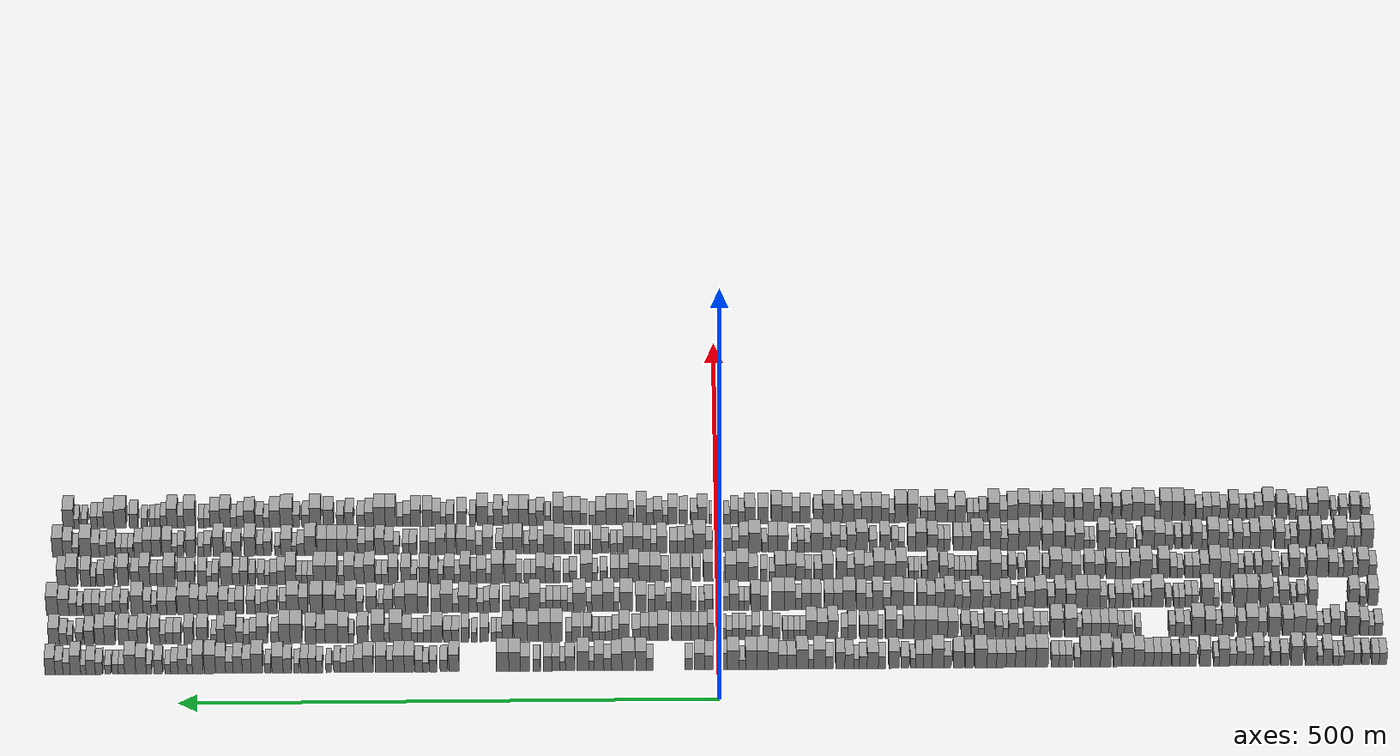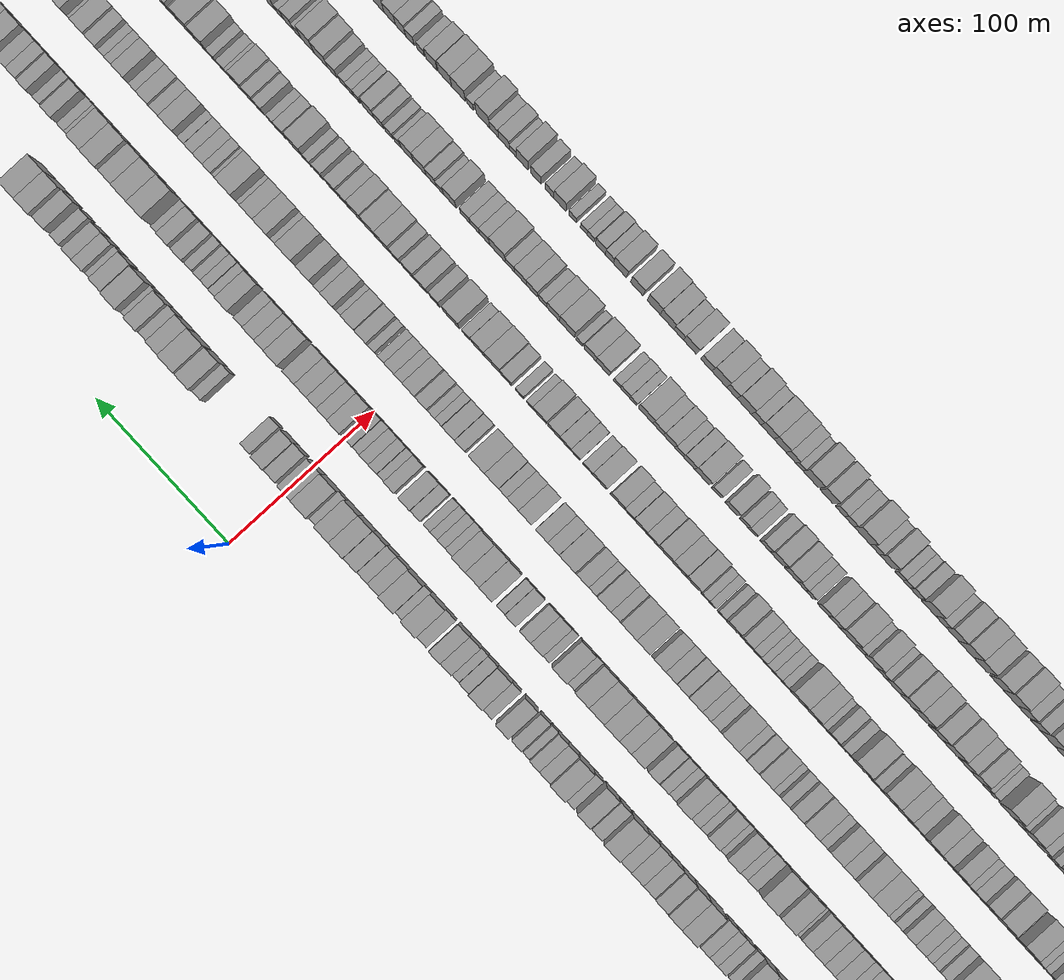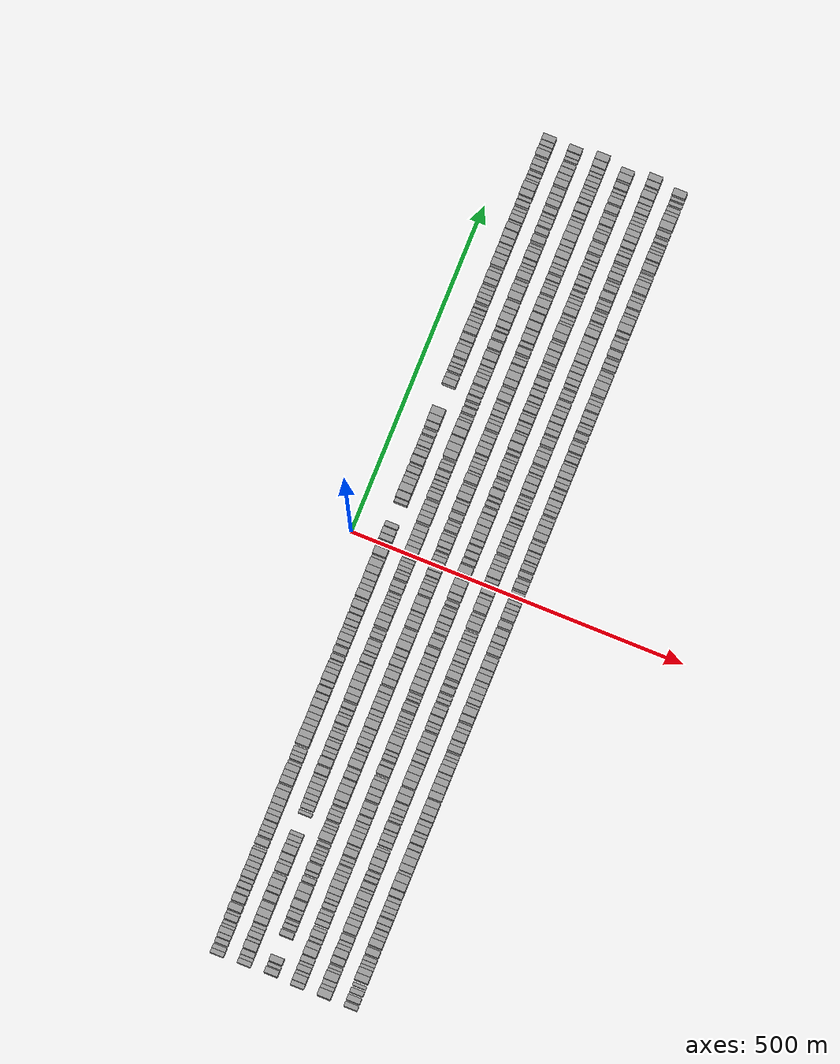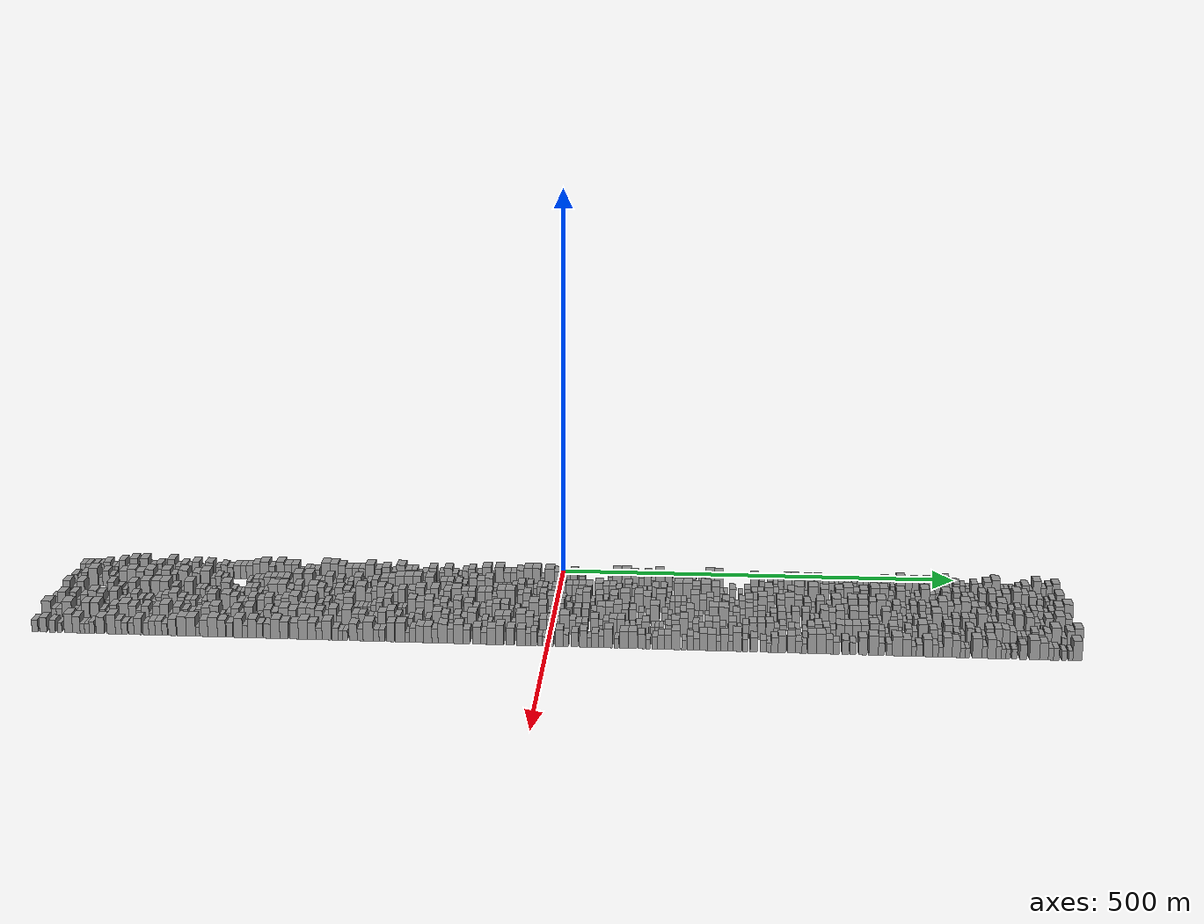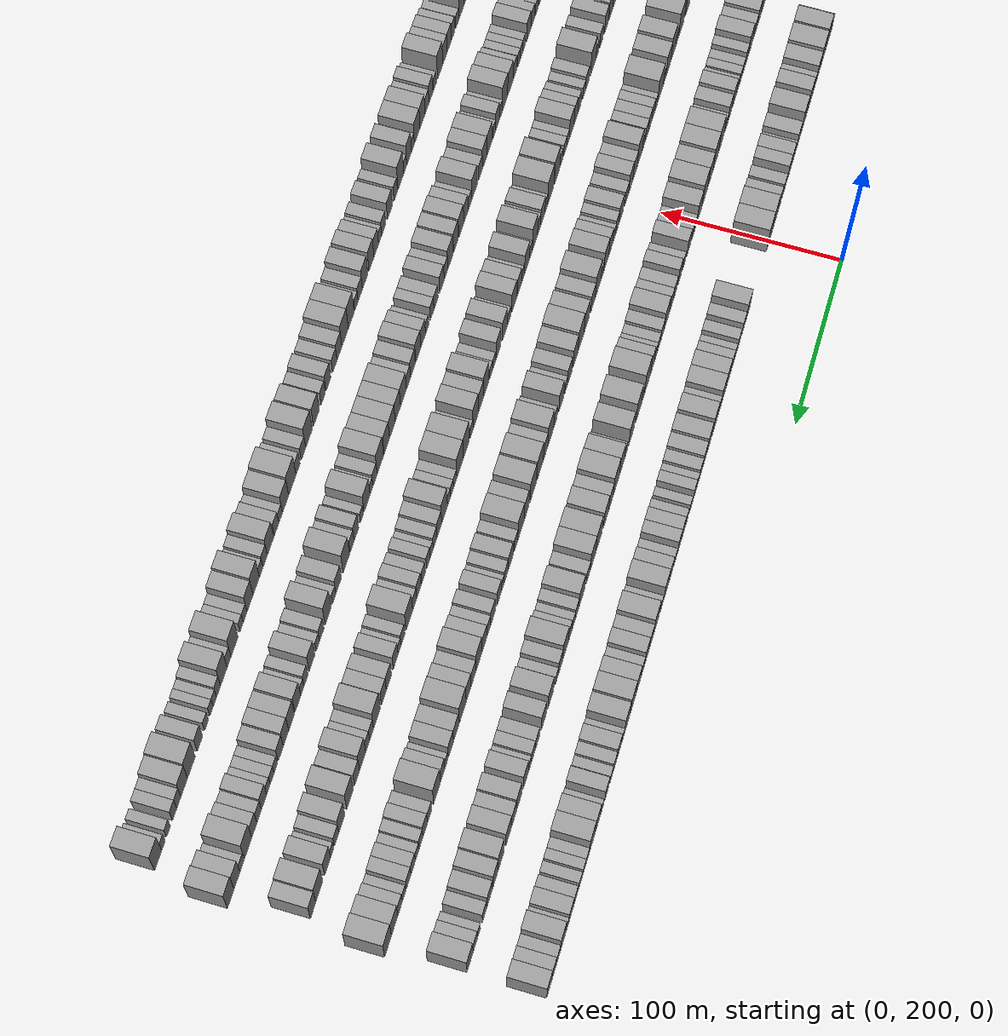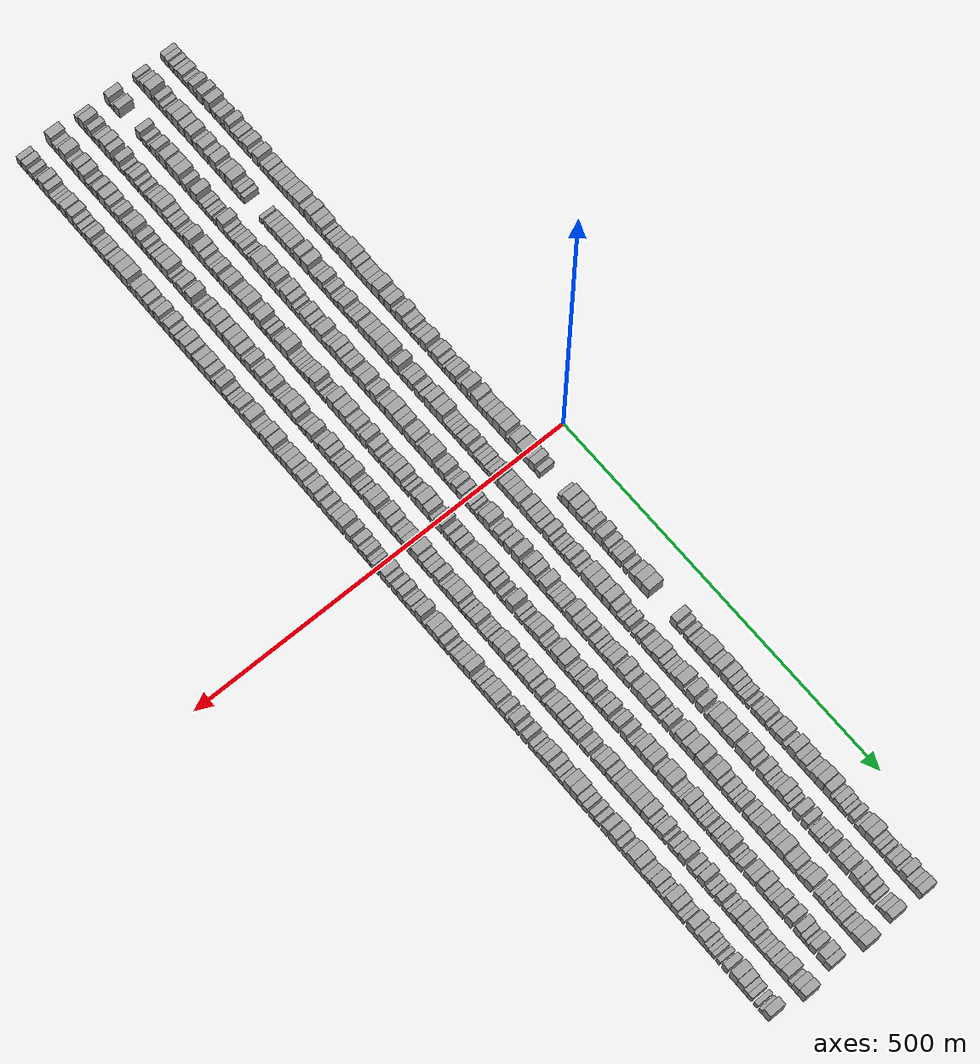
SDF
<sdf version="1.6">
 <world name="default">
  <scene>
   <sky><clouds><speed>12</speed></clouds></sky>
   <ambient>0.4 0.4 0.4 1</ambient>
   <background>0.7 0.7 0.7 1</background>
   <shadows>1</shadows>
  </scene>
  <gravity>0 0 -9.8066</gravity>
  <magnetic_field>6e-06 2.3e-05 -4.2e-05</magnetic_field>
  <physics default="0" name="default_physics" type="ode">
   <ode>
    <solver>
     <type>quick</type>
     <iters>10</iters>
     <sor>1.0</sor>
     <use_dynamic_moi_rescaling>0</use_dynamic_moi_rescaling>
    </solver>
    <constraints>
     <cfm>0</cfm>
     <erp>0.2</erp>
     <contact_max_correcting_vel>100</contact_max_correcting_vel>
     <contact_surface_layer>0.001</contact_surface_layer>
    </constraints>
   </ode>
   <max_step_size>0.004</max_step_size>
   <real_time_factor>1</real_time_factor>
   <real_time_update_rate>250</real_time_update_rate>
  </physics>
  <light name="sun" type="directional">
   <pose>0 0 10 0 0 0</pose>
   <diffuse>0.8 0.8 0.8 1</diffuse>
   <specular>0.2 0.2 0.2 1</specular>
   <attenuation>
    <range>1000</range>
    <constant>0.9</constant>
    <linear>0.01</linear>
    <quadratic>0.001</quadratic>
   </attenuation>
   <direction>-0.5 0.1 -0.9</direction>
  </light>
  <model name="building_1">
   <static>1</static>
   <pose>50.0000 -616.4705 0 0.000000 0.000000 0.000000</pose>
   <link name="link">
    <pose>0 0 7.50 0 0 0</pose>
    <collision name="collision"><geometry><box><size>20.0000 7.0589 15.0000</size></box></geometry></collision>
    <visual name="visual">
     <cast_shadows>0</cast_shadows>
     <geometry><box><size>20.0000 7.0589 15.0000</size></box></geometry>
     <material>
      <script>
       <uri>model://grey_wall/materials/scripts</uri>
       <uri>model://grey_wall/materials/textures</uri>
       <name>vrc/grey_wall</name>
      </script>
     </material>
    </visual>
   </link>
  </model>
  <model name="building_2">
   <static>1</static>
   <pose>50.0000 -609.4764 0 0.000000 0.000000 0.000000</pose>
   <link name="link">
    <pose>0 0 7.50 0 0 0</pose>
    <collision name="collision"><geometry><box><size>20.0000 6.9293 15.0000</size></box></geometry></collision>
    <visual name="visual">
     <cast_shadows>0</cast_shadows>
     <geometry><box><size>20.0000 6.9293 15.0000</size></box></geometry>
     <material>
      <script>
       <uri>model://grey_wall/materials/scripts</uri>
       <uri>model://grey_wall/materials/textures</uri>
       <name>vrc/grey_wall</name>
      </script>
     </material>
    </visual>
   </link>
  </model>
  <model name="building_3">
   <static>1</static>
   <pose>50.0000 -600.3591 0 0.000000 0.000000 0.000000</pose>
   <link name="link">
    <pose>0 0 7.50 0 0 0</pose>
    <collision name="collision"><geometry><box><size>20.0000 7.3053 15.0000</size></box></geometry></collision>
    <visual name="visual">
     <cast_shadows>0</cast_shadows>
     <geometry><box><size>20.0000 7.3053 15.0000</size></box></geometry>
     <material>
      <script>
       <uri>model://grey_wall/materials/scripts</uri>
       <uri>model://grey_wall/materials/textures</uri>
       <name>vrc/grey_wall</name>
      </script>
     </material>
    </visual>
   </link>
  </model>
  <model name="building_4">
   <static>1</static>
   <pose>50.0000 -592.3727 0 0.000000 0.000000 0.000000</pose>
   <link name="link">
    <pose>0 0 7.50 0 0 0</pose>
    <collision name="collision"><geometry><box><size>20.0000 6.6675 15.0000</size></box></geometry></collision>
    <visual name="visual">
     <cast_shadows>0</cast_shadows>
     <geometry><box><size>20.0000 6.6675 15.0000</size></box></geometry>
     <material>
      <script>
       <uri>model://grey_wall/materials/scripts</uri>
       <uri>model://grey_wall/materials/textures</uri>
       <name>vrc/grey_wall</name>
      </script>
     </material>
    </visual>
   </link>
  </model>
  <model name="building_5">
   <static>1</static>
   <pose>50.0000 -584.5810 0 0.000000 0.000000 0.000000</pose>
   <link name="link">
    <pose>0 0 9.00 0 0 0</pose>
    <collision name="collision"><geometry><box><size>20.0000 8.9159 18.0000</size></box></geometry></collision>
    <visual name="visual">
     <cast_shadows>0</cast_shadows>
     <geometry><box><size>20.0000 8.9159 18.0000</size></box></geometry>
     <material>
      <script>
       <uri>model://grey_wall/materials/scripts</uri>
       <uri>model://grey_wall/materials/textures</uri>
       <name>vrc/grey_wall</name>
      </script>
     </material>
    </visual>
   </link>
  </model>
  <model name="building_6">
   <static>1</static>
   <pose>50.0000 -577.7227 0 0.000000 0.000000 0.000000</pose>
   <link name="link">
    <pose>0 0 6.00 0 0 0</pose>
    <collision name="collision"><geometry><box><size>20.0000 4.8007 12.0000</size></box></geometry></collision>
    <visual name="visual">
     <cast_shadows>0</cast_shadows>
     <geometry><box><size>20.0000 4.8007 12.0000</size></box></geometry>
     <material>
      <script>
       <uri>model://grey_wall/materials/scripts</uri>
       <uri>model://grey_wall/materials/textures</uri>
       <name>vrc/grey_wall</name>
      </script>
     </material>
    </visual>
   </link>
  </model>
  <model name="building_7">
   <static>1</static>
   <pose>50.0000 -572.7120 0 0.000000 0.000000 0.000000</pose>
   <link name="link">
    <pose>0 0 6.00 0 0 0</pose>
    <collision name="collision"><geometry><box><size>20.0000 5.2209 12.0000</size></box></geometry></collision>
    <visual name="visual">
     <cast_shadows>0</cast_shadows>
     <geometry><box><size>20.0000 5.2209 12.0000</size></box></geometry>
     <material>
      <script>
       <uri>model://grey_wall/materials/scripts</uri>
       <uri>model://grey_wall/materials/textures</uri>
       <name>vrc/grey_wall</name>
      </script>
     </material>
    </visual>
   </link>
  </model>
  <model name="building_8">
   <static>1</static>
   <pose>50.0000 -564.8139 0 0.000000 0.000000 0.000000</pose>
   <link name="link">
    <pose>0 0 10.50 0 0 0</pose>
    <collision name="collision"><geometry><box><size>20.0000 8.5753 21.0000</size></box></geometry></collision>
    <visual name="visual">
     <cast_shadows>0</cast_shadows>
     <geometry><box><size>20.0000 8.5753 21.0000</size></box></geometry>
     <material>
      <script>
       <uri>model://grey_wall/materials/scripts</uri>
       <uri>model://grey_wall/materials/textures</uri>
       <name>vrc/grey_wall</name>
      </script>
     </material>
    </visual>
   </link>
  </model>
  <model name="building_9">
   <static>1</static>
   <pose>50.0000 -558.0314 0 0.000000 0.000000 0.000000</pose>
   <link name="link">
    <pose>0 0 6.00 0 0 0</pose>
    <collision name="collision"><geometry><box><size>20.0000 4.9897 12.0000</size></box></geometry></collision>
    <visual name="visual">
     <cast_shadows>0</cast_shadows>
     <geometry><box><size>20.0000 4.9897 12.0000</size></box></geometry>
     <material>
      <script>
       <uri>model://grey_wall/materials/scripts</uri>
       <uri>model://grey_wall/materials/textures</uri>
       <name>vrc/grey_wall</name>
      </script>
     </material>
    </visual>
   </link>
  </model>
  <model name="building_10">
   <static>1</static>
   <pose>50.0000 -549.5226 0 0.000000 0.000000 0.000000</pose>
   <link name="link">
    <pose>0 0 12.00 0 0 0</pose>
    <collision name="collision"><geometry><box><size>20.0000 10.0279 24.0000</size></box></geometry></collision>
    <visual name="visual">
     <cast_shadows>0</cast_shadows>
     <geometry><box><size>20.0000 10.0279 24.0000</size></box></geometry>
     <material>
      <script>
       <uri>model://grey_wall/materials/scripts</uri>
       <uri>model://grey_wall/materials/textures</uri>
       <name>vrc/grey_wall</name>
      </script>
     </material>
    </visual>
   </link>
  </model>
  <model name="building_11">
   <static>1</static>
   <pose>50.0000 -536.2097 0 0.000000 0.000000 0.000000</pose>
   <link name="link">
    <pose>0 0 12.00 0 0 0</pose>
    <collision name="collision"><geometry><box><size>20.0000 10.5979 24.0000</size></box></geometry></collision>
    <visual name="visual">
     <cast_shadows>0</cast_shadows>
     <geometry><box><size>20.0000 10.5979 24.0000</size></box></geometry>
     <material>
      <script>
       <uri>model://grey_wall/materials/scripts</uri>
       <uri>model://grey_wall/materials/textures</uri>
       <name>vrc/grey_wall</name>
      </script>
     </material>
    </visual>
   </link>
  </model>
  <model name="building_12">
   <static>1</static>
   <pose>50.0000 -525.1936 0 0.000000 0.000000 0.000000</pose>
   <link name="link">
    <pose>0 0 7.50 0 0 0</pose>
    <collision name="collision"><geometry><box><size>20.0000 7.4343 15.0000</size></box></geometry></collision>
    <visual name="visual">
     <cast_shadows>0</cast_shadows>
     <geometry><box><size>20.0000 7.4343 15.0000</size></box></geometry>
     <material>
      <script>
       <uri>model://grey_wall/materials/scripts</uri>
       <uri>model://grey_wall/materials/textures</uri>
       <name>vrc/grey_wall</name>
      </script>
     </material>
    </visual>
   </link>
  </model>
  <model name="building_13">
   <static>1</static>
   <pose>50.0000 -516.2731 0 0.000000 0.000000 0.000000</pose>
   <link name="link">
    <pose>0 0 9.00 0 0 0</pose>
    <collision name="collision"><geometry><box><size>20.0000 8.4065 18.0000</size></box></geometry></collision>
    <visual name="visual">
     <cast_shadows>0</cast_shadows>
     <geometry><box><size>20.0000 8.4065 18.0000</size></box></geometry>
     <material>
      <script>
       <uri>model://grey_wall/materials/scripts</uri>
       <uri>model://grey_wall/materials/textures</uri>
       <name>vrc/grey_wall</name>
      </script>
     </material>
    </visual>
   </link>
  </model>
  <model name="building_14">
   <static>1</static>
   <pose>50.0000 -508.1706 0 0.000000 0.000000 0.000000</pose>
   <link name="link">
    <pose>0 0 6.00 0 0 0</pose>
    <collision name="collision"><geometry><box><size>20.0000 5.7986 12.0000</size></box></geometry></collision>
    <visual name="visual">
     <cast_shadows>0</cast_shadows>
     <geometry><box><size>20.0000 5.7986 12.0000</size></box></geometry>
     <material>
      <script>
       <uri>model://grey_wall/materials/scripts</uri>
       <uri>model://grey_wall/materials/textures</uri>
       <name>vrc/grey_wall</name>
      </script>
     </material>
    </visual>
   </link>
  </model>
  <model name="building_15">
   <static>1</static>
   <pose>50.0000 -500.4603 0 0.000000 0.000000 0.000000</pose>
   <link name="link">
    <pose>0 0 12.00 0 0 0</pose>
    <collision name="collision"><geometry><box><size>20.0000 9.6219 24.0000</size></box></geometry></collision>
    <visual name="visual">
     <cast_shadows>0</cast_shadows>
     <geometry><box><size>20.0000 9.6219 24.0000</size></box></geometry>
     <material>
      <script>
       <uri>model://grey_wall/materials/scripts</uri>
       <uri>model://grey_wall/materials/textures</uri>
       <name>vrc/grey_wall</name>
      </script>
     </material>
    </visual>
   </link>
  </model>
  <model name="building_16">
   <static>1</static>
   <pose>50.0000 -492.1822 0 0.000000 0.000000 0.000000</pose>
   <link name="link">
    <pose>0 0 7.50 0 0 0</pose>
    <collision name="collision"><geometry><box><size>20.0000 6.9342 15.0000</size></box></geometry></collision>
    <visual name="visual">
     <cast_shadows>0</cast_shadows>
     <geometry><box><size>20.0000 6.9342 15.0000</size></box></geometry>
     <material>
      <script>
       <uri>model://grey_wall/materials/scripts</uri>
       <uri>model://grey_wall/materials/textures</uri>
       <name>vrc/grey_wall</name>
      </script>
     </material>
    </visual>
   </link>
  </model>
  <model name="building_17">
   <static>1</static>
   <pose>50.0000 -484.5919 0 0.000000 0.000000 0.000000</pose>
   <link name="link">
    <pose>0 0 9.00 0 0 0</pose>
    <collision name="collision"><geometry><box><size>20.0000 8.2465 18.0000</size></box></geometry></collision>
    <visual name="visual">
     <cast_shadows>0</cast_shadows>
     <geometry><box><size>20.0000 8.2465 18.0000</size></box></geometry>
     <material>
      <script>
       <uri>model://grey_wall/materials/scripts</uri>
       <uri>model://grey_wall/materials/textures</uri>
       <name>vrc/grey_wall</name>
      </script>
     </material>
    </visual>
   </link>
  </model>
  <model name="building_18">
   <static>1</static>
   <pose>50.0000 -477.0781 0 0.000000 0.000000 0.000000</pose>
   <link name="link">
    <pose>0 0 7.50 0 0 0</pose>
    <collision name="collision"><geometry><box><size>20.0000 6.7811 15.0000</size></box></geometry></collision>
    <visual name="visual">
     <cast_shadows>0</cast_shadows>
     <geometry><box><size>20.0000 6.7811 15.0000</size></box></geometry>
     <material>
      <script>
       <uri>model://grey_wall/materials/scripts</uri>
       <uri>model://grey_wall/materials/textures</uri>
       <name>vrc/grey_wall</name>
      </script>
     </material>
    </visual>
   </link>
  </model>
  <model name="building_19">
   <static>1</static>
   <pose>50.0000 -468.8550 0 0.000000 0.000000 0.000000</pose>
   <link name="link">
    <pose>0 0 10.50 0 0 0</pose>
    <collision name="collision"><geometry><box><size>20.0000 9.6651 21.0000</size></box></geometry></collision>
    <visual name="visual">
     <cast_shadows>0</cast_shadows>
     <geometry><box><size>20.0000 9.6651 21.0000</size></box></geometry>
     <material>
      <script>
       <uri>model://grey_wall/materials/scripts</uri>
       <uri>model://grey_wall/materials/textures</uri>
       <name>vrc/grey_wall</name>
      </script>
     </material>
    </visual>
   </link>
  </model>
  <model name="building_20">
   <static>1</static>
   <pose>50.0000 -461.6189 0 0.000000 0.000000 0.000000</pose>
   <link name="link">
    <pose>0 0 6.00 0 0 0</pose>
    <collision name="collision"><geometry><box><size>20.0000 4.8071 12.0000</size></box></geometry></collision>
    <visual name="visual">
     <cast_shadows>0</cast_shadows>
     <geometry><box><size>20.0000 4.8071 12.0000</size></box></geometry>
     <material>
      <script>
       <uri>model://grey_wall/materials/scripts</uri>
       <uri>model://grey_wall/materials/textures</uri>
       <name>vrc/grey_wall</name>
      </script>
     </material>
    </visual>
   </link>
  </model>
  <model name="building_21">
   <static>1</static>
   <pose>50.0000 -451.1393 0 0.000000 0.000000 0.000000</pose>
   <link name="link">
    <pose>0 0 10.50 0 0 0</pose>
    <collision name="collision"><geometry><box><size>20.0000 10.1521 21.0000</size></box></geometry></collision>
    <visual name="visual">
     <cast_shadows>0</cast_shadows>
     <geometry><box><size>20.0000 10.1521 21.0000</size></box></geometry>
     <material>
      <script>
       <uri>model://grey_wall/materials/scripts</uri>
       <uri>model://grey_wall/materials/textures</uri>
       <name>vrc/grey_wall</name>
      </script>
     </material>
    </visual>
   </link>
  </model>
  <model name="building_22">
   <static>1</static>
   <pose>50.0000 -439.6052 0 0.000000 0.000000 0.000000</pose>
   <link name="link">
    <pose>0 0 7.50 0 0 0</pose>
    <collision name="collision"><geometry><box><size>20.0000 6.9161 15.0000</size></box></geometry></collision>
    <visual name="visual">
     <cast_shadows>0</cast_shadows>
     <geometry><box><size>20.0000 6.9161 15.0000</size></box></geometry>
     <material>
      <script>
       <uri>model://grey_wall/materials/scripts</uri>
       <uri>model://grey_wall/materials/textures</uri>
       <name>vrc/grey_wall</name>
      </script>
     </material>
    </visual>
   </link>
  </model>
  <model name="building_23">
   <static>1</static>
   <pose>50.0000 -431.9623 0 0.000000 0.000000 0.000000</pose>
   <link name="link">
    <pose>0 0 9.00 0 0 0</pose>
    <collision name="collision"><geometry><box><size>20.0000 8.3697 18.0000</size></box></geometry></collision>
    <visual name="visual">
     <cast_shadows>0</cast_shadows>
     <geometry><box><size>20.0000 8.3697 18.0000</size></box></geometry>
     <material>
      <script>
       <uri>model://grey_wall/materials/scripts</uri>
       <uri>model://grey_wall/materials/textures</uri>
       <name>vrc/grey_wall</name>
      </script>
     </material>
    </visual>
   </link>
  </model>
  <model name="building_24">
   <static>1</static>
   <pose>50.0000 -424.0285 0 0.000000 0.000000 0.000000</pose>
   <link name="link">
    <pose>0 0 7.50 0 0 0</pose>
    <collision name="collision"><geometry><box><size>20.0000 7.4979 15.0000</size></box></geometry></collision>
    <visual name="visual">
     <cast_shadows>0</cast_shadows>
     <geometry><box><size>20.0000 7.4979 15.0000</size></box></geometry>
     <material>
      <script>
       <uri>model://grey_wall/materials/scripts</uri>
       <uri>model://grey_wall/materials/textures</uri>
       <name>vrc/grey_wall</name>
      </script>
     </material>
    </visual>
   </link>
  </model>
  <model name="building_25">
   <static>1</static>
   <pose>50.0000 -414.8759 0 0.000000 0.000000 0.000000</pose>
   <link name="link">
    <pose>0 0 9.00 0 0 0</pose>
    <collision name="collision"><geometry><box><size>20.0000 8.8074 18.0000</size></box></geometry></collision>
    <visual name="visual">
     <cast_shadows>0</cast_shadows>
     <geometry><box><size>20.0000 8.8074 18.0000</size></box></geometry>
     <material>
      <script>
       <uri>model://grey_wall/materials/scripts</uri>
       <uri>model://grey_wall/materials/textures</uri>
       <name>vrc/grey_wall</name>
      </script>
     </material>
    </visual>
   </link>
  </model>
  <model name="building_26">
   <static>1</static>
   <pose>50.0000 -406.8674 0 0.000000 0.000000 0.000000</pose>
   <link name="link">
    <pose>0 0 9.00 0 0 0</pose>
    <collision name="collision"><geometry><box><size>20.0000 7.2095 18.0000</size></box></geometry></collision>
    <visual name="visual">
     <cast_shadows>0</cast_shadows>
     <geometry><box><size>20.0000 7.2095 18.0000</size></box></geometry>
     <material>
      <script>
       <uri>model://grey_wall/materials/scripts</uri>
       <uri>model://grey_wall/materials/textures</uri>
       <name>vrc/grey_wall</name>
      </script>
     </material>
    </visual>
   </link>
  </model>
  <model name="building_27">
   <static>1</static>
   <pose>50.0000 -398.9478 0 0.000000 0.000000 0.000000</pose>
   <link name="link">
    <pose>0 0 9.00 0 0 0</pose>
    <collision name="collision"><geometry><box><size>20.0000 8.6297 18.0000</size></box></geometry></collision>
    <visual name="visual">
     <cast_shadows>0</cast_shadows>
     <geometry><box><size>20.0000 8.6297 18.0000</size></box></geometry>
     <material>
      <script>
       <uri>model://grey_wall/materials/scripts</uri>
       <uri>model://grey_wall/materials/textures</uri>
       <name>vrc/grey_wall</name>
      </script>
     </material>
    </visual>
   </link>
  </model>
  <model name="building_28">
   <static>1</static>
   <pose>50.0000 -389.8648 0 0.000000 0.000000 0.000000</pose>
   <link name="link">
    <pose>0 0 10.50 0 0 0</pose>
    <collision name="collision"><geometry><box><size>20.0000 9.5361 21.0000</size></box></geometry></collision>
    <visual name="visual">
     <cast_shadows>0</cast_shadows>
     <geometry><box><size>20.0000 9.5361 21.0000</size></box></geometry>
     <material>
      <script>
       <uri>model://grey_wall/materials/scripts</uri>
       <uri>model://grey_wall/materials/textures</uri>
       <name>vrc/grey_wall</name>
      </script>
     </material>
    </visual>
   </link>
  </model>
  <model name="building_29">
   <static>1</static>
   <pose>50.0000 -379.2974 0 0.000000 0.000000 0.000000</pose>
   <link name="link">
    <pose>0 0 12.00 0 0 0</pose>
    <collision name="collision"><geometry><box><size>20.0000 11.5987 24.0000</size></box></geometry></collision>
    <visual name="visual">
     <cast_shadows>0</cast_shadows>
     <geometry><box><size>20.0000 11.5987 24.0000</size></box></geometry>
     <material>
      <script>
       <uri>model://grey_wall/materials/scripts</uri>
       <uri>model://grey_wall/materials/textures</uri>
       <name>vrc/grey_wall</name>
      </script>
     </material>
    </visual>
   </link>
  </model>
  <model name="building_30">
   <static>1</static>
   <pose>50.0000 -369.7955 0 0.000000 0.000000 0.000000</pose>
   <link name="link">
    <pose>0 0 9.00 0 0 0</pose>
    <collision name="collision"><geometry><box><size>20.0000 7.4053 18.0000</size></box></geometry></collision>
    <visual name="visual">
     <cast_shadows>0</cast_shadows>
     <geometry><box><size>20.0000 7.4053 18.0000</size></box></geometry>
     <material>
      <script>
       <uri>model://grey_wall/materials/scripts</uri>
       <uri>model://grey_wall/materials/textures</uri>
       <name>vrc/grey_wall</name>
      </script>
     </material>
    </visual>
   </link>
  </model>
  <model name="building_31">
   <static>1</static>
   <pose>50.0000 -358.9454 0 0.000000 0.000000 0.000000</pose>
   <link name="link">
    <pose>0 0 12.00 0 0 0</pose>
    <collision name="collision"><geometry><box><size>20.0000 10.2949 24.0000</size></box></geometry></collision>
    <visual name="visual">
     <cast_shadows>0</cast_shadows>
     <geometry><box><size>20.0000 10.2949 24.0000</size></box></geometry>
     <material>
      <script>
       <uri>model://grey_wall/materials/scripts</uri>
       <uri>model://grey_wall/materials/textures</uri>
       <name>vrc/grey_wall</name>
      </script>
     </material>
    </visual>
   </link>
  </model>
  <model name="building_32">
   <static>1</static>
   <pose>50.0000 -349.2108 0 0.000000 0.000000 0.000000</pose>
   <link name="link">
    <pose>0 0 10.50 0 0 0</pose>
    <collision name="collision"><geometry><box><size>20.0000 9.1743 21.0000</size></box></geometry></collision>
    <visual name="visual">
     <cast_shadows>0</cast_shadows>
     <geometry><box><size>20.0000 9.1743 21.0000</size></box></geometry>
     <material>
      <script>
       <uri>model://grey_wall/materials/scripts</uri>
       <uri>model://grey_wall/materials/textures</uri>
       <name>vrc/grey_wall</name>
      </script>
     </material>
    </visual>
   </link>
  </model>
  <model name="building_33">
   <static>1</static>
   <pose>50.0000 -339.9540 0 0.000000 0.000000 0.000000</pose>
   <link name="link">
    <pose>0 0 10.50 0 0 0</pose>
    <collision name="collision"><geometry><box><size>20.0000 9.3393 21.0000</size></box></geometry></collision>
    <visual name="visual">
     <cast_shadows>0</cast_shadows>
     <geometry><box><size>20.0000 9.3393 21.0000</size></box></geometry>
     <material>
      <script>
       <uri>model://grey_wall/materials/scripts</uri>
       <uri>model://grey_wall/materials/textures</uri>
       <name>vrc/grey_wall</name>
      </script>
     </material>
    </visual>
   </link>
  </model>
  <model name="building_34">
   <static>1</static>
   <pose>50.0000 -332.5883 0 0.000000 0.000000 0.000000</pose>
   <link name="link">
    <pose>0 0 6.00 0 0 0</pose>
    <collision name="collision"><geometry><box><size>20.0000 5.3922 12.0000</size></box></geometry></collision>
    <visual name="visual">
     <cast_shadows>0</cast_shadows>
     <geometry><box><size>20.0000 5.3922 12.0000</size></box></geometry>
     <material>
      <script>
       <uri>model://grey_wall/materials/scripts</uri>
       <uri>model://grey_wall/materials/textures</uri>
       <name>vrc/grey_wall</name>
      </script>
     </material>
    </visual>
   </link>
  </model>
  <model name="building_35">
   <static>1</static>
   <pose>50.0000 -324.7472 0 0.000000 0.000000 0.000000</pose>
   <link name="link">
    <pose>0 0 7.50 0 0 0</pose>
    <collision name="collision"><geometry><box><size>20.0000 6.2898 15.0000</size></box></geometry></collision>
    <visual name="visual">
     <cast_shadows>0</cast_shadows>
     <geometry><box><size>20.0000 6.2898 15.0000</size></box></geometry>
     <material>
      <script>
       <uri>model://grey_wall/materials/scripts</uri>
       <uri>model://grey_wall/materials/textures</uri>
       <name>vrc/grey_wall</name>
      </script>
     </material>
    </visual>
   </link>
  </model>
  <model name="building_36">
   <static>1</static>
   <pose>50.0000 -318.5972 0 0.000000 0.000000 0.000000</pose>
   <link name="link">
    <pose>0 0 7.50 0 0 0</pose>
    <collision name="collision"><geometry><box><size>20.0000 6.0102 15.0000</size></box></geometry></collision>
    <visual name="visual">
     <cast_shadows>0</cast_shadows>
     <geometry><box><size>20.0000 6.0102 15.0000</size></box></geometry>
     <material>
      <script>
       <uri>model://grey_wall/materials/scripts</uri>
       <uri>model://grey_wall/materials/textures</uri>
       <name>vrc/grey_wall</name>
      </script>
     </material>
    </visual>
   </link>
  </model>
  <model name="building_37">
   <static>1</static>
   <pose>50.0000 -312.0216 0 0.000000 0.000000 0.000000</pose>
   <link name="link">
    <pose>0 0 7.50 0 0 0</pose>
    <collision name="collision"><geometry><box><size>20.0000 7.1410 15.0000</size></box></geometry></collision>
    <visual name="visual">
     <cast_shadows>0</cast_shadows>
     <geometry><box><size>20.0000 7.1410 15.0000</size></box></geometry>
     <material>
      <script>
       <uri>model://grey_wall/materials/scripts</uri>
       <uri>model://grey_wall/materials/textures</uri>
       <name>vrc/grey_wall</name>
      </script>
     </material>
    </visual>
   </link>
  </model>
  <model name="building_38">
   <static>1</static>
   <pose>50.0000 -299.7955 0 0.000000 0.000000 0.000000</pose>
   <link name="link">
    <pose>0 0 12.00 0 0 0</pose>
    <collision name="collision"><geometry><box><size>20.0000 11.3112 24.0000</size></box></geometry></collision>
    <visual name="visual">
     <cast_shadows>0</cast_shadows>
     <geometry><box><size>20.0000 11.3112 24.0000</size></box></geometry>
     <material>
      <script>
       <uri>model://grey_wall/materials/scripts</uri>
       <uri>model://grey_wall/materials/textures</uri>
       <name>vrc/grey_wall</name>
      </script>
     </material>
    </visual>
   </link>
  </model>
  <model name="building_39">
   <static>1</static>
   <pose>50.0000 -289.2028 0 0.000000 0.000000 0.000000</pose>
   <link name="link">
    <pose>0 0 12.00 0 0 0</pose>
    <collision name="collision"><geometry><box><size>20.0000 9.8742 24.0000</size></box></geometry></collision>
    <visual name="visual">
     <cast_shadows>0</cast_shadows>
     <geometry><box><size>20.0000 9.8742 24.0000</size></box></geometry>
     <material>
      <script>
       <uri>model://grey_wall/materials/scripts</uri>
       <uri>model://grey_wall/materials/textures</uri>
       <name>vrc/grey_wall</name>
      </script>
     </material>
    </visual>
   </link>
  </model>
  <model name="building_40">
   <static>1</static>
   <pose>50.0000 -279.5872 0 0.000000 0.000000 0.000000</pose>
   <link name="link">
    <pose>0 0 10.50 0 0 0</pose>
    <collision name="collision"><geometry><box><size>20.0000 9.3571 21.0000</size></box></geometry></collision>
    <visual name="visual">
     <cast_shadows>0</cast_shadows>
     <geometry><box><size>20.0000 9.3571 21.0000</size></box></geometry>
     <material>
      <script>
       <uri>model://grey_wall/materials/scripts</uri>
       <uri>model://grey_wall/materials/textures</uri>
       <name>vrc/grey_wall</name>
      </script>
     </material>
    </visual>
   </link>
  </model>
  <model name="building_41">
   <static>1</static>
   <pose>50.0000 -270.6344 0 0.000000 0.000000 0.000000</pose>
   <link name="link">
    <pose>0 0 9.00 0 0 0</pose>
    <collision name="collision"><geometry><box><size>20.0000 8.5484 18.0000</size></box></geometry></collision>
    <visual name="visual">
     <cast_shadows>0</cast_shadows>
     <geometry><box><size>20.0000 8.5484 18.0000</size></box></geometry>
     <material>
      <script>
       <uri>model://grey_wall/materials/scripts</uri>
       <uri>model://grey_wall/materials/textures</uri>
       <name>vrc/grey_wall</name>
      </script>
     </material>
    </visual>
   </link>
  </model>
  <model name="building_42">
   <static>1</static>
   <pose>50.0000 -261.8857 0 0.000000 0.000000 0.000000</pose>
   <link name="link">
    <pose>0 0 9.00 0 0 0</pose>
    <collision name="collision"><geometry><box><size>20.0000 8.9490 18.0000</size></box></geometry></collision>
    <visual name="visual">
     <cast_shadows>0</cast_shadows>
     <geometry><box><size>20.0000 8.9490 18.0000</size></box></geometry>
     <material>
      <script>
       <uri>model://grey_wall/materials/scripts</uri>
       <uri>model://grey_wall/materials/textures</uri>
       <name>vrc/grey_wall</name>
      </script>
     </material>
    </visual>
   </link>
  </model>
  <model name="building_43">
   <static>1</static>
   <pose>50.0000 -252.9878 0 0.000000 0.000000 0.000000</pose>
   <link name="link">
    <pose>0 0 9.00 0 0 0</pose>
    <collision name="collision"><geometry><box><size>20.0000 8.8469 18.0000</size></box></geometry></collision>
    <visual name="visual">
     <cast_shadows>0</cast_shadows>
     <geometry><box><size>20.0000 8.8469 18.0000</size></box></geometry>
     <material>
      <script>
       <uri>model://grey_wall/materials/scripts</uri>
       <uri>model://grey_wall/materials/textures</uri>
       <name>vrc/grey_wall</name>
      </script>
     </material>
    </visual>
   </link>
  </model>
  <model name="building_44">
   <static>1</static>
   <pose>50.0000 -242.8386 0 0.000000 0.000000 0.000000</pose>
   <link name="link">
    <pose>0 0 12.00 0 0 0</pose>
    <collision name="collision"><geometry><box><size>20.0000 11.4516 24.0000</size></box></geometry></collision>
    <visual name="visual">
     <cast_shadows>0</cast_shadows>
     <geometry><box><size>20.0000 11.4516 24.0000</size></box></geometry>
     <material>
      <script>
       <uri>model://grey_wall/materials/scripts</uri>
       <uri>model://grey_wall/materials/textures</uri>
       <name>vrc/grey_wall</name>
      </script>
     </material>
    </visual>
   </link>
  </model>
  <model name="building_45">
   <static>1</static>
   <pose>50.0000 -232.1709 0 0.000000 0.000000 0.000000</pose>
   <link name="link">
    <pose>0 0 9.00 0 0 0</pose>
    <collision name="collision"><geometry><box><size>20.0000 7.8837 18.0000</size></box></geometry></collision>
    <visual name="visual">
     <cast_shadows>0</cast_shadows>
     <geometry><box><size>20.0000 7.8837 18.0000</size></box></geometry>
     <material>
      <script>
       <uri>model://grey_wall/materials/scripts</uri>
       <uri>model://grey_wall/materials/textures</uri>
       <name>vrc/grey_wall</name>
      </script>
     </material>
    </visual>
   </link>
  </model>
  <model name="building_46">
   <static>1</static>
   <pose>50.0000 -222.3349 0 0.000000 0.000000 0.000000</pose>
   <link name="link">
    <pose>0 0 10.50 0 0 0</pose>
    <collision name="collision"><geometry><box><size>20.0000 9.7882 21.0000</size></box></geometry></collision>
    <visual name="visual">
     <cast_shadows>0</cast_shadows>
     <geometry><box><size>20.0000 9.7882 21.0000</size></box></geometry>
     <material>
      <script>
       <uri>model://grey_wall/materials/scripts</uri>
       <uri>model://grey_wall/materials/textures</uri>
       <name>vrc/grey_wall</name>
      </script>
     </material>
    </visual>
   </link>
  </model>
  <model name="building_47">
   <static>1</static>
   <pose>50.0000 -212.0535 0 0.000000 0.000000 0.000000</pose>
   <link name="link">
    <pose>0 0 7.50 0 0 0</pose>
    <collision name="collision"><geometry><box><size>20.0000 6.7747 15.0000</size></box></geometry></collision>
    <visual name="visual">
     <cast_shadows>0</cast_shadows>
     <geometry><box><size>20.0000 6.7747 15.0000</size></box></geometry>
     <material>
      <script>
       <uri>model://grey_wall/materials/scripts</uri>
       <uri>model://grey_wall/materials/textures</uri>
       <name>vrc/grey_wall</name>
      </script>
     </material>
    </visual>
   </link>
  </model>
  <model name="building_48">
   <static>1</static>
   <pose>50.0000 -203.1275 0 0.000000 0.000000 0.000000</pose>
   <link name="link">
    <pose>0 0 12.00 0 0 0</pose>
    <collision name="collision"><geometry><box><size>20.0000 11.0774 24.0000</size></box></geometry></collision>
    <visual name="visual">
     <cast_shadows>0</cast_shadows>
     <geometry><box><size>20.0000 11.0774 24.0000</size></box></geometry>
     <material>
      <script>
       <uri>model://grey_wall/materials/scripts</uri>
       <uri>model://grey_wall/materials/textures</uri>
       <name>vrc/grey_wall</name>
      </script>
     </material>
    </visual>
   </link>
  </model>
  <model name="building_49">
   <static>1</static>
   <pose>50.0000 -193.6138 0 0.000000 0.000000 0.000000</pose>
   <link name="link">
    <pose>0 0 9.00 0 0 0</pose>
    <collision name="collision"><geometry><box><size>20.0000 7.9500 18.0000</size></box></geometry></collision>
    <visual name="visual">
     <cast_shadows>0</cast_shadows>
     <geometry><box><size>20.0000 7.9500 18.0000</size></box></geometry>
     <material>
      <script>
       <uri>model://grey_wall/materials/scripts</uri>
       <uri>model://grey_wall/materials/textures</uri>
       <name>vrc/grey_wall</name>
      </script>
     </material>
    </visual>
   </link>
  </model>
  <model name="building_50">
   <static>1</static>
   <pose>50.0000 -185.9637 0 0.000000 0.000000 0.000000</pose>
   <link name="link">
    <pose>0 0 9.00 0 0 0</pose>
    <collision name="collision"><geometry><box><size>20.0000 7.3501 18.0000</size></box></geometry></collision>
    <visual name="visual">
     <cast_shadows>0</cast_shadows>
     <geometry><box><size>20.0000 7.3501 18.0000</size></box></geometry>
     <material>
      <script>
       <uri>model://grey_wall/materials/scripts</uri>
       <uri>model://grey_wall/materials/textures</uri>
       <name>vrc/grey_wall</name>
      </script>
     </material>
    </visual>
   </link>
  </model>
  <model name="building_51">
   <static>1</static>
   <pose>50.0000 -179.8526 0 0.000000 0.000000 0.000000</pose>
   <link name="link">
    <pose>0 0 6.00 0 0 0</pose>
    <collision name="collision"><geometry><box><size>20.0000 4.8722 12.0000</size></box></geometry></collision>
    <visual name="visual">
     <cast_shadows>0</cast_shadows>
     <geometry><box><size>20.0000 4.8722 12.0000</size></box></geometry>
     <material>
      <script>
       <uri>model://grey_wall/materials/scripts</uri>
       <uri>model://grey_wall/materials/textures</uri>
       <name>vrc/grey_wall</name>
      </script>
     </material>
    </visual>
   </link>
  </model>
  <model name="building_52">
   <static>1</static>
   <pose>50.0000 -172.6999 0 0.000000 0.000000 0.000000</pose>
   <link name="link">
    <pose>0 0 7.50 0 0 0</pose>
    <collision name="collision"><geometry><box><size>20.0000 7.4332 15.0000</size></box></geometry></collision>
    <visual name="visual">
     <cast_shadows>0</cast_shadows>
     <geometry><box><size>20.0000 7.4332 15.0000</size></box></geometry>
     <material>
      <script>
       <uri>model://grey_wall/materials/scripts</uri>
       <uri>model://grey_wall/materials/textures</uri>
       <name>vrc/grey_wall</name>
      </script>
     </material>
    </visual>
   </link>
  </model>
  <model name="building_53">
   <static>1</static>
   <pose>50.0000 -162.2387 0 0.000000 0.000000 0.000000</pose>
   <link name="link">
    <pose>0 0 10.50 0 0 0</pose>
    <collision name="collision"><geometry><box><size>20.0000 9.4893 21.0000</size></box></geometry></collision>
    <visual name="visual">
     <cast_shadows>0</cast_shadows>
     <geometry><box><size>20.0000 9.4893 21.0000</size></box></geometry>
     <material>
      <script>
       <uri>model://grey_wall/materials/scripts</uri>
       <uri>model://grey_wall/materials/textures</uri>
       <name>vrc/grey_wall</name>
      </script>
     </material>
    </visual>
   </link>
  </model>
  <model name="building_54">
   <static>1</static>
   <pose>50.0000 -151.1109 0 0.000000 0.000000 0.000000</pose>
   <link name="link">
    <pose>0 0 7.50 0 0 0</pose>
    <collision name="collision"><geometry><box><size>20.0000 6.7663 15.0000</size></box></geometry></collision>
    <visual name="visual">
     <cast_shadows>0</cast_shadows>
     <geometry><box><size>20.0000 6.7663 15.0000</size></box></geometry>
     <material>
      <script>
       <uri>model://grey_wall/materials/scripts</uri>
       <uri>model://grey_wall/materials/textures</uri>
       <name>vrc/grey_wall</name>
      </script>
     </material>
    </visual>
   </link>
  </model>
  <model name="building_55">
   <static>1</static>
   <pose>50.0000 -142.5127 0 0.000000 0.000000 0.000000</pose>
   <link name="link">
    <pose>0 0 10.50 0 0 0</pose>
    <collision name="collision"><geometry><box><size>20.0000 10.4299 21.0000</size></box></geometry></collision>
    <visual name="visual">
     <cast_shadows>0</cast_shadows>
     <geometry><box><size>20.0000 10.4299 21.0000</size></box></geometry>
     <material>
      <script>
       <uri>model://grey_wall/materials/scripts</uri>
       <uri>model://grey_wall/materials/textures</uri>
       <name>vrc/grey_wall</name>
      </script>
     </material>
    </visual>
   </link>
  </model>
  <model name="building_56">
   <static>1</static>
   <pose>50.0000 -133.7003 0 0.000000 0.000000 0.000000</pose>
   <link name="link">
    <pose>0 0 7.50 0 0 0</pose>
    <collision name="collision"><geometry><box><size>20.0000 7.1949 15.0000</size></box></geometry></collision>
    <visual name="visual">
     <cast_shadows>0</cast_shadows>
     <geometry><box><size>20.0000 7.1949 15.0000</size></box></geometry>
     <material>
      <script>
       <uri>model://grey_wall/materials/scripts</uri>
       <uri>model://grey_wall/materials/textures</uri>
       <name>vrc/grey_wall</name>
      </script>
     </material>
    </visual>
   </link>
  </model>
  <model name="building_57">
   <static>1</static>
   <pose>50.0000 -127.4242 0 0.000000 0.000000 0.000000</pose>
   <link name="link">
    <pose>0 0 6.00 0 0 0</pose>
    <collision name="collision"><geometry><box><size>20.0000 5.3573 12.0000</size></box></geometry></collision>
    <visual name="visual">
     <cast_shadows>0</cast_shadows>
     <geometry><box><size>20.0000 5.3573 12.0000</size></box></geometry>
     <material>
      <script>
       <uri>model://grey_wall/materials/scripts</uri>
       <uri>model://grey_wall/materials/textures</uri>
       <name>vrc/grey_wall</name>
      </script>
     </material>
    </visual>
   </link>
  </model>
  <model name="building_58">
   <static>1</static>
   <pose>50.0000 -120.6747 0 0.000000 0.000000 0.000000</pose>
   <link name="link">
    <pose>0 0 9.00 0 0 0</pose>
    <collision name="collision"><geometry><box><size>20.0000 8.1415 18.0000</size></box></geometry></collision>
    <visual name="visual">
     <cast_shadows>0</cast_shadows>
     <geometry><box><size>20.0000 8.1415 18.0000</size></box></geometry>
     <material>
      <script>
       <uri>model://grey_wall/materials/scripts</uri>
       <uri>model://grey_wall/materials/textures</uri>
       <name>vrc/grey_wall</name>
      </script>
     </material>
    </visual>
   </link>
  </model>
  <model name="building_59">
   <static>1</static>
   <pose>50.0000 -112.3836 0 0.000000 0.000000 0.000000</pose>
   <link name="link">
    <pose>0 0 10.50 0 0 0</pose>
    <collision name="collision"><geometry><box><size>20.0000 8.4407 21.0000</size></box></geometry></collision>
    <visual name="visual">
     <cast_shadows>0</cast_shadows>
     <geometry><box><size>20.0000 8.4407 21.0000</size></box></geometry>
     <material>
      <script>
       <uri>model://grey_wall/materials/scripts</uri>
       <uri>model://grey_wall/materials/textures</uri>
       <name>vrc/grey_wall</name>
      </script>
     </material>
    </visual>
   </link>
  </model>
  <model name="building_60">
   <static>1</static>
   <pose>50.0000 -102.4915 0 0.000000 0.000000 0.000000</pose>
   <link name="link">
    <pose>0 0 7.50 0 0 0</pose>
    <collision name="collision"><geometry><box><size>20.0000 7.3436 15.0000</size></box></geometry></collision>
    <visual name="visual">
     <cast_shadows>0</cast_shadows>
     <geometry><box><size>20.0000 7.3436 15.0000</size></box></geometry>
     <material>
      <script>
       <uri>model://grey_wall/materials/scripts</uri>
       <uri>model://grey_wall/materials/textures</uri>
       <name>vrc/grey_wall</name>
      </script>
     </material>
    </visual>
   </link>
  </model>
  <model name="building_61">
   <static>1</static>
   <pose>50.0000 -93.2110 0 0.000000 0.000000 0.000000</pose>
   <link name="link">
    <pose>0 0 12.00 0 0 0</pose>
    <collision name="collision"><geometry><box><size>20.0000 11.2173 24.0000</size></box></geometry></collision>
    <visual name="visual">
     <cast_shadows>0</cast_shadows>
     <geometry><box><size>20.0000 11.2173 24.0000</size></box></geometry>
     <material>
      <script>
       <uri>model://grey_wall/materials/scripts</uri>
       <uri>model://grey_wall/materials/textures</uri>
       <name>vrc/grey_wall</name>
      </script>
     </material>
    </visual>
   </link>
  </model>
  <model name="building_62">
   <static>1</static>
   <pose>50.0000 -85.0519 0 0.000000 0.000000 0.000000</pose>
   <link name="link">
    <pose>0 0 6.00 0 0 0</pose>
    <collision name="collision"><geometry><box><size>20.0000 5.1009 12.0000</size></box></geometry></collision>
    <visual name="visual">
     <cast_shadows>0</cast_shadows>
     <geometry><box><size>20.0000 5.1009 12.0000</size></box></geometry>
     <material>
      <script>
       <uri>model://grey_wall/materials/scripts</uri>
       <uri>model://grey_wall/materials/textures</uri>
       <name>vrc/grey_wall</name>
      </script>
     </material>
    </visual>
   </link>
  </model>
  <model name="building_63">
   <static>1</static>
   <pose>50.0000 -76.9320 0 0.000000 0.000000 0.000000</pose>
   <link name="link">
    <pose>0 0 12.00 0 0 0</pose>
    <collision name="collision"><geometry><box><size>20.0000 11.1389 24.0000</size></box></geometry></collision>
    <visual name="visual">
     <cast_shadows>0</cast_shadows>
     <geometry><box><size>20.0000 11.1389 24.0000</size></box></geometry>
     <material>
      <script>
       <uri>model://grey_wall/materials/scripts</uri>
       <uri>model://grey_wall/materials/textures</uri>
       <name>vrc/grey_wall</name>
      </script>
     </material>
    </visual>
   </link>
  </model>
  <model name="building_64">
   <static>1</static>
   <pose>50.0000 -67.0298 0 0.000000 0.000000 0.000000</pose>
   <link name="link">
    <pose>0 0 9.00 0 0 0</pose>
    <collision name="collision"><geometry><box><size>20.0000 8.6655 18.0000</size></box></geometry></collision>
    <visual name="visual">
     <cast_shadows>0</cast_shadows>
     <geometry><box><size>20.0000 8.6655 18.0000</size></box></geometry>
     <material>
      <script>
       <uri>model://grey_wall/materials/scripts</uri>
       <uri>model://grey_wall/materials/textures</uri>
       <name>vrc/grey_wall</name>
      </script>
     </material>
    </visual>
   </link>
  </model>
  <model name="building_65">
   <static>1</static>
   <pose>50.0000 -58.9646 0 0.000000 0.000000 0.000000</pose>
   <link name="link">
    <pose>0 0 9.00 0 0 0</pose>
    <collision name="collision"><geometry><box><size>20.0000 7.4649 18.0000</size></box></geometry></collision>
    <visual name="visual">
     <cast_shadows>0</cast_shadows>
     <geometry><box><size>20.0000 7.4649 18.0000</size></box></geometry>
     <material>
      <script>
       <uri>model://grey_wall/materials/scripts</uri>
       <uri>model://grey_wall/materials/textures</uri>
       <name>vrc/grey_wall</name>
      </script>
     </material>
    </visual>
   </link>
  </model>
  <model name="building_66">
   <static>1</static>
   <pose>50.0000 -50.4153 0 0.000000 0.000000 0.000000</pose>
   <link name="link">
    <pose>0 0 10.50 0 0 0</pose>
    <collision name="collision"><geometry><box><size>20.0000 9.6337 21.0000</size></box></geometry></collision>
    <visual name="visual">
     <cast_shadows>0</cast_shadows>
     <geometry><box><size>20.0000 9.6337 21.0000</size></box></geometry>
     <material>
      <script>
       <uri>model://grey_wall/materials/scripts</uri>
       <uri>model://grey_wall/materials/textures</uri>
       <name>vrc/grey_wall</name>
      </script>
     </material>
    </visual>
   </link>
  </model>
  <model name="building_67">
   <static>1</static>
   <pose>50.0000 -40.3622 0 0.000000 0.000000 0.000000</pose>
   <link name="link">
    <pose>0 0 12.00 0 0 0</pose>
    <collision name="collision"><geometry><box><size>20.0000 10.4725 24.0000</size></box></geometry></collision>
    <visual name="visual">
     <cast_shadows>0</cast_shadows>
     <geometry><box><size>20.0000 10.4725 24.0000</size></box></geometry>
     <material>
      <script>
       <uri>model://grey_wall/materials/scripts</uri>
       <uri>model://grey_wall/materials/textures</uri>
       <name>vrc/grey_wall</name>
      </script>
     </material>
    </visual>
   </link>
  </model>
  <model name="building_68">
   <static>1</static>
   <pose>50.0000 -29.7375 0 0.000000 0.000000 0.000000</pose>
   <link name="link">
    <pose>0 0 12.00 0 0 0</pose>
    <collision name="collision"><geometry><box><size>20.0000 10.7768 24.0000</size></box></geometry></collision>
    <visual name="visual">
     <cast_shadows>0</cast_shadows>
     <geometry><box><size>20.0000 10.7768 24.0000</size></box></geometry>
     <material>
      <script>
       <uri>model://grey_wall/materials/scripts</uri>
       <uri>model://grey_wall/materials/textures</uri>
       <name>vrc/grey_wall</name>
      </script>
     </material>
    </visual>
   </link>
  </model>
  <model name="building_69">
   <static>1</static>
   <pose>50.0000 -21.5376 0 0.000000 0.000000 0.000000</pose>
   <link name="link">
    <pose>0 0 6.00 0 0 0</pose>
    <collision name="collision"><geometry><box><size>20.0000 5.6230 12.0000</size></box></geometry></collision>
    <visual name="visual">
     <cast_shadows>0</cast_shadows>
     <geometry><box><size>20.0000 5.6230 12.0000</size></box></geometry>
     <material>
      <script>
       <uri>model://grey_wall/materials/scripts</uri>
       <uri>model://grey_wall/materials/textures</uri>
       <name>vrc/grey_wall</name>
      </script>
     </material>
    </visual>
   </link>
  </model>
  <model name="building_70">
   <static>1</static>
   <pose>50.0000 -12.9066 0 0.000000 0.000000 0.000000</pose>
   <link name="link">
    <pose>0 0 12.00 0 0 0</pose>
    <collision name="collision"><geometry><box><size>20.0000 11.6391 24.0000</size></box></geometry></collision>
    <visual name="visual">
     <cast_shadows>0</cast_shadows>
     <geometry><box><size>20.0000 11.6391 24.0000</size></box></geometry>
     <material>
      <script>
       <uri>model://grey_wall/materials/scripts</uri>
       <uri>model://grey_wall/materials/textures</uri>
       <name>vrc/grey_wall</name>
      </script>
     </material>
    </visual>
   </link>
  </model>
  <model name="building_71">
   <static>1</static>
   <pose>50.0000 -1.9592 0 0.000000 0.000000 0.000000</pose>
   <link name="link">
    <pose>0 0 10.50 0 0 0</pose>
    <collision name="collision"><geometry><box><size>20.0000 10.2557 21.0000</size></box></geometry></collision>
    <visual name="visual">
     <cast_shadows>0</cast_shadows>
     <geometry><box><size>20.0000 10.2557 21.0000</size></box></geometry>
     <material>
      <script>
       <uri>model://grey_wall/materials/scripts</uri>
       <uri>model://grey_wall/materials/textures</uri>
       <name>vrc/grey_wall</name>
      </script>
     </material>
    </visual>
   </link>
  </model>
  <model name="building_72">
   <static>1</static>
   <pose>50.0000 9.4047 0 0.000000 0.000000 0.000000</pose>
   <link name="link">
    <pose>0 0 9.00 0 0 0</pose>
    <collision name="collision"><geometry><box><size>20.0000 8.4720 18.0000</size></box></geometry></collision>
    <visual name="visual">
     <cast_shadows>0</cast_shadows>
     <geometry><box><size>20.0000 8.4720 18.0000</size></box></geometry>
     <material>
      <script>
       <uri>model://grey_wall/materials/scripts</uri>
       <uri>model://grey_wall/materials/textures</uri>
       <name>vrc/grey_wall</name>
      </script>
     </material>
    </visual>
   </link>
  </model>
  <model name="building_73">
   <static>1</static>
   <pose>50.0000 18.1505 0 0.000000 0.000000 0.000000</pose>
   <link name="link">
    <pose>0 0 10.50 0 0 0</pose>
    <collision name="collision"><geometry><box><size>20.0000 9.0196 21.0000</size></box></geometry></collision>
    <visual name="visual">
     <cast_shadows>0</cast_shadows>
     <geometry><box><size>20.0000 9.0196 21.0000</size></box></geometry>
     <material>
      <script>
       <uri>model://grey_wall/materials/scripts</uri>
       <uri>model://grey_wall/materials/textures</uri>
       <name>vrc/grey_wall</name>
      </script>
     </material>
    </visual>
   </link>
  </model>
  <model name="building_74">
   <static>1</static>
   <pose>50.0000 28.2529 0 0.000000 0.000000 0.000000</pose>
   <link name="link">
    <pose>0 0 7.50 0 0 0</pose>
    <collision name="collision"><geometry><box><size>20.0000 7.1850 15.0000</size></box></geometry></collision>
    <visual name="visual">
     <cast_shadows>0</cast_shadows>
     <geometry><box><size>20.0000 7.1850 15.0000</size></box></geometry>
     <material>
      <script>
       <uri>model://grey_wall/materials/scripts</uri>
       <uri>model://grey_wall/materials/textures</uri>
       <name>vrc/grey_wall</name>
      </script>
     </material>
    </visual>
   </link>
  </model>
  <model name="building_75">
   <static>1</static>
   <pose>50.0000 64.1565 0 0.000000 0.000000 0.000000</pose>
   <link name="link">
    <pose>0 0 7.50 0 0 0</pose>
    <collision name="collision"><geometry><box><size>20.0000 6.2074 15.0000</size></box></geometry></collision>
    <visual name="visual">
     <cast_shadows>0</cast_shadows>
     <geometry><box><size>20.0000 6.2074 15.0000</size></box></geometry>
     <material>
      <script>
       <uri>model://grey_wall/materials/scripts</uri>
       <uri>model://grey_wall/materials/textures</uri>
       <name>vrc/grey_wall</name>
      </script>
     </material>
    </visual>
   </link>
  </model>
  <model name="building_76">
   <static>1</static>
   <pose>50.0000 72.3651 0 0.000000 0.000000 0.000000</pose>
   <link name="link">
    <pose>0 0 12.00 0 0 0</pose>
    <collision name="collision"><geometry><box><size>20.0000 10.2096 24.0000</size></box></geometry></collision>
    <visual name="visual">
     <cast_shadows>0</cast_shadows>
     <geometry><box><size>20.0000 10.2096 24.0000</size></box></geometry>
     <material>
      <script>
       <uri>model://grey_wall/materials/scripts</uri>
       <uri>model://grey_wall/materials/textures</uri>
       <name>vrc/grey_wall</name>
      </script>
     </material>
    </visual>
   </link>
  </model>
  <model name="building_77">
   <static>1</static>
   <pose>50.0000 84.3495 0 0.000000 0.000000 0.000000</pose>
   <link name="link">
    <pose>0 0 12.00 0 0 0</pose>
    <collision name="collision"><geometry><box><size>20.0000 11.7593 24.0000</size></box></geometry></collision>
    <visual name="visual">
     <cast_shadows>0</cast_shadows>
     <geometry><box><size>20.0000 11.7593 24.0000</size></box></geometry>
     <material>
      <script>
       <uri>model://grey_wall/materials/scripts</uri>
       <uri>model://grey_wall/materials/textures</uri>
       <name>vrc/grey_wall</name>
      </script>
     </material>
    </visual>
   </link>
  </model>
  <model name="building_78">
   <static>1</static>
   <pose>50.0000 95.0453 0 0.000000 0.000000 0.000000</pose>
   <link name="link">
    <pose>0 0 10.50 0 0 0</pose>
    <collision name="collision"><geometry><box><size>20.0000 9.6323 21.0000</size></box></geometry></collision>
    <visual name="visual">
     <cast_shadows>0</cast_shadows>
     <geometry><box><size>20.0000 9.6323 21.0000</size></box></geometry>
     <material>
      <script>
       <uri>model://grey_wall/materials/scripts</uri>
       <uri>model://grey_wall/materials/textures</uri>
       <name>vrc/grey_wall</name>
      </script>
     </material>
    </visual>
   </link>
  </model>
  <model name="building_79">
   <static>1</static>
   <pose>50.0000 103.4355 0 0.000000 0.000000 0.000000</pose>
   <link name="link">
    <pose>0 0 7.50 0 0 0</pose>
    <collision name="collision"><geometry><box><size>20.0000 7.1480 15.0000</size></box></geometry></collision>
    <visual name="visual">
     <cast_shadows>0</cast_shadows>
     <geometry><box><size>20.0000 7.1480 15.0000</size></box></geometry>
     <material>
      <script>
       <uri>model://grey_wall/materials/scripts</uri>
       <uri>model://grey_wall/materials/textures</uri>
       <name>vrc/grey_wall</name>
      </script>
     </material>
    </visual>
   </link>
  </model>
  <model name="building_80">
   <static>1</static>
   <pose>50.0000 111.4917 0 0.000000 0.000000 0.000000</pose>
   <link name="link">
    <pose>0 0 10.50 0 0 0</pose>
    <collision name="collision"><geometry><box><size>20.0000 8.9645 21.0000</size></box></geometry></collision>
    <visual name="visual">
     <cast_shadows>0</cast_shadows>
     <geometry><box><size>20.0000 8.9645 21.0000</size></box></geometry>
     <material>
      <script>
       <uri>model://grey_wall/materials/scripts</uri>
       <uri>model://grey_wall/materials/textures</uri>
       <name>vrc/grey_wall</name>
      </script>
     </material>
    </visual>
   </link>
  </model>
  <model name="building_81">
   <static>1</static>
   <pose>50.0000 118.4614 0 0.000000 0.000000 0.000000</pose>
   <link name="link">
    <pose>0 0 6.00 0 0 0</pose>
    <collision name="collision"><geometry><box><size>20.0000 4.9748 12.0000</size></box></geometry></collision>
    <visual name="visual">
     <cast_shadows>0</cast_shadows>
     <geometry><box><size>20.0000 4.9748 12.0000</size></box></geometry>
     <material>
      <script>
       <uri>model://grey_wall/materials/scripts</uri>
       <uri>model://grey_wall/materials/textures</uri>
       <name>vrc/grey_wall</name>
      </script>
     </material>
    </visual>
   </link>
  </model>
  <model name="building_82">
   <static>1</static>
   <pose>50.0000 126.4350 0 0.000000 0.000000 0.000000</pose>
   <link name="link">
    <pose>0 0 12.00 0 0 0</pose>
    <collision name="collision"><geometry><box><size>20.0000 10.9725 24.0000</size></box></geometry></collision>
    <visual name="visual">
     <cast_shadows>0</cast_shadows>
     <geometry><box><size>20.0000 10.9725 24.0000</size></box></geometry>
     <material>
      <script>
       <uri>model://grey_wall/materials/scripts</uri>
       <uri>model://grey_wall/materials/textures</uri>
       <name>vrc/grey_wall</name>
      </script>
     </material>
    </visual>
   </link>
  </model>
  <model name="building_83">
   <static>1</static>
   <pose>50.0000 138.3244 0 0.000000 0.000000 0.000000</pose>
   <link name="link">
    <pose>0 0 9.00 0 0 0</pose>
    <collision name="collision"><geometry><box><size>20.0000 8.8062 18.0000</size></box></geometry></collision>
    <visual name="visual">
     <cast_shadows>0</cast_shadows>
     <geometry><box><size>20.0000 8.8062 18.0000</size></box></geometry>
     <material>
      <script>
       <uri>model://grey_wall/materials/scripts</uri>
       <uri>model://grey_wall/materials/textures</uri>
       <name>vrc/grey_wall</name>
      </script>
     </material>
    </visual>
   </link>
  </model>
  <model name="building_84">
   <static>1</static>
   <pose>50.0000 145.1741 0 0.000000 0.000000 0.000000</pose>
   <link name="link">
    <pose>0 0 6.00 0 0 0</pose>
    <collision name="collision"><geometry><box><size>20.0000 4.8932 12.0000</size></box></geometry></collision>
    <visual name="visual">
     <cast_shadows>0</cast_shadows>
     <geometry><box><size>20.0000 4.8932 12.0000</size></box></geometry>
     <material>
      <script>
       <uri>model://grey_wall/materials/scripts</uri>
       <uri>model://grey_wall/materials/textures</uri>
       <name>vrc/grey_wall</name>
      </script>
     </material>
    </visual>
   </link>
  </model>
  <model name="building_85">
   <static>1</static>
   <pose>50.0000 151.4866 0 0.000000 0.000000 0.000000</pose>
   <link name="link">
    <pose>0 0 9.00 0 0 0</pose>
    <collision name="collision"><geometry><box><size>20.0000 7.7319 18.0000</size></box></geometry></collision>
    <visual name="visual">
     <cast_shadows>0</cast_shadows>
     <geometry><box><size>20.0000 7.7319 18.0000</size></box></geometry>
     <material>
      <script>
       <uri>model://grey_wall/materials/scripts</uri>
       <uri>model://grey_wall/materials/textures</uri>
       <name>vrc/grey_wall</name>
      </script>
     </material>
    </visual>
   </link>
  </model>
  <model name="building_86">
   <static>1</static>
   <pose>50.0000 159.1085 0 0.000000 0.000000 0.000000</pose>
   <link name="link">
    <pose>0 0 9.00 0 0 0</pose>
    <collision name="collision"><geometry><box><size>20.0000 7.5119 18.0000</size></box></geometry></collision>
    <visual name="visual">
     <cast_shadows>0</cast_shadows>
     <geometry><box><size>20.0000 7.5119 18.0000</size></box></geometry>
     <material>
      <script>
       <uri>model://grey_wall/materials/scripts</uri>
       <uri>model://grey_wall/materials/textures</uri>
       <name>vrc/grey_wall</name>
      </script>
     </material>
    </visual>
   </link>
  </model>
  <model name="building_87">
   <static>1</static>
   <pose>50.0000 169.3067 0 0.000000 0.000000 0.000000</pose>
   <link name="link">
    <pose>0 0 7.50 0 0 0</pose>
    <collision name="collision"><geometry><box><size>20.0000 6.8845 15.0000</size></box></geometry></collision>
    <visual name="visual">
     <cast_shadows>0</cast_shadows>
     <geometry><box><size>20.0000 6.8845 15.0000</size></box></geometry>
     <material>
      <script>
       <uri>model://grey_wall/materials/scripts</uri>
       <uri>model://grey_wall/materials/textures</uri>
       <name>vrc/grey_wall</name>
      </script>
     </material>
    </visual>
   </link>
  </model>
  <model name="building_88">
   <static>1</static>
   <pose>50.0000 180.1013 0 0.000000 0.000000 0.000000</pose>
   <link name="link">
    <pose>0 0 9.00 0 0 0</pose>
    <collision name="collision"><geometry><box><size>20.0000 8.7046 18.0000</size></box></geometry></collision>
    <visual name="visual">
     <cast_shadows>0</cast_shadows>
     <geometry><box><size>20.0000 8.7046 18.0000</size></box></geometry>
     <material>
      <script>
       <uri>model://grey_wall/materials/scripts</uri>
       <uri>model://grey_wall/materials/textures</uri>
       <name>vrc/grey_wall</name>
      </script>
     </material>
    </visual>
   </link>
  </model>
  <model name="building_89">
   <static>1</static>
   <pose>50.0000 189.7913 0 0.000000 0.000000 0.000000</pose>
   <link name="link">
    <pose>0 0 12.00 0 0 0</pose>
    <collision name="collision"><geometry><box><size>20.0000 10.6756 24.0000</size></box></geometry></collision>
    <visual name="visual">
     <cast_shadows>0</cast_shadows>
     <geometry><box><size>20.0000 10.6756 24.0000</size></box></geometry>
     <material>
      <script>
       <uri>model://grey_wall/materials/scripts</uri>
       <uri>model://grey_wall/materials/textures</uri>
       <name>vrc/grey_wall</name>
      </script>
     </material>
    </visual>
   </link>
  </model>
  <model name="building_90">
   <static>1</static>
   <pose>50.0000 200.8805 0 0.000000 0.000000 0.000000</pose>
   <link name="link">
    <pose>0 0 12.00 0 0 0</pose>
    <collision name="collision"><geometry><box><size>20.0000 11.5029 24.0000</size></box></geometry></collision>
    <visual name="visual">
     <cast_shadows>0</cast_shadows>
     <geometry><box><size>20.0000 11.5029 24.0000</size></box></geometry>
     <material>
      <script>
       <uri>model://grey_wall/materials/scripts</uri>
       <uri>model://grey_wall/materials/textures</uri>
       <name>vrc/grey_wall</name>
      </script>
     </material>
    </visual>
   </link>
  </model>
  <model name="building_91">
   <static>1</static>
   <pose>50.0000 246.0226 0 0.000000 0.000000 0.000000</pose>
   <link name="link">
    <pose>0 0 10.50 0 0 0</pose>
    <collision name="collision"><geometry><box><size>20.0000 9.5938 21.0000</size></box></geometry></collision>
    <visual name="visual">
     <cast_shadows>0</cast_shadows>
     <geometry><box><size>20.0000 9.5938 21.0000</size></box></geometry>
     <material>
      <script>
       <uri>model://grey_wall/materials/scripts</uri>
       <uri>model://grey_wall/materials/textures</uri>
       <name>vrc/grey_wall</name>
      </script>
     </material>
    </visual>
   </link>
  </model>
  <model name="building_92">
   <static>1</static>
   <pose>50.0000 255.3996 0 0.000000 0.000000 0.000000</pose>
   <link name="link">
    <pose>0 0 7.50 0 0 0</pose>
    <collision name="collision"><geometry><box><size>20.0000 7.1602 15.0000</size></box></geometry></collision>
    <visual name="visual">
     <cast_shadows>0</cast_shadows>
     <geometry><box><size>20.0000 7.1602 15.0000</size></box></geometry>
     <material>
      <script>
       <uri>model://grey_wall/materials/scripts</uri>
       <uri>model://grey_wall/materials/textures</uri>
       <name>vrc/grey_wall</name>
      </script>
     </material>
    </visual>
   </link>
  </model>
  <model name="building_93">
   <static>1</static>
   <pose>50.0000 265.2910 0 0.000000 0.000000 0.000000</pose>
   <link name="link">
    <pose>0 0 7.50 0 0 0</pose>
    <collision name="collision"><geometry><box><size>20.0000 6.6227 15.0000</size></box></geometry></collision>
    <visual name="visual">
     <cast_shadows>0</cast_shadows>
     <geometry><box><size>20.0000 6.6227 15.0000</size></box></geometry>
     <material>
      <script>
       <uri>model://grey_wall/materials/scripts</uri>
       <uri>model://grey_wall/materials/textures</uri>
       <name>vrc/grey_wall</name>
      </script>
     </material>
    </visual>
   </link>
  </model>
  <model name="building_94">
   <static>1</static>
   <pose>50.0000 272.2727 0 0.000000 0.000000 0.000000</pose>
   <link name="link">
    <pose>0 0 6.00 0 0 0</pose>
    <collision name="collision"><geometry><box><size>20.0000 5.3408 12.0000</size></box></geometry></collision>
    <visual name="visual">
     <cast_shadows>0</cast_shadows>
     <geometry><box><size>20.0000 5.3408 12.0000</size></box></geometry>
     <material>
      <script>
       <uri>model://grey_wall/materials/scripts</uri>
       <uri>model://grey_wall/materials/textures</uri>
       <name>vrc/grey_wall</name>
      </script>
     </material>
    </visual>
   </link>
  </model>
  <model name="building_95">
   <static>1</static>
   <pose>50.0000 278.5388 0 0.000000 0.000000 0.000000</pose>
   <link name="link">
    <pose>0 0 7.50 0 0 0</pose>
    <collision name="collision"><geometry><box><size>20.0000 7.1914 15.0000</size></box></geometry></collision>
    <visual name="visual">
     <cast_shadows>0</cast_shadows>
     <geometry><box><size>20.0000 7.1914 15.0000</size></box></geometry>
     <material>
      <script>
       <uri>model://grey_wall/materials/scripts</uri>
       <uri>model://grey_wall/materials/textures</uri>
       <name>vrc/grey_wall</name>
      </script>
     </material>
    </visual>
   </link>
  </model>
  <model name="building_96">
   <static>1</static>
   <pose>50.0000 287.6632 0 0.000000 0.000000 0.000000</pose>
   <link name="link">
    <pose>0 0 10.50 0 0 0</pose>
    <collision name="collision"><geometry><box><size>20.0000 9.0574 21.0000</size></box></geometry></collision>
    <visual name="visual">
     <cast_shadows>0</cast_shadows>
     <geometry><box><size>20.0000 9.0574 21.0000</size></box></geometry>
     <material>
      <script>
       <uri>model://grey_wall/materials/scripts</uri>
       <uri>model://grey_wall/materials/textures</uri>
       <name>vrc/grey_wall</name>
      </script>
     </material>
    </visual>
   </link>
  </model>
  <model name="building_97">
   <static>1</static>
   <pose>50.0000 297.2721 0 0.000000 0.000000 0.000000</pose>
   <link name="link">
    <pose>0 0 10.50 0 0 0</pose>
    <collision name="collision"><geometry><box><size>20.0000 10.1604 21.0000</size></box></geometry></collision>
    <visual name="visual">
     <cast_shadows>0</cast_shadows>
     <geometry><box><size>20.0000 10.1604 21.0000</size></box></geometry>
     <material>
      <script>
       <uri>model://grey_wall/materials/scripts</uri>
       <uri>model://grey_wall/materials/textures</uri>
       <name>vrc/grey_wall</name>
      </script>
     </material>
    </visual>
   </link>
  </model>
  <model name="building_98">
   <static>1</static>
   <pose>50.0000 305.5269 0 0.000000 0.000000 0.000000</pose>
   <link name="link">
    <pose>0 0 7.50 0 0 0</pose>
    <collision name="collision"><geometry><box><size>20.0000 6.3491 15.0000</size></box></geometry></collision>
    <visual name="visual">
     <cast_shadows>0</cast_shadows>
     <geometry><box><size>20.0000 6.3491 15.0000</size></box></geometry>
     <material>
      <script>
       <uri>model://grey_wall/materials/scripts</uri>
       <uri>model://grey_wall/materials/textures</uri>
       <name>vrc/grey_wall</name>
      </script>
     </material>
    </visual>
   </link>
  </model>
  <model name="building_99">
   <static>1</static>
   <pose>50.0000 313.7572 0 0.000000 0.000000 0.000000</pose>
   <link name="link">
    <pose>0 0 10.50 0 0 0</pose>
    <collision name="collision"><geometry><box><size>20.0000 10.1115 21.0000</size></box></geometry></collision>
    <visual name="visual">
     <cast_shadows>0</cast_shadows>
     <geometry><box><size>20.0000 10.1115 21.0000</size></box></geometry>
     <material>
      <script>
       <uri>model://grey_wall/materials/scripts</uri>
       <uri>model://grey_wall/materials/textures</uri>
       <name>vrc/grey_wall</name>
      </script>
     </material>
    </visual>
   </link>
  </model>
  <model name="building_100">
   <static>1</static>
   <pose>50.0000 325.6708 0 0.000000 0.000000 0.000000</pose>
   <link name="link">
    <pose>0 0 10.50 0 0 0</pose>
    <collision name="collision"><geometry><box><size>20.0000 9.7156 21.0000</size></box></geometry></collision>
    <visual name="visual">
     <cast_shadows>0</cast_shadows>
     <geometry><box><size>20.0000 9.7156 21.0000</size></box></geometry>
     <material>
      <script>
       <uri>model://grey_wall/materials/scripts</uri>
       <uri>model://grey_wall/materials/textures</uri>
       <name>vrc/grey_wall</name>
      </script>
     </material>
    </visual>
   </link>
  </model>
  <model name="building_101">
   <static>1</static>
   <pose>50.0000 334.7358 0 0.000000 0.000000 0.000000</pose>
   <link name="link">
    <pose>0 0 9.00 0 0 0</pose>
    <collision name="collision"><geometry><box><size>20.0000 8.4144 18.0000</size></box></geometry></collision>
    <visual name="visual">
     <cast_shadows>0</cast_shadows>
     <geometry><box><size>20.0000 8.4144 18.0000</size></box></geometry>
     <material>
      <script>
       <uri>model://grey_wall/materials/scripts</uri>
       <uri>model://grey_wall/materials/textures</uri>
       <name>vrc/grey_wall</name>
      </script>
     </material>
    </visual>
   </link>
  </model>
  <model name="building_102">
   <static>1</static>
   <pose>50.0000 342.4481 0 0.000000 0.000000 0.000000</pose>
   <link name="link">
    <pose>0 0 7.50 0 0 0</pose>
    <collision name="collision"><geometry><box><size>20.0000 7.0101 15.0000</size></box></geometry></collision>
    <visual name="visual">
     <cast_shadows>0</cast_shadows>
     <geometry><box><size>20.0000 7.0101 15.0000</size></box></geometry>
     <material>
      <script>
       <uri>model://grey_wall/materials/scripts</uri>
       <uri>model://grey_wall/materials/textures</uri>
       <name>vrc/grey_wall</name>
      </script>
     </material>
    </visual>
   </link>
  </model>
  <model name="building_103">
   <static>1</static>
   <pose>50.0000 348.6292 0 0.000000 0.000000 0.000000</pose>
   <link name="link">
    <pose>0 0 6.00 0 0 0</pose>
    <collision name="collision"><geometry><box><size>20.0000 5.3521 12.0000</size></box></geometry></collision>
    <visual name="visual">
     <cast_shadows>0</cast_shadows>
     <geometry><box><size>20.0000 5.3521 12.0000</size></box></geometry>
     <material>
      <script>
       <uri>model://grey_wall/materials/scripts</uri>
       <uri>model://grey_wall/materials/textures</uri>
       <name>vrc/grey_wall</name>
      </script>
     </material>
    </visual>
   </link>
  </model>
  <model name="building_104">
   <static>1</static>
   <pose>50.0000 354.4547 0 0.000000 0.000000 0.000000</pose>
   <link name="link">
    <pose>0 0 7.50 0 0 0</pose>
    <collision name="collision"><geometry><box><size>20.0000 6.2988 15.0000</size></box></geometry></collision>
    <visual name="visual">
     <cast_shadows>0</cast_shadows>
     <geometry><box><size>20.0000 6.2988 15.0000</size></box></geometry>
     <material>
      <script>
       <uri>model://grey_wall/materials/scripts</uri>
       <uri>model://grey_wall/materials/textures</uri>
       <name>vrc/grey_wall</name>
      </script>
     </material>
    </visual>
   </link>
  </model>
  <model name="building_105">
   <static>1</static>
   <pose>50.0000 362.1871 0 0.000000 0.000000 0.000000</pose>
   <link name="link">
    <pose>0 0 6.00 0 0 0</pose>
    <collision name="collision"><geometry><box><size>20.0000 5.1659 12.0000</size></box></geometry></collision>
    <visual name="visual">
     <cast_shadows>0</cast_shadows>
     <geometry><box><size>20.0000 5.1659 12.0000</size></box></geometry>
     <material>
      <script>
       <uri>model://grey_wall/materials/scripts</uri>
       <uri>model://grey_wall/materials/textures</uri>
       <name>vrc/grey_wall</name>
      </script>
     </material>
    </visual>
   </link>
  </model>
  <model name="building_106">
   <static>1</static>
   <pose>50.0000 370.8233 0 0.000000 0.000000 0.000000</pose>
   <link name="link">
    <pose>0 0 7.50 0 0 0</pose>
    <collision name="collision"><geometry><box><size>20.0000 6.1066 15.0000</size></box></geometry></collision>
    <visual name="visual">
     <cast_shadows>0</cast_shadows>
     <geometry><box><size>20.0000 6.1066 15.0000</size></box></geometry>
     <material>
      <script>
       <uri>model://grey_wall/materials/scripts</uri>
       <uri>model://grey_wall/materials/textures</uri>
       <name>vrc/grey_wall</name>
      </script>
     </material>
    </visual>
   </link>
  </model>
  <model name="building_107">
   <static>1</static>
   <pose>50.0000 377.4952 0 0.000000 0.000000 0.000000</pose>
   <link name="link">
    <pose>0 0 9.00 0 0 0</pose>
    <collision name="collision"><geometry><box><size>20.0000 7.2372 18.0000</size></box></geometry></collision>
    <visual name="visual">
     <cast_shadows>0</cast_shadows>
     <geometry><box><size>20.0000 7.2372 18.0000</size></box></geometry>
     <material>
      <script>
       <uri>model://grey_wall/materials/scripts</uri>
       <uri>model://grey_wall/materials/textures</uri>
       <name>vrc/grey_wall</name>
      </script>
     </material>
    </visual>
   </link>
  </model>
  <model name="building_108">
   <static>1</static>
   <pose>50.0000 384.7166 0 0.000000 0.000000 0.000000</pose>
   <link name="link">
    <pose>0 0 9.00 0 0 0</pose>
    <collision name="collision"><geometry><box><size>20.0000 7.2054 18.0000</size></box></geometry></collision>
    <visual name="visual">
     <cast_shadows>0</cast_shadows>
     <geometry><box><size>20.0000 7.2054 18.0000</size></box></geometry>
     <material>
      <script>
       <uri>model://grey_wall/materials/scripts</uri>
       <uri>model://grey_wall/materials/textures</uri>
       <name>vrc/grey_wall</name>
      </script>
     </material>
    </visual>
   </link>
  </model>
  <model name="building_109">
   <static>1</static>
   <pose>50.0000 391.9238 0 0.000000 0.000000 0.000000</pose>
   <link name="link">
    <pose>0 0 6.00 0 0 0</pose>
    <collision name="collision"><geometry><box><size>20.0000 5.2092 12.0000</size></box></geometry></collision>
    <visual name="visual">
     <cast_shadows>0</cast_shadows>
     <geometry><box><size>20.0000 5.2092 12.0000</size></box></geometry>
     <material>
      <script>
       <uri>model://grey_wall/materials/scripts</uri>
       <uri>model://grey_wall/materials/textures</uri>
       <name>vrc/grey_wall</name>
      </script>
     </material>
    </visual>
   </link>
  </model>
  <model name="building_110">
   <static>1</static>
   <pose>50.0000 400.5019 0 0.000000 0.000000 0.000000</pose>
   <link name="link">
    <pose>0 0 9.00 0 0 0</pose>
    <collision name="collision"><geometry><box><size>20.0000 7.9469 18.0000</size></box></geometry></collision>
    <visual name="visual">
     <cast_shadows>0</cast_shadows>
     <geometry><box><size>20.0000 7.9469 18.0000</size></box></geometry>
     <material>
      <script>
       <uri>model://grey_wall/materials/scripts</uri>
       <uri>model://grey_wall/materials/textures</uri>
       <name>vrc/grey_wall</name>
      </script>
     </material>
    </visual>
   </link>
  </model>
  <model name="building_111">
   <static>1</static>
   <pose>50.0000 409.6286 0 0.000000 0.000000 0.000000</pose>
   <link name="link">
    <pose>0 0 10.50 0 0 0</pose>
    <collision name="collision"><geometry><box><size>20.0000 10.3065 21.0000</size></box></geometry></collision>
    <visual name="visual">
     <cast_shadows>0</cast_shadows>
     <geometry><box><size>20.0000 10.3065 21.0000</size></box></geometry>
     <material>
      <script>
       <uri>model://grey_wall/materials/scripts</uri>
       <uri>model://grey_wall/materials/textures</uri>
       <name>vrc/grey_wall</name>
      </script>
     </material>
    </visual>
   </link>
  </model>
  <model name="building_112">
   <static>1</static>
   <pose>50.0000 418.5462 0 0.000000 0.000000 0.000000</pose>
   <link name="link">
    <pose>0 0 6.00 0 0 0</pose>
    <collision name="collision"><geometry><box><size>20.0000 5.5287 12.0000</size></box></geometry></collision>
    <visual name="visual">
     <cast_shadows>0</cast_shadows>
     <geometry><box><size>20.0000 5.5287 12.0000</size></box></geometry>
     <material>
      <script>
       <uri>model://grey_wall/materials/scripts</uri>
       <uri>model://grey_wall/materials/textures</uri>
       <name>vrc/grey_wall</name>
      </script>
     </material>
    </visual>
   </link>
  </model>
  <model name="building_113">
   <static>1</static>
   <pose>50.0000 428.7032 0 0.000000 0.000000 0.000000</pose>
   <link name="link">
    <pose>0 0 12.00 0 0 0</pose>
    <collision name="collision"><geometry><box><size>20.0000 10.7855 24.0000</size></box></geometry></collision>
    <visual name="visual">
     <cast_shadows>0</cast_shadows>
     <geometry><box><size>20.0000 10.7855 24.0000</size></box></geometry>
     <material>
      <script>
       <uri>model://grey_wall/materials/scripts</uri>
       <uri>model://grey_wall/materials/textures</uri>
       <name>vrc/grey_wall</name>
      </script>
     </material>
    </visual>
   </link>
  </model>
  <model name="building_114">
   <static>1</static>
   <pose>50.0000 438.2298 0 0.000000 0.000000 0.000000</pose>
   <link name="link">
    <pose>0 0 9.00 0 0 0</pose>
    <collision name="collision"><geometry><box><size>20.0000 8.2677 18.0000</size></box></geometry></collision>
    <visual name="visual">
     <cast_shadows>0</cast_shadows>
     <geometry><box><size>20.0000 8.2677 18.0000</size></box></geometry>
     <material>
      <script>
       <uri>model://grey_wall/materials/scripts</uri>
       <uri>model://grey_wall/materials/textures</uri>
       <name>vrc/grey_wall</name>
      </script>
     </material>
    </visual>
   </link>
  </model>
  <model name="building_115">
   <static>1</static>
   <pose>50.0000 446.5739 0 0.000000 0.000000 0.000000</pose>
   <link name="link">
    <pose>0 0 10.50 0 0 0</pose>
    <collision name="collision"><geometry><box><size>20.0000 8.4205 21.0000</size></box></geometry></collision>
    <visual name="visual">
     <cast_shadows>0</cast_shadows>
     <geometry><box><size>20.0000 8.4205 21.0000</size></box></geometry>
     <material>
      <script>
       <uri>model://grey_wall/materials/scripts</uri>
       <uri>model://grey_wall/materials/textures</uri>
       <name>vrc/grey_wall</name>
      </script>
     </material>
    </visual>
   </link>
  </model>
  <model name="building_116">
   <static>1</static>
   <pose>50.0000 454.2981 0 0.000000 0.000000 0.000000</pose>
   <link name="link">
    <pose>0 0 7.50 0 0 0</pose>
    <collision name="collision"><geometry><box><size>20.0000 7.0280 15.0000</size></box></geometry></collision>
    <visual name="visual">
     <cast_shadows>0</cast_shadows>
     <geometry><box><size>20.0000 7.0280 15.0000</size></box></geometry>
     <material>
      <script>
       <uri>model://grey_wall/materials/scripts</uri>
       <uri>model://grey_wall/materials/textures</uri>
       <name>vrc/grey_wall</name>
      </script>
     </material>
    </visual>
   </link>
  </model>
  <model name="building_117">
   <static>1</static>
   <pose>50.0000 462.4518 0 0.000000 0.000000 0.000000</pose>
   <link name="link">
    <pose>0 0 10.50 0 0 0</pose>
    <collision name="collision"><geometry><box><size>20.0000 9.2793 21.0000</size></box></geometry></collision>
    <visual name="visual">
     <cast_shadows>0</cast_shadows>
     <geometry><box><size>20.0000 9.2793 21.0000</size></box></geometry>
     <material>
      <script>
       <uri>model://grey_wall/materials/scripts</uri>
       <uri>model://grey_wall/materials/textures</uri>
       <name>vrc/grey_wall</name>
      </script>
     </material>
    </visual>
   </link>
  </model>
  <model name="building_118">
   <static>1</static>
   <pose>50.0000 472.2545 0 0.000000 0.000000 0.000000</pose>
   <link name="link">
    <pose>0 0 12.00 0 0 0</pose>
    <collision name="collision"><geometry><box><size>20.0000 10.3262 24.0000</size></box></geometry></collision>
    <visual name="visual">
     <cast_shadows>0</cast_shadows>
     <geometry><box><size>20.0000 10.3262 24.0000</size></box></geometry>
     <material>
      <script>
       <uri>model://grey_wall/materials/scripts</uri>
       <uri>model://grey_wall/materials/textures</uri>
       <name>vrc/grey_wall</name>
      </script>
     </material>
    </visual>
   </link>
  </model>
  <model name="building_119">
   <static>1</static>
   <pose>50.0000 483.4670 0 0.000000 0.000000 0.000000</pose>
   <link name="link">
    <pose>0 0 12.00 0 0 0</pose>
    <collision name="collision"><geometry><box><size>20.0000 10.0989 24.0000</size></box></geometry></collision>
    <visual name="visual">
     <cast_shadows>0</cast_shadows>
     <geometry><box><size>20.0000 10.0989 24.0000</size></box></geometry>
     <material>
      <script>
       <uri>model://grey_wall/materials/scripts</uri>
       <uri>model://grey_wall/materials/textures</uri>
       <name>vrc/grey_wall</name>
      </script>
     </material>
    </visual>
   </link>
  </model>
  <model name="building_120">
   <static>1</static>
   <pose>50.0000 491.0265 0 0.000000 0.000000 0.000000</pose>
   <link name="link">
    <pose>0 0 6.00 0 0 0</pose>
    <collision name="collision"><geometry><box><size>20.0000 5.0201 12.0000</size></box></geometry></collision>
    <visual name="visual">
     <cast_shadows>0</cast_shadows>
     <geometry><box><size>20.0000 5.0201 12.0000</size></box></geometry>
     <material>
      <script>
       <uri>model://grey_wall/materials/scripts</uri>
       <uri>model://grey_wall/materials/textures</uri>
       <name>vrc/grey_wall</name>
      </script>
     </material>
    </visual>
   </link>
  </model>
  <model name="building_121">
   <static>1</static>
   <pose>50.0000 497.7476 0 0.000000 0.000000 0.000000</pose>
   <link name="link">
    <pose>0 0 9.00 0 0 0</pose>
    <collision name="collision"><geometry><box><size>20.0000 8.4220 18.0000</size></box></geometry></collision>
    <visual name="visual">
     <cast_shadows>0</cast_shadows>
     <geometry><box><size>20.0000 8.4220 18.0000</size></box></geometry>
     <material>
      <script>
       <uri>model://grey_wall/materials/scripts</uri>
       <uri>model://grey_wall/materials/textures</uri>
       <name>vrc/grey_wall</name>
      </script>
     </material>
    </visual>
   </link>
  </model>
  <model name="building_122">
   <static>1</static>
   <pose>50.0000 505.3191 0 0.000000 0.000000 0.000000</pose>
   <link name="link">
    <pose>0 0 7.50 0 0 0</pose>
    <collision name="collision"><geometry><box><size>20.0000 6.7211 15.0000</size></box></geometry></collision>
    <visual name="visual">
     <cast_shadows>0</cast_shadows>
     <geometry><box><size>20.0000 6.7211 15.0000</size></box></geometry>
     <material>
      <script>
       <uri>model://grey_wall/materials/scripts</uri>
       <uri>model://grey_wall/materials/textures</uri>
       <name>vrc/grey_wall</name>
      </script>
     </material>
    </visual>
   </link>
  </model>
  <model name="building_123">
   <static>1</static>
   <pose>50.0000 511.4197 0 0.000000 0.000000 0.000000</pose>
   <link name="link">
    <pose>0 0 6.00 0 0 0</pose>
    <collision name="collision"><geometry><box><size>20.0000 5.4801 12.0000</size></box></geometry></collision>
    <visual name="visual">
     <cast_shadows>0</cast_shadows>
     <geometry><box><size>20.0000 5.4801 12.0000</size></box></geometry>
     <material>
      <script>
       <uri>model://grey_wall/materials/scripts</uri>
       <uri>model://grey_wall/materials/textures</uri>
       <name>vrc/grey_wall</name>
      </script>
     </material>
    </visual>
   </link>
  </model>
  <model name="building_124">
   <static>1</static>
   <pose>50.0000 520.0741 0 0.000000 0.000000 0.000000</pose>
   <link name="link">
    <pose>0 0 9.00 0 0 0</pose>
    <collision name="collision"><geometry><box><size>20.0000 7.8287 18.0000</size></box></geometry></collision>
    <visual name="visual">
     <cast_shadows>0</cast_shadows>
     <geometry><box><size>20.0000 7.8287 18.0000</size></box></geometry>
     <material>
      <script>
       <uri>model://grey_wall/materials/scripts</uri>
       <uri>model://grey_wall/materials/textures</uri>
       <name>vrc/grey_wall</name>
      </script>
     </material>
    </visual>
   </link>
  </model>
  <model name="building_125">
   <static>1</static>
   <pose>50.0000 528.6816 0 0.000000 0.000000 0.000000</pose>
   <link name="link">
    <pose>0 0 6.00 0 0 0</pose>
    <collision name="collision"><geometry><box><size>20.0000 5.3862 12.0000</size></box></geometry></collision>
    <visual name="visual">
     <cast_shadows>0</cast_shadows>
     <geometry><box><size>20.0000 5.3862 12.0000</size></box></geometry>
     <material>
      <script>
       <uri>model://grey_wall/materials/scripts</uri>
       <uri>model://grey_wall/materials/textures</uri>
       <name>vrc/grey_wall</name>
      </script>
     </material>
    </visual>
   </link>
  </model>
  <model name="building_126">
   <static>1</static>
   <pose>50.0000 536.2118 0 0.000000 0.000000 0.000000</pose>
   <link name="link">
    <pose>0 0 10.50 0 0 0</pose>
    <collision name="collision"><geometry><box><size>20.0000 9.6744 21.0000</size></box></geometry></collision>
    <visual name="visual">
     <cast_shadows>0</cast_shadows>
     <geometry><box><size>20.0000 9.6744 21.0000</size></box></geometry>
     <material>
      <script>
       <uri>model://grey_wall/materials/scripts</uri>
       <uri>model://grey_wall/materials/textures</uri>
       <name>vrc/grey_wall</name>
      </script>
     </material>
    </visual>
   </link>
  </model>
  <model name="building_127">
   <static>1</static>
   <pose>50.0000 546.2428 0 0.000000 0.000000 0.000000</pose>
   <link name="link">
    <pose>0 0 12.00 0 0 0</pose>
    <collision name="collision"><geometry><box><size>20.0000 10.3876 24.0000</size></box></geometry></collision>
    <visual name="visual">
     <cast_shadows>0</cast_shadows>
     <geometry><box><size>20.0000 10.3876 24.0000</size></box></geometry>
     <material>
      <script>
       <uri>model://grey_wall/materials/scripts</uri>
       <uri>model://grey_wall/materials/textures</uri>
       <name>vrc/grey_wall</name>
      </script>
     </material>
    </visual>
   </link>
  </model>
  <model name="building_128">
   <static>1</static>
   <pose>50.0000 554.3315 0 0.000000 0.000000 0.000000</pose>
   <link name="link">
    <pose>0 0 6.00 0 0 0</pose>
    <collision name="collision"><geometry><box><size>20.0000 5.7897 12.0000</size></box></geometry></collision>
    <visual name="visual">
     <cast_shadows>0</cast_shadows>
     <geometry><box><size>20.0000 5.7897 12.0000</size></box></geometry>
     <material>
      <script>
       <uri>model://grey_wall/materials/scripts</uri>
       <uri>model://grey_wall/materials/textures</uri>
       <name>vrc/grey_wall</name>
      </script>
     </material>
    </visual>
   </link>
  </model>
  <model name="building_129">
   <static>1</static>
   <pose>50.0000 560.0180 0 0.000000 0.000000 0.000000</pose>
   <link name="link">
    <pose>0 0 6.00 0 0 0</pose>
    <collision name="collision"><geometry><box><size>20.0000 5.5833 12.0000</size></box></geometry></collision>
    <visual name="visual">
     <cast_shadows>0</cast_shadows>
     <geometry><box><size>20.0000 5.5833 12.0000</size></box></geometry>
     <material>
      <script>
       <uri>model://grey_wall/materials/scripts</uri>
       <uri>model://grey_wall/materials/textures</uri>
       <name>vrc/grey_wall</name>
      </script>
     </material>
    </visual>
   </link>
  </model>
  <model name="building_130">
   <static>1</static>
   <pose>50.0000 566.7749 0 0.000000 0.000000 0.000000</pose>
   <link name="link">
    <pose>0 0 6.00 0 0 0</pose>
    <collision name="collision"><geometry><box><size>20.0000 5.9305 12.0000</size></box></geometry></collision>
    <visual name="visual">
     <cast_shadows>0</cast_shadows>
     <geometry><box><size>20.0000 5.9305 12.0000</size></box></geometry>
     <material>
      <script>
       <uri>model://grey_wall/materials/scripts</uri>
       <uri>model://grey_wall/materials/textures</uri>
       <name>vrc/grey_wall</name>
      </script>
     </material>
    </visual>
   </link>
  </model>
  <model name="building_131">
   <static>1</static>
   <pose>50.0000 575.1531 0 0.000000 0.000000 0.000000</pose>
   <link name="link">
    <pose>0 0 7.50 0 0 0</pose>
    <collision name="collision"><geometry><box><size>20.0000 6.8259 15.0000</size></box></geometry></collision>
    <visual name="visual">
     <cast_shadows>0</cast_shadows>
     <geometry><box><size>20.0000 6.8259 15.0000</size></box></geometry>
     <material>
      <script>
       <uri>model://grey_wall/materials/scripts</uri>
       <uri>model://grey_wall/materials/textures</uri>
       <name>vrc/grey_wall</name>
      </script>
     </material>
    </visual>
   </link>
  </model>
  <model name="building_132">
   <static>1</static>
   <pose>50.0000 582.8881 0 0.000000 0.000000 0.000000</pose>
   <link name="link">
    <pose>0 0 9.00 0 0 0</pose>
    <collision name="collision"><geometry><box><size>20.0000 8.6442 18.0000</size></box></geometry></collision>
    <visual name="visual">
     <cast_shadows>0</cast_shadows>
     <geometry><box><size>20.0000 8.6442 18.0000</size></box></geometry>
     <material>
      <script>
       <uri>model://grey_wall/materials/scripts</uri>
       <uri>model://grey_wall/materials/textures</uri>
       <name>vrc/grey_wall</name>
      </script>
     </material>
    </visual>
   </link>
  </model>
  <model name="building_133">
   <static>1</static>
   <pose>50.0000 589.6509 0 0.000000 0.000000 0.000000</pose>
   <link name="link">
    <pose>0 0 6.00 0 0 0</pose>
    <collision name="collision"><geometry><box><size>20.0000 4.8814 12.0000</size></box></geometry></collision>
    <visual name="visual">
     <cast_shadows>0</cast_shadows>
     <geometry><box><size>20.0000 4.8814 12.0000</size></box></geometry>
     <material>
      <script>
       <uri>model://grey_wall/materials/scripts</uri>
       <uri>model://grey_wall/materials/textures</uri>
       <name>vrc/grey_wall</name>
      </script>
     </material>
    </visual>
   </link>
  </model>
  <model name="building_134">
   <static>1</static>
   <pose>50.0000 596.9598 0 0.000000 0.000000 0.000000</pose>
   <link name="link">
    <pose>0 0 12.00 0 0 0</pose>
    <collision name="collision"><geometry><box><size>20.0000 9.7363 24.0000</size></box></geometry></collision>
    <visual name="visual">
     <cast_shadows>0</cast_shadows>
     <geometry><box><size>20.0000 9.7363 24.0000</size></box></geometry>
     <material>
      <script>
       <uri>model://grey_wall/materials/scripts</uri>
       <uri>model://grey_wall/materials/textures</uri>
       <name>vrc/grey_wall</name>
      </script>
     </material>
    </visual>
   </link>
  </model>
  <model name="building_135">
   <static>1</static>
   <pose>50.0000 605.1909 0 0.000000 0.000000 0.000000</pose>
   <link name="link">
    <pose>0 0 7.50 0 0 0</pose>
    <collision name="collision"><geometry><box><size>20.0000 6.7259 15.0000</size></box></geometry></collision>
    <visual name="visual">
     <cast_shadows>0</cast_shadows>
     <geometry><box><size>20.0000 6.7259 15.0000</size></box></geometry>
     <material>
      <script>
       <uri>model://grey_wall/materials/scripts</uri>
       <uri>model://grey_wall/materials/textures</uri>
       <name>vrc/grey_wall</name>
      </script>
     </material>
    </visual>
   </link>
  </model>
  <model name="building_136">
   <static>1</static>
   <pose>50.0000 612.2185 0 0.000000 0.000000 0.000000</pose>
   <link name="link">
    <pose>0 0 9.00 0 0 0</pose>
    <collision name="collision"><geometry><box><size>20.0000 7.3294 18.0000</size></box></geometry></collision>
    <visual name="visual">
     <cast_shadows>0</cast_shadows>
     <geometry><box><size>20.0000 7.3294 18.0000</size></box></geometry>
     <material>
      <script>
       <uri>model://grey_wall/materials/scripts</uri>
       <uri>model://grey_wall/materials/textures</uri>
       <name>vrc/grey_wall</name>
      </script>
     </material>
    </visual>
   </link>
  </model>
  <model name="building_137">
   <static>1</static>
   <pose>50.0000 620.4668 0 0.000000 0.000000 0.000000</pose>
   <link name="link">
    <pose>0 0 10.50 0 0 0</pose>
    <collision name="collision"><geometry><box><size>20.0000 9.1672 21.0000</size></box></geometry></collision>
    <visual name="visual">
     <cast_shadows>0</cast_shadows>
     <geometry><box><size>20.0000 9.1672 21.0000</size></box></geometry>
     <material>
      <script>
       <uri>model://grey_wall/materials/scripts</uri>
       <uri>model://grey_wall/materials/textures</uri>
       <name>vrc/grey_wall</name>
      </script>
     </material>
    </visual>
   </link>
  </model>
  <model name="building_138">
   <static>1</static>
   <pose>90.0000 -615.3530 0 0.000000 0.000000 0.000000</pose>
   <link name="link">
    <pose>0 0 7.50 0 0 0</pose>
    <collision name="collision"><geometry><box><size>20.0000 7.2939 15.0000</size></box></geometry></collision>
    <visual name="visual">
     <cast_shadows>0</cast_shadows>
     <geometry><box><size>20.0000 7.2939 15.0000</size></box></geometry>
     <material>
      <script>
       <uri>model://grey_wall/materials/scripts</uri>
       <uri>model://grey_wall/materials/textures</uri>
       <name>vrc/grey_wall</name>
      </script>
     </material>
    </visual>
   </link>
  </model>
  <model name="building_139">
   <static>1</static>
   <pose>90.0000 -609.0013 0 0.000000 0.000000 0.000000</pose>
   <link name="link">
    <pose>0 0 6.00 0 0 0</pose>
    <collision name="collision"><geometry><box><size>20.0000 5.4095 12.0000</size></box></geometry></collision>
    <visual name="visual">
     <cast_shadows>0</cast_shadows>
     <geometry><box><size>20.0000 5.4095 12.0000</size></box></geometry>
     <material>
      <script>
       <uri>model://grey_wall/materials/scripts</uri>
       <uri>model://grey_wall/materials/textures</uri>
       <name>vrc/grey_wall</name>
      </script>
     </material>
    </visual>
   </link>
  </model>
  <model name="building_140">
   <static>1</static>
   <pose>90.0000 -602.2272 0 0.000000 0.000000 0.000000</pose>
   <link name="link">
    <pose>0 0 9.00 0 0 0</pose>
    <collision name="collision"><geometry><box><size>20.0000 8.1388 18.0000</size></box></geometry></collision>
    <visual name="visual">
     <cast_shadows>0</cast_shadows>
     <geometry><box><size>20.0000 8.1388 18.0000</size></box></geometry>
     <material>
      <script>
       <uri>model://grey_wall/materials/scripts</uri>
       <uri>model://grey_wall/materials/textures</uri>
       <name>vrc/grey_wall</name>
      </script>
     </material>
    </visual>
   </link>
  </model>
  <model name="building_141">
   <static>1</static>
   <pose>90.0000 -591.2731 0 0.000000 0.000000 0.000000</pose>
   <link name="link">
    <pose>0 0 12.00 0 0 0</pose>
    <collision name="collision"><geometry><box><size>20.0000 11.7693 24.0000</size></box></geometry></collision>
    <visual name="visual">
     <cast_shadows>0</cast_shadows>
     <geometry><box><size>20.0000 11.7693 24.0000</size></box></geometry>
     <material>
      <script>
       <uri>model://grey_wall/materials/scripts</uri>
       <uri>model://grey_wall/materials/textures</uri>
       <name>vrc/grey_wall</name>
      </script>
     </material>
    </visual>
   </link>
  </model>
  <model name="building_142">
   <static>1</static>
   <pose>90.0000 -581.7751 0 0.000000 0.000000 0.000000</pose>
   <link name="link">
    <pose>0 0 6.00 0 0 0</pose>
    <collision name="collision"><geometry><box><size>20.0000 5.2268 12.0000</size></box></geometry></collision>
    <visual name="visual">
     <cast_shadows>0</cast_shadows>
     <geometry><box><size>20.0000 5.2268 12.0000</size></box></geometry>
     <material>
      <script>
       <uri>model://grey_wall/materials/scripts</uri>
       <uri>model://grey_wall/materials/textures</uri>
       <name>vrc/grey_wall</name>
      </script>
     </material>
    </visual>
   </link>
  </model>
  <model name="building_143">
   <static>1</static>
   <pose>90.0000 -574.9523 0 0.000000 0.000000 0.000000</pose>
   <link name="link">
    <pose>0 0 10.50 0 0 0</pose>
    <collision name="collision"><geometry><box><size>20.0000 8.4187 21.0000</size></box></geometry></collision>
    <visual name="visual">
     <cast_shadows>0</cast_shadows>
     <geometry><box><size>20.0000 8.4187 21.0000</size></box></geometry>
     <material>
      <script>
       <uri>model://grey_wall/materials/scripts</uri>
       <uri>model://grey_wall/materials/textures</uri>
       <name>vrc/grey_wall</name>
      </script>
     </material>
    </visual>
   </link>
  </model>
  <model name="building_144">
   <static>1</static>
   <pose>90.0000 -567.4623 0 0.000000 0.000000 0.000000</pose>
   <link name="link">
    <pose>0 0 7.50 0 0 0</pose>
    <collision name="collision"><geometry><box><size>20.0000 6.5612 15.0000</size></box></geometry></collision>
    <visual name="visual">
     <cast_shadows>0</cast_shadows>
     <geometry><box><size>20.0000 6.5612 15.0000</size></box></geometry>
     <material>
      <script>
       <uri>model://grey_wall/materials/scripts</uri>
       <uri>model://grey_wall/materials/textures</uri>
       <name>vrc/grey_wall</name>
      </script>
     </material>
    </visual>
   </link>
  </model>
  <model name="building_145">
   <static>1</static>
   <pose>90.0000 -561.3043 0 0.000000 0.000000 0.000000</pose>
   <link name="link">
    <pose>0 0 6.00 0 0 0</pose>
    <collision name="collision"><geometry><box><size>20.0000 5.7549 12.0000</size></box></geometry></collision>
    <visual name="visual">
     <cast_shadows>0</cast_shadows>
     <geometry><box><size>20.0000 5.7549 12.0000</size></box></geometry>
     <material>
      <script>
       <uri>model://grey_wall/materials/scripts</uri>
       <uri>model://grey_wall/materials/textures</uri>
       <name>vrc/grey_wall</name>
      </script>
     </material>
    </visual>
   </link>
  </model>
  <model name="building_146">
   <static>1</static>
   <pose>90.0000 -552.4795 0 0.000000 0.000000 0.000000</pose>
   <link name="link">
    <pose>0 0 10.50 0 0 0</pose>
    <collision name="collision"><geometry><box><size>20.0000 9.8946 21.0000</size></box></geometry></collision>
    <visual name="visual">
     <cast_shadows>0</cast_shadows>
     <geometry><box><size>20.0000 9.8946 21.0000</size></box></geometry>
     <material>
      <script>
       <uri>model://grey_wall/materials/scripts</uri>
       <uri>model://grey_wall/materials/textures</uri>
       <name>vrc/grey_wall</name>
      </script>
     </material>
    </visual>
   </link>
  </model>
  <model name="building_147">
   <static>1</static>
   <pose>90.0000 -541.8738 0 0.000000 0.000000 0.000000</pose>
   <link name="link">
    <pose>0 0 12.00 0 0 0</pose>
    <collision name="collision"><geometry><box><size>20.0000 11.3169 24.0000</size></box></geometry></collision>
    <visual name="visual">
     <cast_shadows>0</cast_shadows>
     <geometry><box><size>20.0000 11.3169 24.0000</size></box></geometry>
     <material>
      <script>
       <uri>model://grey_wall/materials/scripts</uri>
       <uri>model://grey_wall/materials/textures</uri>
       <name>vrc/grey_wall</name>
      </script>
     </material>
    </visual>
   </link>
  </model>
  <model name="building_148">
   <static>1</static>
   <pose>90.0000 -531.1500 0 0.000000 0.000000 0.000000</pose>
   <link name="link">
    <pose>0 0 10.50 0 0 0</pose>
    <collision name="collision"><geometry><box><size>20.0000 10.1308 21.0000</size></box></geometry></collision>
    <visual name="visual">
     <cast_shadows>0</cast_shadows>
     <geometry><box><size>20.0000 10.1308 21.0000</size></box></geometry>
     <material>
      <script>
       <uri>model://grey_wall/materials/scripts</uri>
       <uri>model://grey_wall/materials/textures</uri>
       <name>vrc/grey_wall</name>
      </script>
     </material>
    </visual>
   </link>
  </model>
  <model name="building_149">
   <static>1</static>
   <pose>90.0000 -518.4403 0 0.000000 0.000000 0.000000</pose>
   <link name="link">
    <pose>0 0 12.00 0 0 0</pose>
    <collision name="collision"><geometry><box><size>20.0000 11.2885 24.0000</size></box></geometry></collision>
    <visual name="visual">
     <cast_shadows>0</cast_shadows>
     <geometry><box><size>20.0000 11.2885 24.0000</size></box></geometry>
     <material>
      <script>
       <uri>model://grey_wall/materials/scripts</uri>
       <uri>model://grey_wall/materials/textures</uri>
       <name>vrc/grey_wall</name>
      </script>
     </material>
    </visual>
   </link>
  </model>
  <model name="building_150">
   <static>1</static>
   <pose>90.0000 -506.9817 0 0.000000 0.000000 0.000000</pose>
   <link name="link">
    <pose>0 0 9.00 0 0 0</pose>
    <collision name="collision"><geometry><box><size>20.0000 7.6288 18.0000</size></box></geometry></collision>
    <visual name="visual">
     <cast_shadows>0</cast_shadows>
     <geometry><box><size>20.0000 7.6288 18.0000</size></box></geometry>
     <material>
      <script>
       <uri>model://grey_wall/materials/scripts</uri>
       <uri>model://grey_wall/materials/textures</uri>
       <name>vrc/grey_wall</name>
      </script>
     </material>
    </visual>
   </link>
  </model>
  <model name="building_151">
   <static>1</static>
   <pose>90.0000 -497.4507 0 0.000000 0.000000 0.000000</pose>
   <link name="link">
    <pose>0 0 12.00 0 0 0</pose>
    <collision name="collision"><geometry><box><size>20.0000 11.4333 24.0000</size></box></geometry></collision>
    <visual name="visual">
     <cast_shadows>0</cast_shadows>
     <geometry><box><size>20.0000 11.4333 24.0000</size></box></geometry>
     <material>
      <script>
       <uri>model://grey_wall/materials/scripts</uri>
       <uri>model://grey_wall/materials/textures</uri>
       <name>vrc/grey_wall</name>
      </script>
     </material>
    </visual>
   </link>
  </model>
  <model name="building_152">
   <static>1</static>
   <pose>90.0000 -487.8440 0 0.000000 0.000000 0.000000</pose>
   <link name="link">
    <pose>0 0 9.00 0 0 0</pose>
    <collision name="collision"><geometry><box><size>20.0000 7.7801 18.0000</size></box></geometry></collision>
    <visual name="visual">
     <cast_shadows>0</cast_shadows>
     <geometry><box><size>20.0000 7.7801 18.0000</size></box></geometry>
     <material>
      <script>
       <uri>model://grey_wall/materials/scripts</uri>
       <uri>model://grey_wall/materials/textures</uri>
       <name>vrc/grey_wall</name>
      </script>
     </material>
    </visual>
   </link>
  </model>
  <model name="building_153">
   <static>1</static>
   <pose>90.0000 -475.2199 0 0.000000 0.000000 0.000000</pose>
   <link name="link">
    <pose>0 0 12.00 0 0 0</pose>
    <collision name="collision"><geometry><box><size>20.0000 11.4680 24.0000</size></box></geometry></collision>
    <visual name="visual">
     <cast_shadows>0</cast_shadows>
     <geometry><box><size>20.0000 11.4680 24.0000</size></box></geometry>
     <material>
      <script>
       <uri>model://grey_wall/materials/scripts</uri>
       <uri>model://grey_wall/materials/textures</uri>
       <name>vrc/grey_wall</name>
      </script>
     </material>
    </visual>
   </link>
  </model>
  <model name="building_154">
   <static>1</static>
   <pose>90.0000 -466.4345 0 0.000000 0.000000 0.000000</pose>
   <link name="link">
    <pose>0 0 7.50 0 0 0</pose>
    <collision name="collision"><geometry><box><size>20.0000 6.1028 15.0000</size></box></geometry></collision>
    <visual name="visual">
     <cast_shadows>0</cast_shadows>
     <geometry><box><size>20.0000 6.1028 15.0000</size></box></geometry>
     <material>
      <script>
       <uri>model://grey_wall/materials/scripts</uri>
       <uri>model://grey_wall/materials/textures</uri>
       <name>vrc/grey_wall</name>
      </script>
     </material>
    </visual>
   </link>
  </model>
  <model name="building_155">
   <static>1</static>
   <pose>90.0000 -458.5671 0 0.000000 0.000000 0.000000</pose>
   <link name="link">
    <pose>0 0 10.50 0 0 0</pose>
    <collision name="collision"><geometry><box><size>20.0000 9.6318 21.0000</size></box></geometry></collision>
    <visual name="visual">
     <cast_shadows>0</cast_shadows>
     <geometry><box><size>20.0000 9.6318 21.0000</size></box></geometry>
     <material>
      <script>
       <uri>model://grey_wall/materials/scripts</uri>
       <uri>model://grey_wall/materials/textures</uri>
       <name>vrc/grey_wall</name>
      </script>
     </material>
    </visual>
   </link>
  </model>
  <model name="building_156">
   <static>1</static>
   <pose>90.0000 -446.8665 0 0.000000 0.000000 0.000000</pose>
   <link name="link">
    <pose>0 0 12.00 0 0 0</pose>
    <collision name="collision"><geometry><box><size>20.0000 11.7695 24.0000</size></box></geometry></collision>
    <visual name="visual">
     <cast_shadows>0</cast_shadows>
     <geometry><box><size>20.0000 11.7695 24.0000</size></box></geometry>
     <material>
      <script>
       <uri>model://grey_wall/materials/scripts</uri>
       <uri>model://grey_wall/materials/textures</uri>
       <name>vrc/grey_wall</name>
      </script>
     </material>
    </visual>
   </link>
  </model>
  <model name="building_157">
   <static>1</static>
   <pose>90.0000 -436.8629 0 0.000000 0.000000 0.000000</pose>
   <link name="link">
    <pose>0 0 7.50 0 0 0</pose>
    <collision name="collision"><geometry><box><size>20.0000 6.2377 15.0000</size></box></geometry></collision>
    <visual name="visual">
     <cast_shadows>0</cast_shadows>
     <geometry><box><size>20.0000 6.2377 15.0000</size></box></geometry>
     <material>
      <script>
       <uri>model://grey_wall/materials/scripts</uri>
       <uri>model://grey_wall/materials/textures</uri>
       <name>vrc/grey_wall</name>
      </script>
     </material>
    </visual>
   </link>
  </model>
  <model name="building_158">
   <static>1</static>
   <pose>90.0000 -429.8917 0 0.000000 0.000000 0.000000</pose>
   <link name="link">
    <pose>0 0 9.00 0 0 0</pose>
    <collision name="collision"><geometry><box><size>20.0000 7.7046 18.0000</size></box></geometry></collision>
    <visual name="visual">
     <cast_shadows>0</cast_shadows>
     <geometry><box><size>20.0000 7.7046 18.0000</size></box></geometry>
     <material>
      <script>
       <uri>model://grey_wall/materials/scripts</uri>
       <uri>model://grey_wall/materials/textures</uri>
       <name>vrc/grey_wall</name>
      </script>
     </material>
    </visual>
   </link>
  </model>
  <model name="building_159">
   <static>1</static>
   <pose>90.0000 -423.0237 0 0.000000 0.000000 0.000000</pose>
   <link name="link">
    <pose>0 0 7.50 0 0 0</pose>
    <collision name="collision"><geometry><box><size>20.0000 6.0314 15.0000</size></box></geometry></collision>
    <visual name="visual">
     <cast_shadows>0</cast_shadows>
     <geometry><box><size>20.0000 6.0314 15.0000</size></box></geometry>
     <material>
      <script>
       <uri>model://grey_wall/materials/scripts</uri>
       <uri>model://grey_wall/materials/textures</uri>
       <name>vrc/grey_wall</name>
      </script>
     </material>
    </visual>
   </link>
  </model>
  <model name="building_160">
   <static>1</static>
   <pose>90.0000 -391.2462 0 0.000000 0.000000 0.000000</pose>
   <link name="link">
    <pose>0 0 6.00 0 0 0</pose>
    <collision name="collision"><geometry><box><size>20.0000 5.1746 12.0000</size></box></geometry></collision>
    <visual name="visual">
     <cast_shadows>0</cast_shadows>
     <geometry><box><size>20.0000 5.1746 12.0000</size></box></geometry>
     <material>
      <script>
       <uri>model://grey_wall/materials/scripts</uri>
       <uri>model://grey_wall/materials/textures</uri>
       <name>vrc/grey_wall</name>
      </script>
     </material>
    </visual>
   </link>
  </model>
  <model name="building_161">
   <static>1</static>
   <pose>90.0000 -381.9610 0 0.000000 0.000000 0.000000</pose>
   <link name="link">
    <pose>0 0 7.50 0 0 0</pose>
    <collision name="collision"><geometry><box><size>20.0000 7.3958 15.0000</size></box></geometry></collision>
    <visual name="visual">
     <cast_shadows>0</cast_shadows>
     <geometry><box><size>20.0000 7.3958 15.0000</size></box></geometry>
     <material>
      <script>
       <uri>model://grey_wall/materials/scripts</uri>
       <uri>model://grey_wall/materials/textures</uri>
       <name>vrc/grey_wall</name>
      </script>
     </material>
    </visual>
   </link>
  </model>
  <model name="building_162">
   <static>1</static>
   <pose>90.0000 -375.0230 0 0.000000 0.000000 0.000000</pose>
   <link name="link">
    <pose>0 0 7.50 0 0 0</pose>
    <collision name="collision"><geometry><box><size>20.0000 6.4801 15.0000</size></box></geometry></collision>
    <visual name="visual">
     <cast_shadows>0</cast_shadows>
     <geometry><box><size>20.0000 6.4801 15.0000</size></box></geometry>
     <material>
      <script>
       <uri>model://grey_wall/materials/scripts</uri>
       <uri>model://grey_wall/materials/textures</uri>
       <name>vrc/grey_wall</name>
      </script>
     </material>
    </visual>
   </link>
  </model>
  <model name="building_163">
   <static>1</static>
   <pose>90.0000 -367.7624 0 0.000000 0.000000 0.000000</pose>
   <link name="link">
    <pose>0 0 9.00 0 0 0</pose>
    <collision name="collision"><geometry><box><size>20.0000 8.0411 18.0000</size></box></geometry></collision>
    <visual name="visual">
     <cast_shadows>0</cast_shadows>
     <geometry><box><size>20.0000 8.0411 18.0000</size></box></geometry>
     <material>
      <script>
       <uri>model://grey_wall/materials/scripts</uri>
       <uri>model://grey_wall/materials/textures</uri>
       <name>vrc/grey_wall</name>
      </script>
     </material>
    </visual>
   </link>
  </model>
  <model name="building_164">
   <static>1</static>
   <pose>90.0000 -359.8854 0 0.000000 0.000000 0.000000</pose>
   <link name="link">
    <pose>0 0 9.00 0 0 0</pose>
    <collision name="collision"><geometry><box><size>20.0000 7.7129 18.0000</size></box></geometry></collision>
    <visual name="visual">
     <cast_shadows>0</cast_shadows>
     <geometry><box><size>20.0000 7.7129 18.0000</size></box></geometry>
     <material>
      <script>
       <uri>model://grey_wall/materials/scripts</uri>
       <uri>model://grey_wall/materials/textures</uri>
       <name>vrc/grey_wall</name>
      </script>
     </material>
    </visual>
   </link>
  </model>
  <model name="building_165">
   <static>1</static>
   <pose>90.0000 -351.7106 0 0.000000 0.000000 0.000000</pose>
   <link name="link">
    <pose>0 0 9.00 0 0 0</pose>
    <collision name="collision"><geometry><box><size>20.0000 8.6368 18.0000</size></box></geometry></collision>
    <visual name="visual">
     <cast_shadows>0</cast_shadows>
     <geometry><box><size>20.0000 8.6368 18.0000</size></box></geometry>
     <material>
      <script>
       <uri>model://grey_wall/materials/scripts</uri>
       <uri>model://grey_wall/materials/textures</uri>
       <name>vrc/grey_wall</name>
      </script>
     </material>
    </visual>
   </link>
  </model>
  <model name="building_166">
   <static>1</static>
   <pose>90.0000 -343.2505 0 0.000000 0.000000 0.000000</pose>
   <link name="link">
    <pose>0 0 9.00 0 0 0</pose>
    <collision name="collision"><geometry><box><size>20.0000 8.2834 18.0000</size></box></geometry></collision>
    <visual name="visual">
     <cast_shadows>0</cast_shadows>
     <geometry><box><size>20.0000 8.2834 18.0000</size></box></geometry>
     <material>
      <script>
       <uri>model://grey_wall/materials/scripts</uri>
       <uri>model://grey_wall/materials/textures</uri>
       <name>vrc/grey_wall</name>
      </script>
     </material>
    </visual>
   </link>
  </model>
  <model name="building_167">
   <static>1</static>
   <pose>90.0000 -336.5271 0 0.000000 0.000000 0.000000</pose>
   <link name="link">
    <pose>0 0 6.00 0 0 0</pose>
    <collision name="collision"><geometry><box><size>20.0000 5.1634 12.0000</size></box></geometry></collision>
    <visual name="visual">
     <cast_shadows>0</cast_shadows>
     <geometry><box><size>20.0000 5.1634 12.0000</size></box></geometry>
     <material>
      <script>
       <uri>model://grey_wall/materials/scripts</uri>
       <uri>model://grey_wall/materials/textures</uri>
       <name>vrc/grey_wall</name>
      </script>
     </material>
    </visual>
   </link>
  </model>
  <model name="building_168">
   <static>1</static>
   <pose>90.0000 -328.3290 0 0.000000 0.000000 0.000000</pose>
   <link name="link">
    <pose>0 0 12.00 0 0 0</pose>
    <collision name="collision"><geometry><box><size>20.0000 11.2327 24.0000</size></box></geometry></collision>
    <visual name="visual">
     <cast_shadows>0</cast_shadows>
     <geometry><box><size>20.0000 11.2327 24.0000</size></box></geometry>
     <material>
      <script>
       <uri>model://grey_wall/materials/scripts</uri>
       <uri>model://grey_wall/materials/textures</uri>
       <name>vrc/grey_wall</name>
      </script>
     </material>
    </visual>
   </link>
  </model>
  <model name="building_169">
   <static>1</static>
   <pose>90.0000 -314.9431 0 0.000000 0.000000 0.000000</pose>
   <link name="link">
    <pose>0 0 12.00 0 0 0</pose>
    <collision name="collision"><geometry><box><size>20.0000 11.5390 24.0000</size></box></geometry></collision>
    <visual name="visual">
     <cast_shadows>0</cast_shadows>
     <geometry><box><size>20.0000 11.5390 24.0000</size></box></geometry>
     <material>
      <script>
       <uri>model://grey_wall/materials/scripts</uri>
       <uri>model://grey_wall/materials/textures</uri>
       <name>vrc/grey_wall</name>
      </script>
     </material>
    </visual>
   </link>
  </model>
  <model name="building_170">
   <static>1</static>
   <pose>90.0000 -303.5288 0 0.000000 0.000000 0.000000</pose>
   <link name="link">
    <pose>0 0 7.50 0 0 0</pose>
    <collision name="collision"><geometry><box><size>20.0000 7.2896 15.0000</size></box></geometry></collision>
    <visual name="visual">
     <cast_shadows>0</cast_shadows>
     <geometry><box><size>20.0000 7.2896 15.0000</size></box></geometry>
     <material>
      <script>
       <uri>model://grey_wall/materials/scripts</uri>
       <uri>model://grey_wall/materials/textures</uri>
       <name>vrc/grey_wall</name>
      </script>
     </material>
    </visual>
   </link>
  </model>
  <model name="building_171">
   <static>1</static>
   <pose>90.0000 -296.6397 0 0.000000 0.000000 0.000000</pose>
   <link name="link">
    <pose>0 0 7.50 0 0 0</pose>
    <collision name="collision"><geometry><box><size>20.0000 6.4886 15.0000</size></box></geometry></collision>
    <visual name="visual">
     <cast_shadows>0</cast_shadows>
     <geometry><box><size>20.0000 6.4886 15.0000</size></box></geometry>
     <material>
      <script>
       <uri>model://grey_wall/materials/scripts</uri>
       <uri>model://grey_wall/materials/textures</uri>
       <name>vrc/grey_wall</name>
      </script>
     </material>
    </visual>
   </link>
  </model>
  <model name="building_172">
   <static>1</static>
   <pose>90.0000 -288.7477 0 0.000000 0.000000 0.000000</pose>
   <link name="link">
    <pose>0 0 10.50 0 0 0</pose>
    <collision name="collision"><geometry><box><size>20.0000 9.2954 21.0000</size></box></geometry></collision>
    <visual name="visual">
     <cast_shadows>0</cast_shadows>
     <geometry><box><size>20.0000 9.2954 21.0000</size></box></geometry>
     <material>
      <script>
       <uri>model://grey_wall/materials/scripts</uri>
       <uri>model://grey_wall/materials/textures</uri>
       <name>vrc/grey_wall</name>
      </script>
     </material>
    </visual>
   </link>
  </model>
  <model name="building_173">
   <static>1</static>
   <pose>90.0000 -281.6334 0 0.000000 0.000000 0.000000</pose>
   <link name="link">
    <pose>0 0 6.00 0 0 0</pose>
    <collision name="collision"><geometry><box><size>20.0000 4.9332 12.0000</size></box></geometry></collision>
    <visual name="visual">
     <cast_shadows>0</cast_shadows>
     <geometry><box><size>20.0000 4.9332 12.0000</size></box></geometry>
     <material>
      <script>
       <uri>model://grey_wall/materials/scripts</uri>
       <uri>model://grey_wall/materials/textures</uri>
       <name>vrc/grey_wall</name>
      </script>
     </material>
    </visual>
   </link>
  </model>
  <model name="building_174">
   <static>1</static>
   <pose>90.0000 -274.7191 0 0.000000 0.000000 0.000000</pose>
   <link name="link">
    <pose>0 0 9.00 0 0 0</pose>
    <collision name="collision"><geometry><box><size>20.0000 8.8953 18.0000</size></box></geometry></collision>
    <visual name="visual">
     <cast_shadows>0</cast_shadows>
     <geometry><box><size>20.0000 8.8953 18.0000</size></box></geometry>
     <material>
      <script>
       <uri>model://grey_wall/materials/scripts</uri>
       <uri>model://grey_wall/materials/textures</uri>
       <name>vrc/grey_wall</name>
      </script>
     </material>
    </visual>
   </link>
  </model>
  <model name="building_175">
   <static>1</static>
   <pose>90.0000 -267.5502 0 0.000000 0.000000 0.000000</pose>
   <link name="link">
    <pose>0 0 6.00 0 0 0</pose>
    <collision name="collision"><geometry><box><size>20.0000 5.4425 12.0000</size></box></geometry></collision>
    <visual name="visual">
     <cast_shadows>0</cast_shadows>
     <geometry><box><size>20.0000 5.4425 12.0000</size></box></geometry>
     <material>
      <script>
       <uri>model://grey_wall/materials/scripts</uri>
       <uri>model://grey_wall/materials/textures</uri>
       <name>vrc/grey_wall</name>
      </script>
     </material>
    </visual>
   </link>
  </model>
  <model name="building_176">
   <static>1</static>
   <pose>90.0000 -261.5360 0 0.000000 0.000000 0.000000</pose>
   <link name="link">
    <pose>0 0 7.50 0 0 0</pose>
    <collision name="collision"><geometry><box><size>20.0000 6.5858 15.0000</size></box></geometry></collision>
    <visual name="visual">
     <cast_shadows>0</cast_shadows>
     <geometry><box><size>20.0000 6.5858 15.0000</size></box></geometry>
     <material>
      <script>
       <uri>model://grey_wall/materials/scripts</uri>
       <uri>model://grey_wall/materials/textures</uri>
       <name>vrc/grey_wall</name>
      </script>
     </material>
    </visual>
   </link>
  </model>
  <model name="building_177">
   <static>1</static>
   <pose>90.0000 -252.2853 0 0.000000 0.000000 0.000000</pose>
   <link name="link">
    <pose>0 0 10.50 0 0 0</pose>
    <collision name="collision"><geometry><box><size>20.0000 9.9157 21.0000</size></box></geometry></collision>
    <visual name="visual">
     <cast_shadows>0</cast_shadows>
     <geometry><box><size>20.0000 9.9157 21.0000</size></box></geometry>
     <material>
      <script>
       <uri>model://grey_wall/materials/scripts</uri>
       <uri>model://grey_wall/materials/textures</uri>
       <name>vrc/grey_wall</name>
      </script>
     </material>
    </visual>
   </link>
  </model>
  <model name="building_178">
   <static>1</static>
   <pose>90.0000 -244.5088 0 0.000000 0.000000 0.000000</pose>
   <link name="link">
    <pose>0 0 6.00 0 0 0</pose>
    <collision name="collision"><geometry><box><size>20.0000 5.6373 12.0000</size></box></geometry></collision>
    <visual name="visual">
     <cast_shadows>0</cast_shadows>
     <geometry><box><size>20.0000 5.6373 12.0000</size></box></geometry>
     <material>
      <script>
       <uri>model://grey_wall/materials/scripts</uri>
       <uri>model://grey_wall/materials/textures</uri>
       <name>vrc/grey_wall</name>
      </script>
     </material>
    </visual>
   </link>
  </model>
  <model name="building_179">
   <static>1</static>
   <pose>90.0000 -238.4731 0 0.000000 0.000000 0.000000</pose>
   <link name="link">
    <pose>0 0 7.50 0 0 0</pose>
    <collision name="collision"><geometry><box><size>20.0000 6.4340 15.0000</size></box></geometry></collision>
    <visual name="visual">
     <cast_shadows>0</cast_shadows>
     <geometry><box><size>20.0000 6.4340 15.0000</size></box></geometry>
     <material>
      <script>
       <uri>model://grey_wall/materials/scripts</uri>
       <uri>model://grey_wall/materials/textures</uri>
       <name>vrc/grey_wall</name>
      </script>
     </material>
    </visual>
   </link>
  </model>
  <model name="building_180">
   <static>1</static>
   <pose>90.0000 -230.2324 0 0.000000 0.000000 0.000000</pose>
   <link name="link">
    <pose>0 0 9.00 0 0 0</pose>
    <collision name="collision"><geometry><box><size>20.0000 8.0475 18.0000</size></box></geometry></collision>
    <visual name="visual">
     <cast_shadows>0</cast_shadows>
     <geometry><box><size>20.0000 8.0475 18.0000</size></box></geometry>
     <material>
      <script>
       <uri>model://grey_wall/materials/scripts</uri>
       <uri>model://grey_wall/materials/textures</uri>
       <name>vrc/grey_wall</name>
      </script>
     </material>
    </visual>
   </link>
  </model>
  <model name="building_181">
   <static>1</static>
   <pose>90.0000 -218.3691 0 0.000000 0.000000 0.000000</pose>
   <link name="link">
    <pose>0 0 10.50 0 0 0</pose>
    <collision name="collision"><geometry><box><size>20.0000 9.6792 21.0000</size></box></geometry></collision>
    <visual name="visual">
     <cast_shadows>0</cast_shadows>
     <geometry><box><size>20.0000 9.6792 21.0000</size></box></geometry>
     <material>
      <script>
       <uri>model://grey_wall/materials/scripts</uri>
       <uri>model://grey_wall/materials/textures</uri>
       <name>vrc/grey_wall</name>
      </script>
     </material>
    </visual>
   </link>
  </model>
  <model name="building_182">
   <static>1</static>
   <pose>90.0000 -208.9331 0 0.000000 0.000000 0.000000</pose>
   <link name="link">
    <pose>0 0 10.50 0 0 0</pose>
    <collision name="collision"><geometry><box><size>20.0000 9.1927 21.0000</size></box></geometry></collision>
    <visual name="visual">
     <cast_shadows>0</cast_shadows>
     <geometry><box><size>20.0000 9.1927 21.0000</size></box></geometry>
     <material>
      <script>
       <uri>model://grey_wall/materials/scripts</uri>
       <uri>model://grey_wall/materials/textures</uri>
       <name>vrc/grey_wall</name>
      </script>
     </material>
    </visual>
   </link>
  </model>
  <model name="building_183">
   <static>1</static>
   <pose>90.0000 -198.7965 0 0.000000 0.000000 0.000000</pose>
   <link name="link">
    <pose>0 0 12.00 0 0 0</pose>
    <collision name="collision"><geometry><box><size>20.0000 11.0806 24.0000</size></box></geometry></collision>
    <visual name="visual">
     <cast_shadows>0</cast_shadows>
     <geometry><box><size>20.0000 11.0806 24.0000</size></box></geometry>
     <material>
      <script>
       <uri>model://grey_wall/materials/scripts</uri>
       <uri>model://grey_wall/materials/textures</uri>
       <name>vrc/grey_wall</name>
      </script>
     </material>
    </visual>
   </link>
  </model>
  <model name="building_184">
   <static>1</static>
   <pose>90.0000 -187.7312 0 0.000000 0.000000 0.000000</pose>
   <link name="link">
    <pose>0 0 12.00 0 0 0</pose>
    <collision name="collision"><geometry><box><size>20.0000 11.0500 24.0000</size></box></geometry></collision>
    <visual name="visual">
     <cast_shadows>0</cast_shadows>
     <geometry><box><size>20.0000 11.0500 24.0000</size></box></geometry>
     <material>
      <script>
       <uri>model://grey_wall/materials/scripts</uri>
       <uri>model://grey_wall/materials/textures</uri>
       <name>vrc/grey_wall</name>
      </script>
     </material>
    </visual>
   </link>
  </model>
  <model name="building_185">
   <static>1</static>
   <pose>90.0000 -177.0388 0 0.000000 0.000000 0.000000</pose>
   <link name="link">
    <pose>0 0 12.00 0 0 0</pose>
    <collision name="collision"><geometry><box><size>20.0000 10.3347 24.0000</size></box></geometry></collision>
    <visual name="visual">
     <cast_shadows>0</cast_shadows>
     <geometry><box><size>20.0000 10.3347 24.0000</size></box></geometry>
     <material>
      <script>
       <uri>model://grey_wall/materials/scripts</uri>
       <uri>model://grey_wall/materials/textures</uri>
       <name>vrc/grey_wall</name>
      </script>
     </material>
    </visual>
   </link>
  </model>
  <model name="building_186">
   <static>1</static>
   <pose>90.0000 -168.9630 0 0.000000 0.000000 0.000000</pose>
   <link name="link">
    <pose>0 0 6.00 0 0 0</pose>
    <collision name="collision"><geometry><box><size>20.0000 5.8170 12.0000</size></box></geometry></collision>
    <visual name="visual">
     <cast_shadows>0</cast_shadows>
     <geometry><box><size>20.0000 5.8170 12.0000</size></box></geometry>
     <material>
      <script>
       <uri>model://grey_wall/materials/scripts</uri>
       <uri>model://grey_wall/materials/textures</uri>
       <name>vrc/grey_wall</name>
      </script>
     </material>
    </visual>
   </link>
  </model>
  <model name="building_187">
   <static>1</static>
   <pose>90.0000 -160.7161 0 0.000000 0.000000 0.000000</pose>
   <link name="link">
    <pose>0 0 12.00 0 0 0</pose>
    <collision name="collision"><geometry><box><size>20.0000 10.6766 24.0000</size></box></geometry></collision>
    <visual name="visual">
     <cast_shadows>0</cast_shadows>
     <geometry><box><size>20.0000 10.6766 24.0000</size></box></geometry>
     <material>
      <script>
       <uri>model://grey_wall/materials/scripts</uri>
       <uri>model://grey_wall/materials/textures</uri>
       <name>vrc/grey_wall</name>
      </script>
     </material>
    </visual>
   </link>
  </model>
  <model name="building_188">
   <static>1</static>
   <pose>90.0000 -150.8990 0 0.000000 0.000000 0.000000</pose>
   <link name="link">
    <pose>0 0 6.00 0 0 0</pose>
    <collision name="collision"><geometry><box><size>20.0000 4.9576 12.0000</size></box></geometry></collision>
    <visual name="visual">
     <cast_shadows>0</cast_shadows>
     <geometry><box><size>20.0000 4.9576 12.0000</size></box></geometry>
     <material>
      <script>
       <uri>model://grey_wall/materials/scripts</uri>
       <uri>model://grey_wall/materials/textures</uri>
       <name>vrc/grey_wall</name>
      </script>
     </material>
    </visual>
   </link>
  </model>
  <model name="building_189">
   <static>1</static>
   <pose>90.0000 -143.9387 0 0.000000 0.000000 0.000000</pose>
   <link name="link">
    <pose>0 0 9.00 0 0 0</pose>
    <collision name="collision"><geometry><box><size>20.0000 8.9630 18.0000</size></box></geometry></collision>
    <visual name="visual">
     <cast_shadows>0</cast_shadows>
     <geometry><box><size>20.0000 8.9630 18.0000</size></box></geometry>
     <material>
      <script>
       <uri>model://grey_wall/materials/scripts</uri>
       <uri>model://grey_wall/materials/textures</uri>
       <name>vrc/grey_wall</name>
      </script>
     </material>
    </visual>
   </link>
  </model>
  <model name="building_190">
   <static>1</static>
   <pose>90.0000 -135.4319 0 0.000000 0.000000 0.000000</pose>
   <link name="link">
    <pose>0 0 9.00 0 0 0</pose>
    <collision name="collision"><geometry><box><size>20.0000 8.0506 18.0000</size></box></geometry></collision>
    <visual name="visual">
     <cast_shadows>0</cast_shadows>
     <geometry><box><size>20.0000 8.0506 18.0000</size></box></geometry>
     <material>
      <script>
       <uri>model://grey_wall/materials/scripts</uri>
       <uri>model://grey_wall/materials/textures</uri>
       <name>vrc/grey_wall</name>
      </script>
     </material>
    </visual>
   </link>
  </model>
  <model name="building_191">
   <static>1</static>
   <pose>90.0000 -124.3898 0 0.000000 0.000000 0.000000</pose>
   <link name="link">
    <pose>0 0 9.00 0 0 0</pose>
    <collision name="collision"><geometry><box><size>20.0000 8.0337 18.0000</size></box></geometry></collision>
    <visual name="visual">
     <cast_shadows>0</cast_shadows>
     <geometry><box><size>20.0000 8.0337 18.0000</size></box></geometry>
     <material>
      <script>
       <uri>model://grey_wall/materials/scripts</uri>
       <uri>model://grey_wall/materials/textures</uri>
       <name>vrc/grey_wall</name>
      </script>
     </material>
    </visual>
   </link>
  </model>
  <model name="building_192">
   <static>1</static>
   <pose>90.0000 -117.2927 0 0.000000 0.000000 0.000000</pose>
   <link name="link">
    <pose>0 0 7.50 0 0 0</pose>
    <collision name="collision"><geometry><box><size>20.0000 6.1603 15.0000</size></box></geometry></collision>
    <visual name="visual">
     <cast_shadows>0</cast_shadows>
     <geometry><box><size>20.0000 6.1603 15.0000</size></box></geometry>
     <material>
      <script>
       <uri>model://grey_wall/materials/scripts</uri>
       <uri>model://grey_wall/materials/textures</uri>
       <name>vrc/grey_wall</name>
      </script>
     </material>
    </visual>
   </link>
  </model>
  <model name="building_193">
   <static>1</static>
   <pose>90.0000 -106.4087 0 0.000000 0.000000 0.000000</pose>
   <link name="link">
    <pose>0 0 12.00 0 0 0</pose>
    <collision name="collision"><geometry><box><size>20.0000 9.6076 24.0000</size></box></geometry></collision>
    <visual name="visual">
     <cast_shadows>0</cast_shadows>
     <geometry><box><size>20.0000 9.6076 24.0000</size></box></geometry>
     <material>
      <script>
       <uri>model://grey_wall/materials/scripts</uri>
       <uri>model://grey_wall/materials/textures</uri>
       <name>vrc/grey_wall</name>
      </script>
     </material>
    </visual>
   </link>
  </model>
  <model name="building_194">
   <static>1</static>
   <pose>90.0000 -96.5031 0 0.000000 0.000000 0.000000</pose>
   <link name="link">
    <pose>0 0 10.50 0 0 0</pose>
    <collision name="collision"><geometry><box><size>20.0000 10.2036 21.0000</size></box></geometry></collision>
    <visual name="visual">
     <cast_shadows>0</cast_shadows>
     <geometry><box><size>20.0000 10.2036 21.0000</size></box></geometry>
     <material>
      <script>
       <uri>model://grey_wall/materials/scripts</uri>
       <uri>model://grey_wall/materials/textures</uri>
       <name>vrc/grey_wall</name>
      </script>
     </material>
    </visual>
   </link>
  </model>
  <model name="building_195">
   <static>1</static>
   <pose>90.0000 -86.3754 0 0.000000 0.000000 0.000000</pose>
   <link name="link">
    <pose>0 0 12.00 0 0 0</pose>
    <collision name="collision"><geometry><box><size>20.0000 10.0518 24.0000</size></box></geometry></collision>
    <visual name="visual">
     <cast_shadows>0</cast_shadows>
     <geometry><box><size>20.0000 10.0518 24.0000</size></box></geometry>
     <material>
      <script>
       <uri>model://grey_wall/materials/scripts</uri>
       <uri>model://grey_wall/materials/textures</uri>
       <name>vrc/grey_wall</name>
      </script>
     </material>
    </visual>
   </link>
  </model>
  <model name="building_196">
   <static>1</static>
   <pose>90.0000 -78.6132 0 0.000000 0.000000 0.000000</pose>
   <link name="link">
    <pose>0 0 6.00 0 0 0</pose>
    <collision name="collision"><geometry><box><size>20.0000 5.4726 12.0000</size></box></geometry></collision>
    <visual name="visual">
     <cast_shadows>0</cast_shadows>
     <geometry><box><size>20.0000 5.4726 12.0000</size></box></geometry>
     <material>
      <script>
       <uri>model://grey_wall/materials/scripts</uri>
       <uri>model://grey_wall/materials/textures</uri>
       <name>vrc/grey_wall</name>
      </script>
     </material>
    </visual>
   </link>
  </model>
  <model name="building_197">
   <static>1</static>
   <pose>90.0000 -72.9280 0 0.000000 0.000000 0.000000</pose>
   <link name="link">
    <pose>0 0 6.00 0 0 0</pose>
    <collision name="collision"><geometry><box><size>20.0000 5.8979 12.0000</size></box></geometry></collision>
    <visual name="visual">
     <cast_shadows>0</cast_shadows>
     <geometry><box><size>20.0000 5.8979 12.0000</size></box></geometry>
     <material>
      <script>
       <uri>model://grey_wall/materials/scripts</uri>
       <uri>model://grey_wall/materials/textures</uri>
       <name>vrc/grey_wall</name>
      </script>
     </material>
    </visual>
   </link>
  </model>
  <model name="building_198">
   <static>1</static>
   <pose>90.0000 -67.3420 0 0.000000 0.000000 0.000000</pose>
   <link name="link">
    <pose>0 0 6.00 0 0 0</pose>
    <collision name="collision"><geometry><box><size>20.0000 5.2740 12.0000</size></box></geometry></collision>
    <visual name="visual">
     <cast_shadows>0</cast_shadows>
     <geometry><box><size>20.0000 5.2740 12.0000</size></box></geometry>
     <material>
      <script>
       <uri>model://grey_wall/materials/scripts</uri>
       <uri>model://grey_wall/materials/textures</uri>
       <name>vrc/grey_wall</name>
      </script>
     </material>
    </visual>
   </link>
  </model>
  <model name="building_199">
   <static>1</static>
   <pose>90.0000 -62.1107 0 0.000000 0.000000 0.000000</pose>
   <link name="link">
    <pose>0 0 6.00 0 0 0</pose>
    <collision name="collision"><geometry><box><size>20.0000 5.1886 12.0000</size></box></geometry></collision>
    <visual name="visual">
     <cast_shadows>0</cast_shadows>
     <geometry><box><size>20.0000 5.1886 12.0000</size></box></geometry>
     <material>
      <script>
       <uri>model://grey_wall/materials/scripts</uri>
       <uri>model://grey_wall/materials/textures</uri>
       <name>vrc/grey_wall</name>
      </script>
     </material>
    </visual>
   </link>
  </model>
  <model name="building_200">
   <static>1</static>
   <pose>90.0000 -53.8753 0 0.000000 0.000000 0.000000</pose>
   <link name="link">
    <pose>0 0 7.50 0 0 0</pose>
    <collision name="collision"><geometry><box><size>20.0000 7.2821 15.0000</size></box></geometry></collision>
    <visual name="visual">
     <cast_shadows>0</cast_shadows>
     <geometry><box><size>20.0000 7.2821 15.0000</size></box></geometry>
     <material>
      <script>
       <uri>model://grey_wall/materials/scripts</uri>
       <uri>model://grey_wall/materials/textures</uri>
       <name>vrc/grey_wall</name>
      </script>
     </material>
    </visual>
   </link>
  </model>
  <model name="building_201">
   <static>1</static>
   <pose>90.0000 -45.8330 0 0.000000 0.000000 0.000000</pose>
   <link name="link">
    <pose>0 0 9.00 0 0 0</pose>
    <collision name="collision"><geometry><box><size>20.0000 8.8026 18.0000</size></box></geometry></collision>
    <visual name="visual">
     <cast_shadows>0</cast_shadows>
     <geometry><box><size>20.0000 8.8026 18.0000</size></box></geometry>
     <material>
      <script>
       <uri>model://grey_wall/materials/scripts</uri>
       <uri>model://grey_wall/materials/textures</uri>
       <name>vrc/grey_wall</name>
      </script>
     </material>
    </visual>
   </link>
  </model>
  <model name="building_202">
   <static>1</static>
   <pose>90.0000 -34.6367 0 0.000000 0.000000 0.000000</pose>
   <link name="link">
    <pose>0 0 9.00 0 0 0</pose>
    <collision name="collision"><geometry><box><size>20.0000 7.5900 18.0000</size></box></geometry></collision>
    <visual name="visual">
     <cast_shadows>0</cast_shadows>
     <geometry><box><size>20.0000 7.5900 18.0000</size></box></geometry>
     <material>
      <script>
       <uri>model://grey_wall/materials/scripts</uri>
       <uri>model://grey_wall/materials/textures</uri>
       <name>vrc/grey_wall</name>
      </script>
     </material>
    </visual>
   </link>
  </model>
  <model name="building_203">
   <static>1</static>
   <pose>90.0000 -28.1659 0 0.000000 0.000000 0.000000</pose>
   <link name="link">
    <pose>0 0 6.00 0 0 0</pose>
    <collision name="collision"><geometry><box><size>20.0000 5.3516 12.0000</size></box></geometry></collision>
    <visual name="visual">
     <cast_shadows>0</cast_shadows>
     <geometry><box><size>20.0000 5.3516 12.0000</size></box></geometry>
     <material>
      <script>
       <uri>model://grey_wall/materials/scripts</uri>
       <uri>model://grey_wall/materials/textures</uri>
       <name>vrc/grey_wall</name>
      </script>
     </material>
    </visual>
   </link>
  </model>
  <model name="building_204">
   <static>1</static>
   <pose>90.0000 -22.3485 0 0.000000 0.000000 0.000000</pose>
   <link name="link">
    <pose>0 0 7.50 0 0 0</pose>
    <collision name="collision"><geometry><box><size>20.0000 6.2832 15.0000</size></box></geometry></collision>
    <visual name="visual">
     <cast_shadows>0</cast_shadows>
     <geometry><box><size>20.0000 6.2832 15.0000</size></box></geometry>
     <material>
      <script>
       <uri>model://grey_wall/materials/scripts</uri>
       <uri>model://grey_wall/materials/textures</uri>
       <name>vrc/grey_wall</name>
      </script>
     </material>
    </visual>
   </link>
  </model>
  <model name="building_205">
   <static>1</static>
   <pose>90.0000 -15.8681 0 0.000000 0.000000 0.000000</pose>
   <link name="link">
    <pose>0 0 7.50 0 0 0</pose>
    <collision name="collision"><geometry><box><size>20.0000 6.6775 15.0000</size></box></geometry></collision>
    <visual name="visual">
     <cast_shadows>0</cast_shadows>
     <geometry><box><size>20.0000 6.6775 15.0000</size></box></geometry>
     <material>
      <script>
       <uri>model://grey_wall/materials/scripts</uri>
       <uri>model://grey_wall/materials/textures</uri>
       <name>vrc/grey_wall</name>
      </script>
     </material>
    </visual>
   </link>
  </model>
  <model name="building_206">
   <static>1</static>
   <pose>90.0000 -9.7607 0 0.000000 0.000000 0.000000</pose>
   <link name="link">
    <pose>0 0 6.00 0 0 0</pose>
    <collision name="collision"><geometry><box><size>20.0000 5.5373 12.0000</size></box></geometry></collision>
    <visual name="visual">
     <cast_shadows>0</cast_shadows>
     <geometry><box><size>20.0000 5.5373 12.0000</size></box></geometry>
     <material>
      <script>
       <uri>model://grey_wall/materials/scripts</uri>
       <uri>model://grey_wall/materials/textures</uri>
       <name>vrc/grey_wall</name>
      </script>
     </material>
    </visual>
   </link>
  </model>
  <model name="building_207">
   <static>1</static>
   <pose>90.0000 -3.9104 0 0.000000 0.000000 0.000000</pose>
   <link name="link">
    <pose>0 0 7.50 0 0 0</pose>
    <collision name="collision"><geometry><box><size>20.0000 6.1633 15.0000</size></box></geometry></collision>
    <visual name="visual">
     <cast_shadows>0</cast_shadows>
     <geometry><box><size>20.0000 6.1633 15.0000</size></box></geometry>
     <material>
      <script>
       <uri>model://grey_wall/materials/scripts</uri>
       <uri>model://grey_wall/materials/textures</uri>
       <name>vrc/grey_wall</name>
      </script>
     </material>
    </visual>
   </link>
  </model>
  <model name="building_208">
   <static>1</static>
   <pose>90.0000 5.8386 0 0.000000 0.000000 0.000000</pose>
   <link name="link">
    <pose>0 0 10.50 0 0 0</pose>
    <collision name="collision"><geometry><box><size>20.0000 9.3346 21.0000</size></box></geometry></collision>
    <visual name="visual">
     <cast_shadows>0</cast_shadows>
     <geometry><box><size>20.0000 9.3346 21.0000</size></box></geometry>
     <material>
      <script>
       <uri>model://grey_wall/materials/scripts</uri>
       <uri>model://grey_wall/materials/textures</uri>
       <name>vrc/grey_wall</name>
      </script>
     </material>
    </visual>
   </link>
  </model>
  <model name="building_209">
   <static>1</static>
   <pose>90.0000 14.5607 0 0.000000 0.000000 0.000000</pose>
   <link name="link">
    <pose>0 0 9.00 0 0 0</pose>
    <collision name="collision"><geometry><box><size>20.0000 8.1096 18.0000</size></box></geometry></collision>
    <visual name="visual">
     <cast_shadows>0</cast_shadows>
     <geometry><box><size>20.0000 8.1096 18.0000</size></box></geometry>
     <material>
      <script>
       <uri>model://grey_wall/materials/scripts</uri>
       <uri>model://grey_wall/materials/textures</uri>
       <name>vrc/grey_wall</name>
      </script>
     </material>
    </visual>
   </link>
  </model>
  <model name="building_210">
   <static>1</static>
   <pose>90.0000 22.3473 0 0.000000 0.000000 0.000000</pose>
   <link name="link">
    <pose>0 0 9.00 0 0 0</pose>
    <collision name="collision"><geometry><box><size>20.0000 7.4636 18.0000</size></box></geometry></collision>
    <visual name="visual">
     <cast_shadows>0</cast_shadows>
     <geometry><box><size>20.0000 7.4636 18.0000</size></box></geometry>
     <material>
      <script>
       <uri>model://grey_wall/materials/scripts</uri>
       <uri>model://grey_wall/materials/textures</uri>
       <name>vrc/grey_wall</name>
      </script>
     </material>
    </visual>
   </link>
  </model>
  <model name="building_211">
   <static>1</static>
   <pose>90.0000 30.5261 0 0.000000 0.000000 0.000000</pose>
   <link name="link">
    <pose>0 0 9.00 0 0 0</pose>
    <collision name="collision"><geometry><box><size>20.0000 8.8940 18.0000</size></box></geometry></collision>
    <visual name="visual">
     <cast_shadows>0</cast_shadows>
     <geometry><box><size>20.0000 8.8940 18.0000</size></box></geometry>
     <material>
      <script>
       <uri>model://grey_wall/materials/scripts</uri>
       <uri>model://grey_wall/materials/textures</uri>
       <name>vrc/grey_wall</name>
      </script>
     </material>
    </visual>
   </link>
  </model>
  <model name="building_212">
   <static>1</static>
   <pose>90.0000 39.4231 0 0.000000 0.000000 0.000000</pose>
   <link name="link">
    <pose>0 0 9.00 0 0 0</pose>
    <collision name="collision"><geometry><box><size>20.0000 8.8999 18.0000</size></box></geometry></collision>
    <visual name="visual">
     <cast_shadows>0</cast_shadows>
     <geometry><box><size>20.0000 8.8999 18.0000</size></box></geometry>
     <material>
      <script>
       <uri>model://grey_wall/materials/scripts</uri>
       <uri>model://grey_wall/materials/textures</uri>
       <name>vrc/grey_wall</name>
      </script>
     </material>
    </visual>
   </link>
  </model>
  <model name="building_213">
   <static>1</static>
   <pose>90.0000 51.8871 0 0.000000 0.000000 0.000000</pose>
   <link name="link">
    <pose>0 0 10.50 0 0 0</pose>
    <collision name="collision"><geometry><box><size>20.0000 10.0283 21.0000</size></box></geometry></collision>
    <visual name="visual">
     <cast_shadows>0</cast_shadows>
     <geometry><box><size>20.0000 10.0283 21.0000</size></box></geometry>
     <material>
      <script>
       <uri>model://grey_wall/materials/scripts</uri>
       <uri>model://grey_wall/materials/textures</uri>
       <name>vrc/grey_wall</name>
      </script>
     </material>
    </visual>
   </link>
  </model>
  <model name="building_214">
   <static>1</static>
   <pose>90.0000 60.7719 0 0.000000 0.000000 0.000000</pose>
   <link name="link">
    <pose>0 0 9.00 0 0 0</pose>
    <collision name="collision"><geometry><box><size>20.0000 7.7412 18.0000</size></box></geometry></collision>
    <visual name="visual">
     <cast_shadows>0</cast_shadows>
     <geometry><box><size>20.0000 7.7412 18.0000</size></box></geometry>
     <material>
      <script>
       <uri>model://grey_wall/materials/scripts</uri>
       <uri>model://grey_wall/materials/textures</uri>
       <name>vrc/grey_wall</name>
      </script>
     </material>
    </visual>
   </link>
  </model>
  <model name="building_215">
   <static>1</static>
   <pose>90.0000 68.9559 0 0.000000 0.000000 0.000000</pose>
   <link name="link">
    <pose>0 0 9.00 0 0 0</pose>
    <collision name="collision"><geometry><box><size>20.0000 8.6268 18.0000</size></box></geometry></collision>
    <visual name="visual">
     <cast_shadows>0</cast_shadows>
     <geometry><box><size>20.0000 8.6268 18.0000</size></box></geometry>
     <material>
      <script>
       <uri>model://grey_wall/materials/scripts</uri>
       <uri>model://grey_wall/materials/textures</uri>
       <name>vrc/grey_wall</name>
      </script>
     </material>
    </visual>
   </link>
  </model>
  <model name="building_216">
   <static>1</static>
   <pose>90.0000 76.9167 0 0.000000 0.000000 0.000000</pose>
   <link name="link">
    <pose>0 0 7.50 0 0 0</pose>
    <collision name="collision"><geometry><box><size>20.0000 7.2947 15.0000</size></box></geometry></collision>
    <visual name="visual">
     <cast_shadows>0</cast_shadows>
     <geometry><box><size>20.0000 7.2947 15.0000</size></box></geometry>
     <material>
      <script>
       <uri>model://grey_wall/materials/scripts</uri>
       <uri>model://grey_wall/materials/textures</uri>
       <name>vrc/grey_wall</name>
      </script>
     </material>
    </visual>
   </link>
  </model>
  <model name="building_217">
   <static>1</static>
   <pose>90.0000 88.2848 0 0.000000 0.000000 0.000000</pose>
   <link name="link">
    <pose>0 0 10.50 0 0 0</pose>
    <collision name="collision"><geometry><box><size>20.0000 9.4414 21.0000</size></box></geometry></collision>
    <visual name="visual">
     <cast_shadows>0</cast_shadows>
     <geometry><box><size>20.0000 9.4414 21.0000</size></box></geometry>
     <material>
      <script>
       <uri>model://grey_wall/materials/scripts</uri>
       <uri>model://grey_wall/materials/textures</uri>
       <name>vrc/grey_wall</name>
      </script>
     </material>
    </visual>
   </link>
  </model>
  <model name="building_218">
   <static>1</static>
   <pose>90.0000 96.0910 0 0.000000 0.000000 0.000000</pose>
   <link name="link">
    <pose>0 0 7.50 0 0 0</pose>
    <collision name="collision"><geometry><box><size>20.0000 6.1710 15.0000</size></box></geometry></collision>
    <visual name="visual">
     <cast_shadows>0</cast_shadows>
     <geometry><box><size>20.0000 6.1710 15.0000</size></box></geometry>
     <material>
      <script>
       <uri>model://grey_wall/materials/scripts</uri>
       <uri>model://grey_wall/materials/textures</uri>
       <name>vrc/grey_wall</name>
      </script>
     </material>
    </visual>
   </link>
  </model>
  <model name="building_219">
   <static>1</static>
   <pose>90.0000 103.0612 0 0.000000 0.000000 0.000000</pose>
   <link name="link">
    <pose>0 0 6.00 0 0 0</pose>
    <collision name="collision"><geometry><box><size>20.0000 5.7694 12.0000</size></box></geometry></collision>
    <visual name="visual">
     <cast_shadows>0</cast_shadows>
     <geometry><box><size>20.0000 5.7694 12.0000</size></box></geometry>
     <material>
      <script>
       <uri>model://grey_wall/materials/scripts</uri>
       <uri>model://grey_wall/materials/textures</uri>
       <name>vrc/grey_wall</name>
      </script>
     </material>
    </visual>
   </link>
  </model>
  <model name="building_220">
   <static>1</static>
   <pose>90.0000 108.6950 0 0.000000 0.000000 0.000000</pose>
   <link name="link">
    <pose>0 0 6.00 0 0 0</pose>
    <collision name="collision"><geometry><box><size>20.0000 5.4980 12.0000</size></box></geometry></collision>
    <visual name="visual">
     <cast_shadows>0</cast_shadows>
     <geometry><box><size>20.0000 5.4980 12.0000</size></box></geometry>
     <material>
      <script>
       <uri>model://grey_wall/materials/scripts</uri>
       <uri>model://grey_wall/materials/textures</uri>
       <name>vrc/grey_wall</name>
      </script>
     </material>
    </visual>
   </link>
  </model>
  <model name="building_221">
   <static>1</static>
   <pose>90.0000 115.2895 0 0.000000 0.000000 0.000000</pose>
   <link name="link">
    <pose>0 0 6.00 0 0 0</pose>
    <collision name="collision"><geometry><box><size>20.0000 5.6910 12.0000</size></box></geometry></collision>
    <visual name="visual">
     <cast_shadows>0</cast_shadows>
     <geometry><box><size>20.0000 5.6910 12.0000</size></box></geometry>
     <material>
      <script>
       <uri>model://grey_wall/materials/scripts</uri>
       <uri>model://grey_wall/materials/textures</uri>
       <name>vrc/grey_wall</name>
      </script>
     </material>
    </visual>
   </link>
  </model>
  <model name="building_222">
   <static>1</static>
   <pose>90.0000 122.2642 0 0.000000 0.000000 0.000000</pose>
   <link name="link">
    <pose>0 0 9.00 0 0 0</pose>
    <collision name="collision"><geometry><box><size>20.0000 8.2583 18.0000</size></box></geometry></collision>
    <visual name="visual">
     <cast_shadows>0</cast_shadows>
     <geometry><box><size>20.0000 8.2583 18.0000</size></box></geometry>
     <material>
      <script>
       <uri>model://grey_wall/materials/scripts</uri>
       <uri>model://grey_wall/materials/textures</uri>
       <name>vrc/grey_wall</name>
      </script>
     </material>
    </visual>
   </link>
  </model>
  <model name="building_223">
   <static>1</static>
   <pose>90.0000 132.6212 0 0.000000 0.000000 0.000000</pose>
   <link name="link">
    <pose>0 0 9.00 0 0 0</pose>
    <collision name="collision"><geometry><box><size>20.0000 8.4558 18.0000</size></box></geometry></collision>
    <visual name="visual">
     <cast_shadows>0</cast_shadows>
     <geometry><box><size>20.0000 8.4558 18.0000</size></box></geometry>
     <material>
      <script>
       <uri>model://grey_wall/materials/scripts</uri>
       <uri>model://grey_wall/materials/textures</uri>
       <name>vrc/grey_wall</name>
      </script>
     </material>
    </visual>
   </link>
  </model>
  <model name="building_224">
   <static>1</static>
   <pose>90.0000 139.7389 0 0.000000 0.000000 0.000000</pose>
   <link name="link">
    <pose>0 0 6.00 0 0 0</pose>
    <collision name="collision"><geometry><box><size>20.0000 5.7796 12.0000</size></box></geometry></collision>
    <visual name="visual">
     <cast_shadows>0</cast_shadows>
     <geometry><box><size>20.0000 5.7796 12.0000</size></box></geometry>
     <material>
      <script>
       <uri>model://grey_wall/materials/scripts</uri>
       <uri>model://grey_wall/materials/textures</uri>
       <name>vrc/grey_wall</name>
      </script>
     </material>
    </visual>
   </link>
  </model>
  <model name="building_225">
   <static>1</static>
   <pose>90.0000 151.0738 0 0.000000 0.000000 0.000000</pose>
   <link name="link">
    <pose>0 0 12.00 0 0 0</pose>
    <collision name="collision"><geometry><box><size>20.0000 10.8902 24.0000</size></box></geometry></collision>
    <visual name="visual">
     <cast_shadows>0</cast_shadows>
     <geometry><box><size>20.0000 10.8902 24.0000</size></box></geometry>
     <material>
      <script>
       <uri>model://grey_wall/materials/scripts</uri>
       <uri>model://grey_wall/materials/textures</uri>
       <name>vrc/grey_wall</name>
      </script>
     </material>
    </visual>
   </link>
  </model>
  <model name="building_226">
   <static>1</static>
   <pose>90.0000 162.2575 0 0.000000 0.000000 0.000000</pose>
   <link name="link">
    <pose>0 0 12.00 0 0 0</pose>
    <collision name="collision"><geometry><box><size>20.0000 11.4773 24.0000</size></box></geometry></collision>
    <visual name="visual">
     <cast_shadows>0</cast_shadows>
     <geometry><box><size>20.0000 11.4773 24.0000</size></box></geometry>
     <material>
      <script>
       <uri>model://grey_wall/materials/scripts</uri>
       <uri>model://grey_wall/materials/textures</uri>
       <name>vrc/grey_wall</name>
      </script>
     </material>
    </visual>
   </link>
  </model>
  <model name="building_227">
   <static>1</static>
   <pose>90.0000 173.1640 0 0.000000 0.000000 0.000000</pose>
   <link name="link">
    <pose>0 0 10.50 0 0 0</pose>
    <collision name="collision"><geometry><box><size>20.0000 10.3357 21.0000</size></box></geometry></collision>
    <visual name="visual">
     <cast_shadows>0</cast_shadows>
     <geometry><box><size>20.0000 10.3357 21.0000</size></box></geometry>
     <material>
      <script>
       <uri>model://grey_wall/materials/scripts</uri>
       <uri>model://grey_wall/materials/textures</uri>
       <name>vrc/grey_wall</name>
      </script>
     </material>
    </visual>
   </link>
  </model>
  <model name="building_228">
   <static>1</static>
   <pose>90.0000 185.0966 0 0.000000 0.000000 0.000000</pose>
   <link name="link">
    <pose>0 0 12.00 0 0 0</pose>
    <collision name="collision"><geometry><box><size>20.0000 11.5297 24.0000</size></box></geometry></collision>
    <visual name="visual">
     <cast_shadows>0</cast_shadows>
     <geometry><box><size>20.0000 11.5297 24.0000</size></box></geometry>
     <material>
      <script>
       <uri>model://grey_wall/materials/scripts</uri>
       <uri>model://grey_wall/materials/textures</uri>
       <name>vrc/grey_wall</name>
      </script>
     </material>
    </visual>
   </link>
  </model>
  <model name="building_229">
   <static>1</static>
   <pose>90.0000 196.8901 0 0.000000 0.000000 0.000000</pose>
   <link name="link">
    <pose>0 0 10.50 0 0 0</pose>
    <collision name="collision"><geometry><box><size>20.0000 10.0572 21.0000</size></box></geometry></collision>
    <visual name="visual">
     <cast_shadows>0</cast_shadows>
     <geometry><box><size>20.0000 10.0572 21.0000</size></box></geometry>
     <material>
      <script>
       <uri>model://grey_wall/materials/scripts</uri>
       <uri>model://grey_wall/materials/textures</uri>
       <name>vrc/grey_wall</name>
      </script>
     </material>
    </visual>
   </link>
  </model>
  <model name="building_230">
   <static>1</static>
   <pose>90.0000 204.5111 0 0.000000 0.000000 0.000000</pose>
   <link name="link">
    <pose>0 0 6.00 0 0 0</pose>
    <collision name="collision"><geometry><box><size>20.0000 5.1848 12.0000</size></box></geometry></collision>
    <visual name="visual">
     <cast_shadows>0</cast_shadows>
     <geometry><box><size>20.0000 5.1848 12.0000</size></box></geometry>
     <material>
      <script>
       <uri>model://grey_wall/materials/scripts</uri>
       <uri>model://grey_wall/materials/textures</uri>
       <name>vrc/grey_wall</name>
      </script>
     </material>
    </visual>
   </link>
  </model>
  <model name="building_231">
   <static>1</static>
   <pose>90.0000 209.7317 0 0.000000 0.000000 0.000000</pose>
   <link name="link">
    <pose>0 0 6.00 0 0 0</pose>
    <collision name="collision"><geometry><box><size>20.0000 5.2563 12.0000</size></box></geometry></collision>
    <visual name="visual">
     <cast_shadows>0</cast_shadows>
     <geometry><box><size>20.0000 5.2563 12.0000</size></box></geometry>
     <material>
      <script>
       <uri>model://grey_wall/materials/scripts</uri>
       <uri>model://grey_wall/materials/textures</uri>
       <name>vrc/grey_wall</name>
      </script>
     </material>
    </visual>
   </link>
  </model>
  <model name="building_232">
   <static>1</static>
   <pose>90.0000 218.2998 0 0.000000 0.000000 0.000000</pose>
   <link name="link">
    <pose>0 0 9.00 0 0 0</pose>
    <collision name="collision"><geometry><box><size>20.0000 7.8800 18.0000</size></box></geometry></collision>
    <visual name="visual">
     <cast_shadows>0</cast_shadows>
     <geometry><box><size>20.0000 7.8800 18.0000</size></box></geometry>
     <material>
      <script>
       <uri>model://grey_wall/materials/scripts</uri>
       <uri>model://grey_wall/materials/textures</uri>
       <name>vrc/grey_wall</name>
      </script>
     </material>
    </visual>
   </link>
  </model>
  <model name="building_233">
   <static>1</static>
   <pose>90.0000 227.9577 0 0.000000 0.000000 0.000000</pose>
   <link name="link">
    <pose>0 0 6.00 0 0 0</pose>
    <collision name="collision"><geometry><box><size>20.0000 5.4358 12.0000</size></box></geometry></collision>
    <visual name="visual">
     <cast_shadows>0</cast_shadows>
     <geometry><box><size>20.0000 5.4358 12.0000</size></box></geometry>
     <material>
      <script>
       <uri>model://grey_wall/materials/scripts</uri>
       <uri>model://grey_wall/materials/textures</uri>
       <name>vrc/grey_wall</name>
      </script>
     </material>
    </visual>
   </link>
  </model>
  <model name="building_234">
   <static>1</static>
   <pose>90.0000 236.2767 0 0.000000 0.000000 0.000000</pose>
   <link name="link">
    <pose>0 0 9.00 0 0 0</pose>
    <collision name="collision"><geometry><box><size>20.0000 7.2022 18.0000</size></box></geometry></collision>
    <visual name="visual">
     <cast_shadows>0</cast_shadows>
     <geometry><box><size>20.0000 7.2022 18.0000</size></box></geometry>
     <material>
      <script>
       <uri>model://grey_wall/materials/scripts</uri>
       <uri>model://grey_wall/materials/textures</uri>
       <name>vrc/grey_wall</name>
      </script>
     </material>
    </visual>
   </link>
  </model>
  <model name="building_235">
   <static>1</static>
   <pose>90.0000 245.4949 0 0.000000 0.000000 0.000000</pose>
   <link name="link">
    <pose>0 0 7.50 0 0 0</pose>
    <collision name="collision"><geometry><box><size>20.0000 7.2342 15.0000</size></box></geometry></collision>
    <visual name="visual">
     <cast_shadows>0</cast_shadows>
     <geometry><box><size>20.0000 7.2342 15.0000</size></box></geometry>
     <material>
      <script>
       <uri>model://grey_wall/materials/scripts</uri>
       <uri>model://grey_wall/materials/textures</uri>
       <name>vrc/grey_wall</name>
      </script>
     </material>
    </visual>
   </link>
  </model>
  <model name="building_236">
   <static>1</static>
   <pose>90.0000 252.8199 0 0.000000 0.000000 0.000000</pose>
   <link name="link">
    <pose>0 0 7.50 0 0 0</pose>
    <collision name="collision"><geometry><box><size>20.0000 7.4158 15.0000</size></box></geometry></collision>
    <visual name="visual">
     <cast_shadows>0</cast_shadows>
     <geometry><box><size>20.0000 7.4158 15.0000</size></box></geometry>
     <material>
      <script>
       <uri>model://grey_wall/materials/scripts</uri>
       <uri>model://grey_wall/materials/textures</uri>
       <name>vrc/grey_wall</name>
      </script>
     </material>
    </visual>
   </link>
  </model>
  <model name="building_237">
   <static>1</static>
   <pose>90.0000 262.7637 0 0.000000 0.000000 0.000000</pose>
   <link name="link">
    <pose>0 0 10.50 0 0 0</pose>
    <collision name="collision"><geometry><box><size>20.0000 10.4717 21.0000</size></box></geometry></collision>
    <visual name="visual">
     <cast_shadows>0</cast_shadows>
     <geometry><box><size>20.0000 10.4717 21.0000</size></box></geometry>
     <material>
      <script>
       <uri>model://grey_wall/materials/scripts</uri>
       <uri>model://grey_wall/materials/textures</uri>
       <name>vrc/grey_wall</name>
      </script>
     </material>
    </visual>
   </link>
  </model>
  <model name="building_238">
   <static>1</static>
   <pose>90.0000 271.5760 0 0.000000 0.000000 0.000000</pose>
   <link name="link">
    <pose>0 0 7.50 0 0 0</pose>
    <collision name="collision"><geometry><box><size>20.0000 7.1529 15.0000</size></box></geometry></collision>
    <visual name="visual">
     <cast_shadows>0</cast_shadows>
     <geometry><box><size>20.0000 7.1529 15.0000</size></box></geometry>
     <material>
      <script>
       <uri>model://grey_wall/materials/scripts</uri>
       <uri>model://grey_wall/materials/textures</uri>
       <name>vrc/grey_wall</name>
      </script>
     </material>
    </visual>
   </link>
  </model>
  <model name="building_239">
   <static>1</static>
   <pose>90.0000 278.0287 0 0.000000 0.000000 0.000000</pose>
   <link name="link">
    <pose>0 0 6.00 0 0 0</pose>
    <collision name="collision"><geometry><box><size>20.0000 5.7525 12.0000</size></box></geometry></collision>
    <visual name="visual">
     <cast_shadows>0</cast_shadows>
     <geometry><box><size>20.0000 5.7525 12.0000</size></box></geometry>
     <material>
      <script>
       <uri>model://grey_wall/materials/scripts</uri>
       <uri>model://grey_wall/materials/textures</uri>
       <name>vrc/grey_wall</name>
      </script>
     </material>
    </visual>
   </link>
  </model>
  <model name="building_240">
   <static>1</static>
   <pose>90.0000 283.6810 0 0.000000 0.000000 0.000000</pose>
   <link name="link">
    <pose>0 0 6.00 0 0 0</pose>
    <collision name="collision"><geometry><box><size>20.0000 5.5519 12.0000</size></box></geometry></collision>
    <visual name="visual">
     <cast_shadows>0</cast_shadows>
     <geometry><box><size>20.0000 5.5519 12.0000</size></box></geometry>
     <material>
      <script>
       <uri>model://grey_wall/materials/scripts</uri>
       <uri>model://grey_wall/materials/textures</uri>
       <name>vrc/grey_wall</name>
      </script>
     </material>
    </visual>
   </link>
  </model>
  <model name="building_241">
   <static>1</static>
   <pose>90.0000 290.6208 0 0.000000 0.000000 0.000000</pose>
   <link name="link">
    <pose>0 0 9.00 0 0 0</pose>
    <collision name="collision"><geometry><box><size>20.0000 8.3277 18.0000</size></box></geometry></collision>
    <visual name="visual">
     <cast_shadows>0</cast_shadows>
     <geometry><box><size>20.0000 8.3277 18.0000</size></box></geometry>
     <material>
      <script>
       <uri>model://grey_wall/materials/scripts</uri>
       <uri>model://grey_wall/materials/textures</uri>
       <name>vrc/grey_wall</name>
      </script>
     </material>
    </visual>
   </link>
  </model>
  <model name="building_242">
   <static>1</static>
   <pose>90.0000 300.7767 0 0.000000 0.000000 0.000000</pose>
   <link name="link">
    <pose>0 0 12.00 0 0 0</pose>
    <collision name="collision"><geometry><box><size>20.0000 11.9840 24.0000</size></box></geometry></collision>
    <visual name="visual">
     <cast_shadows>0</cast_shadows>
     <geometry><box><size>20.0000 11.9840 24.0000</size></box></geometry>
     <material>
      <script>
       <uri>model://grey_wall/materials/scripts</uri>
       <uri>model://grey_wall/materials/textures</uri>
       <name>vrc/grey_wall</name>
      </script>
     </material>
    </visual>
   </link>
  </model>
  <model name="building_243">
   <static>1</static>
   <pose>90.0000 309.1836 0 0.000000 0.000000 0.000000</pose>
   <link name="link">
    <pose>0 0 6.00 0 0 0</pose>
    <collision name="collision"><geometry><box><size>20.0000 4.8298 12.0000</size></box></geometry></collision>
    <visual name="visual">
     <cast_shadows>0</cast_shadows>
     <geometry><box><size>20.0000 4.8298 12.0000</size></box></geometry>
     <material>
      <script>
       <uri>model://grey_wall/materials/scripts</uri>
       <uri>model://grey_wall/materials/textures</uri>
       <name>vrc/grey_wall</name>
      </script>
     </material>
    </visual>
   </link>
  </model>
  <model name="building_244">
   <static>1</static>
   <pose>90.0000 317.5869 0 0.000000 0.000000 0.000000</pose>
   <link name="link">
    <pose>0 0 12.00 0 0 0</pose>
    <collision name="collision"><geometry><box><size>20.0000 11.9770 24.0000</size></box></geometry></collision>
    <visual name="visual">
     <cast_shadows>0</cast_shadows>
     <geometry><box><size>20.0000 11.9770 24.0000</size></box></geometry>
     <material>
      <script>
       <uri>model://grey_wall/materials/scripts</uri>
       <uri>model://grey_wall/materials/textures</uri>
       <name>vrc/grey_wall</name>
      </script>
     </material>
    </visual>
   </link>
  </model>
  <model name="building_245">
   <static>1</static>
   <pose>90.0000 331.7673 0 0.000000 0.000000 0.000000</pose>
   <link name="link">
    <pose>0 0 10.50 0 0 0</pose>
    <collision name="collision"><geometry><box><size>20.0000 10.3837 21.0000</size></box></geometry></collision>
    <visual name="visual">
     <cast_shadows>0</cast_shadows>
     <geometry><box><size>20.0000 10.3837 21.0000</size></box></geometry>
     <material>
      <script>
       <uri>model://grey_wall/materials/scripts</uri>
       <uri>model://grey_wall/materials/textures</uri>
       <name>vrc/grey_wall</name>
      </script>
     </material>
    </visual>
   </link>
  </model>
  <model name="building_246">
   <static>1</static>
   <pose>90.0000 342.4490 0 0.000000 0.000000 0.000000</pose>
   <link name="link">
    <pose>0 0 6.00 0 0 0</pose>
    <collision name="collision"><geometry><box><size>20.0000 4.9797 12.0000</size></box></geometry></collision>
    <visual name="visual">
     <cast_shadows>0</cast_shadows>
     <geometry><box><size>20.0000 4.9797 12.0000</size></box></geometry>
     <material>
      <script>
       <uri>model://grey_wall/materials/scripts</uri>
       <uri>model://grey_wall/materials/textures</uri>
       <name>vrc/grey_wall</name>
      </script>
     </material>
    </visual>
   </link>
  </model>
  <model name="building_247">
   <static>1</static>
   <pose>90.0000 349.8726 0 0.000000 0.000000 0.000000</pose>
   <link name="link">
    <pose>0 0 10.50 0 0 0</pose>
    <collision name="collision"><geometry><box><size>20.0000 9.8676 21.0000</size></box></geometry></collision>
    <visual name="visual">
     <cast_shadows>0</cast_shadows>
     <geometry><box><size>20.0000 9.8676 21.0000</size></box></geometry>
     <material>
      <script>
       <uri>model://grey_wall/materials/scripts</uri>
       <uri>model://grey_wall/materials/textures</uri>
       <name>vrc/grey_wall</name>
      </script>
     </material>
    </visual>
   </link>
  </model>
  <model name="building_248">
   <static>1</static>
   <pose>90.0000 360.7991 0 0.000000 0.000000 0.000000</pose>
   <link name="link">
    <pose>0 0 12.00 0 0 0</pose>
    <collision name="collision"><geometry><box><size>20.0000 11.9853 24.0000</size></box></geometry></collision>
    <visual name="visual">
     <cast_shadows>0</cast_shadows>
     <geometry><box><size>20.0000 11.9853 24.0000</size></box></geometry>
     <material>
      <script>
       <uri>model://grey_wall/materials/scripts</uri>
       <uri>model://grey_wall/materials/textures</uri>
       <name>vrc/grey_wall</name>
      </script>
     </material>
    </visual>
   </link>
  </model>
  <model name="building_249">
   <static>1</static>
   <pose>90.0000 370.9324 0 0.000000 0.000000 0.000000</pose>
   <link name="link">
    <pose>0 0 9.00 0 0 0</pose>
    <collision name="collision"><geometry><box><size>20.0000 8.2814 18.0000</size></box></geometry></collision>
    <visual name="visual">
     <cast_shadows>0</cast_shadows>
     <geometry><box><size>20.0000 8.2814 18.0000</size></box></geometry>
     <material>
      <script>
       <uri>model://grey_wall/materials/scripts</uri>
       <uri>model://grey_wall/materials/textures</uri>
       <name>vrc/grey_wall</name>
      </script>
     </material>
    </visual>
   </link>
  </model>
  <model name="building_250">
   <static>1</static>
   <pose>90.0000 380.1427 0 0.000000 0.000000 0.000000</pose>
   <link name="link">
    <pose>0 0 10.50 0 0 0</pose>
    <collision name="collision"><geometry><box><size>20.0000 10.1392 21.0000</size></box></geometry></collision>
    <visual name="visual">
     <cast_shadows>0</cast_shadows>
     <geometry><box><size>20.0000 10.1392 21.0000</size></box></geometry>
     <material>
      <script>
       <uri>model://grey_wall/materials/scripts</uri>
       <uri>model://grey_wall/materials/textures</uri>
       <name>vrc/grey_wall</name>
      </script>
     </material>
    </visual>
   </link>
  </model>
  <model name="building_251">
   <static>1</static>
   <pose>90.0000 393.7951 0 0.000000 0.000000 0.000000</pose>
   <link name="link">
    <pose>0 0 12.00 0 0 0</pose>
    <collision name="collision"><geometry><box><size>20.0000 11.1656 24.0000</size></box></geometry></collision>
    <visual name="visual">
     <cast_shadows>0</cast_shadows>
     <geometry><box><size>20.0000 11.1656 24.0000</size></box></geometry>
     <material>
      <script>
       <uri>model://grey_wall/materials/scripts</uri>
       <uri>model://grey_wall/materials/textures</uri>
       <name>vrc/grey_wall</name>
      </script>
     </material>
    </visual>
   </link>
  </model>
  <model name="building_252">
   <static>1</static>
   <pose>90.0000 404.5613 0 0.000000 0.000000 0.000000</pose>
   <link name="link">
    <pose>0 0 12.00 0 0 0</pose>
    <collision name="collision"><geometry><box><size>20.0000 10.3667 24.0000</size></box></geometry></collision>
    <visual name="visual">
     <cast_shadows>0</cast_shadows>
     <geometry><box><size>20.0000 10.3667 24.0000</size></box></geometry>
     <material>
      <script>
       <uri>model://grey_wall/materials/scripts</uri>
       <uri>model://grey_wall/materials/textures</uri>
       <name>vrc/grey_wall</name>
      </script>
     </material>
    </visual>
   </link>
  </model>
  <model name="building_253">
   <static>1</static>
   <pose>90.0000 413.4327 0 0.000000 0.000000 0.000000</pose>
   <link name="link">
    <pose>0 0 7.50 0 0 0</pose>
    <collision name="collision"><geometry><box><size>20.0000 7.3760 15.0000</size></box></geometry></collision>
    <visual name="visual">
     <cast_shadows>0</cast_shadows>
     <geometry><box><size>20.0000 7.3760 15.0000</size></box></geometry>
     <material>
      <script>
       <uri>model://grey_wall/materials/scripts</uri>
       <uri>model://grey_wall/materials/textures</uri>
       <name>vrc/grey_wall</name>
      </script>
     </material>
    </visual>
   </link>
  </model>
  <model name="building_254">
   <static>1</static>
   <pose>90.0000 425.3499 0 0.000000 0.000000 0.000000</pose>
   <link name="link">
    <pose>0 0 10.50 0 0 0</pose>
    <collision name="collision"><geometry><box><size>20.0000 10.4586 21.0000</size></box></geometry></collision>
    <visual name="visual">
     <cast_shadows>0</cast_shadows>
     <geometry><box><size>20.0000 10.4586 21.0000</size></box></geometry>
     <material>
      <script>
       <uri>model://grey_wall/materials/scripts</uri>
       <uri>model://grey_wall/materials/textures</uri>
       <name>vrc/grey_wall</name>
      </script>
     </material>
    </visual>
   </link>
  </model>
  <model name="building_255">
   <static>1</static>
   <pose>90.0000 433.8903 0 0.000000 0.000000 0.000000</pose>
   <link name="link">
    <pose>0 0 7.50 0 0 0</pose>
    <collision name="collision"><geometry><box><size>20.0000 6.6222 15.0000</size></box></geometry></collision>
    <visual name="visual">
     <cast_shadows>0</cast_shadows>
     <geometry><box><size>20.0000 6.6222 15.0000</size></box></geometry>
     <material>
      <script>
       <uri>model://grey_wall/materials/scripts</uri>
       <uri>model://grey_wall/materials/textures</uri>
       <name>vrc/grey_wall</name>
      </script>
     </material>
    </visual>
   </link>
  </model>
  <model name="building_256">
   <static>1</static>
   <pose>90.0000 440.0372 0 0.000000 0.000000 0.000000</pose>
   <link name="link">
    <pose>0 0 6.00 0 0 0</pose>
    <collision name="collision"><geometry><box><size>20.0000 5.6716 12.0000</size></box></geometry></collision>
    <visual name="visual">
     <cast_shadows>0</cast_shadows>
     <geometry><box><size>20.0000 5.6716 12.0000</size></box></geometry>
     <material>
      <script>
       <uri>model://grey_wall/materials/scripts</uri>
       <uri>model://grey_wall/materials/textures</uri>
       <name>vrc/grey_wall</name>
      </script>
     </material>
    </visual>
   </link>
  </model>
  <model name="building_257">
   <static>1</static>
   <pose>90.0000 446.2186 0 0.000000 0.000000 0.000000</pose>
   <link name="link">
    <pose>0 0 7.50 0 0 0</pose>
    <collision name="collision"><geometry><box><size>20.0000 6.6912 15.0000</size></box></geometry></collision>
    <visual name="visual">
     <cast_shadows>0</cast_shadows>
     <geometry><box><size>20.0000 6.6912 15.0000</size></box></geometry>
     <material>
      <script>
       <uri>model://grey_wall/materials/scripts</uri>
       <uri>model://grey_wall/materials/textures</uri>
       <name>vrc/grey_wall</name>
      </script>
     </material>
    </visual>
   </link>
  </model>
  <model name="building_258">
   <static>1</static>
   <pose>90.0000 454.8661 0 0.000000 0.000000 0.000000</pose>
   <link name="link">
    <pose>0 0 12.00 0 0 0</pose>
    <collision name="collision"><geometry><box><size>20.0000 10.6038 24.0000</size></box></geometry></collision>
    <visual name="visual">
     <cast_shadows>0</cast_shadows>
     <geometry><box><size>20.0000 10.6038 24.0000</size></box></geometry>
     <material>
      <script>
       <uri>model://grey_wall/materials/scripts</uri>
       <uri>model://grey_wall/materials/textures</uri>
       <name>vrc/grey_wall</name>
      </script>
     </material>
    </visual>
   </link>
  </model>
  <model name="building_259">
   <static>1</static>
   <pose>90.0000 463.9031 0 0.000000 0.000000 0.000000</pose>
   <link name="link">
    <pose>0 0 9.00 0 0 0</pose>
    <collision name="collision"><geometry><box><size>20.0000 7.4704 18.0000</size></box></geometry></collision>
    <visual name="visual">
     <cast_shadows>0</cast_shadows>
     <geometry><box><size>20.0000 7.4704 18.0000</size></box></geometry>
     <material>
      <script>
       <uri>model://grey_wall/materials/scripts</uri>
       <uri>model://grey_wall/materials/textures</uri>
       <name>vrc/grey_wall</name>
      </script>
     </material>
    </visual>
   </link>
  </model>
  <model name="building_260">
   <static>1</static>
   <pose>90.0000 470.2919 0 0.000000 0.000000 0.000000</pose>
   <link name="link">
    <pose>0 0 6.00 0 0 0</pose>
    <collision name="collision"><geometry><box><size>20.0000 5.3071 12.0000</size></box></geometry></collision>
    <visual name="visual">
     <cast_shadows>0</cast_shadows>
     <geometry><box><size>20.0000 5.3071 12.0000</size></box></geometry>
     <material>
      <script>
       <uri>model://grey_wall/materials/scripts</uri>
       <uri>model://grey_wall/materials/textures</uri>
       <name>vrc/grey_wall</name>
      </script>
     </material>
    </visual>
   </link>
  </model>
  <model name="building_261">
   <static>1</static>
   <pose>90.0000 481.1184 0 0.000000 0.000000 0.000000</pose>
   <link name="link">
    <pose>0 0 10.50 0 0 0</pose>
    <collision name="collision"><geometry><box><size>20.0000 10.3459 21.0000</size></box></geometry></collision>
    <visual name="visual">
     <cast_shadows>0</cast_shadows>
     <geometry><box><size>20.0000 10.3459 21.0000</size></box></geometry>
     <material>
      <script>
       <uri>model://grey_wall/materials/scripts</uri>
       <uri>model://grey_wall/materials/textures</uri>
       <name>vrc/grey_wall</name>
      </script>
     </material>
    </visual>
   </link>
  </model>
  <model name="building_262">
   <static>1</static>
   <pose>90.0000 493.6417 0 0.000000 0.000000 0.000000</pose>
   <link name="link">
    <pose>0 0 10.50 0 0 0</pose>
    <collision name="collision"><geometry><box><size>20.0000 8.7006 21.0000</size></box></geometry></collision>
    <visual name="visual">
     <cast_shadows>0</cast_shadows>
     <geometry><box><size>20.0000 8.7006 21.0000</size></box></geometry>
     <material>
      <script>
       <uri>model://grey_wall/materials/scripts</uri>
       <uri>model://grey_wall/materials/textures</uri>
       <name>vrc/grey_wall</name>
      </script>
     </material>
    </visual>
   </link>
  </model>
  <model name="building_263">
   <static>1</static>
   <pose>90.0000 504.6196 0 0.000000 0.000000 0.000000</pose>
   <link name="link">
    <pose>0 0 7.50 0 0 0</pose>
    <collision name="collision"><geometry><box><size>20.0000 7.2551 15.0000</size></box></geometry></collision>
    <visual name="visual">
     <cast_shadows>0</cast_shadows>
     <geometry><box><size>20.0000 7.2551 15.0000</size></box></geometry>
     <material>
      <script>
       <uri>model://grey_wall/materials/scripts</uri>
       <uri>model://grey_wall/materials/textures</uri>
       <name>vrc/grey_wall</name>
      </script>
     </material>
    </visual>
   </link>
  </model>
  <model name="building_264">
   <static>1</static>
   <pose>90.0000 511.7575 0 0.000000 0.000000 0.000000</pose>
   <link name="link">
    <pose>0 0 7.50 0 0 0</pose>
    <collision name="collision"><geometry><box><size>20.0000 7.0208 15.0000</size></box></geometry></collision>
    <visual name="visual">
     <cast_shadows>0</cast_shadows>
     <geometry><box><size>20.0000 7.0208 15.0000</size></box></geometry>
     <material>
      <script>
       <uri>model://grey_wall/materials/scripts</uri>
       <uri>model://grey_wall/materials/textures</uri>
       <name>vrc/grey_wall</name>
      </script>
     </material>
    </visual>
   </link>
  </model>
  <model name="building_265">
   <static>1</static>
   <pose>90.0000 517.9584 0 0.000000 0.000000 0.000000</pose>
   <link name="link">
    <pose>0 0 6.00 0 0 0</pose>
    <collision name="collision"><geometry><box><size>20.0000 5.3810 12.0000</size></box></geometry></collision>
    <visual name="visual">
     <cast_shadows>0</cast_shadows>
     <geometry><box><size>20.0000 5.3810 12.0000</size></box></geometry>
     <material>
      <script>
       <uri>model://grey_wall/materials/scripts</uri>
       <uri>model://grey_wall/materials/textures</uri>
       <name>vrc/grey_wall</name>
      </script>
     </material>
    </visual>
   </link>
  </model>
  <model name="building_266">
   <static>1</static>
   <pose>90.0000 525.0227 0 0.000000 0.000000 0.000000</pose>
   <link name="link">
    <pose>0 0 10.50 0 0 0</pose>
    <collision name="collision"><geometry><box><size>20.0000 8.7476 21.0000</size></box></geometry></collision>
    <visual name="visual">
     <cast_shadows>0</cast_shadows>
     <geometry><box><size>20.0000 8.7476 21.0000</size></box></geometry>
     <material>
      <script>
       <uri>model://grey_wall/materials/scripts</uri>
       <uri>model://grey_wall/materials/textures</uri>
       <name>vrc/grey_wall</name>
      </script>
     </material>
    </visual>
   </link>
  </model>
  <model name="building_267">
   <static>1</static>
   <pose>90.0000 536.8650 0 0.000000 0.000000 0.000000</pose>
   <link name="link">
    <pose>0 0 10.50 0 0 0</pose>
    <collision name="collision"><geometry><box><size>20.0000 8.9371 21.0000</size></box></geometry></collision>
    <visual name="visual">
     <cast_shadows>0</cast_shadows>
     <geometry><box><size>20.0000 8.9371 21.0000</size></box></geometry>
     <material>
      <script>
       <uri>model://grey_wall/materials/scripts</uri>
       <uri>model://grey_wall/materials/textures</uri>
       <name>vrc/grey_wall</name>
      </script>
     </material>
    </visual>
   </link>
  </model>
  <model name="building_268">
   <static>1</static>
   <pose>90.0000 545.3512 0 0.000000 0.000000 0.000000</pose>
   <link name="link">
    <pose>0 0 9.00 0 0 0</pose>
    <collision name="collision"><geometry><box><size>20.0000 8.0353 18.0000</size></box></geometry></collision>
    <visual name="visual">
     <cast_shadows>0</cast_shadows>
     <geometry><box><size>20.0000 8.0353 18.0000</size></box></geometry>
     <material>
      <script>
       <uri>model://grey_wall/materials/scripts</uri>
       <uri>model://grey_wall/materials/textures</uri>
       <name>vrc/grey_wall</name>
      </script>
     </material>
    </visual>
   </link>
  </model>
  <model name="building_269">
   <static>1</static>
   <pose>90.0000 554.2325 0 0.000000 0.000000 0.000000</pose>
   <link name="link">
    <pose>0 0 10.50 0 0 0</pose>
    <collision name="collision"><geometry><box><size>20.0000 9.7273 21.0000</size></box></geometry></collision>
    <visual name="visual">
     <cast_shadows>0</cast_shadows>
     <geometry><box><size>20.0000 9.7273 21.0000</size></box></geometry>
     <material>
      <script>
       <uri>model://grey_wall/materials/scripts</uri>
       <uri>model://grey_wall/materials/textures</uri>
       <name>vrc/grey_wall</name>
      </script>
     </material>
    </visual>
   </link>
  </model>
  <model name="building_270">
   <static>1</static>
   <pose>90.0000 567.1702 0 0.000000 0.000000 0.000000</pose>
   <link name="link">
    <pose>0 0 12.00 0 0 0</pose>
    <collision name="collision"><geometry><box><size>20.0000 10.1482 24.0000</size></box></geometry></collision>
    <visual name="visual">
     <cast_shadows>0</cast_shadows>
     <geometry><box><size>20.0000 10.1482 24.0000</size></box></geometry>
     <material>
      <script>
       <uri>model://grey_wall/materials/scripts</uri>
       <uri>model://grey_wall/materials/textures</uri>
       <name>vrc/grey_wall</name>
      </script>
     </material>
    </visual>
   </link>
  </model>
  <model name="building_271">
   <static>1</static>
   <pose>90.0000 576.5674 0 0.000000 0.000000 0.000000</pose>
   <link name="link">
    <pose>0 0 10.50 0 0 0</pose>
    <collision name="collision"><geometry><box><size>20.0000 8.6461 21.0000</size></box></geometry></collision>
    <visual name="visual">
     <cast_shadows>0</cast_shadows>
     <geometry><box><size>20.0000 8.6461 21.0000</size></box></geometry>
     <material>
      <script>
       <uri>model://grey_wall/materials/scripts</uri>
       <uri>model://grey_wall/materials/textures</uri>
       <name>vrc/grey_wall</name>
      </script>
     </material>
    </visual>
   </link>
  </model>
  <model name="building_272">
   <static>1</static>
   <pose>90.0000 586.3567 0 0.000000 0.000000 0.000000</pose>
   <link name="link">
    <pose>0 0 9.00 0 0 0</pose>
    <collision name="collision"><geometry><box><size>20.0000 8.9326 18.0000</size></box></geometry></collision>
    <visual name="visual">
     <cast_shadows>0</cast_shadows>
     <geometry><box><size>20.0000 8.9326 18.0000</size></box></geometry>
     <material>
      <script>
       <uri>model://grey_wall/materials/scripts</uri>
       <uri>model://grey_wall/materials/textures</uri>
       <name>vrc/grey_wall</name>
      </script>
     </material>
    </visual>
   </link>
  </model>
  <model name="building_273">
   <static>1</static>
   <pose>90.0000 595.3378 0 0.000000 0.000000 0.000000</pose>
   <link name="link">
    <pose>0 0 7.50 0 0 0</pose>
    <collision name="collision"><geometry><box><size>20.0000 7.0296 15.0000</size></box></geometry></collision>
    <visual name="visual">
     <cast_shadows>0</cast_shadows>
     <geometry><box><size>20.0000 7.0296 15.0000</size></box></geometry>
     <material>
      <script>
       <uri>model://grey_wall/materials/scripts</uri>
       <uri>model://grey_wall/materials/textures</uri>
       <name>vrc/grey_wall</name>
      </script>
     </material>
    </visual>
   </link>
  </model>
  <model name="building_274">
   <static>1</static>
   <pose>90.0000 604.3773 0 0.000000 0.000000 0.000000</pose>
   <link name="link">
    <pose>0 0 6.00 0 0 0</pose>
    <collision name="collision"><geometry><box><size>20.0000 5.0495 12.0000</size></box></geometry></collision>
    <visual name="visual">
     <cast_shadows>0</cast_shadows>
     <geometry><box><size>20.0000 5.0495 12.0000</size></box></geometry>
     <material>
      <script>
       <uri>model://grey_wall/materials/scripts</uri>
       <uri>model://grey_wall/materials/textures</uri>
       <name>vrc/grey_wall</name>
      </script>
     </material>
    </visual>
   </link>
  </model>
  <model name="building_275">
   <static>1</static>
   <pose>90.0000 610.5671 0 0.000000 0.000000 0.000000</pose>
   <link name="link">
    <pose>0 0 7.50 0 0 0</pose>
    <collision name="collision"><geometry><box><size>20.0000 7.3301 15.0000</size></box></geometry></collision>
    <visual name="visual">
     <cast_shadows>0</cast_shadows>
     <geometry><box><size>20.0000 7.3301 15.0000</size></box></geometry>
     <material>
      <script>
       <uri>model://grey_wall/materials/scripts</uri>
       <uri>model://grey_wall/materials/textures</uri>
       <name>vrc/grey_wall</name>
      </script>
     </material>
    </visual>
   </link>
  </model>
  <model name="building_276">
   <static>1</static>
   <pose>90.0000 619.1758 0 0.000000 0.000000 0.000000</pose>
   <link name="link">
    <pose>0 0 10.50 0 0 0</pose>
    <collision name="collision"><geometry><box><size>20.0000 9.8871 21.0000</size></box></geometry></collision>
    <visual name="visual">
     <cast_shadows>0</cast_shadows>
     <geometry><box><size>20.0000 9.8871 21.0000</size></box></geometry>
     <material>
      <script>
       <uri>model://grey_wall/materials/scripts</uri>
       <uri>model://grey_wall/materials/textures</uri>
       <name>vrc/grey_wall</name>
      </script>
     </material>
    </visual>
   </link>
  </model>
  <model name="building_277">
   <static>1</static>
   <pose>130.0000 -613.4334 0 0.000000 0.000000 0.000000</pose>
   <link name="link">
    <pose>0 0 10.50 0 0 0</pose>
    <collision name="collision"><geometry><box><size>20.0000 9.1332 21.0000</size></box></geometry></collision>
    <visual name="visual">
     <cast_shadows>0</cast_shadows>
     <geometry><box><size>20.0000 9.1332 21.0000</size></box></geometry>
     <material>
      <script>
       <uri>model://grey_wall/materials/scripts</uri>
       <uri>model://grey_wall/materials/textures</uri>
       <name>vrc/grey_wall</name>
      </script>
     </material>
    </visual>
   </link>
  </model>
  <model name="building_278">
   <static>1</static>
   <pose>130.0000 -604.1503 0 0.000000 0.000000 0.000000</pose>
   <link name="link">
    <pose>0 0 6.00 0 0 0</pose>
    <collision name="collision"><geometry><box><size>20.0000 5.4331 12.0000</size></box></geometry></collision>
    <visual name="visual">
     <cast_shadows>0</cast_shadows>
     <geometry><box><size>20.0000 5.4331 12.0000</size></box></geometry>
     <material>
      <script>
       <uri>model://grey_wall/materials/scripts</uri>
       <uri>model://grey_wall/materials/textures</uri>
       <name>vrc/grey_wall</name>
      </script>
     </material>
    </visual>
   </link>
  </model>
  <model name="building_279">
   <static>1</static>
   <pose>130.0000 -595.6013 0 0.000000 0.000000 0.000000</pose>
   <link name="link">
    <pose>0 0 10.50 0 0 0</pose>
    <collision name="collision"><geometry><box><size>20.0000 9.6648 21.0000</size></box></geometry></collision>
    <visual name="visual">
     <cast_shadows>0</cast_shadows>
     <geometry><box><size>20.0000 9.6648 21.0000</size></box></geometry>
     <material>
      <script>
       <uri>model://grey_wall/materials/scripts</uri>
       <uri>model://grey_wall/materials/textures</uri>
       <name>vrc/grey_wall</name>
      </script>
     </material>
    </visual>
   </link>
  </model>
  <model name="building_280">
   <static>1</static>
   <pose>130.0000 -557.1282 0 0.000000 0.000000 0.000000</pose>
   <link name="link">
    <pose>0 0 10.50 0 0 0</pose>
    <collision name="collision"><geometry><box><size>20.0000 8.4271 21.0000</size></box></geometry></collision>
    <visual name="visual">
     <cast_shadows>0</cast_shadows>
     <geometry><box><size>20.0000 8.4271 21.0000</size></box></geometry>
     <material>
      <script>
       <uri>model://grey_wall/materials/scripts</uri>
       <uri>model://grey_wall/materials/textures</uri>
       <name>vrc/grey_wall</name>
      </script>
     </material>
    </visual>
   </link>
  </model>
  <model name="building_281">
   <static>1</static>
   <pose>130.0000 -546.3580 0 0.000000 0.000000 0.000000</pose>
   <link name="link">
    <pose>0 0 7.50 0 0 0</pose>
    <collision name="collision"><geometry><box><size>20.0000 7.1132 15.0000</size></box></geometry></collision>
    <visual name="visual">
     <cast_shadows>0</cast_shadows>
     <geometry><box><size>20.0000 7.1132 15.0000</size></box></geometry>
     <material>
      <script>
       <uri>model://grey_wall/materials/scripts</uri>
       <uri>model://grey_wall/materials/textures</uri>
       <name>vrc/grey_wall</name>
      </script>
     </material>
    </visual>
   </link>
  </model>
  <model name="building_282">
   <static>1</static>
   <pose>130.0000 -539.2427 0 0.000000 0.000000 0.000000</pose>
   <link name="link">
    <pose>0 0 6.00 0 0 0</pose>
    <collision name="collision"><geometry><box><size>20.0000 5.1175 12.0000</size></box></geometry></collision>
    <visual name="visual">
     <cast_shadows>0</cast_shadows>
     <geometry><box><size>20.0000 5.1175 12.0000</size></box></geometry>
     <material>
      <script>
       <uri>model://grey_wall/materials/scripts</uri>
       <uri>model://grey_wall/materials/textures</uri>
       <name>vrc/grey_wall</name>
      </script>
     </material>
    </visual>
   </link>
  </model>
  <model name="building_283">
   <static>1</static>
   <pose>130.0000 -530.0091 0 0.000000 0.000000 0.000000</pose>
   <link name="link">
    <pose>0 0 10.50 0 0 0</pose>
    <collision name="collision"><geometry><box><size>20.0000 9.3495 21.0000</size></box></geometry></collision>
    <visual name="visual">
     <cast_shadows>0</cast_shadows>
     <geometry><box><size>20.0000 9.3495 21.0000</size></box></geometry>
     <material>
      <script>
       <uri>model://grey_wall/materials/scripts</uri>
       <uri>model://grey_wall/materials/textures</uri>
       <name>vrc/grey_wall</name>
      </script>
     </material>
    </visual>
   </link>
  </model>
  <model name="building_284">
   <static>1</static>
   <pose>130.0000 -522.4063 0 0.000000 0.000000 0.000000</pose>
   <link name="link">
    <pose>0 0 6.00 0 0 0</pose>
    <collision name="collision"><geometry><box><size>20.0000 5.8561 12.0000</size></box></geometry></collision>
    <visual name="visual">
     <cast_shadows>0</cast_shadows>
     <geometry><box><size>20.0000 5.8561 12.0000</size></box></geometry>
     <material>
      <script>
       <uri>model://grey_wall/materials/scripts</uri>
       <uri>model://grey_wall/materials/textures</uri>
       <name>vrc/grey_wall</name>
      </script>
     </material>
    </visual>
   </link>
  </model>
  <model name="building_285">
   <static>1</static>
   <pose>130.0000 -513.6266 0 0.000000 0.000000 0.000000</pose>
   <link name="link">
    <pose>0 0 12.00 0 0 0</pose>
    <collision name="collision"><geometry><box><size>20.0000 11.7032 24.0000</size></box></geometry></collision>
    <visual name="visual">
     <cast_shadows>0</cast_shadows>
     <geometry><box><size>20.0000 11.7032 24.0000</size></box></geometry>
     <material>
      <script>
       <uri>model://grey_wall/materials/scripts</uri>
       <uri>model://grey_wall/materials/textures</uri>
       <name>vrc/grey_wall</name>
      </script>
     </material>
    </visual>
   </link>
  </model>
  <model name="building_286">
   <static>1</static>
   <pose>130.0000 -500.3649 0 0.000000 0.000000 0.000000</pose>
   <link name="link">
    <pose>0 0 12.00 0 0 0</pose>
    <collision name="collision"><geometry><box><size>20.0000 10.8203 24.0000</size></box></geometry></collision>
    <visual name="visual">
     <cast_shadows>0</cast_shadows>
     <geometry><box><size>20.0000 10.8203 24.0000</size></box></geometry>
     <material>
      <script>
       <uri>model://grey_wall/materials/scripts</uri>
       <uri>model://grey_wall/materials/textures</uri>
       <name>vrc/grey_wall</name>
      </script>
     </material>
    </visual>
   </link>
  </model>
  <model name="building_287">
   <static>1</static>
   <pose>130.0000 -489.1140 0 0.000000 0.000000 0.000000</pose>
   <link name="link">
    <pose>0 0 12.00 0 0 0</pose>
    <collision name="collision"><geometry><box><size>20.0000 11.6815 24.0000</size></box></geometry></collision>
    <visual name="visual">
     <cast_shadows>0</cast_shadows>
     <geometry><box><size>20.0000 11.6815 24.0000</size></box></geometry>
     <material>
      <script>
       <uri>model://grey_wall/materials/scripts</uri>
       <uri>model://grey_wall/materials/textures</uri>
       <name>vrc/grey_wall</name>
      </script>
     </material>
    </visual>
   </link>
  </model>
  <model name="building_288">
   <static>1</static>
   <pose>130.0000 -476.2747 0 0.000000 0.000000 0.000000</pose>
   <link name="link">
    <pose>0 0 9.00 0 0 0</pose>
    <collision name="collision"><geometry><box><size>20.0000 7.9972 18.0000</size></box></geometry></collision>
    <visual name="visual">
     <cast_shadows>0</cast_shadows>
     <geometry><box><size>20.0000 7.9972 18.0000</size></box></geometry>
     <material>
      <script>
       <uri>model://grey_wall/materials/scripts</uri>
       <uri>model://grey_wall/materials/textures</uri>
       <name>vrc/grey_wall</name>
      </script>
     </material>
    </visual>
   </link>
  </model>
  <model name="building_289">
   <static>1</static>
   <pose>130.0000 -466.5886 0 0.000000 0.000000 0.000000</pose>
   <link name="link">
    <pose>0 0 6.00 0 0 0</pose>
    <collision name="collision"><geometry><box><size>20.0000 5.3749 12.0000</size></box></geometry></collision>
    <visual name="visual">
     <cast_shadows>0</cast_shadows>
     <geometry><box><size>20.0000 5.3749 12.0000</size></box></geometry>
     <material>
      <script>
       <uri>model://grey_wall/materials/scripts</uri>
       <uri>model://grey_wall/materials/textures</uri>
       <name>vrc/grey_wall</name>
      </script>
     </material>
    </visual>
   </link>
  </model>
  <model name="building_290">
   <static>1</static>
   <pose>130.0000 -458.2602 0 0.000000 0.000000 0.000000</pose>
   <link name="link">
    <pose>0 0 12.00 0 0 0</pose>
    <collision name="collision"><geometry><box><size>20.0000 11.2819 24.0000</size></box></geometry></collision>
    <visual name="visual">
     <cast_shadows>0</cast_shadows>
     <geometry><box><size>20.0000 11.2819 24.0000</size></box></geometry>
     <material>
      <script>
       <uri>model://grey_wall/materials/scripts</uri>
       <uri>model://grey_wall/materials/textures</uri>
       <name>vrc/grey_wall</name>
      </script>
     </material>
    </visual>
   </link>
  </model>
  <model name="building_291">
   <static>1</static>
   <pose>130.0000 -446.6075 0 0.000000 0.000000 0.000000</pose>
   <link name="link">
    <pose>0 0 7.50 0 0 0</pose>
    <collision name="collision"><geometry><box><size>20.0000 6.0234 15.0000</size></box></geometry></collision>
    <visual name="visual">
     <cast_shadows>0</cast_shadows>
     <geometry><box><size>20.0000 6.0234 15.0000</size></box></geometry>
     <material>
      <script>
       <uri>model://grey_wall/materials/scripts</uri>
       <uri>model://grey_wall/materials/textures</uri>
       <name>vrc/grey_wall</name>
      </script>
     </material>
    </visual>
   </link>
  </model>
  <model name="building_292">
   <static>1</static>
   <pose>130.0000 -440.4852 0 0.000000 0.000000 0.000000</pose>
   <link name="link">
    <pose>0 0 7.50 0 0 0</pose>
    <collision name="collision"><geometry><box><size>20.0000 6.2213 15.0000</size></box></geometry></collision>
    <visual name="visual">
     <cast_shadows>0</cast_shadows>
     <geometry><box><size>20.0000 6.2213 15.0000</size></box></geometry>
     <material>
      <script>
       <uri>model://grey_wall/materials/scripts</uri>
       <uri>model://grey_wall/materials/textures</uri>
       <name>vrc/grey_wall</name>
      </script>
     </material>
    </visual>
   </link>
  </model>
  <model name="building_293">
   <static>1</static>
   <pose>130.0000 -434.5391 0 0.000000 0.000000 0.000000</pose>
   <link name="link">
    <pose>0 0 6.00 0 0 0</pose>
    <collision name="collision"><geometry><box><size>20.0000 5.6709 12.0000</size></box></geometry></collision>
    <visual name="visual">
     <cast_shadows>0</cast_shadows>
     <geometry><box><size>20.0000 5.6709 12.0000</size></box></geometry>
     <material>
      <script>
       <uri>model://grey_wall/materials/scripts</uri>
       <uri>model://grey_wall/materials/textures</uri>
       <name>vrc/grey_wall</name>
      </script>
     </material>
    </visual>
   </link>
  </model>
  <model name="building_294">
   <static>1</static>
   <pose>130.0000 -429.2324 0 0.000000 0.000000 0.000000</pose>
   <link name="link">
    <pose>0 0 6.00 0 0 0</pose>
    <collision name="collision"><geometry><box><size>20.0000 4.9425 12.0000</size></box></geometry></collision>
    <visual name="visual">
     <cast_shadows>0</cast_shadows>
     <geometry><box><size>20.0000 4.9425 12.0000</size></box></geometry>
     <material>
      <script>
       <uri>model://grey_wall/materials/scripts</uri>
       <uri>model://grey_wall/materials/textures</uri>
       <name>vrc/grey_wall</name>
      </script>
     </material>
    </visual>
   </link>
  </model>
  <model name="building_295">
   <static>1</static>
   <pose>130.0000 -422.0629 0 0.000000 0.000000 0.000000</pose>
   <link name="link">
    <pose>0 0 6.00 0 0 0</pose>
    <collision name="collision"><geometry><box><size>20.0000 5.3966 12.0000</size></box></geometry></collision>
    <visual name="visual">
     <cast_shadows>0</cast_shadows>
     <geometry><box><size>20.0000 5.3966 12.0000</size></box></geometry>
     <material>
      <script>
       <uri>model://grey_wall/materials/scripts</uri>
       <uri>model://grey_wall/materials/textures</uri>
       <name>vrc/grey_wall</name>
      </script>
     </material>
    </visual>
   </link>
  </model>
  <model name="building_296">
   <static>1</static>
   <pose>130.0000 -411.4295 0 0.000000 0.000000 0.000000</pose>
   <link name="link">
    <pose>0 0 12.00 0 0 0</pose>
    <collision name="collision"><geometry><box><size>20.0000 11.8702 24.0000</size></box></geometry></collision>
    <visual name="visual">
     <cast_shadows>0</cast_shadows>
     <geometry><box><size>20.0000 11.8702 24.0000</size></box></geometry>
     <material>
      <script>
       <uri>model://grey_wall/materials/scripts</uri>
       <uri>model://grey_wall/materials/textures</uri>
       <name>vrc/grey_wall</name>
      </script>
     </material>
    </visual>
   </link>
  </model>
  <model name="building_297">
   <static>1</static>
   <pose>130.0000 -402.1752 0 0.000000 0.000000 0.000000</pose>
   <link name="link">
    <pose>0 0 7.50 0 0 0</pose>
    <collision name="collision"><geometry><box><size>20.0000 6.6384 15.0000</size></box></geometry></collision>
    <visual name="visual">
     <cast_shadows>0</cast_shadows>
     <geometry><box><size>20.0000 6.6384 15.0000</size></box></geometry>
     <material>
      <script>
       <uri>model://grey_wall/materials/scripts</uri>
       <uri>model://grey_wall/materials/textures</uri>
       <name>vrc/grey_wall</name>
      </script>
     </material>
    </visual>
   </link>
  </model>
  <model name="building_298">
   <static>1</static>
   <pose>130.0000 -396.3769 0 0.000000 0.000000 0.000000</pose>
   <link name="link">
    <pose>0 0 6.00 0 0 0</pose>
    <collision name="collision"><geometry><box><size>20.0000 4.9581 12.0000</size></box></geometry></collision>
    <visual name="visual">
     <cast_shadows>0</cast_shadows>
     <geometry><box><size>20.0000 4.9581 12.0000</size></box></geometry>
     <material>
      <script>
       <uri>model://grey_wall/materials/scripts</uri>
       <uri>model://grey_wall/materials/textures</uri>
       <name>vrc/grey_wall</name>
      </script>
     </material>
    </visual>
   </link>
  </model>
  <model name="building_299">
   <static>1</static>
   <pose>130.0000 -391.4261 0 0.000000 0.000000 0.000000</pose>
   <link name="link">
    <pose>0 0 6.00 0 0 0</pose>
    <collision name="collision"><geometry><box><size>20.0000 4.9437 12.0000</size></box></geometry></collision>
    <visual name="visual">
     <cast_shadows>0</cast_shadows>
     <geometry><box><size>20.0000 4.9437 12.0000</size></box></geometry>
     <material>
      <script>
       <uri>model://grey_wall/materials/scripts</uri>
       <uri>model://grey_wall/materials/textures</uri>
       <name>vrc/grey_wall</name>
      </script>
     </material>
    </visual>
   </link>
  </model>
  <model name="building_300">
   <static>1</static>
   <pose>130.0000 -383.0668 0 0.000000 0.000000 0.000000</pose>
   <link name="link">
    <pose>0 0 9.00 0 0 0</pose>
    <collision name="collision"><geometry><box><size>20.0000 7.7748 18.0000</size></box></geometry></collision>
    <visual name="visual">
     <cast_shadows>0</cast_shadows>
     <geometry><box><size>20.0000 7.7748 18.0000</size></box></geometry>
     <material>
      <script>
       <uri>model://grey_wall/materials/scripts</uri>
       <uri>model://grey_wall/materials/textures</uri>
       <name>vrc/grey_wall</name>
      </script>
     </material>
    </visual>
   </link>
  </model>
  <model name="building_301">
   <static>1</static>
   <pose>130.0000 -375.5032 0 0.000000 0.000000 0.000000</pose>
   <link name="link">
    <pose>0 0 9.00 0 0 0</pose>
    <collision name="collision"><geometry><box><size>20.0000 7.3524 18.0000</size></box></geometry></collision>
    <visual name="visual">
     <cast_shadows>0</cast_shadows>
     <geometry><box><size>20.0000 7.3524 18.0000</size></box></geometry>
     <material>
      <script>
       <uri>model://grey_wall/materials/scripts</uri>
       <uri>model://grey_wall/materials/textures</uri>
       <name>vrc/grey_wall</name>
      </script>
     </material>
    </visual>
   </link>
  </model>
  <model name="building_302">
   <static>1</static>
   <pose>130.0000 -369.0002 0 0.000000 0.000000 0.000000</pose>
   <link name="link">
    <pose>0 0 6.00 0 0 0</pose>
    <collision name="collision"><geometry><box><size>20.0000 5.6535 12.0000</size></box></geometry></collision>
    <visual name="visual">
     <cast_shadows>0</cast_shadows>
     <geometry><box><size>20.0000 5.6535 12.0000</size></box></geometry>
     <material>
      <script>
       <uri>model://grey_wall/materials/scripts</uri>
       <uri>model://grey_wall/materials/textures</uri>
       <name>vrc/grey_wall</name>
      </script>
     </material>
    </visual>
   </link>
  </model>
  <model name="building_303">
   <static>1</static>
   <pose>130.0000 -360.8951 0 0.000000 0.000000 0.000000</pose>
   <link name="link">
    <pose>0 0 7.50 0 0 0</pose>
    <collision name="collision"><geometry><box><size>20.0000 6.5567 15.0000</size></box></geometry></collision>
    <visual name="visual">
     <cast_shadows>0</cast_shadows>
     <geometry><box><size>20.0000 6.5567 15.0000</size></box></geometry>
     <material>
      <script>
       <uri>model://grey_wall/materials/scripts</uri>
       <uri>model://grey_wall/materials/textures</uri>
       <name>vrc/grey_wall</name>
      </script>
     </material>
    </visual>
   </link>
  </model>
  <model name="building_304">
   <static>1</static>
   <pose>130.0000 -351.6429 0 0.000000 0.000000 0.000000</pose>
   <link name="link">
    <pose>0 0 12.00 0 0 0</pose>
    <collision name="collision"><geometry><box><size>20.0000 11.9477 24.0000</size></box></geometry></collision>
    <visual name="visual">
     <cast_shadows>0</cast_shadows>
     <geometry><box><size>20.0000 11.9477 24.0000</size></box></geometry>
     <material>
      <script>
       <uri>model://grey_wall/materials/scripts</uri>
       <uri>model://grey_wall/materials/textures</uri>
       <name>vrc/grey_wall</name>
      </script>
     </material>
    </visual>
   </link>
  </model>
  <model name="building_305">
   <static>1</static>
   <pose>130.0000 -340.1544 0 0.000000 0.000000 0.000000</pose>
   <link name="link">
    <pose>0 0 12.00 0 0 0</pose>
    <collision name="collision"><geometry><box><size>20.0000 11.0293 24.0000</size></box></geometry></collision>
    <visual name="visual">
     <cast_shadows>0</cast_shadows>
     <geometry><box><size>20.0000 11.0293 24.0000</size></box></geometry>
     <material>
      <script>
       <uri>model://grey_wall/materials/scripts</uri>
       <uri>model://grey_wall/materials/textures</uri>
       <name>vrc/grey_wall</name>
      </script>
     </material>
    </visual>
   </link>
  </model>
  <model name="building_306">
   <static>1</static>
   <pose>130.0000 -330.2992 0 0.000000 0.000000 0.000000</pose>
   <link name="link">
    <pose>0 0 9.00 0 0 0</pose>
    <collision name="collision"><geometry><box><size>20.0000 8.6812 18.0000</size></box></geometry></collision>
    <visual name="visual">
     <cast_shadows>0</cast_shadows>
     <geometry><box><size>20.0000 8.6812 18.0000</size></box></geometry>
     <material>
      <script>
       <uri>model://grey_wall/materials/scripts</uri>
       <uri>model://grey_wall/materials/textures</uri>
       <name>vrc/grey_wall</name>
      </script>
     </material>
    </visual>
   </link>
  </model>
  <model name="building_307">
   <static>1</static>
   <pose>130.0000 -320.1224 0 0.000000 0.000000 0.000000</pose>
   <link name="link">
    <pose>0 0 12.00 0 0 0</pose>
    <collision name="collision"><geometry><box><size>20.0000 9.6724 24.0000</size></box></geometry></collision>
    <visual name="visual">
     <cast_shadows>0</cast_shadows>
     <geometry><box><size>20.0000 9.6724 24.0000</size></box></geometry>
     <material>
      <script>
       <uri>model://grey_wall/materials/scripts</uri>
       <uri>model://grey_wall/materials/textures</uri>
       <name>vrc/grey_wall</name>
      </script>
     </material>
    </visual>
   </link>
  </model>
  <model name="building_308">
   <static>1</static>
   <pose>130.0000 -311.8371 0 0.000000 0.000000 0.000000</pose>
   <link name="link">
    <pose>0 0 7.50 0 0 0</pose>
    <collision name="collision"><geometry><box><size>20.0000 6.8982 15.0000</size></box></geometry></collision>
    <visual name="visual">
     <cast_shadows>0</cast_shadows>
     <geometry><box><size>20.0000 6.8982 15.0000</size></box></geometry>
     <material>
      <script>
       <uri>model://grey_wall/materials/scripts</uri>
       <uri>model://grey_wall/materials/textures</uri>
       <name>vrc/grey_wall</name>
      </script>
     </material>
    </visual>
   </link>
  </model>
  <model name="building_309">
   <static>1</static>
   <pose>130.0000 -301.9055 0 0.000000 0.000000 0.000000</pose>
   <link name="link">
    <pose>0 0 12.00 0 0 0</pose>
    <collision name="collision"><geometry><box><size>20.0000 10.9650 24.0000</size></box></geometry></collision>
    <visual name="visual">
     <cast_shadows>0</cast_shadows>
     <geometry><box><size>20.0000 10.9650 24.0000</size></box></geometry>
     <material>
      <script>
       <uri>model://grey_wall/materials/scripts</uri>
       <uri>model://grey_wall/materials/textures</uri>
       <name>vrc/grey_wall</name>
      </script>
     </material>
    </visual>
   </link>
  </model>
  <model name="building_310">
   <static>1</static>
   <pose>130.0000 -291.8263 0 0.000000 0.000000 0.000000</pose>
   <link name="link">
    <pose>0 0 10.50 0 0 0</pose>
    <collision name="collision"><geometry><box><size>20.0000 9.1934 21.0000</size></box></geometry></collision>
    <visual name="visual">
     <cast_shadows>0</cast_shadows>
     <geometry><box><size>20.0000 9.1934 21.0000</size></box></geometry>
     <material>
      <script>
       <uri>model://grey_wall/materials/scripts</uri>
       <uri>model://grey_wall/materials/textures</uri>
       <name>vrc/grey_wall</name>
      </script>
     </material>
    </visual>
   </link>
  </model>
  <model name="building_311">
   <static>1</static>
   <pose>130.0000 -284.0512 0 0.000000 0.000000 0.000000</pose>
   <link name="link">
    <pose>0 0 7.50 0 0 0</pose>
    <collision name="collision"><geometry><box><size>20.0000 6.3570 15.0000</size></box></geometry></collision>
    <visual name="visual">
     <cast_shadows>0</cast_shadows>
     <geometry><box><size>20.0000 6.3570 15.0000</size></box></geometry>
     <material>
      <script>
       <uri>model://grey_wall/materials/scripts</uri>
       <uri>model://grey_wall/materials/textures</uri>
       <name>vrc/grey_wall</name>
      </script>
     </material>
    </visual>
   </link>
  </model>
  <model name="building_312">
   <static>1</static>
   <pose>130.0000 -276.8973 0 0.000000 0.000000 0.000000</pose>
   <link name="link">
    <pose>0 0 6.00 0 0 0</pose>
    <collision name="collision"><geometry><box><size>20.0000 5.9509 12.0000</size></box></geometry></collision>
    <visual name="visual">
     <cast_shadows>0</cast_shadows>
     <geometry><box><size>20.0000 5.9509 12.0000</size></box></geometry>
     <material>
      <script>
       <uri>model://grey_wall/materials/scripts</uri>
       <uri>model://grey_wall/materials/textures</uri>
       <name>vrc/grey_wall</name>
      </script>
     </material>
    </visual>
   </link>
  </model>
  <model name="building_313">
   <static>1</static>
   <pose>130.0000 -268.9173 0 0.000000 0.000000 0.000000</pose>
   <link name="link">
    <pose>0 0 10.50 0 0 0</pose>
    <collision name="collision"><geometry><box><size>20.0000 10.0091 21.0000</size></box></geometry></collision>
    <visual name="visual">
     <cast_shadows>0</cast_shadows>
     <geometry><box><size>20.0000 10.0091 21.0000</size></box></geometry>
     <material>
      <script>
       <uri>model://grey_wall/materials/scripts</uri>
       <uri>model://grey_wall/materials/textures</uri>
       <name>vrc/grey_wall</name>
      </script>
     </material>
    </visual>
   </link>
  </model>
  <model name="building_314">
   <static>1</static>
   <pose>130.0000 -259.5191 0 0.000000 0.000000 0.000000</pose>
   <link name="link">
    <pose>0 0 9.00 0 0 0</pose>
    <collision name="collision"><geometry><box><size>20.0000 8.7871 18.0000</size></box></geometry></collision>
    <visual name="visual">
     <cast_shadows>0</cast_shadows>
     <geometry><box><size>20.0000 8.7871 18.0000</size></box></geometry>
     <material>
      <script>
       <uri>model://grey_wall/materials/scripts</uri>
       <uri>model://grey_wall/materials/textures</uri>
       <name>vrc/grey_wall</name>
      </script>
     </material>
    </visual>
   </link>
  </model>
  <model name="building_315">
   <static>1</static>
   <pose>130.0000 -251.5272 0 0.000000 0.000000 0.000000</pose>
   <link name="link">
    <pose>0 0 7.50 0 0 0</pose>
    <collision name="collision"><geometry><box><size>20.0000 7.1968 15.0000</size></box></geometry></collision>
    <visual name="visual">
     <cast_shadows>0</cast_shadows>
     <geometry><box><size>20.0000 7.1968 15.0000</size></box></geometry>
     <material>
      <script>
       <uri>model://grey_wall/materials/scripts</uri>
       <uri>model://grey_wall/materials/textures</uri>
       <name>vrc/grey_wall</name>
      </script>
     </material>
    </visual>
   </link>
  </model>
  <model name="building_316">
   <static>1</static>
   <pose>130.0000 -241.9499 0 0.000000 0.000000 0.000000</pose>
   <link name="link">
    <pose>0 0 12.00 0 0 0</pose>
    <collision name="collision"><geometry><box><size>20.0000 11.9578 24.0000</size></box></geometry></collision>
    <visual name="visual">
     <cast_shadows>0</cast_shadows>
     <geometry><box><size>20.0000 11.9578 24.0000</size></box></geometry>
     <material>
      <script>
       <uri>model://grey_wall/materials/scripts</uri>
       <uri>model://grey_wall/materials/textures</uri>
       <name>vrc/grey_wall</name>
      </script>
     </material>
    </visual>
   </link>
  </model>
  <model name="building_317">
   <static>1</static>
   <pose>130.0000 -232.3136 0 0.000000 0.000000 0.000000</pose>
   <link name="link">
    <pose>0 0 7.50 0 0 0</pose>
    <collision name="collision"><geometry><box><size>20.0000 7.3148 15.0000</size></box></geometry></collision>
    <visual name="visual">
     <cast_shadows>0</cast_shadows>
     <geometry><box><size>20.0000 7.3148 15.0000</size></box></geometry>
     <material>
      <script>
       <uri>model://grey_wall/materials/scripts</uri>
       <uri>model://grey_wall/materials/textures</uri>
       <name>vrc/grey_wall</name>
      </script>
     </material>
    </visual>
   </link>
  </model>
  <model name="building_318">
   <static>1</static>
   <pose>130.0000 -225.0317 0 0.000000 0.000000 0.000000</pose>
   <link name="link">
    <pose>0 0 9.00 0 0 0</pose>
    <collision name="collision"><geometry><box><size>20.0000 7.2490 18.0000</size></box></geometry></collision>
    <visual name="visual">
     <cast_shadows>0</cast_shadows>
     <geometry><box><size>20.0000 7.2490 18.0000</size></box></geometry>
     <material>
      <script>
       <uri>model://grey_wall/materials/scripts</uri>
       <uri>model://grey_wall/materials/textures</uri>
       <name>vrc/grey_wall</name>
      </script>
     </material>
    </visual>
   </link>
  </model>
  <model name="building_319">
   <static>1</static>
   <pose>130.0000 -216.5726 0 0.000000 0.000000 0.000000</pose>
   <link name="link">
    <pose>0 0 12.00 0 0 0</pose>
    <collision name="collision"><geometry><box><size>20.0000 9.6694 24.0000</size></box></geometry></collision>
    <visual name="visual">
     <cast_shadows>0</cast_shadows>
     <geometry><box><size>20.0000 9.6694 24.0000</size></box></geometry>
     <material>
      <script>
       <uri>model://grey_wall/materials/scripts</uri>
       <uri>model://grey_wall/materials/textures</uri>
       <name>vrc/grey_wall</name>
      </script>
     </material>
    </visual>
   </link>
  </model>
  <model name="building_320">
   <static>1</static>
   <pose>130.0000 -207.5158 0 0.000000 0.000000 0.000000</pose>
   <link name="link">
    <pose>0 0 10.50 0 0 0</pose>
    <collision name="collision"><geometry><box><size>20.0000 8.4441 21.0000</size></box></geometry></collision>
    <visual name="visual">
     <cast_shadows>0</cast_shadows>
     <geometry><box><size>20.0000 8.4441 21.0000</size></box></geometry>
     <material>
      <script>
       <uri>model://grey_wall/materials/scripts</uri>
       <uri>model://grey_wall/materials/textures</uri>
       <name>vrc/grey_wall</name>
      </script>
     </material>
    </visual>
   </link>
  </model>
  <model name="building_321">
   <static>1</static>
   <pose>130.0000 -199.1531 0 0.000000 0.000000 0.000000</pose>
   <link name="link">
    <pose>0 0 9.00 0 0 0</pose>
    <collision name="collision"><geometry><box><size>20.0000 8.2815 18.0000</size></box></geometry></collision>
    <visual name="visual">
     <cast_shadows>0</cast_shadows>
     <geometry><box><size>20.0000 8.2815 18.0000</size></box></geometry>
     <material>
      <script>
       <uri>model://grey_wall/materials/scripts</uri>
       <uri>model://grey_wall/materials/textures</uri>
       <name>vrc/grey_wall</name>
      </script>
     </material>
    </visual>
   </link>
  </model>
  <model name="building_322">
   <static>1</static>
   <pose>130.0000 -190.6394 0 0.000000 0.000000 0.000000</pose>
   <link name="link">
    <pose>0 0 10.50 0 0 0</pose>
    <collision name="collision"><geometry><box><size>20.0000 8.7459 21.0000</size></box></geometry></collision>
    <visual name="visual">
     <cast_shadows>0</cast_shadows>
     <geometry><box><size>20.0000 8.7459 21.0000</size></box></geometry>
     <material>
      <script>
       <uri>model://grey_wall/materials/scripts</uri>
       <uri>model://grey_wall/materials/textures</uri>
       <name>vrc/grey_wall</name>
      </script>
     </material>
    </visual>
   </link>
  </model>
  <model name="building_323">
   <static>1</static>
   <pose>130.0000 -178.3749 0 0.000000 0.000000 0.000000</pose>
   <link name="link">
    <pose>0 0 10.50 0 0 0</pose>
    <collision name="collision"><geometry><box><size>20.0000 9.7831 21.0000</size></box></geometry></collision>
    <visual name="visual">
     <cast_shadows>0</cast_shadows>
     <geometry><box><size>20.0000 9.7831 21.0000</size></box></geometry>
     <material>
      <script>
       <uri>model://grey_wall/materials/scripts</uri>
       <uri>model://grey_wall/materials/textures</uri>
       <name>vrc/grey_wall</name>
      </script>
     </material>
    </visual>
   </link>
  </model>
  <model name="building_324">
   <static>1</static>
   <pose>130.0000 -167.6653 0 0.000000 0.000000 0.000000</pose>
   <link name="link">
    <pose>0 0 12.00 0 0 0</pose>
    <collision name="collision"><geometry><box><size>20.0000 11.6360 24.0000</size></box></geometry></collision>
    <visual name="visual">
     <cast_shadows>0</cast_shadows>
     <geometry><box><size>20.0000 11.6360 24.0000</size></box></geometry>
     <material>
      <script>
       <uri>model://grey_wall/materials/scripts</uri>
       <uri>model://grey_wall/materials/textures</uri>
       <name>vrc/grey_wall</name>
      </script>
     </material>
    </visual>
   </link>
  </model>
  <model name="building_325">
   <static>1</static>
   <pose>130.0000 -158.1570 0 0.000000 0.000000 0.000000</pose>
   <link name="link">
    <pose>0 0 7.50 0 0 0</pose>
    <collision name="collision"><geometry><box><size>20.0000 7.3804 15.0000</size></box></geometry></collision>
    <visual name="visual">
     <cast_shadows>0</cast_shadows>
     <geometry><box><size>20.0000 7.3804 15.0000</size></box></geometry>
     <material>
      <script>
       <uri>model://grey_wall/materials/scripts</uri>
       <uri>model://grey_wall/materials/textures</uri>
       <name>vrc/grey_wall</name>
      </script>
     </material>
    </visual>
   </link>
  </model>
  <model name="building_326">
   <static>1</static>
   <pose>130.0000 -149.4421 0 0.000000 0.000000 0.000000</pose>
   <link name="link">
    <pose>0 0 12.00 0 0 0</pose>
    <collision name="collision"><geometry><box><size>20.0000 10.0494 24.0000</size></box></geometry></collision>
    <visual name="visual">
     <cast_shadows>0</cast_shadows>
     <geometry><box><size>20.0000 10.0494 24.0000</size></box></geometry>
     <material>
      <script>
       <uri>model://grey_wall/materials/scripts</uri>
       <uri>model://grey_wall/materials/textures</uri>
       <name>vrc/grey_wall</name>
      </script>
     </material>
    </visual>
   </link>
  </model>
  <model name="building_327">
   <static>1</static>
   <pose>130.0000 -141.4119 0 0.000000 0.000000 0.000000</pose>
   <link name="link">
    <pose>0 0 7.50 0 0 0</pose>
    <collision name="collision"><geometry><box><size>20.0000 6.0112 15.0000</size></box></geometry></collision>
    <visual name="visual">
     <cast_shadows>0</cast_shadows>
     <geometry><box><size>20.0000 6.0112 15.0000</size></box></geometry>
     <material>
      <script>
       <uri>model://grey_wall/materials/scripts</uri>
       <uri>model://grey_wall/materials/textures</uri>
       <name>vrc/grey_wall</name>
      </script>
     </material>
    </visual>
   </link>
  </model>
  <model name="building_328">
   <static>1</static>
   <pose>130.0000 -133.9271 0 0.000000 0.000000 0.000000</pose>
   <link name="link">
    <pose>0 0 10.50 0 0 0</pose>
    <collision name="collision"><geometry><box><size>20.0000 8.9584 21.0000</size></box></geometry></collision>
    <visual name="visual">
     <cast_shadows>0</cast_shadows>
     <geometry><box><size>20.0000 8.9584 21.0000</size></box></geometry>
     <material>
      <script>
       <uri>model://grey_wall/materials/scripts</uri>
       <uri>model://grey_wall/materials/textures</uri>
       <name>vrc/grey_wall</name>
      </script>
     </material>
    </visual>
   </link>
  </model>
  <model name="building_329">
   <static>1</static>
   <pose>130.0000 -122.5182 0 0.000000 0.000000 0.000000</pose>
   <link name="link">
    <pose>0 0 12.00 0 0 0</pose>
    <collision name="collision"><geometry><box><size>20.0000 11.8593 24.0000</size></box></geometry></collision>
    <visual name="visual">
     <cast_shadows>0</cast_shadows>
     <geometry><box><size>20.0000 11.8593 24.0000</size></box></geometry>
     <material>
      <script>
       <uri>model://grey_wall/materials/scripts</uri>
       <uri>model://grey_wall/materials/textures</uri>
       <name>vrc/grey_wall</name>
      </script>
     </material>
    </visual>
   </link>
  </model>
  <model name="building_330">
   <static>1</static>
   <pose>130.0000 -112.3462 0 0.000000 0.000000 0.000000</pose>
   <link name="link">
    <pose>0 0 10.50 0 0 0</pose>
    <collision name="collision"><geometry><box><size>20.0000 8.4847 21.0000</size></box></geometry></collision>
    <visual name="visual">
     <cast_shadows>0</cast_shadows>
     <geometry><box><size>20.0000 8.4847 21.0000</size></box></geometry>
     <material>
      <script>
       <uri>model://grey_wall/materials/scripts</uri>
       <uri>model://grey_wall/materials/textures</uri>
       <name>vrc/grey_wall</name>
      </script>
     </material>
    </visual>
   </link>
  </model>
  <model name="building_331">
   <static>1</static>
   <pose>130.0000 -103.7130 0 0.000000 0.000000 0.000000</pose>
   <link name="link">
    <pose>0 0 10.50 0 0 0</pose>
    <collision name="collision"><geometry><box><size>20.0000 8.7819 21.0000</size></box></geometry></collision>
    <visual name="visual">
     <cast_shadows>0</cast_shadows>
     <geometry><box><size>20.0000 8.7819 21.0000</size></box></geometry>
     <material>
      <script>
       <uri>model://grey_wall/materials/scripts</uri>
       <uri>model://grey_wall/materials/textures</uri>
       <name>vrc/grey_wall</name>
      </script>
     </material>
    </visual>
   </link>
  </model>
  <model name="building_332">
   <static>1</static>
   <pose>130.0000 -91.5479 0 0.000000 0.000000 0.000000</pose>
   <link name="link">
    <pose>0 0 10.50 0 0 0</pose>
    <collision name="collision"><geometry><box><size>20.0000 9.5482 21.0000</size></box></geometry></collision>
    <visual name="visual">
     <cast_shadows>0</cast_shadows>
     <geometry><box><size>20.0000 9.5482 21.0000</size></box></geometry>
     <material>
      <script>
       <uri>model://grey_wall/materials/scripts</uri>
       <uri>model://grey_wall/materials/textures</uri>
       <name>vrc/grey_wall</name>
      </script>
     </material>
    </visual>
   </link>
  </model>
  <model name="building_333">
   <static>1</static>
   <pose>130.0000 -82.4915 0 0.000000 0.000000 0.000000</pose>
   <link name="link">
    <pose>0 0 10.50 0 0 0</pose>
    <collision name="collision"><geometry><box><size>20.0000 8.5646 21.0000</size></box></geometry></collision>
    <visual name="visual">
     <cast_shadows>0</cast_shadows>
     <geometry><box><size>20.0000 8.5646 21.0000</size></box></geometry>
     <material>
      <script>
       <uri>model://grey_wall/materials/scripts</uri>
       <uri>model://grey_wall/materials/textures</uri>
       <name>vrc/grey_wall</name>
      </script>
     </material>
    </visual>
   </link>
  </model>
  <model name="building_334">
   <static>1</static>
   <pose>130.0000 -75.1531 0 0.000000 0.000000 0.000000</pose>
   <link name="link">
    <pose>0 0 7.50 0 0 0</pose>
    <collision name="collision"><geometry><box><size>20.0000 6.1120 15.0000</size></box></geometry></collision>
    <visual name="visual">
     <cast_shadows>0</cast_shadows>
     <geometry><box><size>20.0000 6.1120 15.0000</size></box></geometry>
     <material>
      <script>
       <uri>model://grey_wall/materials/scripts</uri>
       <uri>model://grey_wall/materials/textures</uri>
       <name>vrc/grey_wall</name>
      </script>
     </material>
    </visual>
   </link>
  </model>
  <model name="building_335">
   <static>1</static>
   <pose>130.0000 -66.9962 0 0.000000 0.000000 0.000000</pose>
   <link name="link">
    <pose>0 0 12.00 0 0 0</pose>
    <collision name="collision"><geometry><box><size>20.0000 10.2019 24.0000</size></box></geometry></collision>
    <visual name="visual">
     <cast_shadows>0</cast_shadows>
     <geometry><box><size>20.0000 10.2019 24.0000</size></box></geometry>
     <material>
      <script>
       <uri>model://grey_wall/materials/scripts</uri>
       <uri>model://grey_wall/materials/textures</uri>
       <name>vrc/grey_wall</name>
      </script>
     </material>
    </visual>
   </link>
  </model>
  <model name="building_336">
   <static>1</static>
   <pose>130.0000 -55.9315 0 0.000000 0.000000 0.000000</pose>
   <link name="link">
    <pose>0 0 12.00 0 0 0</pose>
    <collision name="collision"><geometry><box><size>20.0000 11.9274 24.0000</size></box></geometry></collision>
    <visual name="visual">
     <cast_shadows>0</cast_shadows>
     <geometry><box><size>20.0000 11.9274 24.0000</size></box></geometry>
     <material>
      <script>
       <uri>model://grey_wall/materials/scripts</uri>
       <uri>model://grey_wall/materials/textures</uri>
       <name>vrc/grey_wall</name>
      </script>
     </material>
    </visual>
   </link>
  </model>
  <model name="building_337">
   <static>1</static>
   <pose>130.0000 -43.2284 0 0.000000 0.000000 0.000000</pose>
   <link name="link">
    <pose>0 0 9.00 0 0 0</pose>
    <collision name="collision"><geometry><box><size>20.0000 7.4788 18.0000</size></box></geometry></collision>
    <visual name="visual">
     <cast_shadows>0</cast_shadows>
     <geometry><box><size>20.0000 7.4788 18.0000</size></box></geometry>
     <material>
      <script>
       <uri>model://grey_wall/materials/scripts</uri>
       <uri>model://grey_wall/materials/textures</uri>
       <name>vrc/grey_wall</name>
      </script>
     </material>
    </visual>
   </link>
  </model>
  <model name="building_338">
   <static>1</static>
   <pose>130.0000 -34.9580 0 0.000000 0.000000 0.000000</pose>
   <link name="link">
    <pose>0 0 10.50 0 0 0</pose>
    <collision name="collision"><geometry><box><size>20.0000 9.0620 21.0000</size></box></geometry></collision>
    <visual name="visual">
     <cast_shadows>0</cast_shadows>
     <geometry><box><size>20.0000 9.0620 21.0000</size></box></geometry>
     <material>
      <script>
       <uri>model://grey_wall/materials/scripts</uri>
       <uri>model://grey_wall/materials/textures</uri>
       <name>vrc/grey_wall</name>
      </script>
     </material>
    </visual>
   </link>
  </model>
  <model name="building_339">
   <static>1</static>
   <pose>130.0000 -26.8038 0 0.000000 0.000000 0.000000</pose>
   <link name="link">
    <pose>0 0 6.00 0 0 0</pose>
    <collision name="collision"><geometry><box><size>20.0000 5.2464 12.0000</size></box></geometry></collision>
    <visual name="visual">
     <cast_shadows>0</cast_shadows>
     <geometry><box><size>20.0000 5.2464 12.0000</size></box></geometry>
     <material>
      <script>
       <uri>model://grey_wall/materials/scripts</uri>
       <uri>model://grey_wall/materials/textures</uri>
       <name>vrc/grey_wall</name>
      </script>
     </material>
    </visual>
   </link>
  </model>
  <model name="building_340">
   <static>1</static>
   <pose>130.0000 -21.6548 0 0.000000 0.000000 0.000000</pose>
   <link name="link">
    <pose>0 0 6.00 0 0 0</pose>
    <collision name="collision"><geometry><box><size>20.0000 5.0516 12.0000</size></box></geometry></collision>
    <visual name="visual">
     <cast_shadows>0</cast_shadows>
     <geometry><box><size>20.0000 5.0516 12.0000</size></box></geometry>
     <material>
      <script>
       <uri>model://grey_wall/materials/scripts</uri>
       <uri>model://grey_wall/materials/textures</uri>
       <name>vrc/grey_wall</name>
      </script>
     </material>
    </visual>
   </link>
  </model>
  <model name="building_341">
   <static>1</static>
   <pose>130.0000 -14.9220 0 0.000000 0.000000 0.000000</pose>
   <link name="link">
    <pose>0 0 10.50 0 0 0</pose>
    <collision name="collision"><geometry><box><size>20.0000 8.4139 21.0000</size></box></geometry></collision>
    <visual name="visual">
     <cast_shadows>0</cast_shadows>
     <geometry><box><size>20.0000 8.4139 21.0000</size></box></geometry>
     <material>
      <script>
       <uri>model://grey_wall/materials/scripts</uri>
       <uri>model://grey_wall/materials/textures</uri>
       <name>vrc/grey_wall</name>
      </script>
     </material>
    </visual>
   </link>
  </model>
  <model name="building_342">
   <static>1</static>
   <pose>130.0000 -5.2598 0 0.000000 0.000000 0.000000</pose>
   <link name="link">
    <pose>0 0 9.00 0 0 0</pose>
    <collision name="collision"><geometry><box><size>20.0000 8.9105 18.0000</size></box></geometry></collision>
    <visual name="visual">
     <cast_shadows>0</cast_shadows>
     <geometry><box><size>20.0000 8.9105 18.0000</size></box></geometry>
     <material>
      <script>
       <uri>model://grey_wall/materials/scripts</uri>
       <uri>model://grey_wall/materials/textures</uri>
       <name>vrc/grey_wall</name>
      </script>
     </material>
    </visual>
   </link>
  </model>
  <model name="building_343">
   <static>1</static>
   <pose>130.0000 2.3541 0 0.000000 0.000000 0.000000</pose>
   <link name="link">
    <pose>0 0 7.50 0 0 0</pose>
    <collision name="collision"><geometry><box><size>20.0000 6.3174 15.0000</size></box></geometry></collision>
    <visual name="visual">
     <cast_shadows>0</cast_shadows>
     <geometry><box><size>20.0000 6.3174 15.0000</size></box></geometry>
     <material>
      <script>
       <uri>model://grey_wall/materials/scripts</uri>
       <uri>model://grey_wall/materials/textures</uri>
       <name>vrc/grey_wall</name>
      </script>
     </material>
    </visual>
   </link>
  </model>
  <model name="building_344">
   <static>1</static>
   <pose>130.0000 9.2505 0 0.000000 0.000000 0.000000</pose>
   <link name="link">
    <pose>0 0 7.50 0 0 0</pose>
    <collision name="collision"><geometry><box><size>20.0000 7.4754 15.0000</size></box></geometry></collision>
    <visual name="visual">
     <cast_shadows>0</cast_shadows>
     <geometry><box><size>20.0000 7.4754 15.0000</size></box></geometry>
     <material>
      <script>
       <uri>model://grey_wall/materials/scripts</uri>
       <uri>model://grey_wall/materials/textures</uri>
       <name>vrc/grey_wall</name>
      </script>
     </material>
    </visual>
   </link>
  </model>
  <model name="building_345">
   <static>1</static>
   <pose>130.0000 15.6910 0 0.000000 0.000000 0.000000</pose>
   <link name="link">
    <pose>0 0 6.00 0 0 0</pose>
    <collision name="collision"><geometry><box><size>20.0000 5.4057 12.0000</size></box></geometry></collision>
    <visual name="visual">
     <cast_shadows>0</cast_shadows>
     <geometry><box><size>20.0000 5.4057 12.0000</size></box></geometry>
     <material>
      <script>
       <uri>model://grey_wall/materials/scripts</uri>
       <uri>model://grey_wall/materials/textures</uri>
       <name>vrc/grey_wall</name>
      </script>
     </material>
    </visual>
   </link>
  </model>
  <model name="building_346">
   <static>1</static>
   <pose>130.0000 22.9291 0 0.000000 0.000000 0.000000</pose>
   <link name="link">
    <pose>0 0 6.00 0 0 0</pose>
    <collision name="collision"><geometry><box><size>20.0000 5.0705 12.0000</size></box></geometry></collision>
    <visual name="visual">
     <cast_shadows>0</cast_shadows>
     <geometry><box><size>20.0000 5.0705 12.0000</size></box></geometry>
     <material>
      <script>
       <uri>model://grey_wall/materials/scripts</uri>
       <uri>model://grey_wall/materials/textures</uri>
       <name>vrc/grey_wall</name>
      </script>
     </material>
    </visual>
   </link>
  </model>
  <model name="building_347">
   <static>1</static>
   <pose>130.0000 29.7317 0 0.000000 0.000000 0.000000</pose>
   <link name="link">
    <pose>0 0 10.50 0 0 0</pose>
    <collision name="collision"><geometry><box><size>20.0000 8.5349 21.0000</size></box></geometry></collision>
    <visual name="visual">
     <cast_shadows>0</cast_shadows>
     <geometry><box><size>20.0000 8.5349 21.0000</size></box></geometry>
     <material>
      <script>
       <uri>model://grey_wall/materials/scripts</uri>
       <uri>model://grey_wall/materials/textures</uri>
       <name>vrc/grey_wall</name>
      </script>
     </material>
    </visual>
   </link>
  </model>
  <model name="building_348">
   <static>1</static>
   <pose>130.0000 38.8301 0 0.000000 0.000000 0.000000</pose>
   <link name="link">
    <pose>0 0 12.00 0 0 0</pose>
    <collision name="collision"><geometry><box><size>20.0000 9.6619 24.0000</size></box></geometry></collision>
    <visual name="visual">
     <cast_shadows>0</cast_shadows>
     <geometry><box><size>20.0000 9.6619 24.0000</size></box></geometry>
     <material>
      <script>
       <uri>model://grey_wall/materials/scripts</uri>
       <uri>model://grey_wall/materials/textures</uri>
       <name>vrc/grey_wall</name>
      </script>
     </material>
    </visual>
   </link>
  </model>
  <model name="building_349">
   <static>1</static>
   <pose>130.0000 46.3055 0 0.000000 0.000000 0.000000</pose>
   <link name="link">
    <pose>0 0 6.00 0 0 0</pose>
    <collision name="collision"><geometry><box><size>20.0000 5.2891 12.0000</size></box></geometry></collision>
    <visual name="visual">
     <cast_shadows>0</cast_shadows>
     <geometry><box><size>20.0000 5.2891 12.0000</size></box></geometry>
     <material>
      <script>
       <uri>model://grey_wall/materials/scripts</uri>
       <uri>model://grey_wall/materials/textures</uri>
       <name>vrc/grey_wall</name>
      </script>
     </material>
    </visual>
   </link>
  </model>
  <model name="building_350">
   <static>1</static>
   <pose>130.0000 54.5984 0 0.000000 0.000000 0.000000</pose>
   <link name="link">
    <pose>0 0 10.50 0 0 0</pose>
    <collision name="collision"><geometry><box><size>20.0000 9.2967 21.0000</size></box></geometry></collision>
    <visual name="visual">
     <cast_shadows>0</cast_shadows>
     <geometry><box><size>20.0000 9.2967 21.0000</size></box></geometry>
     <material>
      <script>
       <uri>model://grey_wall/materials/scripts</uri>
       <uri>model://grey_wall/materials/textures</uri>
       <name>vrc/grey_wall</name>
      </script>
     </material>
    </visual>
   </link>
  </model>
  <model name="building_351">
   <static>1</static>
   <pose>130.0000 62.3341 0 0.000000 0.000000 0.000000</pose>
   <link name="link">
    <pose>0 0 7.50 0 0 0</pose>
    <collision name="collision"><geometry><box><size>20.0000 6.1747 15.0000</size></box></geometry></collision>
    <visual name="visual">
     <cast_shadows>0</cast_shadows>
     <geometry><box><size>20.0000 6.1747 15.0000</size></box></geometry>
     <material>
      <script>
       <uri>model://grey_wall/materials/scripts</uri>
       <uri>model://grey_wall/materials/textures</uri>
       <name>vrc/grey_wall</name>
      </script>
     </material>
    </visual>
   </link>
  </model>
  <model name="building_352">
   <static>1</static>
   <pose>130.0000 72.3209 0 0.000000 0.000000 0.000000</pose>
   <link name="link">
    <pose>0 0 10.50 0 0 0</pose>
    <collision name="collision"><geometry><box><size>20.0000 9.7988 21.0000</size></box></geometry></collision>
    <visual name="visual">
     <cast_shadows>0</cast_shadows>
     <geometry><box><size>20.0000 9.7988 21.0000</size></box></geometry>
     <material>
      <script>
       <uri>model://grey_wall/materials/scripts</uri>
       <uri>model://grey_wall/materials/textures</uri>
       <name>vrc/grey_wall</name>
      </script>
     </material>
    </visual>
   </link>
  </model>
  <model name="building_353">
   <static>1</static>
   <pose>130.0000 85.9807 0 0.000000 0.000000 0.000000</pose>
   <link name="link">
    <pose>0 0 12.00 0 0 0</pose>
    <collision name="collision"><geometry><box><size>20.0000 11.5207 24.0000</size></box></geometry></collision>
    <visual name="visual">
     <cast_shadows>0</cast_shadows>
     <geometry><box><size>20.0000 11.5207 24.0000</size></box></geometry>
     <material>
      <script>
       <uri>model://grey_wall/materials/scripts</uri>
       <uri>model://grey_wall/materials/textures</uri>
       <name>vrc/grey_wall</name>
      </script>
     </material>
    </visual>
   </link>
  </model>
  <model name="building_354">
   <static>1</static>
   <pose>130.0000 95.2330 0 0.000000 0.000000 0.000000</pose>
   <link name="link">
    <pose>0 0 6.00 0 0 0</pose>
    <collision name="collision"><geometry><box><size>20.0000 4.9841 12.0000</size></box></geometry></collision>
    <visual name="visual">
     <cast_shadows>0</cast_shadows>
     <geometry><box><size>20.0000 4.9841 12.0000</size></box></geometry>
     <material>
      <script>
       <uri>model://grey_wall/materials/scripts</uri>
       <uri>model://grey_wall/materials/textures</uri>
       <name>vrc/grey_wall</name>
      </script>
     </material>
    </visual>
   </link>
  </model>
  <model name="building_355">
   <static>1</static>
   <pose>130.0000 102.8596 0 0.000000 0.000000 0.000000</pose>
   <link name="link">
    <pose>0 0 12.00 0 0 0</pose>
    <collision name="collision"><geometry><box><size>20.0000 10.2691 24.0000</size></box></geometry></collision>
    <visual name="visual">
     <cast_shadows>0</cast_shadows>
     <geometry><box><size>20.0000 10.2691 24.0000</size></box></geometry>
     <material>
      <script>
       <uri>model://grey_wall/materials/scripts</uri>
       <uri>model://grey_wall/materials/textures</uri>
       <name>vrc/grey_wall</name>
      </script>
     </material>
    </visual>
   </link>
  </model>
  <model name="building_356">
   <static>1</static>
   <pose>130.0000 113.1212 0 0.000000 0.000000 0.000000</pose>
   <link name="link">
    <pose>0 0 10.50 0 0 0</pose>
    <collision name="collision"><geometry><box><size>20.0000 10.2542 21.0000</size></box></geometry></collision>
    <visual name="visual">
     <cast_shadows>0</cast_shadows>
     <geometry><box><size>20.0000 10.2542 21.0000</size></box></geometry>
     <material>
      <script>
       <uri>model://grey_wall/materials/scripts</uri>
       <uri>model://grey_wall/materials/textures</uri>
       <name>vrc/grey_wall</name>
      </script>
     </material>
    </visual>
   </link>
  </model>
  <model name="building_357">
   <static>1</static>
   <pose>130.0000 120.6664 0 0.000000 0.000000 0.000000</pose>
   <link name="link">
    <pose>0 0 6.00 0 0 0</pose>
    <collision name="collision"><geometry><box><size>20.0000 4.8361 12.0000</size></box></geometry></collision>
    <visual name="visual">
     <cast_shadows>0</cast_shadows>
     <geometry><box><size>20.0000 4.8361 12.0000</size></box></geometry>
     <material>
      <script>
       <uri>model://grey_wall/materials/scripts</uri>
       <uri>model://grey_wall/materials/textures</uri>
       <name>vrc/grey_wall</name>
      </script>
     </material>
    </visual>
   </link>
  </model>
  <model name="building_358">
   <static>1</static>
   <pose>130.0000 129.9814 0 0.000000 0.000000 0.000000</pose>
   <link name="link">
    <pose>0 0 12.00 0 0 0</pose>
    <collision name="collision"><geometry><box><size>20.0000 11.7938 24.0000</size></box></geometry></collision>
    <visual name="visual">
     <cast_shadows>0</cast_shadows>
     <geometry><box><size>20.0000 11.7938 24.0000</size></box></geometry>
     <material>
      <script>
       <uri>model://grey_wall/materials/scripts</uri>
       <uri>model://grey_wall/materials/textures</uri>
       <name>vrc/grey_wall</name>
      </script>
     </material>
    </visual>
   </link>
  </model>
  <model name="building_359">
   <static>1</static>
   <pose>130.0000 138.5526 0 0.000000 0.000000 0.000000</pose>
   <link name="link">
    <pose>0 0 6.00 0 0 0</pose>
    <collision name="collision"><geometry><box><size>20.0000 5.3488 12.0000</size></box></geometry></collision>
    <visual name="visual">
     <cast_shadows>0</cast_shadows>
     <geometry><box><size>20.0000 5.3488 12.0000</size></box></geometry>
     <material>
      <script>
       <uri>model://grey_wall/materials/scripts</uri>
       <uri>model://grey_wall/materials/textures</uri>
       <name>vrc/grey_wall</name>
      </script>
     </material>
    </visual>
   </link>
  </model>
  <model name="building_360">
   <static>1</static>
   <pose>130.0000 144.2498 0 0.000000 0.000000 0.000000</pose>
   <link name="link">
    <pose>0 0 7.50 0 0 0</pose>
    <collision name="collision"><geometry><box><size>20.0000 6.0454 15.0000</size></box></geometry></collision>
    <visual name="visual">
     <cast_shadows>0</cast_shadows>
     <geometry><box><size>20.0000 6.0454 15.0000</size></box></geometry>
     <material>
      <script>
       <uri>model://grey_wall/materials/scripts</uri>
       <uri>model://grey_wall/materials/textures</uri>
       <name>vrc/grey_wall</name>
      </script>
     </material>
    </visual>
   </link>
  </model>
  <model name="building_361">
   <static>1</static>
   <pose>130.0000 150.8935 0 0.000000 0.000000 0.000000</pose>
   <link name="link">
    <pose>0 0 7.50 0 0 0</pose>
    <collision name="collision"><geometry><box><size>20.0000 7.2420 15.0000</size></box></geometry></collision>
    <visual name="visual">
     <cast_shadows>0</cast_shadows>
     <geometry><box><size>20.0000 7.2420 15.0000</size></box></geometry>
     <material>
      <script>
       <uri>model://grey_wall/materials/scripts</uri>
       <uri>model://grey_wall/materials/textures</uri>
       <name>vrc/grey_wall</name>
      </script>
     </material>
    </visual>
   </link>
  </model>
  <model name="building_362">
   <static>1</static>
   <pose>130.0000 157.7365 0 0.000000 0.000000 0.000000</pose>
   <link name="link">
    <pose>0 0 7.50 0 0 0</pose>
    <collision name="collision"><geometry><box><size>20.0000 6.4440 15.0000</size></box></geometry></collision>
    <visual name="visual">
     <cast_shadows>0</cast_shadows>
     <geometry><box><size>20.0000 6.4440 15.0000</size></box></geometry>
     <material>
      <script>
       <uri>model://grey_wall/materials/scripts</uri>
       <uri>model://grey_wall/materials/textures</uri>
       <name>vrc/grey_wall</name>
      </script>
     </material>
    </visual>
   </link>
  </model>
  <model name="building_363">
   <static>1</static>
   <pose>130.0000 164.3667 0 0.000000 0.000000 0.000000</pose>
   <link name="link">
    <pose>0 0 6.00 0 0 0</pose>
    <collision name="collision"><geometry><box><size>20.0000 4.8163 12.0000</size></box></geometry></collision>
    <visual name="visual">
     <cast_shadows>0</cast_shadows>
     <geometry><box><size>20.0000 4.8163 12.0000</size></box></geometry>
     <material>
      <script>
       <uri>model://grey_wall/materials/scripts</uri>
       <uri>model://grey_wall/materials/textures</uri>
       <name>vrc/grey_wall</name>
      </script>
     </material>
    </visual>
   </link>
  </model>
  <model name="building_364">
   <static>1</static>
   <pose>130.0000 171.9225 0 0.000000 0.000000 0.000000</pose>
   <link name="link">
    <pose>0 0 12.00 0 0 0</pose>
    <collision name="collision"><geometry><box><size>20.0000 10.2955 24.0000</size></box></geometry></collision>
    <visual name="visual">
     <cast_shadows>0</cast_shadows>
     <geometry><box><size>20.0000 10.2955 24.0000</size></box></geometry>
     <material>
      <script>
       <uri>model://grey_wall/materials/scripts</uri>
       <uri>model://grey_wall/materials/textures</uri>
       <name>vrc/grey_wall</name>
      </script>
     </material>
    </visual>
   </link>
  </model>
  <model name="building_365">
   <static>1</static>
   <pose>130.0000 181.4546 0 0.000000 0.000000 0.000000</pose>
   <link name="link">
    <pose>0 0 9.00 0 0 0</pose>
    <collision name="collision"><geometry><box><size>20.0000 8.7687 18.0000</size></box></geometry></collision>
    <visual name="visual">
     <cast_shadows>0</cast_shadows>
     <geometry><box><size>20.0000 8.7687 18.0000</size></box></geometry>
     <material>
      <script>
       <uri>model://grey_wall/materials/scripts</uri>
       <uri>model://grey_wall/materials/textures</uri>
       <name>vrc/grey_wall</name>
      </script>
     </material>
    </visual>
   </link>
  </model>
  <model name="building_366">
   <static>1</static>
   <pose>130.0000 190.1865 0 0.000000 0.000000 0.000000</pose>
   <link name="link">
    <pose>0 0 10.50 0 0 0</pose>
    <collision name="collision"><geometry><box><size>20.0000 8.6950 21.0000</size></box></geometry></collision>
    <visual name="visual">
     <cast_shadows>0</cast_shadows>
     <geometry><box><size>20.0000 8.6950 21.0000</size></box></geometry>
     <material>
      <script>
       <uri>model://grey_wall/materials/scripts</uri>
       <uri>model://grey_wall/materials/textures</uri>
       <name>vrc/grey_wall</name>
      </script>
     </material>
    </visual>
   </link>
  </model>
  <model name="building_367">
   <static>1</static>
   <pose>130.0000 198.1970 0 0.000000 0.000000 0.000000</pose>
   <link name="link">
    <pose>0 0 7.50 0 0 0</pose>
    <collision name="collision"><geometry><box><size>20.0000 7.3259 15.0000</size></box></geometry></collision>
    <visual name="visual">
     <cast_shadows>0</cast_shadows>
     <geometry><box><size>20.0000 7.3259 15.0000</size></box></geometry>
     <material>
      <script>
       <uri>model://grey_wall/materials/scripts</uri>
       <uri>model://grey_wall/materials/textures</uri>
       <name>vrc/grey_wall</name>
      </script>
     </material>
    </visual>
   </link>
  </model>
  <model name="building_368">
   <static>1</static>
   <pose>130.0000 209.2915 0 0.000000 0.000000 0.000000</pose>
   <link name="link">
    <pose>0 0 9.00 0 0 0</pose>
    <collision name="collision"><geometry><box><size>20.0000 8.8631 18.0000</size></box></geometry></collision>
    <visual name="visual">
     <cast_shadows>0</cast_shadows>
     <geometry><box><size>20.0000 8.8631 18.0000</size></box></geometry>
     <material>
      <script>
       <uri>model://grey_wall/materials/scripts</uri>
       <uri>model://grey_wall/materials/textures</uri>
       <name>vrc/grey_wall</name>
      </script>
     </material>
    </visual>
   </link>
  </model>
  <model name="building_369">
   <static>1</static>
   <pose>130.0000 216.8097 0 0.000000 0.000000 0.000000</pose>
   <link name="link">
    <pose>0 0 7.50 0 0 0</pose>
    <collision name="collision"><geometry><box><size>20.0000 6.1735 15.0000</size></box></geometry></collision>
    <visual name="visual">
     <cast_shadows>0</cast_shadows>
     <geometry><box><size>20.0000 6.1735 15.0000</size></box></geometry>
     <material>
      <script>
       <uri>model://grey_wall/materials/scripts</uri>
       <uri>model://grey_wall/materials/textures</uri>
       <name>vrc/grey_wall</name>
      </script>
     </material>
    </visual>
   </link>
  </model>
  <model name="building_370">
   <static>1</static>
   <pose>130.0000 222.8406 0 0.000000 0.000000 0.000000</pose>
   <link name="link">
    <pose>0 0 6.00 0 0 0</pose>
    <collision name="collision"><geometry><box><size>20.0000 5.8882 12.0000</size></box></geometry></collision>
    <visual name="visual">
     <cast_shadows>0</cast_shadows>
     <geometry><box><size>20.0000 5.8882 12.0000</size></box></geometry>
     <material>
      <script>
       <uri>model://grey_wall/materials/scripts</uri>
       <uri>model://grey_wall/materials/textures</uri>
       <name>vrc/grey_wall</name>
      </script>
     </material>
    </visual>
   </link>
  </model>
  <model name="building_371">
   <static>1</static>
   <pose>130.0000 229.6184 0 0.000000 0.000000 0.000000</pose>
   <link name="link">
    <pose>0 0 9.00 0 0 0</pose>
    <collision name="collision"><geometry><box><size>20.0000 7.6675 18.0000</size></box></geometry></collision>
    <visual name="visual">
     <cast_shadows>0</cast_shadows>
     <geometry><box><size>20.0000 7.6675 18.0000</size></box></geometry>
     <material>
      <script>
       <uri>model://grey_wall/materials/scripts</uri>
       <uri>model://grey_wall/materials/textures</uri>
       <name>vrc/grey_wall</name>
      </script>
     </material>
    </visual>
   </link>
  </model>
  <model name="building_372">
   <static>1</static>
   <pose>130.0000 238.3360 0 0.000000 0.000000 0.000000</pose>
   <link name="link">
    <pose>0 0 10.50 0 0 0</pose>
    <collision name="collision"><geometry><box><size>20.0000 9.7677 21.0000</size></box></geometry></collision>
    <visual name="visual">
     <cast_shadows>0</cast_shadows>
     <geometry><box><size>20.0000 9.7677 21.0000</size></box></geometry>
     <material>
      <script>
       <uri>model://grey_wall/materials/scripts</uri>
       <uri>model://grey_wall/materials/textures</uri>
       <name>vrc/grey_wall</name>
      </script>
     </material>
    </visual>
   </link>
  </model>
  <model name="building_373">
   <static>1</static>
   <pose>130.0000 245.9409 0 0.000000 0.000000 0.000000</pose>
   <link name="link">
    <pose>0 0 6.00 0 0 0</pose>
    <collision name="collision"><geometry><box><size>20.0000 5.4422 12.0000</size></box></geometry></collision>
    <visual name="visual">
     <cast_shadows>0</cast_shadows>
     <geometry><box><size>20.0000 5.4422 12.0000</size></box></geometry>
     <material>
      <script>
       <uri>model://grey_wall/materials/scripts</uri>
       <uri>model://grey_wall/materials/textures</uri>
       <name>vrc/grey_wall</name>
      </script>
     </material>
    </visual>
   </link>
  </model>
  <model name="building_374">
   <static>1</static>
   <pose>130.0000 254.3155 0 0.000000 0.000000 0.000000</pose>
   <link name="link">
    <pose>0 0 12.00 0 0 0</pose>
    <collision name="collision"><geometry><box><size>20.0000 11.3069 24.0000</size></box></geometry></collision>
    <visual name="visual">
     <cast_shadows>0</cast_shadows>
     <geometry><box><size>20.0000 11.3069 24.0000</size></box></geometry>
     <material>
      <script>
       <uri>model://grey_wall/materials/scripts</uri>
       <uri>model://grey_wall/materials/textures</uri>
       <name>vrc/grey_wall</name>
      </script>
     </material>
    </visual>
   </link>
  </model>
  <model name="building_375">
   <static>1</static>
   <pose>130.0000 264.2548 0 0.000000 0.000000 0.000000</pose>
   <link name="link">
    <pose>0 0 9.00 0 0 0</pose>
    <collision name="collision"><geometry><box><size>20.0000 8.5718 18.0000</size></box></geometry></collision>
    <visual name="visual">
     <cast_shadows>0</cast_shadows>
     <geometry><box><size>20.0000 8.5718 18.0000</size></box></geometry>
     <material>
      <script>
       <uri>model://grey_wall/materials/scripts</uri>
       <uri>model://grey_wall/materials/textures</uri>
       <name>vrc/grey_wall</name>
      </script>
     </material>
    </visual>
   </link>
  </model>
  <model name="building_376">
   <static>1</static>
   <pose>130.0000 276.4234 0 0.000000 0.000000 0.000000</pose>
   <link name="link">
    <pose>0 0 10.50 0 0 0</pose>
    <collision name="collision"><geometry><box><size>20.0000 9.7653 21.0000</size></box></geometry></collision>
    <visual name="visual">
     <cast_shadows>0</cast_shadows>
     <geometry><box><size>20.0000 9.7653 21.0000</size></box></geometry>
     <material>
      <script>
       <uri>model://grey_wall/materials/scripts</uri>
       <uri>model://grey_wall/materials/textures</uri>
       <name>vrc/grey_wall</name>
      </script>
     </material>
    </visual>
   </link>
  </model>
  <model name="building_377">
   <static>1</static>
   <pose>130.0000 287.2343 0 0.000000 0.000000 0.000000</pose>
   <link name="link">
    <pose>0 0 12.00 0 0 0</pose>
    <collision name="collision"><geometry><box><size>20.0000 11.8565 24.0000</size></box></geometry></collision>
    <visual name="visual">
     <cast_shadows>0</cast_shadows>
     <geometry><box><size>20.0000 11.8565 24.0000</size></box></geometry>
     <material>
      <script>
       <uri>model://grey_wall/materials/scripts</uri>
       <uri>model://grey_wall/materials/textures</uri>
       <name>vrc/grey_wall</name>
      </script>
     </material>
    </visual>
   </link>
  </model>
  <model name="building_378">
   <static>1</static>
   <pose>130.0000 297.9665 0 0.000000 0.000000 0.000000</pose>
   <link name="link">
    <pose>0 0 10.50 0 0 0</pose>
    <collision name="collision"><geometry><box><size>20.0000 9.6080 21.0000</size></box></geometry></collision>
    <visual name="visual">
     <cast_shadows>0</cast_shadows>
     <geometry><box><size>20.0000 9.6080 21.0000</size></box></geometry>
     <material>
      <script>
       <uri>model://grey_wall/materials/scripts</uri>
       <uri>model://grey_wall/materials/textures</uri>
       <name>vrc/grey_wall</name>
      </script>
     </material>
    </visual>
   </link>
  </model>
  <model name="building_379">
   <static>1</static>
   <pose>130.0000 308.9432 0 0.000000 0.000000 0.000000</pose>
   <link name="link">
    <pose>0 0 9.00 0 0 0</pose>
    <collision name="collision"><geometry><box><size>20.0000 8.3453 18.0000</size></box></geometry></collision>
    <visual name="visual">
     <cast_shadows>0</cast_shadows>
     <geometry><box><size>20.0000 8.3453 18.0000</size></box></geometry>
     <material>
      <script>
       <uri>model://grey_wall/materials/scripts</uri>
       <uri>model://grey_wall/materials/textures</uri>
       <name>vrc/grey_wall</name>
      </script>
     </material>
    </visual>
   </link>
  </model>
  <model name="building_380">
   <static>1</static>
   <pose>130.0000 315.6069 0 0.000000 0.000000 0.000000</pose>
   <link name="link">
    <pose>0 0 6.00 0 0 0</pose>
    <collision name="collision"><geometry><box><size>20.0000 4.9820 12.0000</size></box></geometry></collision>
    <visual name="visual">
     <cast_shadows>0</cast_shadows>
     <geometry><box><size>20.0000 4.9820 12.0000</size></box></geometry>
     <material>
      <script>
       <uri>model://grey_wall/materials/scripts</uri>
       <uri>model://grey_wall/materials/textures</uri>
       <name>vrc/grey_wall</name>
      </script>
     </material>
    </visual>
   </link>
  </model>
  <model name="building_381">
   <static>1</static>
   <pose>130.0000 324.7371 0 0.000000 0.000000 0.000000</pose>
   <link name="link">
    <pose>0 0 10.50 0 0 0</pose>
    <collision name="collision"><geometry><box><size>20.0000 9.2784 21.0000</size></box></geometry></collision>
    <visual name="visual">
     <cast_shadows>0</cast_shadows>
     <geometry><box><size>20.0000 9.2784 21.0000</size></box></geometry>
     <material>
      <script>
       <uri>model://grey_wall/materials/scripts</uri>
       <uri>model://grey_wall/materials/textures</uri>
       <name>vrc/grey_wall</name>
      </script>
     </material>
    </visual>
   </link>
  </model>
  <model name="building_382">
   <static>1</static>
   <pose>130.0000 335.4908 0 0.000000 0.000000 0.000000</pose>
   <link name="link">
    <pose>0 0 7.50 0 0 0</pose>
    <collision name="collision"><geometry><box><size>20.0000 6.2291 15.0000</size></box></geometry></collision>
    <visual name="visual">
     <cast_shadows>0</cast_shadows>
     <geometry><box><size>20.0000 6.2291 15.0000</size></box></geometry>
     <material>
      <script>
       <uri>model://grey_wall/materials/scripts</uri>
       <uri>model://grey_wall/materials/textures</uri>
       <name>vrc/grey_wall</name>
      </script>
     </material>
    </visual>
   </link>
  </model>
  <model name="building_383">
   <static>1</static>
   <pose>130.0000 344.1252 0 0.000000 0.000000 0.000000</pose>
   <link name="link">
    <pose>0 0 12.00 0 0 0</pose>
    <collision name="collision"><geometry><box><size>20.0000 11.0397 24.0000</size></box></geometry></collision>
    <visual name="visual">
     <cast_shadows>0</cast_shadows>
     <geometry><box><size>20.0000 11.0397 24.0000</size></box></geometry>
     <material>
      <script>
       <uri>model://grey_wall/materials/scripts</uri>
       <uri>model://grey_wall/materials/textures</uri>
       <name>vrc/grey_wall</name>
      </script>
     </material>
    </visual>
   </link>
  </model>
  <model name="building_384">
   <static>1</static>
   <pose>130.0000 353.7149 0 0.000000 0.000000 0.000000</pose>
   <link name="link">
    <pose>0 0 9.00 0 0 0</pose>
    <collision name="collision"><geometry><box><size>20.0000 8.1397 18.0000</size></box></geometry></collision>
    <visual name="visual">
     <cast_shadows>0</cast_shadows>
     <geometry><box><size>20.0000 8.1397 18.0000</size></box></geometry>
     <material>
      <script>
       <uri>model://grey_wall/materials/scripts</uri>
       <uri>model://grey_wall/materials/textures</uri>
       <name>vrc/grey_wall</name>
      </script>
     </material>
    </visual>
   </link>
  </model>
  <model name="building_385">
   <static>1</static>
   <pose>130.0000 363.6167 0 0.000000 0.000000 0.000000</pose>
   <link name="link">
    <pose>0 0 12.00 0 0 0</pose>
    <collision name="collision"><geometry><box><size>20.0000 11.6639 24.0000</size></box></geometry></collision>
    <visual name="visual">
     <cast_shadows>0</cast_shadows>
     <geometry><box><size>20.0000 11.6639 24.0000</size></box></geometry>
     <material>
      <script>
       <uri>model://grey_wall/materials/scripts</uri>
       <uri>model://grey_wall/materials/textures</uri>
       <name>vrc/grey_wall</name>
      </script>
     </material>
    </visual>
   </link>
  </model>
  <model name="building_386">
   <static>1</static>
   <pose>130.0000 376.2737 0 0.000000 0.000000 0.000000</pose>
   <link name="link">
    <pose>0 0 12.00 0 0 0</pose>
    <collision name="collision"><geometry><box><size>20.0000 11.6502 24.0000</size></box></geometry></collision>
    <visual name="visual">
     <cast_shadows>0</cast_shadows>
     <geometry><box><size>20.0000 11.6502 24.0000</size></box></geometry>
     <material>
      <script>
       <uri>model://grey_wall/materials/scripts</uri>
       <uri>model://grey_wall/materials/textures</uri>
       <name>vrc/grey_wall</name>
      </script>
     </material>
    </visual>
   </link>
  </model>
  <model name="building_387">
   <static>1</static>
   <pose>130.0000 388.2991 0 0.000000 0.000000 0.000000</pose>
   <link name="link">
    <pose>0 0 10.50 0 0 0</pose>
    <collision name="collision"><geometry><box><size>20.0000 8.4006 21.0000</size></box></geometry></collision>
    <visual name="visual">
     <cast_shadows>0</cast_shadows>
     <geometry><box><size>20.0000 8.4006 21.0000</size></box></geometry>
     <material>
      <script>
       <uri>model://grey_wall/materials/scripts</uri>
       <uri>model://grey_wall/materials/textures</uri>
       <name>vrc/grey_wall</name>
      </script>
     </material>
    </visual>
   </link>
  </model>
  <model name="building_388">
   <static>1</static>
   <pose>130.0000 398.2984 0 0.000000 0.000000 0.000000</pose>
   <link name="link">
    <pose>0 0 12.00 0 0 0</pose>
    <collision name="collision"><geometry><box><size>20.0000 11.5981 24.0000</size></box></geometry></collision>
    <visual name="visual">
     <cast_shadows>0</cast_shadows>
     <geometry><box><size>20.0000 11.5981 24.0000</size></box></geometry>
     <material>
      <script>
       <uri>model://grey_wall/materials/scripts</uri>
       <uri>model://grey_wall/materials/textures</uri>
       <name>vrc/grey_wall</name>
      </script>
     </material>
    </visual>
   </link>
  </model>
  <model name="building_389">
   <static>1</static>
   <pose>130.0000 407.4564 0 0.000000 0.000000 0.000000</pose>
   <link name="link">
    <pose>0 0 7.50 0 0 0</pose>
    <collision name="collision"><geometry><box><size>20.0000 6.7178 15.0000</size></box></geometry></collision>
    <visual name="visual">
     <cast_shadows>0</cast_shadows>
     <geometry><box><size>20.0000 6.7178 15.0000</size></box></geometry>
     <material>
      <script>
       <uri>model://grey_wall/materials/scripts</uri>
       <uri>model://grey_wall/materials/textures</uri>
       <name>vrc/grey_wall</name>
      </script>
     </material>
    </visual>
   </link>
  </model>
  <model name="building_390">
   <static>1</static>
   <pose>130.0000 417.1506 0 0.000000 0.000000 0.000000</pose>
   <link name="link">
    <pose>0 0 9.00 0 0 0</pose>
    <collision name="collision"><geometry><box><size>20.0000 8.6705 18.0000</size></box></geometry></collision>
    <visual name="visual">
     <cast_shadows>0</cast_shadows>
     <geometry><box><size>20.0000 8.6705 18.0000</size></box></geometry>
     <material>
      <script>
       <uri>model://grey_wall/materials/scripts</uri>
       <uri>model://grey_wall/materials/textures</uri>
       <name>vrc/grey_wall</name>
      </script>
     </material>
    </visual>
   </link>
  </model>
  <model name="building_391">
   <static>1</static>
   <pose>130.0000 424.8900 0 0.000000 0.000000 0.000000</pose>
   <link name="link">
    <pose>0 0 7.50 0 0 0</pose>
    <collision name="collision"><geometry><box><size>20.0000 6.8084 15.0000</size></box></geometry></collision>
    <visual name="visual">
     <cast_shadows>0</cast_shadows>
     <geometry><box><size>20.0000 6.8084 15.0000</size></box></geometry>
     <material>
      <script>
       <uri>model://grey_wall/materials/scripts</uri>
       <uri>model://grey_wall/materials/textures</uri>
       <name>vrc/grey_wall</name>
      </script>
     </material>
    </visual>
   </link>
  </model>
  <model name="building_392">
   <static>1</static>
   <pose>130.0000 430.8294 0 0.000000 0.000000 0.000000</pose>
   <link name="link">
    <pose>0 0 6.00 0 0 0</pose>
    <collision name="collision"><geometry><box><size>20.0000 5.0703 12.0000</size></box></geometry></collision>
    <visual name="visual">
     <cast_shadows>0</cast_shadows>
     <geometry><box><size>20.0000 5.0703 12.0000</size></box></geometry>
     <material>
      <script>
       <uri>model://grey_wall/materials/scripts</uri>
       <uri>model://grey_wall/materials/textures</uri>
       <name>vrc/grey_wall</name>
      </script>
     </material>
    </visual>
   </link>
  </model>
  <model name="building_393">
   <static>1</static>
   <pose>130.0000 437.3640 0 0.000000 0.000000 0.000000</pose>
   <link name="link">
    <pose>0 0 9.00 0 0 0</pose>
    <collision name="collision"><geometry><box><size>20.0000 7.9990 18.0000</size></box></geometry></collision>
    <visual name="visual">
     <cast_shadows>0</cast_shadows>
     <geometry><box><size>20.0000 7.9990 18.0000</size></box></geometry>
     <material>
      <script>
       <uri>model://grey_wall/materials/scripts</uri>
       <uri>model://grey_wall/materials/textures</uri>
       <name>vrc/grey_wall</name>
      </script>
     </material>
    </visual>
   </link>
  </model>
  <model name="building_394">
   <static>1</static>
   <pose>130.0000 448.2306 0 0.000000 0.000000 0.000000</pose>
   <link name="link">
    <pose>0 0 9.00 0 0 0</pose>
    <collision name="collision"><geometry><box><size>20.0000 7.7340 18.0000</size></box></geometry></collision>
    <visual name="visual">
     <cast_shadows>0</cast_shadows>
     <geometry><box><size>20.0000 7.7340 18.0000</size></box></geometry>
     <material>
      <script>
       <uri>model://grey_wall/materials/scripts</uri>
       <uri>model://grey_wall/materials/textures</uri>
       <name>vrc/grey_wall</name>
      </script>
     </material>
    </visual>
   </link>
  </model>
  <model name="building_395">
   <static>1</static>
   <pose>130.0000 455.3454 0 0.000000 0.000000 0.000000</pose>
   <link name="link">
    <pose>0 0 7.50 0 0 0</pose>
    <collision name="collision"><geometry><box><size>20.0000 6.4956 15.0000</size></box></geometry></collision>
    <visual name="visual">
     <cast_shadows>0</cast_shadows>
     <geometry><box><size>20.0000 6.4956 15.0000</size></box></geometry>
     <material>
      <script>
       <uri>model://grey_wall/materials/scripts</uri>
       <uri>model://grey_wall/materials/textures</uri>
       <name>vrc/grey_wall</name>
      </script>
     </material>
    </visual>
   </link>
  </model>
  <model name="building_396">
   <static>1</static>
   <pose>130.0000 463.0464 0 0.000000 0.000000 0.000000</pose>
   <link name="link">
    <pose>0 0 9.00 0 0 0</pose>
    <collision name="collision"><geometry><box><size>20.0000 8.9065 18.0000</size></box></geometry></collision>
    <visual name="visual">
     <cast_shadows>0</cast_shadows>
     <geometry><box><size>20.0000 8.9065 18.0000</size></box></geometry>
     <material>
      <script>
       <uri>model://grey_wall/materials/scripts</uri>
       <uri>model://grey_wall/materials/textures</uri>
       <name>vrc/grey_wall</name>
      </script>
     </material>
    </visual>
   </link>
  </model>
  <model name="building_397">
   <static>1</static>
   <pose>130.0000 472.6972 0 0.000000 0.000000 0.000000</pose>
   <link name="link">
    <pose>0 0 12.00 0 0 0</pose>
    <collision name="collision"><geometry><box><size>20.0000 10.3951 24.0000</size></box></geometry></collision>
    <visual name="visual">
     <cast_shadows>0</cast_shadows>
     <geometry><box><size>20.0000 10.3951 24.0000</size></box></geometry>
     <material>
      <script>
       <uri>model://grey_wall/materials/scripts</uri>
       <uri>model://grey_wall/materials/textures</uri>
       <name>vrc/grey_wall</name>
      </script>
     </material>
    </visual>
   </link>
  </model>
  <model name="building_398">
   <static>1</static>
   <pose>130.0000 481.9517 0 0.000000 0.000000 0.000000</pose>
   <link name="link">
    <pose>0 0 9.00 0 0 0</pose>
    <collision name="collision"><geometry><box><size>20.0000 8.1140 18.0000</size></box></geometry></collision>
    <visual name="visual">
     <cast_shadows>0</cast_shadows>
     <geometry><box><size>20.0000 8.1140 18.0000</size></box></geometry>
     <material>
      <script>
       <uri>model://grey_wall/materials/scripts</uri>
       <uri>model://grey_wall/materials/textures</uri>
       <name>vrc/grey_wall</name>
      </script>
     </material>
    </visual>
   </link>
  </model>
  <model name="building_399">
   <static>1</static>
   <pose>130.0000 490.2466 0 0.000000 0.000000 0.000000</pose>
   <link name="link">
    <pose>0 0 10.50 0 0 0</pose>
    <collision name="collision"><geometry><box><size>20.0000 8.4757 21.0000</size></box></geometry></collision>
    <visual name="visual">
     <cast_shadows>0</cast_shadows>
     <geometry><box><size>20.0000 8.4757 21.0000</size></box></geometry>
     <material>
      <script>
       <uri>model://grey_wall/materials/scripts</uri>
       <uri>model://grey_wall/materials/textures</uri>
       <name>vrc/grey_wall</name>
      </script>
     </material>
    </visual>
   </link>
  </model>
  <model name="building_400">
   <static>1</static>
   <pose>130.0000 500.2911 0 0.000000 0.000000 0.000000</pose>
   <link name="link">
    <pose>0 0 12.00 0 0 0</pose>
    <collision name="collision"><geometry><box><size>20.0000 11.6133 24.0000</size></box></geometry></collision>
    <visual name="visual">
     <cast_shadows>0</cast_shadows>
     <geometry><box><size>20.0000 11.6133 24.0000</size></box></geometry>
     <material>
      <script>
       <uri>model://grey_wall/materials/scripts</uri>
       <uri>model://grey_wall/materials/textures</uri>
       <name>vrc/grey_wall</name>
      </script>
     </material>
    </visual>
   </link>
  </model>
  <model name="building_401">
   <static>1</static>
   <pose>130.0000 511.5566 0 0.000000 0.000000 0.000000</pose>
   <link name="link">
    <pose>0 0 9.00 0 0 0</pose>
    <collision name="collision"><geometry><box><size>20.0000 8.9176 18.0000</size></box></geometry></collision>
    <visual name="visual">
     <cast_shadows>0</cast_shadows>
     <geometry><box><size>20.0000 8.9176 18.0000</size></box></geometry>
     <material>
      <script>
       <uri>model://grey_wall/materials/scripts</uri>
       <uri>model://grey_wall/materials/textures</uri>
       <name>vrc/grey_wall</name>
      </script>
     </material>
    </visual>
   </link>
  </model>
  <model name="building_402">
   <static>1</static>
   <pose>130.0000 520.3367 0 0.000000 0.000000 0.000000</pose>
   <link name="link">
    <pose>0 0 9.00 0 0 0</pose>
    <collision name="collision"><geometry><box><size>20.0000 8.6427 18.0000</size></box></geometry></collision>
    <visual name="visual">
     <cast_shadows>0</cast_shadows>
     <geometry><box><size>20.0000 8.6427 18.0000</size></box></geometry>
     <material>
      <script>
       <uri>model://grey_wall/materials/scripts</uri>
       <uri>model://grey_wall/materials/textures</uri>
       <name>vrc/grey_wall</name>
      </script>
     </material>
    </visual>
   </link>
  </model>
  <model name="building_403">
   <static>1</static>
   <pose>130.0000 528.0971 0 0.000000 0.000000 0.000000</pose>
   <link name="link">
    <pose>0 0 6.00 0 0 0</pose>
    <collision name="collision"><geometry><box><size>20.0000 4.8781 12.0000</size></box></geometry></collision>
    <visual name="visual">
     <cast_shadows>0</cast_shadows>
     <geometry><box><size>20.0000 4.8781 12.0000</size></box></geometry>
     <material>
      <script>
       <uri>model://grey_wall/materials/scripts</uri>
       <uri>model://grey_wall/materials/textures</uri>
       <name>vrc/grey_wall</name>
      </script>
     </material>
    </visual>
   </link>
  </model>
  <model name="building_404">
   <static>1</static>
   <pose>130.0000 534.3004 0 0.000000 0.000000 0.000000</pose>
   <link name="link">
    <pose>0 0 9.00 0 0 0</pose>
    <collision name="collision"><geometry><box><size>20.0000 7.5284 18.0000</size></box></geometry></collision>
    <visual name="visual">
     <cast_shadows>0</cast_shadows>
     <geometry><box><size>20.0000 7.5284 18.0000</size></box></geometry>
     <material>
      <script>
       <uri>model://grey_wall/materials/scripts</uri>
       <uri>model://grey_wall/materials/textures</uri>
       <name>vrc/grey_wall</name>
      </script>
     </material>
    </visual>
   </link>
  </model>
  <model name="building_405">
   <static>1</static>
   <pose>130.0000 543.6885 0 0.000000 0.000000 0.000000</pose>
   <link name="link">
    <pose>0 0 12.00 0 0 0</pose>
    <collision name="collision"><geometry><box><size>20.0000 11.2478 24.0000</size></box></geometry></collision>
    <visual name="visual">
     <cast_shadows>0</cast_shadows>
     <geometry><box><size>20.0000 11.2478 24.0000</size></box></geometry>
     <material>
      <script>
       <uri>model://grey_wall/materials/scripts</uri>
       <uri>model://grey_wall/materials/textures</uri>
       <name>vrc/grey_wall</name>
      </script>
     </material>
    </visual>
   </link>
  </model>
  <model name="building_406">
   <static>1</static>
   <pose>130.0000 555.8746 0 0.000000 0.000000 0.000000</pose>
   <link name="link">
    <pose>0 0 7.50 0 0 0</pose>
    <collision name="collision"><geometry><box><size>20.0000 7.1245 15.0000</size></box></geometry></collision>
    <visual name="visual">
     <cast_shadows>0</cast_shadows>
     <geometry><box><size>20.0000 7.1245 15.0000</size></box></geometry>
     <material>
      <script>
       <uri>model://grey_wall/materials/scripts</uri>
       <uri>model://grey_wall/materials/textures</uri>
       <name>vrc/grey_wall</name>
      </script>
     </material>
    </visual>
   </link>
  </model>
  <model name="building_407">
   <static>1</static>
   <pose>130.0000 563.1207 0 0.000000 0.000000 0.000000</pose>
   <link name="link">
    <pose>0 0 9.00 0 0 0</pose>
    <collision name="collision"><geometry><box><size>20.0000 7.3676 18.0000</size></box></geometry></collision>
    <visual name="visual">
     <cast_shadows>0</cast_shadows>
     <geometry><box><size>20.0000 7.3676 18.0000</size></box></geometry>
     <material>
      <script>
       <uri>model://grey_wall/materials/scripts</uri>
       <uri>model://grey_wall/materials/textures</uri>
       <name>vrc/grey_wall</name>
      </script>
     </material>
    </visual>
   </link>
  </model>
  <model name="building_408">
   <static>1</static>
   <pose>130.0000 570.0293 0 0.000000 0.000000 0.000000</pose>
   <link name="link">
    <pose>0 0 7.50 0 0 0</pose>
    <collision name="collision"><geometry><box><size>20.0000 6.4496 15.0000</size></box></geometry></collision>
    <visual name="visual">
     <cast_shadows>0</cast_shadows>
     <geometry><box><size>20.0000 6.4496 15.0000</size></box></geometry>
     <material>
      <script>
       <uri>model://grey_wall/materials/scripts</uri>
       <uri>model://grey_wall/materials/textures</uri>
       <name>vrc/grey_wall</name>
      </script>
     </material>
    </visual>
   </link>
  </model>
  <model name="building_409">
   <static>1</static>
   <pose>130.0000 576.1655 0 0.000000 0.000000 0.000000</pose>
   <link name="link">
    <pose>0 0 6.00 0 0 0</pose>
    <collision name="collision"><geometry><box><size>20.0000 5.8227 12.0000</size></box></geometry></collision>
    <visual name="visual">
     <cast_shadows>0</cast_shadows>
     <geometry><box><size>20.0000 5.8227 12.0000</size></box></geometry>
     <material>
      <script>
       <uri>model://grey_wall/materials/scripts</uri>
       <uri>model://grey_wall/materials/textures</uri>
       <name>vrc/grey_wall</name>
      </script>
     </material>
    </visual>
   </link>
  </model>
  <model name="building_410">
   <static>1</static>
   <pose>130.0000 582.6842 0 0.000000 0.000000 0.000000</pose>
   <link name="link">
    <pose>0 0 7.50 0 0 0</pose>
    <collision name="collision"><geometry><box><size>20.0000 7.2149 15.0000</size></box></geometry></collision>
    <visual name="visual">
     <cast_shadows>0</cast_shadows>
     <geometry><box><size>20.0000 7.2149 15.0000</size></box></geometry>
     <material>
      <script>
       <uri>model://grey_wall/materials/scripts</uri>
       <uri>model://grey_wall/materials/textures</uri>
       <name>vrc/grey_wall</name>
      </script>
     </material>
    </visual>
   </link>
  </model>
  <model name="building_411">
   <static>1</static>
   <pose>130.0000 589.9750 0 0.000000 0.000000 0.000000</pose>
   <link name="link">
    <pose>0 0 7.50 0 0 0</pose>
    <collision name="collision"><geometry><box><size>20.0000 7.3665 15.0000</size></box></geometry></collision>
    <visual name="visual">
     <cast_shadows>0</cast_shadows>
     <geometry><box><size>20.0000 7.3665 15.0000</size></box></geometry>
     <material>
      <script>
       <uri>model://grey_wall/materials/scripts</uri>
       <uri>model://grey_wall/materials/textures</uri>
       <name>vrc/grey_wall</name>
      </script>
     </material>
    </visual>
   </link>
  </model>
  <model name="building_412">
   <static>1</static>
   <pose>130.0000 597.3942 0 0.000000 0.000000 0.000000</pose>
   <link name="link">
    <pose>0 0 6.00 0 0 0</pose>
    <collision name="collision"><geometry><box><size>20.0000 5.4720 12.0000</size></box></geometry></collision>
    <visual name="visual">
     <cast_shadows>0</cast_shadows>
     <geometry><box><size>20.0000 5.4720 12.0000</size></box></geometry>
     <material>
      <script>
       <uri>model://grey_wall/materials/scripts</uri>
       <uri>model://grey_wall/materials/textures</uri>
       <name>vrc/grey_wall</name>
      </script>
     </material>
    </visual>
   </link>
  </model>
  <model name="building_413">
   <static>1</static>
   <pose>130.0000 603.7961 0 0.000000 0.000000 0.000000</pose>
   <link name="link">
    <pose>0 0 7.50 0 0 0</pose>
    <collision name="collision"><geometry><box><size>20.0000 7.3318 15.0000</size></box></geometry></collision>
    <visual name="visual">
     <cast_shadows>0</cast_shadows>
     <geometry><box><size>20.0000 7.3318 15.0000</size></box></geometry>
     <material>
      <script>
       <uri>model://grey_wall/materials/scripts</uri>
       <uri>model://grey_wall/materials/textures</uri>
       <name>vrc/grey_wall</name>
      </script>
     </material>
    </visual>
   </link>
  </model>
  <model name="building_414">
   <static>1</static>
   <pose>130.0000 612.5370 0 0.000000 0.000000 0.000000</pose>
   <link name="link">
    <pose>0 0 10.50 0 0 0</pose>
    <collision name="collision"><geometry><box><size>20.0000 10.1499 21.0000</size></box></geometry></collision>
    <visual name="visual">
     <cast_shadows>0</cast_shadows>
     <geometry><box><size>20.0000 10.1499 21.0000</size></box></geometry>
     <material>
      <script>
       <uri>model://grey_wall/materials/scripts</uri>
       <uri>model://grey_wall/materials/textures</uri>
       <name>vrc/grey_wall</name>
      </script>
     </material>
    </visual>
   </link>
  </model>
  <model name="building_415">
   <static>1</static>
   <pose>130.0000 623.0692 0 0.000000 0.000000 0.000000</pose>
   <link name="link">
    <pose>0 0 12.00 0 0 0</pose>
    <collision name="collision"><geometry><box><size>20.0000 10.9145 24.0000</size></box></geometry></collision>
    <visual name="visual">
     <cast_shadows>0</cast_shadows>
     <geometry><box><size>20.0000 10.9145 24.0000</size></box></geometry>
     <material>
      <script>
       <uri>model://grey_wall/materials/scripts</uri>
       <uri>model://grey_wall/materials/textures</uri>
       <name>vrc/grey_wall</name>
      </script>
     </material>
    </visual>
   </link>
  </model>
  <model name="building_416">
   <static>1</static>
   <pose>170.0000 -616.2871 0 0.000000 0.000000 0.000000</pose>
   <link name="link">
    <pose>0 0 7.50 0 0 0</pose>
    <collision name="collision"><geometry><box><size>20.0000 7.4257 15.0000</size></box></geometry></collision>
    <visual name="visual">
     <cast_shadows>0</cast_shadows>
     <geometry><box><size>20.0000 7.4257 15.0000</size></box></geometry>
     <material>
      <script>
       <uri>model://grey_wall/materials/scripts</uri>
       <uri>model://grey_wall/materials/textures</uri>
       <name>vrc/grey_wall</name>
      </script>
     </material>
    </visual>
   </link>
  </model>
  <model name="building_417">
   <static>1</static>
   <pose>170.0000 -607.5395 0 0.000000 0.000000 0.000000</pose>
   <link name="link">
    <pose>0 0 10.50 0 0 0</pose>
    <collision name="collision"><geometry><box><size>20.0000 10.0695 21.0000</size></box></geometry></collision>
    <visual name="visual">
     <cast_shadows>0</cast_shadows>
     <geometry><box><size>20.0000 10.0695 21.0000</size></box></geometry>
     <material>
      <script>
       <uri>model://grey_wall/materials/scripts</uri>
       <uri>model://grey_wall/materials/textures</uri>
       <name>vrc/grey_wall</name>
      </script>
     </material>
    </visual>
   </link>
  </model>
  <model name="building_418">
   <static>1</static>
   <pose>170.0000 -599.9069 0 0.000000 0.000000 0.000000</pose>
   <link name="link">
    <pose>0 0 6.00 0 0 0</pose>
    <collision name="collision"><geometry><box><size>20.0000 5.1957 12.0000</size></box></geometry></collision>
    <visual name="visual">
     <cast_shadows>0</cast_shadows>
     <geometry><box><size>20.0000 5.1957 12.0000</size></box></geometry>
     <material>
      <script>
       <uri>model://grey_wall/materials/scripts</uri>
       <uri>model://grey_wall/materials/textures</uri>
       <name>vrc/grey_wall</name>
      </script>
     </material>
    </visual>
   </link>
  </model>
  <model name="building_419">
   <static>1</static>
   <pose>170.0000 -593.0954 0 0.000000 0.000000 0.000000</pose>
   <link name="link">
    <pose>0 0 10.50 0 0 0</pose>
    <collision name="collision"><geometry><box><size>20.0000 8.4274 21.0000</size></box></geometry></collision>
    <visual name="visual">
     <cast_shadows>0</cast_shadows>
     <geometry><box><size>20.0000 8.4274 21.0000</size></box></geometry>
     <material>
      <script>
       <uri>model://grey_wall/materials/scripts</uri>
       <uri>model://grey_wall/materials/textures</uri>
       <name>vrc/grey_wall</name>
      </script>
     </material>
    </visual>
   </link>
  </model>
  <model name="building_420">
   <static>1</static>
   <pose>170.0000 -586.3516 0 0.000000 0.000000 0.000000</pose>
   <link name="link">
    <pose>0 0 6.00 0 0 0</pose>
    <collision name="collision"><geometry><box><size>20.0000 5.0602 12.0000</size></box></geometry></collision>
    <visual name="visual">
     <cast_shadows>0</cast_shadows>
     <geometry><box><size>20.0000 5.0602 12.0000</size></box></geometry>
     <material>
      <script>
       <uri>model://grey_wall/materials/scripts</uri>
       <uri>model://grey_wall/materials/textures</uri>
       <name>vrc/grey_wall</name>
      </script>
     </material>
    </visual>
   </link>
  </model>
  <model name="building_421">
   <static>1</static>
   <pose>170.0000 -579.4795 0 0.000000 0.000000 0.000000</pose>
   <link name="link">
    <pose>0 0 9.00 0 0 0</pose>
    <collision name="collision"><geometry><box><size>20.0000 8.6840 18.0000</size></box></geometry></collision>
    <visual name="visual">
     <cast_shadows>0</cast_shadows>
     <geometry><box><size>20.0000 8.6840 18.0000</size></box></geometry>
     <material>
      <script>
       <uri>model://grey_wall/materials/scripts</uri>
       <uri>model://grey_wall/materials/textures</uri>
       <name>vrc/grey_wall</name>
      </script>
     </material>
    </visual>
   </link>
  </model>
  <model name="building_422">
   <static>1</static>
   <pose>170.0000 -568.7720 0 0.000000 0.000000 0.000000</pose>
   <link name="link">
    <pose>0 0 12.00 0 0 0</pose>
    <collision name="collision"><geometry><box><size>20.0000 10.7310 24.0000</size></box></geometry></collision>
    <visual name="visual">
     <cast_shadows>0</cast_shadows>
     <geometry><box><size>20.0000 10.7310 24.0000</size></box></geometry>
     <material>
      <script>
       <uri>model://grey_wall/materials/scripts</uri>
       <uri>model://grey_wall/materials/textures</uri>
       <name>vrc/grey_wall</name>
      </script>
     </material>
    </visual>
   </link>
  </model>
  <model name="building_423">
   <static>1</static>
   <pose>170.0000 -559.0408 0 0.000000 0.000000 0.000000</pose>
   <link name="link">
    <pose>0 0 10.50 0 0 0</pose>
    <collision name="collision"><geometry><box><size>20.0000 8.7314 21.0000</size></box></geometry></collision>
    <visual name="visual">
     <cast_shadows>0</cast_shadows>
     <geometry><box><size>20.0000 8.7314 21.0000</size></box></geometry>
     <material>
      <script>
       <uri>model://grey_wall/materials/scripts</uri>
       <uri>model://grey_wall/materials/textures</uri>
       <name>vrc/grey_wall</name>
      </script>
     </material>
    </visual>
   </link>
  </model>
  <model name="building_424">
   <static>1</static>
   <pose>170.0000 -549.9746 0 0.000000 0.000000 0.000000</pose>
   <link name="link">
    <pose>0 0 6.00 0 0 0</pose>
    <collision name="collision"><geometry><box><size>20.0000 5.4011 12.0000</size></box></geometry></collision>
    <visual name="visual">
     <cast_shadows>0</cast_shadows>
     <geometry><box><size>20.0000 5.4011 12.0000</size></box></geometry>
     <material>
      <script>
       <uri>model://grey_wall/materials/scripts</uri>
       <uri>model://grey_wall/materials/textures</uri>
       <name>vrc/grey_wall</name>
      </script>
     </material>
    </visual>
   </link>
  </model>
  <model name="building_425">
   <static>1</static>
   <pose>170.0000 -542.3629 0 0.000000 0.000000 0.000000</pose>
   <link name="link">
    <pose>0 0 12.00 0 0 0</pose>
    <collision name="collision"><geometry><box><size>20.0000 9.8222 24.0000</size></box></geometry></collision>
    <visual name="visual">
     <cast_shadows>0</cast_shadows>
     <geometry><box><size>20.0000 9.8222 24.0000</size></box></geometry>
     <material>
      <script>
       <uri>model://grey_wall/materials/scripts</uri>
       <uri>model://grey_wall/materials/textures</uri>
       <name>vrc/grey_wall</name>
      </script>
     </material>
    </visual>
   </link>
  </model>
  <model name="building_426">
   <static>1</static>
   <pose>170.0000 -534.4850 0 0.000000 0.000000 0.000000</pose>
   <link name="link">
    <pose>0 0 6.00 0 0 0</pose>
    <collision name="collision"><geometry><box><size>20.0000 5.9337 12.0000</size></box></geometry></collision>
    <visual name="visual">
     <cast_shadows>0</cast_shadows>
     <geometry><box><size>20.0000 5.9337 12.0000</size></box></geometry>
     <material>
      <script>
       <uri>model://grey_wall/materials/scripts</uri>
       <uri>model://grey_wall/materials/textures</uri>
       <name>vrc/grey_wall</name>
      </script>
     </material>
    </visual>
   </link>
  </model>
  <model name="building_427">
   <static>1</static>
   <pose>170.0000 -524.7727 0 0.000000 0.000000 0.000000</pose>
   <link name="link">
    <pose>0 0 7.50 0 0 0</pose>
    <collision name="collision"><geometry><box><size>20.0000 7.4908 15.0000</size></box></geometry></collision>
    <visual name="visual">
     <cast_shadows>0</cast_shadows>
     <geometry><box><size>20.0000 7.4908 15.0000</size></box></geometry>
     <material>
      <script>
       <uri>model://grey_wall/materials/scripts</uri>
       <uri>model://grey_wall/materials/textures</uri>
       <name>vrc/grey_wall</name>
      </script>
     </material>
    </visual>
   </link>
  </model>
  <model name="building_428">
   <static>1</static>
   <pose>170.0000 -516.6792 0 0.000000 0.000000 0.000000</pose>
   <link name="link">
    <pose>0 0 10.50 0 0 0</pose>
    <collision name="collision"><geometry><box><size>20.0000 8.6963 21.0000</size></box></geometry></collision>
    <visual name="visual">
     <cast_shadows>0</cast_shadows>
     <geometry><box><size>20.0000 8.6963 21.0000</size></box></geometry>
     <material>
      <script>
       <uri>model://grey_wall/materials/scripts</uri>
       <uri>model://grey_wall/materials/textures</uri>
       <name>vrc/grey_wall</name>
      </script>
     </material>
    </visual>
   </link>
  </model>
  <model name="building_429">
   <static>1</static>
   <pose>170.0000 -509.0460 0 0.000000 0.000000 0.000000</pose>
   <link name="link">
    <pose>0 0 7.50 0 0 0</pose>
    <collision name="collision"><geometry><box><size>20.0000 6.5701 15.0000</size></box></geometry></collision>
    <visual name="visual">
     <cast_shadows>0</cast_shadows>
     <geometry><box><size>20.0000 6.5701 15.0000</size></box></geometry>
     <material>
      <script>
       <uri>model://grey_wall/materials/scripts</uri>
       <uri>model://grey_wall/materials/textures</uri>
       <name>vrc/grey_wall</name>
      </script>
     </material>
    </visual>
   </link>
  </model>
  <model name="building_430">
   <static>1</static>
   <pose>170.0000 -500.0397 0 0.000000 0.000000 0.000000</pose>
   <link name="link">
    <pose>0 0 7.50 0 0 0</pose>
    <collision name="collision"><geometry><box><size>20.0000 7.4425 15.0000</size></box></geometry></collision>
    <visual name="visual">
     <cast_shadows>0</cast_shadows>
     <geometry><box><size>20.0000 7.4425 15.0000</size></box></geometry>
     <material>
      <script>
       <uri>model://grey_wall/materials/scripts</uri>
       <uri>model://grey_wall/materials/textures</uri>
       <name>vrc/grey_wall</name>
      </script>
     </material>
    </visual>
   </link>
  </model>
  <model name="building_431">
   <static>1</static>
   <pose>170.0000 -492.4528 0 0.000000 0.000000 0.000000</pose>
   <link name="link">
    <pose>0 0 6.00 0 0 0</pose>
    <collision name="collision"><geometry><box><size>20.0000 5.7312 12.0000</size></box></geometry></collision>
    <visual name="visual">
     <cast_shadows>0</cast_shadows>
     <geometry><box><size>20.0000 5.7312 12.0000</size></box></geometry>
     <material>
      <script>
       <uri>model://grey_wall/materials/scripts</uri>
       <uri>model://grey_wall/materials/textures</uri>
       <name>vrc/grey_wall</name>
      </script>
     </material>
    </visual>
   </link>
  </model>
  <model name="building_432">
   <static>1</static>
   <pose>170.0000 -485.7741 0 0.000000 0.000000 0.000000</pose>
   <link name="link">
    <pose>0 0 9.00 0 0 0</pose>
    <collision name="collision"><geometry><box><size>20.0000 7.6261 18.0000</size></box></geometry></collision>
    <visual name="visual">
     <cast_shadows>0</cast_shadows>
     <geometry><box><size>20.0000 7.6261 18.0000</size></box></geometry>
     <material>
      <script>
       <uri>model://grey_wall/materials/scripts</uri>
       <uri>model://grey_wall/materials/textures</uri>
       <name>vrc/grey_wall</name>
      </script>
     </material>
    </visual>
   </link>
  </model>
  <model name="building_433">
   <static>1</static>
   <pose>170.0000 -477.4160 0 0.000000 0.000000 0.000000</pose>
   <link name="link">
    <pose>0 0 10.50 0 0 0</pose>
    <collision name="collision"><geometry><box><size>20.0000 9.0901 21.0000</size></box></geometry></collision>
    <visual name="visual">
     <cast_shadows>0</cast_shadows>
     <geometry><box><size>20.0000 9.0901 21.0000</size></box></geometry>
     <material>
      <script>
       <uri>model://grey_wall/materials/scripts</uri>
       <uri>model://grey_wall/materials/textures</uri>
       <name>vrc/grey_wall</name>
      </script>
     </material>
    </visual>
   </link>
  </model>
  <model name="building_434">
   <static>1</static>
   <pose>170.0000 -467.5700 0 0.000000 0.000000 0.000000</pose>
   <link name="link">
    <pose>0 0 12.00 0 0 0</pose>
    <collision name="collision"><geometry><box><size>20.0000 10.6018 24.0000</size></box></geometry></collision>
    <visual name="visual">
     <cast_shadows>0</cast_shadows>
     <geometry><box><size>20.0000 10.6018 24.0000</size></box></geometry>
     <material>
      <script>
       <uri>model://grey_wall/materials/scripts</uri>
       <uri>model://grey_wall/materials/textures</uri>
       <name>vrc/grey_wall</name>
      </script>
     </material>
    </visual>
   </link>
  </model>
  <model name="building_435">
   <static>1</static>
   <pose>170.0000 -457.9901 0 0.000000 0.000000 0.000000</pose>
   <link name="link">
    <pose>0 0 9.00 0 0 0</pose>
    <collision name="collision"><geometry><box><size>20.0000 8.5581 18.0000</size></box></geometry></collision>
    <visual name="visual">
     <cast_shadows>0</cast_shadows>
     <geometry><box><size>20.0000 8.5581 18.0000</size></box></geometry>
     <material>
      <script>
       <uri>model://grey_wall/materials/scripts</uri>
       <uri>model://grey_wall/materials/textures</uri>
       <name>vrc/grey_wall</name>
      </script>
     </material>
    </visual>
   </link>
  </model>
  <model name="building_436">
   <static>1</static>
   <pose>170.0000 -450.2870 0 0.000000 0.000000 0.000000</pose>
   <link name="link">
    <pose>0 0 7.50 0 0 0</pose>
    <collision name="collision"><geometry><box><size>20.0000 6.8481 15.0000</size></box></geometry></collision>
    <visual name="visual">
     <cast_shadows>0</cast_shadows>
     <geometry><box><size>20.0000 6.8481 15.0000</size></box></geometry>
     <material>
      <script>
       <uri>model://grey_wall/materials/scripts</uri>
       <uri>model://grey_wall/materials/textures</uri>
       <name>vrc/grey_wall</name>
      </script>
     </material>
    </visual>
   </link>
  </model>
  <model name="building_437">
   <static>1</static>
   <pose>170.0000 -443.3414 0 0.000000 0.000000 0.000000</pose>
   <link name="link">
    <pose>0 0 7.50 0 0 0</pose>
    <collision name="collision"><geometry><box><size>20.0000 7.0431 15.0000</size></box></geometry></collision>
    <visual name="visual">
     <cast_shadows>0</cast_shadows>
     <geometry><box><size>20.0000 7.0431 15.0000</size></box></geometry>
     <material>
      <script>
       <uri>model://grey_wall/materials/scripts</uri>
       <uri>model://grey_wall/materials/textures</uri>
       <name>vrc/grey_wall</name>
      </script>
     </material>
    </visual>
   </link>
  </model>
  <model name="building_438">
   <static>1</static>
   <pose>170.0000 -435.0998 0 0.000000 0.000000 0.000000</pose>
   <link name="link">
    <pose>0 0 6.00 0 0 0</pose>
    <collision name="collision"><geometry><box><size>20.0000 5.4401 12.0000</size></box></geometry></collision>
    <visual name="visual">
     <cast_shadows>0</cast_shadows>
     <geometry><box><size>20.0000 5.4401 12.0000</size></box></geometry>
     <material>
      <script>
       <uri>model://grey_wall/materials/scripts</uri>
       <uri>model://grey_wall/materials/textures</uri>
       <name>vrc/grey_wall</name>
      </script>
     </material>
    </visual>
   </link>
  </model>
  <model name="building_439">
   <static>1</static>
   <pose>170.0000 -429.0855 0 0.000000 0.000000 0.000000</pose>
   <link name="link">
    <pose>0 0 7.50 0 0 0</pose>
    <collision name="collision"><geometry><box><size>20.0000 6.5884 15.0000</size></box></geometry></collision>
    <visual name="visual">
     <cast_shadows>0</cast_shadows>
     <geometry><box><size>20.0000 6.5884 15.0000</size></box></geometry>
     <material>
      <script>
       <uri>model://grey_wall/materials/scripts</uri>
       <uri>model://grey_wall/materials/textures</uri>
       <name>vrc/grey_wall</name>
      </script>
     </material>
    </visual>
   </link>
  </model>
  <model name="building_440">
   <static>1</static>
   <pose>170.0000 -419.5982 0 0.000000 0.000000 0.000000</pose>
   <link name="link">
    <pose>0 0 12.00 0 0 0</pose>
    <collision name="collision"><geometry><box><size>20.0000 10.3861 24.0000</size></box></geometry></collision>
    <visual name="visual">
     <cast_shadows>0</cast_shadows>
     <geometry><box><size>20.0000 10.3861 24.0000</size></box></geometry>
     <material>
      <script>
       <uri>model://grey_wall/materials/scripts</uri>
       <uri>model://grey_wall/materials/textures</uri>
       <name>vrc/grey_wall</name>
      </script>
     </material>
    </visual>
   </link>
  </model>
  <model name="building_441">
   <static>1</static>
   <pose>170.0000 -410.9027 0 0.000000 0.000000 0.000000</pose>
   <link name="link">
    <pose>0 0 6.00 0 0 0</pose>
    <collision name="collision"><geometry><box><size>20.0000 5.0049 12.0000</size></box></geometry></collision>
    <visual name="visual">
     <cast_shadows>0</cast_shadows>
     <geometry><box><size>20.0000 5.0049 12.0000</size></box></geometry>
     <material>
      <script>
       <uri>model://grey_wall/materials/scripts</uri>
       <uri>model://grey_wall/materials/textures</uri>
       <name>vrc/grey_wall</name>
      </script>
     </material>
    </visual>
   </link>
  </model>
  <model name="building_442">
   <static>1</static>
   <pose>170.0000 -402.6923 0 0.000000 0.000000 0.000000</pose>
   <link name="link">
    <pose>0 0 12.00 0 0 0</pose>
    <collision name="collision"><geometry><box><size>20.0000 11.4159 24.0000</size></box></geometry></collision>
    <visual name="visual">
     <cast_shadows>0</cast_shadows>
     <geometry><box><size>20.0000 11.4159 24.0000</size></box></geometry>
     <material>
      <script>
       <uri>model://grey_wall/materials/scripts</uri>
       <uri>model://grey_wall/materials/textures</uri>
       <name>vrc/grey_wall</name>
      </script>
     </material>
    </visual>
   </link>
  </model>
  <model name="building_443">
   <static>1</static>
   <pose>170.0000 -392.5244 0 0.000000 0.000000 0.000000</pose>
   <link name="link">
    <pose>0 0 10.50 0 0 0</pose>
    <collision name="collision"><geometry><box><size>20.0000 8.9201 21.0000</size></box></geometry></collision>
    <visual name="visual">
     <cast_shadows>0</cast_shadows>
     <geometry><box><size>20.0000 8.9201 21.0000</size></box></geometry>
     <material>
      <script>
       <uri>model://grey_wall/materials/scripts</uri>
       <uri>model://grey_wall/materials/textures</uri>
       <name>vrc/grey_wall</name>
      </script>
     </material>
    </visual>
   </link>
  </model>
  <model name="building_444">
   <static>1</static>
   <pose>170.0000 -384.3691 0 0.000000 0.000000 0.000000</pose>
   <link name="link">
    <pose>0 0 7.50 0 0 0</pose>
    <collision name="collision"><geometry><box><size>20.0000 7.3904 15.0000</size></box></geometry></collision>
    <visual name="visual">
     <cast_shadows>0</cast_shadows>
     <geometry><box><size>20.0000 7.3904 15.0000</size></box></geometry>
     <material>
      <script>
       <uri>model://grey_wall/materials/scripts</uri>
       <uri>model://grey_wall/materials/textures</uri>
       <name>vrc/grey_wall</name>
      </script>
     </material>
    </visual>
   </link>
  </model>
  <model name="building_445">
   <static>1</static>
   <pose>170.0000 -377.5013 0 0.000000 0.000000 0.000000</pose>
   <link name="link">
    <pose>0 0 7.50 0 0 0</pose>
    <collision name="collision"><geometry><box><size>20.0000 6.3452 15.0000</size></box></geometry></collision>
    <visual name="visual">
     <cast_shadows>0</cast_shadows>
     <geometry><box><size>20.0000 6.3452 15.0000</size></box></geometry>
     <material>
      <script>
       <uri>model://grey_wall/materials/scripts</uri>
       <uri>model://grey_wall/materials/textures</uri>
       <name>vrc/grey_wall</name>
      </script>
     </material>
    </visual>
   </link>
  </model>
  <model name="building_446">
   <static>1</static>
   <pose>170.0000 -369.9328 0 0.000000 0.000000 0.000000</pose>
   <link name="link">
    <pose>0 0 10.50 0 0 0</pose>
    <collision name="collision"><geometry><box><size>20.0000 8.7918 21.0000</size></box></geometry></collision>
    <visual name="visual">
     <cast_shadows>0</cast_shadows>
     <geometry><box><size>20.0000 8.7918 21.0000</size></box></geometry>
     <material>
      <script>
       <uri>model://grey_wall/materials/scripts</uri>
       <uri>model://grey_wall/materials/textures</uri>
       <name>vrc/grey_wall</name>
      </script>
     </material>
    </visual>
   </link>
  </model>
  <model name="building_447">
   <static>1</static>
   <pose>170.0000 -359.0872 0 0.000000 0.000000 0.000000</pose>
   <link name="link">
    <pose>0 0 9.00 0 0 0</pose>
    <collision name="collision"><geometry><box><size>20.0000 8.8994 18.0000</size></box></geometry></collision>
    <visual name="visual">
     <cast_shadows>0</cast_shadows>
     <geometry><box><size>20.0000 8.8994 18.0000</size></box></geometry>
     <material>
      <script>
       <uri>model://grey_wall/materials/scripts</uri>
       <uri>model://grey_wall/materials/textures</uri>
       <name>vrc/grey_wall</name>
      </script>
     </material>
    </visual>
   </link>
  </model>
  <model name="building_448">
   <static>1</static>
   <pose>170.0000 -349.7289 0 0.000000 0.000000 0.000000</pose>
   <link name="link">
    <pose>0 0 10.50 0 0 0</pose>
    <collision name="collision"><geometry><box><size>20.0000 9.8173 21.0000</size></box></geometry></collision>
    <visual name="visual">
     <cast_shadows>0</cast_shadows>
     <geometry><box><size>20.0000 9.8173 21.0000</size></box></geometry>
     <material>
      <script>
       <uri>model://grey_wall/materials/scripts</uri>
       <uri>model://grey_wall/materials/textures</uri>
       <name>vrc/grey_wall</name>
      </script>
     </material>
    </visual>
   </link>
  </model>
  <model name="building_449">
   <static>1</static>
   <pose>170.0000 -337.4245 0 0.000000 0.000000 0.000000</pose>
   <link name="link">
    <pose>0 0 9.00 0 0 0</pose>
    <collision name="collision"><geometry><box><size>20.0000 8.7915 18.0000</size></box></geometry></collision>
    <visual name="visual">
     <cast_shadows>0</cast_shadows>
     <geometry><box><size>20.0000 8.7915 18.0000</size></box></geometry>
     <material>
      <script>
       <uri>model://grey_wall/materials/scripts</uri>
       <uri>model://grey_wall/materials/textures</uri>
       <name>vrc/grey_wall</name>
      </script>
     </material>
    </visual>
   </link>
  </model>
  <model name="building_450">
   <static>1</static>
   <pose>170.0000 -328.3199 0 0.000000 0.000000 0.000000</pose>
   <link name="link">
    <pose>0 0 10.50 0 0 0</pose>
    <collision name="collision"><geometry><box><size>20.0000 9.4178 21.0000</size></box></geometry></collision>
    <visual name="visual">
     <cast_shadows>0</cast_shadows>
     <geometry><box><size>20.0000 9.4178 21.0000</size></box></geometry>
     <material>
      <script>
       <uri>model://grey_wall/materials/scripts</uri>
       <uri>model://grey_wall/materials/textures</uri>
       <name>vrc/grey_wall</name>
      </script>
     </material>
    </visual>
   </link>
  </model>
  <model name="building_451">
   <static>1</static>
   <pose>170.0000 -317.9349 0 0.000000 0.000000 0.000000</pose>
   <link name="link">
    <pose>0 0 12.00 0 0 0</pose>
    <collision name="collision"><geometry><box><size>20.0000 11.3520 24.0000</size></box></geometry></collision>
    <visual name="visual">
     <cast_shadows>0</cast_shadows>
     <geometry><box><size>20.0000 11.3520 24.0000</size></box></geometry>
     <material>
      <script>
       <uri>model://grey_wall/materials/scripts</uri>
       <uri>model://grey_wall/materials/textures</uri>
       <name>vrc/grey_wall</name>
      </script>
     </material>
    </visual>
   </link>
  </model>
  <model name="building_452">
   <static>1</static>
   <pose>170.0000 -309.0416 0 0.000000 0.000000 0.000000</pose>
   <link name="link">
    <pose>0 0 7.50 0 0 0</pose>
    <collision name="collision"><geometry><box><size>20.0000 6.4346 15.0000</size></box></geometry></collision>
    <visual name="visual">
     <cast_shadows>0</cast_shadows>
     <geometry><box><size>20.0000 6.4346 15.0000</size></box></geometry>
     <material>
      <script>
       <uri>model://grey_wall/materials/scripts</uri>
       <uri>model://grey_wall/materials/textures</uri>
       <name>vrc/grey_wall</name>
      </script>
     </material>
    </visual>
   </link>
  </model>
  <model name="building_453">
   <static>1</static>
   <pose>170.0000 -296.8375 0 0.000000 0.000000 0.000000</pose>
   <link name="link">
    <pose>0 0 12.00 0 0 0</pose>
    <collision name="collision"><geometry><box><size>20.0000 11.9736 24.0000</size></box></geometry></collision>
    <visual name="visual">
     <cast_shadows>0</cast_shadows>
     <geometry><box><size>20.0000 11.9736 24.0000</size></box></geometry>
     <material>
      <script>
       <uri>model://grey_wall/materials/scripts</uri>
       <uri>model://grey_wall/materials/textures</uri>
       <name>vrc/grey_wall</name>
      </script>
     </material>
    </visual>
   </link>
  </model>
  <model name="building_454">
   <static>1</static>
   <pose>170.0000 -285.7492 0 0.000000 0.000000 0.000000</pose>
   <link name="link">
    <pose>0 0 7.50 0 0 0</pose>
    <collision name="collision"><geometry><box><size>20.0000 6.2030 15.0000</size></box></geometry></collision>
    <visual name="visual">
     <cast_shadows>0</cast_shadows>
     <geometry><box><size>20.0000 6.2030 15.0000</size></box></geometry>
     <material>
      <script>
       <uri>model://grey_wall/materials/scripts</uri>
       <uri>model://grey_wall/materials/textures</uri>
       <name>vrc/grey_wall</name>
      </script>
     </material>
    </visual>
   </link>
  </model>
  <model name="building_455">
   <static>1</static>
   <pose>170.0000 -276.9927 0 0.000000 0.000000 0.000000</pose>
   <link name="link">
    <pose>0 0 9.00 0 0 0</pose>
    <collision name="collision"><geometry><box><size>20.0000 7.3099 18.0000</size></box></geometry></collision>
    <visual name="visual">
     <cast_shadows>0</cast_shadows>
     <geometry><box><size>20.0000 7.3099 18.0000</size></box></geometry>
     <material>
      <script>
       <uri>model://grey_wall/materials/scripts</uri>
       <uri>model://grey_wall/materials/textures</uri>
       <name>vrc/grey_wall</name>
      </script>
     </material>
    </visual>
   </link>
  </model>
  <model name="building_456">
   <static>1</static>
   <pose>170.0000 -269.5164 0 0.000000 0.000000 0.000000</pose>
   <link name="link">
    <pose>0 0 6.00 0 0 0</pose>
    <collision name="collision"><geometry><box><size>20.0000 5.6427 12.0000</size></box></geometry></collision>
    <visual name="visual">
     <cast_shadows>0</cast_shadows>
     <geometry><box><size>20.0000 5.6427 12.0000</size></box></geometry>
     <material>
      <script>
       <uri>model://grey_wall/materials/scripts</uri>
       <uri>model://grey_wall/materials/textures</uri>
       <name>vrc/grey_wall</name>
      </script>
     </material>
    </visual>
   </link>
  </model>
  <model name="building_457">
   <static>1</static>
   <pose>170.0000 -261.5640 0 0.000000 0.000000 0.000000</pose>
   <link name="link">
    <pose>0 0 10.50 0 0 0</pose>
    <collision name="collision"><geometry><box><size>20.0000 10.2622 21.0000</size></box></geometry></collision>
    <visual name="visual">
     <cast_shadows>0</cast_shadows>
     <geometry><box><size>20.0000 10.2622 21.0000</size></box></geometry>
     <material>
      <script>
       <uri>model://grey_wall/materials/scripts</uri>
       <uri>model://grey_wall/materials/textures</uri>
       <name>vrc/grey_wall</name>
      </script>
     </material>
    </visual>
   </link>
  </model>
  <model name="building_458">
   <static>1</static>
   <pose>170.0000 -250.6184 0 0.000000 0.000000 0.000000</pose>
   <link name="link">
    <pose>0 0 12.00 0 0 0</pose>
    <collision name="collision"><geometry><box><size>20.0000 11.6290 24.0000</size></box></geometry></collision>
    <visual name="visual">
     <cast_shadows>0</cast_shadows>
     <geometry><box><size>20.0000 11.6290 24.0000</size></box></geometry>
     <material>
      <script>
       <uri>model://grey_wall/materials/scripts</uri>
       <uri>model://grey_wall/materials/textures</uri>
       <name>vrc/grey_wall</name>
      </script>
     </material>
    </visual>
   </link>
  </model>
  <model name="building_459">
   <static>1</static>
   <pose>170.0000 -241.3106 0 0.000000 0.000000 0.000000</pose>
   <link name="link">
    <pose>0 0 6.00 0 0 0</pose>
    <collision name="collision"><geometry><box><size>20.0000 4.9866 12.0000</size></box></geometry></collision>
    <visual name="visual">
     <cast_shadows>0</cast_shadows>
     <geometry><box><size>20.0000 4.9866 12.0000</size></box></geometry>
     <material>
      <script>
       <uri>model://grey_wall/materials/scripts</uri>
       <uri>model://grey_wall/materials/textures</uri>
       <name>vrc/grey_wall</name>
      </script>
     </material>
    </visual>
   </link>
  </model>
  <model name="building_460">
   <static>1</static>
   <pose>170.0000 -235.8862 0 0.000000 0.000000 0.000000</pose>
   <link name="link">
    <pose>0 0 6.00 0 0 0</pose>
    <collision name="collision"><geometry><box><size>20.0000 5.8621 12.0000</size></box></geometry></collision>
    <visual name="visual">
     <cast_shadows>0</cast_shadows>
     <geometry><box><size>20.0000 5.8621 12.0000</size></box></geometry>
     <material>
      <script>
       <uri>model://grey_wall/materials/scripts</uri>
       <uri>model://grey_wall/materials/textures</uri>
       <name>vrc/grey_wall</name>
      </script>
     </material>
    </visual>
   </link>
  </model>
  <model name="building_461">
   <static>1</static>
   <pose>170.0000 -230.2600 0 0.000000 0.000000 0.000000</pose>
   <link name="link">
    <pose>0 0 6.00 0 0 0</pose>
    <collision name="collision"><geometry><box><size>20.0000 5.3904 12.0000</size></box></geometry></collision>
    <visual name="visual">
     <cast_shadows>0</cast_shadows>
     <geometry><box><size>20.0000 5.3904 12.0000</size></box></geometry>
     <material>
      <script>
       <uri>model://grey_wall/materials/scripts</uri>
       <uri>model://grey_wall/materials/textures</uri>
       <name>vrc/grey_wall</name>
      </script>
     </material>
    </visual>
   </link>
  </model>
  <model name="building_462">
   <static>1</static>
   <pose>170.0000 -225.0630 0 0.000000 0.000000 0.000000</pose>
   <link name="link">
    <pose>0 0 6.00 0 0 0</pose>
    <collision name="collision"><geometry><box><size>20.0000 5.0035 12.0000</size></box></geometry></collision>
    <visual name="visual">
     <cast_shadows>0</cast_shadows>
     <geometry><box><size>20.0000 5.0035 12.0000</size></box></geometry>
     <material>
      <script>
       <uri>model://grey_wall/materials/scripts</uri>
       <uri>model://grey_wall/materials/textures</uri>
       <name>vrc/grey_wall</name>
      </script>
     </material>
    </visual>
   </link>
  </model>
  <model name="building_463">
   <static>1</static>
   <pose>170.0000 -219.5139 0 0.000000 0.000000 0.000000</pose>
   <link name="link">
    <pose>0 0 7.50 0 0 0</pose>
    <collision name="collision"><geometry><box><size>20.0000 6.0948 15.0000</size></box></geometry></collision>
    <visual name="visual">
     <cast_shadows>0</cast_shadows>
     <geometry><box><size>20.0000 6.0948 15.0000</size></box></geometry>
     <material>
      <script>
       <uri>model://grey_wall/materials/scripts</uri>
       <uri>model://grey_wall/materials/textures</uri>
       <name>vrc/grey_wall</name>
      </script>
     </material>
    </visual>
   </link>
  </model>
  <model name="building_464">
   <static>1</static>
   <pose>170.0000 -212.6825 0 0.000000 0.000000 0.000000</pose>
   <link name="link">
    <pose>0 0 9.00 0 0 0</pose>
    <collision name="collision"><geometry><box><size>20.0000 7.5679 18.0000</size></box></geometry></collision>
    <visual name="visual">
     <cast_shadows>0</cast_shadows>
     <geometry><box><size>20.0000 7.5679 18.0000</size></box></geometry>
     <material>
      <script>
       <uri>model://grey_wall/materials/scripts</uri>
       <uri>model://grey_wall/materials/textures</uri>
       <name>vrc/grey_wall</name>
      </script>
     </material>
    </visual>
   </link>
  </model>
  <model name="building_465">
   <static>1</static>
   <pose>170.0000 -202.0722 0 0.000000 0.000000 0.000000</pose>
   <link name="link">
    <pose>0 0 12.00 0 0 0</pose>
    <collision name="collision"><geometry><box><size>20.0000 9.6528 24.0000</size></box></geometry></collision>
    <visual name="visual">
     <cast_shadows>0</cast_shadows>
     <geometry><box><size>20.0000 9.6528 24.0000</size></box></geometry>
     <material>
      <script>
       <uri>model://grey_wall/materials/scripts</uri>
       <uri>model://grey_wall/materials/textures</uri>
       <name>vrc/grey_wall</name>
      </script>
     </material>
    </visual>
   </link>
  </model>
  <model name="building_466">
   <static>1</static>
   <pose>170.0000 -194.4343 0 0.000000 0.000000 0.000000</pose>
   <link name="link">
    <pose>0 0 6.00 0 0 0</pose>
    <collision name="collision"><geometry><box><size>20.0000 5.6229 12.0000</size></box></geometry></collision>
    <visual name="visual">
     <cast_shadows>0</cast_shadows>
     <geometry><box><size>20.0000 5.6229 12.0000</size></box></geometry>
     <material>
      <script>
       <uri>model://grey_wall/materials/scripts</uri>
       <uri>model://grey_wall/materials/textures</uri>
       <name>vrc/grey_wall</name>
      </script>
     </material>
    </visual>
   </link>
  </model>
  <model name="building_467">
   <static>1</static>
   <pose>170.0000 -187.1990 0 0.000000 0.000000 0.000000</pose>
   <link name="link">
    <pose>0 0 6.00 0 0 0</pose>
    <collision name="collision"><geometry><box><size>20.0000 4.8477 12.0000</size></box></geometry></collision>
    <visual name="visual">
     <cast_shadows>0</cast_shadows>
     <geometry><box><size>20.0000 4.8477 12.0000</size></box></geometry>
     <material>
      <script>
       <uri>model://grey_wall/materials/scripts</uri>
       <uri>model://grey_wall/materials/textures</uri>
       <name>vrc/grey_wall</name>
      </script>
     </material>
    </visual>
   </link>
  </model>
  <model name="building_468">
   <static>1</static>
   <pose>170.0000 -182.1726 0 0.000000 0.000000 0.000000</pose>
   <link name="link">
    <pose>0 0 6.00 0 0 0</pose>
    <collision name="collision"><geometry><box><size>20.0000 5.2051 12.0000</size></box></geometry></collision>
    <visual name="visual">
     <cast_shadows>0</cast_shadows>
     <geometry><box><size>20.0000 5.2051 12.0000</size></box></geometry>
     <material>
      <script>
       <uri>model://grey_wall/materials/scripts</uri>
       <uri>model://grey_wall/materials/textures</uri>
       <name>vrc/grey_wall</name>
      </script>
     </material>
    </visual>
   </link>
  </model>
  <model name="building_469">
   <static>1</static>
   <pose>170.0000 -172.4586 0 0.000000 0.000000 0.000000</pose>
   <link name="link">
    <pose>0 0 12.00 0 0 0</pose>
    <collision name="collision"><geometry><box><size>20.0000 10.2230 24.0000</size></box></geometry></collision>
    <visual name="visual">
     <cast_shadows>0</cast_shadows>
     <geometry><box><size>20.0000 10.2230 24.0000</size></box></geometry>
     <material>
      <script>
       <uri>model://grey_wall/materials/scripts</uri>
       <uri>model://grey_wall/materials/textures</uri>
       <name>vrc/grey_wall</name>
      </script>
     </material>
    </visual>
   </link>
  </model>
  <model name="building_470">
   <static>1</static>
   <pose>170.0000 -162.2160 0 0.000000 0.000000 0.000000</pose>
   <link name="link">
    <pose>0 0 10.50 0 0 0</pose>
    <collision name="collision"><geometry><box><size>20.0000 10.2623 21.0000</size></box></geometry></collision>
    <visual name="visual">
     <cast_shadows>0</cast_shadows>
     <geometry><box><size>20.0000 10.2623 21.0000</size></box></geometry>
     <material>
      <script>
       <uri>model://grey_wall/materials/scripts</uri>
       <uri>model://grey_wall/materials/textures</uri>
       <name>vrc/grey_wall</name>
      </script>
     </material>
    </visual>
   </link>
  </model>
  <model name="building_471">
   <static>1</static>
   <pose>170.0000 -151.7544 0 0.000000 0.000000 0.000000</pose>
   <link name="link">
    <pose>0 0 12.00 0 0 0</pose>
    <collision name="collision"><geometry><box><size>20.0000 10.6608 24.0000</size></box></geometry></collision>
    <visual name="visual">
     <cast_shadows>0</cast_shadows>
     <geometry><box><size>20.0000 10.6608 24.0000</size></box></geometry>
     <material>
      <script>
       <uri>model://grey_wall/materials/scripts</uri>
       <uri>model://grey_wall/materials/textures</uri>
       <name>vrc/grey_wall</name>
      </script>
     </material>
    </visual>
   </link>
  </model>
  <model name="building_472">
   <static>1</static>
   <pose>170.0000 -142.1585 0 0.000000 0.000000 0.000000</pose>
   <link name="link">
    <pose>0 0 9.00 0 0 0</pose>
    <collision name="collision"><geometry><box><size>20.0000 8.5311 18.0000</size></box></geometry></collision>
    <visual name="visual">
     <cast_shadows>0</cast_shadows>
     <geometry><box><size>20.0000 8.5311 18.0000</size></box></geometry>
     <material>
      <script>
       <uri>model://grey_wall/materials/scripts</uri>
       <uri>model://grey_wall/materials/textures</uri>
       <name>vrc/grey_wall</name>
      </script>
     </material>
    </visual>
   </link>
  </model>
  <model name="building_473">
   <static>1</static>
   <pose>170.0000 -133.2182 0 0.000000 0.000000 0.000000</pose>
   <link name="link">
    <pose>0 0 10.50 0 0 0</pose>
    <collision name="collision"><geometry><box><size>20.0000 9.3494 21.0000</size></box></geometry></collision>
    <visual name="visual">
     <cast_shadows>0</cast_shadows>
     <geometry><box><size>20.0000 9.3494 21.0000</size></box></geometry>
     <material>
      <script>
       <uri>model://grey_wall/materials/scripts</uri>
       <uri>model://grey_wall/materials/textures</uri>
       <name>vrc/grey_wall</name>
      </script>
     </material>
    </visual>
   </link>
  </model>
  <model name="building_474">
   <static>1</static>
   <pose>170.0000 -124.9927 0 0.000000 0.000000 0.000000</pose>
   <link name="link">
    <pose>0 0 7.50 0 0 0</pose>
    <collision name="collision"><geometry><box><size>20.0000 7.1015 15.0000</size></box></geometry></collision>
    <visual name="visual">
     <cast_shadows>0</cast_shadows>
     <geometry><box><size>20.0000 7.1015 15.0000</size></box></geometry>
     <material>
      <script>
       <uri>model://grey_wall/materials/scripts</uri>
       <uri>model://grey_wall/materials/textures</uri>
       <name>vrc/grey_wall</name>
      </script>
     </material>
    </visual>
   </link>
  </model>
  <model name="building_475">
   <static>1</static>
   <pose>170.0000 -116.4609 0 0.000000 0.000000 0.000000</pose>
   <link name="link">
    <pose>0 0 12.00 0 0 0</pose>
    <collision name="collision"><geometry><box><size>20.0000 9.9622 24.0000</size></box></geometry></collision>
    <visual name="visual">
     <cast_shadows>0</cast_shadows>
     <geometry><box><size>20.0000 9.9622 24.0000</size></box></geometry>
     <material>
      <script>
       <uri>model://grey_wall/materials/scripts</uri>
       <uri>model://grey_wall/materials/textures</uri>
       <name>vrc/grey_wall</name>
      </script>
     </material>
    </visual>
   </link>
  </model>
  <model name="building_476">
   <static>1</static>
   <pose>170.0000 -103.2334 0 0.000000 0.000000 0.000000</pose>
   <link name="link">
    <pose>0 0 10.50 0 0 0</pose>
    <collision name="collision"><geometry><box><size>20.0000 10.4927 21.0000</size></box></geometry></collision>
    <visual name="visual">
     <cast_shadows>0</cast_shadows>
     <geometry><box><size>20.0000 10.4927 21.0000</size></box></geometry>
     <material>
      <script>
       <uri>model://grey_wall/materials/scripts</uri>
       <uri>model://grey_wall/materials/textures</uri>
       <name>vrc/grey_wall</name>
      </script>
     </material>
    </visual>
   </link>
  </model>
  <model name="building_477">
   <static>1</static>
   <pose>170.0000 -94.3351 0 0.000000 0.000000 0.000000</pose>
   <link name="link">
    <pose>0 0 7.50 0 0 0</pose>
    <collision name="collision"><geometry><box><size>20.0000 7.3040 15.0000</size></box></geometry></collision>
    <visual name="visual">
     <cast_shadows>0</cast_shadows>
     <geometry><box><size>20.0000 7.3040 15.0000</size></box></geometry>
     <material>
      <script>
       <uri>model://grey_wall/materials/scripts</uri>
       <uri>model://grey_wall/materials/textures</uri>
       <name>vrc/grey_wall</name>
      </script>
     </material>
    </visual>
   </link>
  </model>
  <model name="building_478">
   <static>1</static>
   <pose>170.0000 -85.2465 0 0.000000 0.000000 0.000000</pose>
   <link name="link">
    <pose>0 0 7.50 0 0 0</pose>
    <collision name="collision"><geometry><box><size>20.0000 6.8730 15.0000</size></box></geometry></collision>
    <visual name="visual">
     <cast_shadows>0</cast_shadows>
     <geometry><box><size>20.0000 6.8730 15.0000</size></box></geometry>
     <material>
      <script>
       <uri>model://grey_wall/materials/scripts</uri>
       <uri>model://grey_wall/materials/textures</uri>
       <name>vrc/grey_wall</name>
      </script>
     </material>
    </visual>
   </link>
  </model>
  <model name="building_479">
   <static>1</static>
   <pose>170.0000 -77.6842 0 0.000000 0.000000 0.000000</pose>
   <link name="link">
    <pose>0 0 9.00 0 0 0</pose>
    <collision name="collision"><geometry><box><size>20.0000 8.2517 18.0000</size></box></geometry></collision>
    <visual name="visual">
     <cast_shadows>0</cast_shadows>
     <geometry><box><size>20.0000 8.2517 18.0000</size></box></geometry>
     <material>
      <script>
       <uri>model://grey_wall/materials/scripts</uri>
       <uri>model://grey_wall/materials/textures</uri>
       <name>vrc/grey_wall</name>
      </script>
     </material>
    </visual>
   </link>
  </model>
  <model name="building_480">
   <static>1</static>
   <pose>170.0000 -69.1161 0 0.000000 0.000000 0.000000</pose>
   <link name="link">
    <pose>0 0 10.50 0 0 0</pose>
    <collision name="collision"><geometry><box><size>20.0000 8.8844 21.0000</size></box></geometry></collision>
    <visual name="visual">
     <cast_shadows>0</cast_shadows>
     <geometry><box><size>20.0000 8.8844 21.0000</size></box></geometry>
     <material>
      <script>
       <uri>model://grey_wall/materials/scripts</uri>
       <uri>model://grey_wall/materials/textures</uri>
       <name>vrc/grey_wall</name>
      </script>
     </material>
    </visual>
   </link>
  </model>
  <model name="building_481">
   <static>1</static>
   <pose>170.0000 -58.6413 0 0.000000 0.000000 0.000000</pose>
   <link name="link">
    <pose>0 0 10.50 0 0 0</pose>
    <collision name="collision"><geometry><box><size>20.0000 10.0652 21.0000</size></box></geometry></collision>
    <visual name="visual">
     <cast_shadows>0</cast_shadows>
     <geometry><box><size>20.0000 10.0652 21.0000</size></box></geometry>
     <material>
      <script>
       <uri>model://grey_wall/materials/scripts</uri>
       <uri>model://grey_wall/materials/textures</uri>
       <name>vrc/grey_wall</name>
      </script>
     </material>
    </visual>
   </link>
  </model>
  <model name="building_482">
   <static>1</static>
   <pose>170.0000 -51.0923 0 0.000000 0.000000 0.000000</pose>
   <link name="link">
    <pose>0 0 6.00 0 0 0</pose>
    <collision name="collision"><geometry><box><size>20.0000 5.0329 12.0000</size></box></geometry></collision>
    <visual name="visual">
     <cast_shadows>0</cast_shadows>
     <geometry><box><size>20.0000 5.0329 12.0000</size></box></geometry>
     <material>
      <script>
       <uri>model://grey_wall/materials/scripts</uri>
       <uri>model://grey_wall/materials/textures</uri>
       <name>vrc/grey_wall</name>
      </script>
     </material>
    </visual>
   </link>
  </model>
  <model name="building_483">
   <static>1</static>
   <pose>170.0000 -43.5519 0 0.000000 0.000000 0.000000</pose>
   <link name="link">
    <pose>0 0 7.50 0 0 0</pose>
    <collision name="collision"><geometry><box><size>20.0000 6.0478 15.0000</size></box></geometry></collision>
    <visual name="visual">
     <cast_shadows>0</cast_shadows>
     <geometry><box><size>20.0000 6.0478 15.0000</size></box></geometry>
     <material>
      <script>
       <uri>model://grey_wall/materials/scripts</uri>
       <uri>model://grey_wall/materials/textures</uri>
       <name>vrc/grey_wall</name>
      </script>
     </material>
    </visual>
   </link>
  </model>
  <model name="building_484">
   <static>1</static>
   <pose>170.0000 -33.2871 0 0.000000 0.000000 0.000000</pose>
   <link name="link">
    <pose>0 0 9.00 0 0 0</pose>
    <collision name="collision"><geometry><box><size>20.0000 8.4818 18.0000</size></box></geometry></collision>
    <visual name="visual">
     <cast_shadows>0</cast_shadows>
     <geometry><box><size>20.0000 8.4818 18.0000</size></box></geometry>
     <material>
      <script>
       <uri>model://grey_wall/materials/scripts</uri>
       <uri>model://grey_wall/materials/textures</uri>
       <name>vrc/grey_wall</name>
      </script>
     </material>
    </visual>
   </link>
  </model>
  <model name="building_485">
   <static>1</static>
   <pose>170.0000 -23.3056 0 0.000000 0.000000 0.000000</pose>
   <link name="link">
    <pose>0 0 12.00 0 0 0</pose>
    <collision name="collision"><geometry><box><size>20.0000 11.4812 24.0000</size></box></geometry></collision>
    <visual name="visual">
     <cast_shadows>0</cast_shadows>
     <geometry><box><size>20.0000 11.4812 24.0000</size></box></geometry>
     <material>
      <script>
       <uri>model://grey_wall/materials/scripts</uri>
       <uri>model://grey_wall/materials/textures</uri>
       <name>vrc/grey_wall</name>
      </script>
     </material>
    </visual>
   </link>
  </model>
  <model name="building_486">
   <static>1</static>
   <pose>170.0000 -12.4539 0 0.000000 0.000000 0.000000</pose>
   <link name="link">
    <pose>0 0 10.50 0 0 0</pose>
    <collision name="collision"><geometry><box><size>20.0000 10.2221 21.0000</size></box></geometry></collision>
    <visual name="visual">
     <cast_shadows>0</cast_shadows>
     <geometry><box><size>20.0000 10.2221 21.0000</size></box></geometry>
     <material>
      <script>
       <uri>model://grey_wall/materials/scripts</uri>
       <uri>model://grey_wall/materials/textures</uri>
       <name>vrc/grey_wall</name>
      </script>
     </material>
    </visual>
   </link>
  </model>
  <model name="building_487">
   <static>1</static>
   <pose>170.0000 -3.3612 0 0.000000 0.000000 0.000000</pose>
   <link name="link">
    <pose>0 0 6.00 0 0 0</pose>
    <collision name="collision"><geometry><box><size>20.0000 5.9633 12.0000</size></box></geometry></collision>
    <visual name="visual">
     <cast_shadows>0</cast_shadows>
     <geometry><box><size>20.0000 5.9633 12.0000</size></box></geometry>
     <material>
      <script>
       <uri>model://grey_wall/materials/scripts</uri>
       <uri>model://grey_wall/materials/textures</uri>
       <name>vrc/grey_wall</name>
      </script>
     </material>
    </visual>
   </link>
  </model>
  <model name="building_488">
   <static>1</static>
   <pose>170.0000 7.5301 0 0.000000 0.000000 0.000000</pose>
   <link name="link">
    <pose>0 0 12.00 0 0 0</pose>
    <collision name="collision"><geometry><box><size>20.0000 11.8194 24.0000</size></box></geometry></collision>
    <visual name="visual">
     <cast_shadows>0</cast_shadows>
     <geometry><box><size>20.0000 11.8194 24.0000</size></box></geometry>
     <material>
      <script>
       <uri>model://grey_wall/materials/scripts</uri>
       <uri>model://grey_wall/materials/textures</uri>
       <name>vrc/grey_wall</name>
      </script>
     </material>
    </visual>
   </link>
  </model>
  <model name="building_489">
   <static>1</static>
   <pose>170.0000 20.1332 0 0.000000 0.000000 0.000000</pose>
   <link name="link">
    <pose>0 0 9.00 0 0 0</pose>
    <collision name="collision"><geometry><box><size>20.0000 7.3868 18.0000</size></box></geometry></collision>
    <visual name="visual">
     <cast_shadows>0</cast_shadows>
     <geometry><box><size>20.0000 7.3868 18.0000</size></box></geometry>
     <material>
      <script>
       <uri>model://grey_wall/materials/scripts</uri>
       <uri>model://grey_wall/materials/textures</uri>
       <name>vrc/grey_wall</name>
      </script>
     </material>
    </visual>
   </link>
  </model>
  <model name="building_490">
   <static>1</static>
   <pose>170.0000 30.2365 0 0.000000 0.000000 0.000000</pose>
   <link name="link">
    <pose>0 0 9.00 0 0 0</pose>
    <collision name="collision"><geometry><box><size>20.0000 8.8199 18.0000</size></box></geometry></collision>
    <visual name="visual">
     <cast_shadows>0</cast_shadows>
     <geometry><box><size>20.0000 8.8199 18.0000</size></box></geometry>
     <material>
      <script>
       <uri>model://grey_wall/materials/scripts</uri>
       <uri>model://grey_wall/materials/textures</uri>
       <name>vrc/grey_wall</name>
      </script>
     </material>
    </visual>
   </link>
  </model>
  <model name="building_491">
   <static>1</static>
   <pose>170.0000 39.9714 0 0.000000 0.000000 0.000000</pose>
   <link name="link">
    <pose>0 0 9.00 0 0 0</pose>
    <collision name="collision"><geometry><box><size>20.0000 8.6499 18.0000</size></box></geometry></collision>
    <visual name="visual">
     <cast_shadows>0</cast_shadows>
     <geometry><box><size>20.0000 8.6499 18.0000</size></box></geometry>
     <material>
      <script>
       <uri>model://grey_wall/materials/scripts</uri>
       <uri>model://grey_wall/materials/textures</uri>
       <name>vrc/grey_wall</name>
      </script>
     </material>
    </visual>
   </link>
  </model>
  <model name="building_492">
   <static>1</static>
   <pose>170.0000 49.9900 0 0.000000 0.000000 0.000000</pose>
   <link name="link">
    <pose>0 0 7.50 0 0 0</pose>
    <collision name="collision"><geometry><box><size>20.0000 7.3874 15.0000</size></box></geometry></collision>
    <visual name="visual">
     <cast_shadows>0</cast_shadows>
     <geometry><box><size>20.0000 7.3874 15.0000</size></box></geometry>
     <material>
      <script>
       <uri>model://grey_wall/materials/scripts</uri>
       <uri>model://grey_wall/materials/textures</uri>
       <name>vrc/grey_wall</name>
      </script>
     </material>
    </visual>
   </link>
  </model>
  <model name="building_493">
   <static>1</static>
   <pose>170.0000 58.6641 0 0.000000 0.000000 0.000000</pose>
   <link name="link">
    <pose>0 0 10.50 0 0 0</pose>
    <collision name="collision"><geometry><box><size>20.0000 9.9608 21.0000</size></box></geometry></collision>
    <visual name="visual">
     <cast_shadows>0</cast_shadows>
     <geometry><box><size>20.0000 9.9608 21.0000</size></box></geometry>
     <material>
      <script>
       <uri>model://grey_wall/materials/scripts</uri>
       <uri>model://grey_wall/materials/textures</uri>
       <name>vrc/grey_wall</name>
      </script>
     </material>
    </visual>
   </link>
  </model>
  <model name="building_494">
   <static>1</static>
   <pose>170.0000 68.8209 0 0.000000 0.000000 0.000000</pose>
   <link name="link">
    <pose>0 0 10.50 0 0 0</pose>
    <collision name="collision"><geometry><box><size>20.0000 10.3527 21.0000</size></box></geometry></collision>
    <visual name="visual">
     <cast_shadows>0</cast_shadows>
     <geometry><box><size>20.0000 10.3527 21.0000</size></box></geometry>
     <material>
      <script>
       <uri>model://grey_wall/materials/scripts</uri>
       <uri>model://grey_wall/materials/textures</uri>
       <name>vrc/grey_wall</name>
      </script>
     </material>
    </visual>
   </link>
  </model>
  <model name="building_495">
   <static>1</static>
   <pose>170.0000 78.8759 0 0.000000 0.000000 0.000000</pose>
   <link name="link">
    <pose>0 0 12.00 0 0 0</pose>
    <collision name="collision"><geometry><box><size>20.0000 9.7574 24.0000</size></box></geometry></collision>
    <visual name="visual">
     <cast_shadows>0</cast_shadows>
     <geometry><box><size>20.0000 9.7574 24.0000</size></box></geometry>
     <material>
      <script>
       <uri>model://grey_wall/materials/scripts</uri>
       <uri>model://grey_wall/materials/textures</uri>
       <name>vrc/grey_wall</name>
      </script>
     </material>
    </visual>
   </link>
  </model>
  <model name="building_496">
   <static>1</static>
   <pose>170.0000 87.9169 0 0.000000 0.000000 0.000000</pose>
   <link name="link">
    <pose>0 0 9.00 0 0 0</pose>
    <collision name="collision"><geometry><box><size>20.0000 8.3247 18.0000</size></box></geometry></collision>
    <visual name="visual">
     <cast_shadows>0</cast_shadows>
     <geometry><box><size>20.0000 8.3247 18.0000</size></box></geometry>
     <material>
      <script>
       <uri>model://grey_wall/materials/scripts</uri>
       <uri>model://grey_wall/materials/textures</uri>
       <name>vrc/grey_wall</name>
      </script>
     </material>
    </visual>
   </link>
  </model>
  <model name="building_497">
   <static>1</static>
   <pose>170.0000 96.9867 0 0.000000 0.000000 0.000000</pose>
   <link name="link">
    <pose>0 0 9.00 0 0 0</pose>
    <collision name="collision"><geometry><box><size>20.0000 7.8148 18.0000</size></box></geometry></collision>
    <visual name="visual">
     <cast_shadows>0</cast_shadows>
     <geometry><box><size>20.0000 7.8148 18.0000</size></box></geometry>
     <material>
      <script>
       <uri>model://grey_wall/materials/scripts</uri>
       <uri>model://grey_wall/materials/textures</uri>
       <name>vrc/grey_wall</name>
      </script>
     </material>
    </visual>
   </link>
  </model>
  <model name="building_498">
   <static>1</static>
   <pose>170.0000 107.3443 0 0.000000 0.000000 0.000000</pose>
   <link name="link">
    <pose>0 0 7.50 0 0 0</pose>
    <collision name="collision"><geometry><box><size>20.0000 6.9006 15.0000</size></box></geometry></collision>
    <visual name="visual">
     <cast_shadows>0</cast_shadows>
     <geometry><box><size>20.0000 6.9006 15.0000</size></box></geometry>
     <material>
      <script>
       <uri>model://grey_wall/materials/scripts</uri>
       <uri>model://grey_wall/materials/textures</uri>
       <name>vrc/grey_wall</name>
      </script>
     </material>
    </visual>
   </link>
  </model>
  <model name="building_499">
   <static>1</static>
   <pose>170.0000 115.4623 0 0.000000 0.000000 0.000000</pose>
   <link name="link">
    <pose>0 0 6.00 0 0 0</pose>
    <collision name="collision"><geometry><box><size>20.0000 5.3354 12.0000</size></box></geometry></collision>
    <visual name="visual">
     <cast_shadows>0</cast_shadows>
     <geometry><box><size>20.0000 5.3354 12.0000</size></box></geometry>
     <material>
      <script>
       <uri>model://grey_wall/materials/scripts</uri>
       <uri>model://grey_wall/materials/textures</uri>
       <name>vrc/grey_wall</name>
      </script>
     </material>
    </visual>
   </link>
  </model>
  <model name="building_500">
   <static>1</static>
   <pose>170.0000 123.6803 0 0.000000 0.000000 0.000000</pose>
   <link name="link">
    <pose>0 0 12.00 0 0 0</pose>
    <collision name="collision"><geometry><box><size>20.0000 11.1006 24.0000</size></box></geometry></collision>
    <visual name="visual">
     <cast_shadows>0</cast_shadows>
     <geometry><box><size>20.0000 11.1006 24.0000</size></box></geometry>
     <material>
      <script>
       <uri>model://grey_wall/materials/scripts</uri>
       <uri>model://grey_wall/materials/textures</uri>
       <name>vrc/grey_wall</name>
      </script>
     </material>
    </visual>
   </link>
  </model>
  <model name="building_501">
   <static>1</static>
   <pose>170.0000 135.7635 0 0.000000 0.000000 0.000000</pose>
   <link name="link">
    <pose>0 0 7.50 0 0 0</pose>
    <collision name="collision"><geometry><box><size>20.0000 7.0659 15.0000</size></box></geometry></collision>
    <visual name="visual">
     <cast_shadows>0</cast_shadows>
     <geometry><box><size>20.0000 7.0659 15.0000</size></box></geometry>
     <material>
      <script>
       <uri>model://grey_wall/materials/scripts</uri>
       <uri>model://grey_wall/materials/textures</uri>
       <name>vrc/grey_wall</name>
      </script>
     </material>
    </visual>
   </link>
  </model>
  <model name="building_502">
   <static>1</static>
   <pose>170.0000 142.1696 0 0.000000 0.000000 0.000000</pose>
   <link name="link">
    <pose>0 0 6.00 0 0 0</pose>
    <collision name="collision"><geometry><box><size>20.0000 5.7462 12.0000</size></box></geometry></collision>
    <visual name="visual">
     <cast_shadows>0</cast_shadows>
     <geometry><box><size>20.0000 5.7462 12.0000</size></box></geometry>
     <material>
      <script>
       <uri>model://grey_wall/materials/scripts</uri>
       <uri>model://grey_wall/materials/textures</uri>
       <name>vrc/grey_wall</name>
      </script>
     </material>
    </visual>
   </link>
  </model>
  <model name="building_503">
   <static>1</static>
   <pose>170.0000 151.2770 0 0.000000 0.000000 0.000000</pose>
   <link name="link">
    <pose>0 0 7.50 0 0 0</pose>
    <collision name="collision"><geometry><box><size>20.0000 6.4686 15.0000</size></box></geometry></collision>
    <visual name="visual">
     <cast_shadows>0</cast_shadows>
     <geometry><box><size>20.0000 6.4686 15.0000</size></box></geometry>
     <material>
      <script>
       <uri>model://grey_wall/materials/scripts</uri>
       <uri>model://grey_wall/materials/textures</uri>
       <name>vrc/grey_wall</name>
      </script>
     </material>
    </visual>
   </link>
  </model>
  <model name="building_504">
   <static>1</static>
   <pose>170.0000 158.2313 0 0.000000 0.000000 0.000000</pose>
   <link name="link">
    <pose>0 0 9.00 0 0 0</pose>
    <collision name="collision"><geometry><box><size>20.0000 7.4401 18.0000</size></box></geometry></collision>
    <visual name="visual">
     <cast_shadows>0</cast_shadows>
     <geometry><box><size>20.0000 7.4401 18.0000</size></box></geometry>
     <material>
      <script>
       <uri>model://grey_wall/materials/scripts</uri>
       <uri>model://grey_wall/materials/textures</uri>
       <name>vrc/grey_wall</name>
      </script>
     </material>
    </visual>
   </link>
  </model>
  <model name="building_505">
   <static>1</static>
   <pose>170.0000 166.6391 0 0.000000 0.000000 0.000000</pose>
   <link name="link">
    <pose>0 0 10.50 0 0 0</pose>
    <collision name="collision"><geometry><box><size>20.0000 9.3755 21.0000</size></box></geometry></collision>
    <visual name="visual">
     <cast_shadows>0</cast_shadows>
     <geometry><box><size>20.0000 9.3755 21.0000</size></box></geometry>
     <material>
      <script>
       <uri>model://grey_wall/materials/scripts</uri>
       <uri>model://grey_wall/materials/textures</uri>
       <name>vrc/grey_wall</name>
      </script>
     </material>
    </visual>
   </link>
  </model>
  <model name="building_506">
   <static>1</static>
   <pose>170.0000 173.7626 0 0.000000 0.000000 0.000000</pose>
   <link name="link">
    <pose>0 0 6.00 0 0 0</pose>
    <collision name="collision"><geometry><box><size>20.0000 4.8714 12.0000</size></box></geometry></collision>
    <visual name="visual">
     <cast_shadows>0</cast_shadows>
     <geometry><box><size>20.0000 4.8714 12.0000</size></box></geometry>
     <material>
      <script>
       <uri>model://grey_wall/materials/scripts</uri>
       <uri>model://grey_wall/materials/textures</uri>
       <name>vrc/grey_wall</name>
      </script>
     </material>
    </visual>
   </link>
  </model>
  <model name="building_507">
   <static>1</static>
   <pose>170.0000 179.1570 0 0.000000 0.000000 0.000000</pose>
   <link name="link">
    <pose>0 0 6.00 0 0 0</pose>
    <collision name="collision"><geometry><box><size>20.0000 5.9174 12.0000</size></box></geometry></collision>
    <visual name="visual">
     <cast_shadows>0</cast_shadows>
     <geometry><box><size>20.0000 5.9174 12.0000</size></box></geometry>
     <material>
      <script>
       <uri>model://grey_wall/materials/scripts</uri>
       <uri>model://grey_wall/materials/textures</uri>
       <name>vrc/grey_wall</name>
      </script>
     </material>
    </visual>
   </link>
  </model>
  <model name="building_508">
   <static>1</static>
   <pose>170.0000 186.8807 0 0.000000 0.000000 0.000000</pose>
   <link name="link">
    <pose>0 0 6.00 0 0 0</pose>
    <collision name="collision"><geometry><box><size>20.0000 5.5298 12.0000</size></box></geometry></collision>
    <visual name="visual">
     <cast_shadows>0</cast_shadows>
     <geometry><box><size>20.0000 5.5298 12.0000</size></box></geometry>
     <material>
      <script>
       <uri>model://grey_wall/materials/scripts</uri>
       <uri>model://grey_wall/materials/textures</uri>
       <name>vrc/grey_wall</name>
      </script>
     </material>
    </visual>
   </link>
  </model>
  <model name="building_509">
   <static>1</static>
   <pose>170.0000 194.9862 0 0.000000 0.000000 0.000000</pose>
   <link name="link">
    <pose>0 0 12.00 0 0 0</pose>
    <collision name="collision"><geometry><box><size>20.0000 10.6812 24.0000</size></box></geometry></collision>
    <visual name="visual">
     <cast_shadows>0</cast_shadows>
     <geometry><box><size>20.0000 10.6812 24.0000</size></box></geometry>
     <material>
      <script>
       <uri>model://grey_wall/materials/scripts</uri>
       <uri>model://grey_wall/materials/textures</uri>
       <name>vrc/grey_wall</name>
      </script>
     </material>
    </visual>
   </link>
  </model>
  <model name="building_510">
   <static>1</static>
   <pose>170.0000 207.1782 0 0.000000 0.000000 0.000000</pose>
   <link name="link">
    <pose>0 0 12.00 0 0 0</pose>
    <collision name="collision"><geometry><box><size>20.0000 11.7029 24.0000</size></box></geometry></collision>
    <visual name="visual">
     <cast_shadows>0</cast_shadows>
     <geometry><box><size>20.0000 11.7029 24.0000</size></box></geometry>
     <material>
      <script>
       <uri>model://grey_wall/materials/scripts</uri>
       <uri>model://grey_wall/materials/textures</uri>
       <name>vrc/grey_wall</name>
      </script>
     </material>
    </visual>
   </link>
  </model>
  <model name="building_511">
   <static>1</static>
   <pose>170.0000 215.5628 0 0.000000 0.000000 0.000000</pose>
   <link name="link">
    <pose>0 0 6.00 0 0 0</pose>
    <collision name="collision"><geometry><box><size>20.0000 5.0663 12.0000</size></box></geometry></collision>
    <visual name="visual">
     <cast_shadows>0</cast_shadows>
     <geometry><box><size>20.0000 5.0663 12.0000</size></box></geometry>
     <material>
      <script>
       <uri>model://grey_wall/materials/scripts</uri>
       <uri>model://grey_wall/materials/textures</uri>
       <name>vrc/grey_wall</name>
      </script>
     </material>
    </visual>
   </link>
  </model>
  <model name="building_512">
   <static>1</static>
   <pose>170.0000 222.3331 0 0.000000 0.000000 0.000000</pose>
   <link name="link">
    <pose>0 0 9.00 0 0 0</pose>
    <collision name="collision"><geometry><box><size>20.0000 8.4742 18.0000</size></box></geometry></collision>
    <visual name="visual">
     <cast_shadows>0</cast_shadows>
     <geometry><box><size>20.0000 8.4742 18.0000</size></box></geometry>
     <material>
      <script>
       <uri>model://grey_wall/materials/scripts</uri>
       <uri>model://grey_wall/materials/textures</uri>
       <name>vrc/grey_wall</name>
      </script>
     </material>
    </visual>
   </link>
  </model>
  <model name="building_513">
   <static>1</static>
   <pose>170.0000 229.5827 0 0.000000 0.000000 0.000000</pose>
   <link name="link">
    <pose>0 0 7.50 0 0 0</pose>
    <collision name="collision"><geometry><box><size>20.0000 6.0248 15.0000</size></box></geometry></collision>
    <visual name="visual">
     <cast_shadows>0</cast_shadows>
     <geometry><box><size>20.0000 6.0248 15.0000</size></box></geometry>
     <material>
      <script>
       <uri>model://grey_wall/materials/scripts</uri>
       <uri>model://grey_wall/materials/textures</uri>
       <name>vrc/grey_wall</name>
      </script>
     </material>
    </visual>
   </link>
  </model>
  <model name="building_514">
   <static>1</static>
   <pose>170.0000 237.4117 0 0.000000 0.000000 0.000000</pose>
   <link name="link">
    <pose>0 0 12.00 0 0 0</pose>
    <collision name="collision"><geometry><box><size>20.0000 9.6333 24.0000</size></box></geometry></collision>
    <visual name="visual">
     <cast_shadows>0</cast_shadows>
     <geometry><box><size>20.0000 9.6333 24.0000</size></box></geometry>
     <material>
      <script>
       <uri>model://grey_wall/materials/scripts</uri>
       <uri>model://grey_wall/materials/textures</uri>
       <name>vrc/grey_wall</name>
      </script>
     </material>
    </visual>
   </link>
  </model>
  <model name="building_515">
   <static>1</static>
   <pose>170.0000 244.9057 0 0.000000 0.000000 0.000000</pose>
   <link name="link">
    <pose>0 0 6.00 0 0 0</pose>
    <collision name="collision"><geometry><box><size>20.0000 5.3547 12.0000</size></box></geometry></collision>
    <visual name="visual">
     <cast_shadows>0</cast_shadows>
     <geometry><box><size>20.0000 5.3547 12.0000</size></box></geometry>
     <material>
      <script>
       <uri>model://grey_wall/materials/scripts</uri>
       <uri>model://grey_wall/materials/textures</uri>
       <name>vrc/grey_wall</name>
      </script>
     </material>
    </visual>
   </link>
  </model>
  <model name="building_516">
   <static>1</static>
   <pose>170.0000 252.2434 0 0.000000 0.000000 0.000000</pose>
   <link name="link">
    <pose>0 0 10.50 0 0 0</pose>
    <collision name="collision"><geometry><box><size>20.0000 9.3207 21.0000</size></box></geometry></collision>
    <visual name="visual">
     <cast_shadows>0</cast_shadows>
     <geometry><box><size>20.0000 9.3207 21.0000</size></box></geometry>
     <material>
      <script>
       <uri>model://grey_wall/materials/scripts</uri>
       <uri>model://grey_wall/materials/textures</uri>
       <name>vrc/grey_wall</name>
      </script>
     </material>
    </visual>
   </link>
  </model>
  <model name="building_517">
   <static>1</static>
   <pose>170.0000 260.3684 0 0.000000 0.000000 0.000000</pose>
   <link name="link">
    <pose>0 0 6.00 0 0 0</pose>
    <collision name="collision"><geometry><box><size>20.0000 4.9294 12.0000</size></box></geometry></collision>
    <visual name="visual">
     <cast_shadows>0</cast_shadows>
     <geometry><box><size>20.0000 4.9294 12.0000</size></box></geometry>
     <material>
      <script>
       <uri>model://grey_wall/materials/scripts</uri>
       <uri>model://grey_wall/materials/textures</uri>
       <name>vrc/grey_wall</name>
      </script>
     </material>
    </visual>
   </link>
  </model>
  <model name="building_518">
   <static>1</static>
   <pose>170.0000 266.7578 0 0.000000 0.000000 0.000000</pose>
   <link name="link">
    <pose>0 0 9.00 0 0 0</pose>
    <collision name="collision"><geometry><box><size>20.0000 7.8493 18.0000</size></box></geometry></collision>
    <visual name="visual">
     <cast_shadows>0</cast_shadows>
     <geometry><box><size>20.0000 7.8493 18.0000</size></box></geometry>
     <material>
      <script>
       <uri>model://grey_wall/materials/scripts</uri>
       <uri>model://grey_wall/materials/textures</uri>
       <name>vrc/grey_wall</name>
      </script>
     </material>
    </visual>
   </link>
  </model>
  <model name="building_519">
   <static>1</static>
   <pose>170.0000 276.2619 0 0.000000 0.000000 0.000000</pose>
   <link name="link">
    <pose>0 0 10.50 0 0 0</pose>
    <collision name="collision"><geometry><box><size>20.0000 9.1590 21.0000</size></box></geometry></collision>
    <visual name="visual">
     <cast_shadows>0</cast_shadows>
     <geometry><box><size>20.0000 9.1590 21.0000</size></box></geometry>
     <material>
      <script>
       <uri>model://grey_wall/materials/scripts</uri>
       <uri>model://grey_wall/materials/textures</uri>
       <name>vrc/grey_wall</name>
      </script>
     </material>
    </visual>
   </link>
  </model>
  <model name="building_520">
   <static>1</static>
   <pose>170.0000 285.6869 0 0.000000 0.000000 0.000000</pose>
   <link name="link">
    <pose>0 0 6.00 0 0 0</pose>
    <collision name="collision"><geometry><box><size>20.0000 5.6909 12.0000</size></box></geometry></collision>
    <visual name="visual">
     <cast_shadows>0</cast_shadows>
     <geometry><box><size>20.0000 5.6909 12.0000</size></box></geometry>
     <material>
      <script>
       <uri>model://grey_wall/materials/scripts</uri>
       <uri>model://grey_wall/materials/textures</uri>
       <name>vrc/grey_wall</name>
      </script>
     </material>
    </visual>
   </link>
  </model>
  <model name="building_521">
   <static>1</static>
   <pose>170.0000 293.1973 0 0.000000 0.000000 0.000000</pose>
   <link name="link">
    <pose>0 0 10.50 0 0 0</pose>
    <collision name="collision"><geometry><box><size>20.0000 9.3298 21.0000</size></box></geometry></collision>
    <visual name="visual">
     <cast_shadows>0</cast_shadows>
     <geometry><box><size>20.0000 9.3298 21.0000</size></box></geometry>
     <material>
      <script>
       <uri>model://grey_wall/materials/scripts</uri>
       <uri>model://grey_wall/materials/textures</uri>
       <name>vrc/grey_wall</name>
      </script>
     </material>
    </visual>
   </link>
  </model>
  <model name="building_522">
   <static>1</static>
   <pose>170.0000 305.3327 0 0.000000 0.000000 0.000000</pose>
   <link name="link">
    <pose>0 0 10.50 0 0 0</pose>
    <collision name="collision"><geometry><box><size>20.0000 8.9410 21.0000</size></box></geometry></collision>
    <visual name="visual">
     <cast_shadows>0</cast_shadows>
     <geometry><box><size>20.0000 8.9410 21.0000</size></box></geometry>
     <material>
      <script>
       <uri>model://grey_wall/materials/scripts</uri>
       <uri>model://grey_wall/materials/textures</uri>
       <name>vrc/grey_wall</name>
      </script>
     </material>
    </visual>
   </link>
  </model>
  <model name="building_523">
   <static>1</static>
   <pose>170.0000 313.4741 0 0.000000 0.000000 0.000000</pose>
   <link name="link">
    <pose>0 0 6.00 0 0 0</pose>
    <collision name="collision"><geometry><box><size>20.0000 5.3418 12.0000</size></box></geometry></collision>
    <visual name="visual">
     <cast_shadows>0</cast_shadows>
     <geometry><box><size>20.0000 5.3418 12.0000</size></box></geometry>
     <material>
      <script>
       <uri>model://grey_wall/materials/scripts</uri>
       <uri>model://grey_wall/materials/textures</uri>
       <name>vrc/grey_wall</name>
      </script>
     </material>
    </visual>
   </link>
  </model>
  <model name="building_524">
   <static>1</static>
   <pose>170.0000 318.8837 0 0.000000 0.000000 0.000000</pose>
   <link name="link">
    <pose>0 0 6.00 0 0 0</pose>
    <collision name="collision"><geometry><box><size>20.0000 5.4775 12.0000</size></box></geometry></collision>
    <visual name="visual">
     <cast_shadows>0</cast_shadows>
     <geometry><box><size>20.0000 5.4775 12.0000</size></box></geometry>
     <material>
      <script>
       <uri>model://grey_wall/materials/scripts</uri>
       <uri>model://grey_wall/materials/textures</uri>
       <name>vrc/grey_wall</name>
      </script>
     </material>
    </visual>
   </link>
  </model>
  <model name="building_525">
   <static>1</static>
   <pose>170.0000 327.5599 0 0.000000 0.000000 0.000000</pose>
   <link name="link">
    <pose>0 0 12.00 0 0 0</pose>
    <collision name="collision"><geometry><box><size>20.0000 9.8750 24.0000</size></box></geometry></collision>
    <visual name="visual">
     <cast_shadows>0</cast_shadows>
     <geometry><box><size>20.0000 9.8750 24.0000</size></box></geometry>
     <material>
      <script>
       <uri>model://grey_wall/materials/scripts</uri>
       <uri>model://grey_wall/materials/textures</uri>
       <name>vrc/grey_wall</name>
      </script>
     </material>
    </visual>
   </link>
  </model>
  <model name="building_526">
   <static>1</static>
   <pose>170.0000 336.9614 0 0.000000 0.000000 0.000000</pose>
   <link name="link">
    <pose>0 0 10.50 0 0 0</pose>
    <collision name="collision"><geometry><box><size>20.0000 8.9279 21.0000</size></box></geometry></collision>
    <visual name="visual">
     <cast_shadows>0</cast_shadows>
     <geometry><box><size>20.0000 8.9279 21.0000</size></box></geometry>
     <material>
      <script>
       <uri>model://grey_wall/materials/scripts</uri>
       <uri>model://grey_wall/materials/textures</uri>
       <name>vrc/grey_wall</name>
      </script>
     </material>
    </visual>
   </link>
  </model>
  <model name="building_527">
   <static>1</static>
   <pose>170.0000 346.3277 0 0.000000 0.000000 0.000000</pose>
   <link name="link">
    <pose>0 0 12.00 0 0 0</pose>
    <collision name="collision"><geometry><box><size>20.0000 9.8047 24.0000</size></box></geometry></collision>
    <visual name="visual">
     <cast_shadows>0</cast_shadows>
     <geometry><box><size>20.0000 9.8047 24.0000</size></box></geometry>
     <material>
      <script>
       <uri>model://grey_wall/materials/scripts</uri>
       <uri>model://grey_wall/materials/textures</uri>
       <name>vrc/grey_wall</name>
      </script>
     </material>
    </visual>
   </link>
  </model>
  <model name="building_528">
   <static>1</static>
   <pose>170.0000 354.0624 0 0.000000 0.000000 0.000000</pose>
   <link name="link">
    <pose>0 0 6.00 0 0 0</pose>
    <collision name="collision"><geometry><box><size>20.0000 5.6647 12.0000</size></box></geometry></collision>
    <visual name="visual">
     <cast_shadows>0</cast_shadows>
     <geometry><box><size>20.0000 5.6647 12.0000</size></box></geometry>
     <material>
      <script>
       <uri>model://grey_wall/materials/scripts</uri>
       <uri>model://grey_wall/materials/textures</uri>
       <name>vrc/grey_wall</name>
      </script>
     </material>
    </visual>
   </link>
  </model>
  <model name="building_529">
   <static>1</static>
   <pose>170.0000 363.2075 0 0.000000 0.000000 0.000000</pose>
   <link name="link">
    <pose>0 0 12.00 0 0 0</pose>
    <collision name="collision"><geometry><box><size>20.0000 10.6253 24.0000</size></box></geometry></collision>
    <visual name="visual">
     <cast_shadows>0</cast_shadows>
     <geometry><box><size>20.0000 10.6253 24.0000</size></box></geometry>
     <material>
      <script>
       <uri>model://grey_wall/materials/scripts</uri>
       <uri>model://grey_wall/materials/textures</uri>
       <name>vrc/grey_wall</name>
      </script>
     </material>
    </visual>
   </link>
  </model>
  <model name="building_530">
   <static>1</static>
   <pose>170.0000 374.3069 0 0.000000 0.000000 0.000000</pose>
   <link name="link">
    <pose>0 0 12.00 0 0 0</pose>
    <collision name="collision"><geometry><box><size>20.0000 11.5735 24.0000</size></box></geometry></collision>
    <visual name="visual">
     <cast_shadows>0</cast_shadows>
     <geometry><box><size>20.0000 11.5735 24.0000</size></box></geometry>
     <material>
      <script>
       <uri>model://grey_wall/materials/scripts</uri>
       <uri>model://grey_wall/materials/textures</uri>
       <name>vrc/grey_wall</name>
      </script>
     </material>
    </visual>
   </link>
  </model>
  <model name="building_531">
   <static>1</static>
   <pose>170.0000 383.0103 0 0.000000 0.000000 0.000000</pose>
   <link name="link">
    <pose>0 0 6.00 0 0 0</pose>
    <collision name="collision"><geometry><box><size>20.0000 5.8332 12.0000</size></box></geometry></collision>
    <visual name="visual">
     <cast_shadows>0</cast_shadows>
     <geometry><box><size>20.0000 5.8332 12.0000</size></box></geometry>
     <material>
      <script>
       <uri>model://grey_wall/materials/scripts</uri>
       <uri>model://grey_wall/materials/textures</uri>
       <name>vrc/grey_wall</name>
      </script>
     </material>
    </visual>
   </link>
  </model>
  <model name="building_532">
   <static>1</static>
   <pose>170.0000 388.5573 0 0.000000 0.000000 0.000000</pose>
   <link name="link">
    <pose>0 0 6.00 0 0 0</pose>
    <collision name="collision"><geometry><box><size>20.0000 5.2608 12.0000</size></box></geometry></collision>
    <visual name="visual">
     <cast_shadows>0</cast_shadows>
     <geometry><box><size>20.0000 5.2608 12.0000</size></box></geometry>
     <material>
      <script>
       <uri>model://grey_wall/materials/scripts</uri>
       <uri>model://grey_wall/materials/textures</uri>
       <name>vrc/grey_wall</name>
      </script>
     </material>
    </visual>
   </link>
  </model>
  <model name="building_533">
   <static>1</static>
   <pose>170.0000 393.7892 0 0.000000 0.000000 0.000000</pose>
   <link name="link">
    <pose>0 0 6.00 0 0 0</pose>
    <collision name="collision"><geometry><box><size>20.0000 5.2031 12.0000</size></box></geometry></collision>
    <visual name="visual">
     <cast_shadows>0</cast_shadows>
     <geometry><box><size>20.0000 5.2031 12.0000</size></box></geometry>
     <material>
      <script>
       <uri>model://grey_wall/materials/scripts</uri>
       <uri>model://grey_wall/materials/textures</uri>
       <name>vrc/grey_wall</name>
      </script>
     </material>
    </visual>
   </link>
  </model>
  <model name="building_534">
   <static>1</static>
   <pose>170.0000 401.4091 0 0.000000 0.000000 0.000000</pose>
   <link name="link">
    <pose>0 0 12.00 0 0 0</pose>
    <collision name="collision"><geometry><box><size>20.0000 10.0368 24.0000</size></box></geometry></collision>
    <visual name="visual">
     <cast_shadows>0</cast_shadows>
     <geometry><box><size>20.0000 10.0368 24.0000</size></box></geometry>
     <material>
      <script>
       <uri>model://grey_wall/materials/scripts</uri>
       <uri>model://grey_wall/materials/textures</uri>
       <name>vrc/grey_wall</name>
      </script>
     </material>
    </visual>
   </link>
  </model>
  <model name="building_535">
   <static>1</static>
   <pose>170.0000 410.4089 0 0.000000 0.000000 0.000000</pose>
   <link name="link">
    <pose>0 0 9.00 0 0 0</pose>
    <collision name="collision"><geometry><box><size>20.0000 7.9628 18.0000</size></box></geometry></collision>
    <visual name="visual">
     <cast_shadows>0</cast_shadows>
     <geometry><box><size>20.0000 7.9628 18.0000</size></box></geometry>
     <material>
      <script>
       <uri>model://grey_wall/materials/scripts</uri>
       <uri>model://grey_wall/materials/textures</uri>
       <name>vrc/grey_wall</name>
      </script>
     </material>
    </visual>
   </link>
  </model>
  <model name="building_536">
   <static>1</static>
   <pose>170.0000 417.7830 0 0.000000 0.000000 0.000000</pose>
   <link name="link">
    <pose>0 0 7.50 0 0 0</pose>
    <collision name="collision"><geometry><box><size>20.0000 6.7853 15.0000</size></box></geometry></collision>
    <visual name="visual">
     <cast_shadows>0</cast_shadows>
     <geometry><box><size>20.0000 6.7853 15.0000</size></box></geometry>
     <material>
      <script>
       <uri>model://grey_wall/materials/scripts</uri>
       <uri>model://grey_wall/materials/textures</uri>
       <name>vrc/grey_wall</name>
      </script>
     </material>
    </visual>
   </link>
  </model>
  <model name="building_537">
   <static>1</static>
   <pose>170.0000 423.6408 0 0.000000 0.000000 0.000000</pose>
   <link name="link">
    <pose>0 0 6.00 0 0 0</pose>
    <collision name="collision"><geometry><box><size>20.0000 4.9303 12.0000</size></box></geometry></collision>
    <visual name="visual">
     <cast_shadows>0</cast_shadows>
     <geometry><box><size>20.0000 4.9303 12.0000</size></box></geometry>
     <material>
      <script>
       <uri>model://grey_wall/materials/scripts</uri>
       <uri>model://grey_wall/materials/textures</uri>
       <name>vrc/grey_wall</name>
      </script>
     </material>
    </visual>
   </link>
  </model>
  <model name="building_538">
   <static>1</static>
   <pose>170.0000 429.3641 0 0.000000 0.000000 0.000000</pose>
   <link name="link">
    <pose>0 0 7.50 0 0 0</pose>
    <collision name="collision"><geometry><box><size>20.0000 6.5163 15.0000</size></box></geometry></collision>
    <visual name="visual">
     <cast_shadows>0</cast_shadows>
     <geometry><box><size>20.0000 6.5163 15.0000</size></box></geometry>
     <material>
      <script>
       <uri>model://grey_wall/materials/scripts</uri>
       <uri>model://grey_wall/materials/textures</uri>
       <name>vrc/grey_wall</name>
      </script>
     </material>
    </visual>
   </link>
  </model>
  <model name="building_539">
   <static>1</static>
   <pose>170.0000 437.7236 0 0.000000 0.000000 0.000000</pose>
   <link name="link">
    <pose>0 0 7.50 0 0 0</pose>
    <collision name="collision"><geometry><box><size>20.0000 6.2025 15.0000</size></box></geometry></collision>
    <visual name="visual">
     <cast_shadows>0</cast_shadows>
     <geometry><box><size>20.0000 6.2025 15.0000</size></box></geometry>
     <material>
      <script>
       <uri>model://grey_wall/materials/scripts</uri>
       <uri>model://grey_wall/materials/textures</uri>
       <name>vrc/grey_wall</name>
      </script>
     </material>
    </visual>
   </link>
  </model>
  <model name="building_540">
   <static>1</static>
   <pose>170.0000 445.5590 0 0.000000 0.000000 0.000000</pose>
   <link name="link">
    <pose>0 0 9.00 0 0 0</pose>
    <collision name="collision"><geometry><box><size>20.0000 7.4683 18.0000</size></box></geometry></collision>
    <visual name="visual">
     <cast_shadows>0</cast_shadows>
     <geometry><box><size>20.0000 7.4683 18.0000</size></box></geometry>
     <material>
      <script>
       <uri>model://grey_wall/materials/scripts</uri>
       <uri>model://grey_wall/materials/textures</uri>
       <name>vrc/grey_wall</name>
      </script>
     </material>
    </visual>
   </link>
  </model>
  <model name="building_541">
   <static>1</static>
   <pose>170.0000 452.6994 0 0.000000 0.000000 0.000000</pose>
   <link name="link">
    <pose>0 0 7.50 0 0 0</pose>
    <collision name="collision"><geometry><box><size>20.0000 6.8127 15.0000</size></box></geometry></collision>
    <visual name="visual">
     <cast_shadows>0</cast_shadows>
     <geometry><box><size>20.0000 6.8127 15.0000</size></box></geometry>
     <material>
      <script>
       <uri>model://grey_wall/materials/scripts</uri>
       <uri>model://grey_wall/materials/textures</uri>
       <name>vrc/grey_wall</name>
      </script>
     </material>
    </visual>
   </link>
  </model>
  <model name="building_542">
   <static>1</static>
   <pose>170.0000 461.6896 0 0.000000 0.000000 0.000000</pose>
   <link name="link">
    <pose>0 0 12.00 0 0 0</pose>
    <collision name="collision"><geometry><box><size>20.0000 11.1678 24.0000</size></box></geometry></collision>
    <visual name="visual">
     <cast_shadows>0</cast_shadows>
     <geometry><box><size>20.0000 11.1678 24.0000</size></box></geometry>
     <material>
      <script>
       <uri>model://grey_wall/materials/scripts</uri>
       <uri>model://grey_wall/materials/textures</uri>
       <name>vrc/grey_wall</name>
      </script>
     </material>
    </visual>
   </link>
  </model>
  <model name="building_543">
   <static>1</static>
   <pose>170.0000 472.4257 0 0.000000 0.000000 0.000000</pose>
   <link name="link">
    <pose>0 0 7.50 0 0 0</pose>
    <collision name="collision"><geometry><box><size>20.0000 6.3045 15.0000</size></box></geometry></collision>
    <visual name="visual">
     <cast_shadows>0</cast_shadows>
     <geometry><box><size>20.0000 6.3045 15.0000</size></box></geometry>
     <material>
      <script>
       <uri>model://grey_wall/materials/scripts</uri>
       <uri>model://grey_wall/materials/textures</uri>
       <name>vrc/grey_wall</name>
      </script>
     </material>
    </visual>
   </link>
  </model>
  <model name="building_544">
   <static>1</static>
   <pose>170.0000 478.0195 0 0.000000 0.000000 0.000000</pose>
   <link name="link">
    <pose>0 0 6.00 0 0 0</pose>
    <collision name="collision"><geometry><box><size>20.0000 4.8831 12.0000</size></box></geometry></collision>
    <visual name="visual">
     <cast_shadows>0</cast_shadows>
     <geometry><box><size>20.0000 4.8831 12.0000</size></box></geometry>
     <material>
      <script>
       <uri>model://grey_wall/materials/scripts</uri>
       <uri>model://grey_wall/materials/textures</uri>
       <name>vrc/grey_wall</name>
      </script>
     </material>
    </visual>
   </link>
  </model>
  <model name="building_545">
   <static>1</static>
   <pose>170.0000 484.5428 0 0.000000 0.000000 0.000000</pose>
   <link name="link">
    <pose>0 0 9.00 0 0 0</pose>
    <collision name="collision"><geometry><box><size>20.0000 8.1633 18.0000</size></box></geometry></collision>
    <visual name="visual">
     <cast_shadows>0</cast_shadows>
     <geometry><box><size>20.0000 8.1633 18.0000</size></box></geometry>
     <material>
      <script>
       <uri>model://grey_wall/materials/scripts</uri>
       <uri>model://grey_wall/materials/textures</uri>
       <name>vrc/grey_wall</name>
      </script>
     </material>
    </visual>
   </link>
  </model>
  <model name="building_546">
   <static>1</static>
   <pose>170.0000 495.7560 0 0.000000 0.000000 0.000000</pose>
   <link name="link">
    <pose>0 0 9.00 0 0 0</pose>
    <collision name="collision"><geometry><box><size>20.0000 8.2631 18.0000</size></box></geometry></collision>
    <visual name="visual">
     <cast_shadows>0</cast_shadows>
     <geometry><box><size>20.0000 8.2631 18.0000</size></box></geometry>
     <material>
      <script>
       <uri>model://grey_wall/materials/scripts</uri>
       <uri>model://grey_wall/materials/textures</uri>
       <name>vrc/grey_wall</name>
      </script>
     </material>
    </visual>
   </link>
  </model>
  <model name="building_547">
   <static>1</static>
   <pose>170.0000 503.9485 0 0.000000 0.000000 0.000000</pose>
   <link name="link">
    <pose>0 0 9.00 0 0 0</pose>
    <collision name="collision"><geometry><box><size>20.0000 8.1218 18.0000</size></box></geometry></collision>
    <visual name="visual">
     <cast_shadows>0</cast_shadows>
     <geometry><box><size>20.0000 8.1218 18.0000</size></box></geometry>
     <material>
      <script>
       <uri>model://grey_wall/materials/scripts</uri>
       <uri>model://grey_wall/materials/textures</uri>
       <name>vrc/grey_wall</name>
      </script>
     </material>
    </visual>
   </link>
  </model>
  <model name="building_548">
   <static>1</static>
   <pose>170.0000 515.4771 0 0.000000 0.000000 0.000000</pose>
   <link name="link">
    <pose>0 0 12.00 0 0 0</pose>
    <collision name="collision"><geometry><box><size>20.0000 10.9354 24.0000</size></box></geometry></collision>
    <visual name="visual">
     <cast_shadows>0</cast_shadows>
     <geometry><box><size>20.0000 10.9354 24.0000</size></box></geometry>
     <material>
      <script>
       <uri>model://grey_wall/materials/scripts</uri>
       <uri>model://grey_wall/materials/textures</uri>
       <name>vrc/grey_wall</name>
      </script>
     </material>
    </visual>
   </link>
  </model>
  <model name="building_549">
   <static>1</static>
   <pose>170.0000 524.0862 0 0.000000 0.000000 0.000000</pose>
   <link name="link">
    <pose>0 0 7.50 0 0 0</pose>
    <collision name="collision"><geometry><box><size>20.0000 6.2829 15.0000</size></box></geometry></collision>
    <visual name="visual">
     <cast_shadows>0</cast_shadows>
     <geometry><box><size>20.0000 6.2829 15.0000</size></box></geometry>
     <material>
      <script>
       <uri>model://grey_wall/materials/scripts</uri>
       <uri>model://grey_wall/materials/textures</uri>
       <name>vrc/grey_wall</name>
      </script>
     </material>
    </visual>
   </link>
  </model>
  <model name="building_550">
   <static>1</static>
   <pose>170.0000 530.4458 0 0.000000 0.000000 0.000000</pose>
   <link name="link">
    <pose>0 0 7.50 0 0 0</pose>
    <collision name="collision"><geometry><box><size>20.0000 6.4365 15.0000</size></box></geometry></collision>
    <visual name="visual">
     <cast_shadows>0</cast_shadows>
     <geometry><box><size>20.0000 6.4365 15.0000</size></box></geometry>
     <material>
      <script>
       <uri>model://grey_wall/materials/scripts</uri>
       <uri>model://grey_wall/materials/textures</uri>
       <name>vrc/grey_wall</name>
      </script>
     </material>
    </visual>
   </link>
  </model>
  <model name="building_551">
   <static>1</static>
   <pose>170.0000 538.5780 0 0.000000 0.000000 0.000000</pose>
   <link name="link">
    <pose>0 0 12.00 0 0 0</pose>
    <collision name="collision"><geometry><box><size>20.0000 9.8278 24.0000</size></box></geometry></collision>
    <visual name="visual">
     <cast_shadows>0</cast_shadows>
     <geometry><box><size>20.0000 9.8278 24.0000</size></box></geometry>
     <material>
      <script>
       <uri>model://grey_wall/materials/scripts</uri>
       <uri>model://grey_wall/materials/textures</uri>
       <name>vrc/grey_wall</name>
      </script>
     </material>
    </visual>
   </link>
  </model>
  <model name="building_552">
   <static>1</static>
   <pose>170.0000 547.5596 0 0.000000 0.000000 0.000000</pose>
   <link name="link">
    <pose>0 0 9.00 0 0 0</pose>
    <collision name="collision"><geometry><box><size>20.0000 8.1355 18.0000</size></box></geometry></collision>
    <visual name="visual">
     <cast_shadows>0</cast_shadows>
     <geometry><box><size>20.0000 8.1355 18.0000</size></box></geometry>
     <material>
      <script>
       <uri>model://grey_wall/materials/scripts</uri>
       <uri>model://grey_wall/materials/textures</uri>
       <name>vrc/grey_wall</name>
      </script>
     </material>
    </visual>
   </link>
  </model>
  <model name="building_553">
   <static>1</static>
   <pose>170.0000 558.8087 0 0.000000 0.000000 0.000000</pose>
   <link name="link">
    <pose>0 0 12.00 0 0 0</pose>
    <collision name="collision"><geometry><box><size>20.0000 10.3627 24.0000</size></box></geometry></collision>
    <visual name="visual">
     <cast_shadows>0</cast_shadows>
     <geometry><box><size>20.0000 10.3627 24.0000</size></box></geometry>
     <material>
      <script>
       <uri>model://grey_wall/materials/scripts</uri>
       <uri>model://grey_wall/materials/textures</uri>
       <name>vrc/grey_wall</name>
      </script>
     </material>
    </visual>
   </link>
  </model>
  <model name="building_554">
   <static>1</static>
   <pose>170.0000 571.7880 0 0.000000 0.000000 0.000000</pose>
   <link name="link">
    <pose>0 0 10.50 0 0 0</pose>
    <collision name="collision"><geometry><box><size>20.0000 9.5958 21.0000</size></box></geometry></collision>
    <visual name="visual">
     <cast_shadows>0</cast_shadows>
     <geometry><box><size>20.0000 9.5958 21.0000</size></box></geometry>
     <material>
      <script>
       <uri>model://grey_wall/materials/scripts</uri>
       <uri>model://grey_wall/materials/textures</uri>
       <name>vrc/grey_wall</name>
      </script>
     </material>
    </visual>
   </link>
  </model>
  <model name="building_555">
   <static>1</static>
   <pose>170.0000 580.0705 0 0.000000 0.000000 0.000000</pose>
   <link name="link">
    <pose>0 0 7.50 0 0 0</pose>
    <collision name="collision"><geometry><box><size>20.0000 6.9693 15.0000</size></box></geometry></collision>
    <visual name="visual">
     <cast_shadows>0</cast_shadows>
     <geometry><box><size>20.0000 6.9693 15.0000</size></box></geometry>
     <material>
      <script>
       <uri>model://grey_wall/materials/scripts</uri>
       <uri>model://grey_wall/materials/textures</uri>
       <name>vrc/grey_wall</name>
      </script>
     </material>
    </visual>
   </link>
  </model>
  <model name="building_556">
   <static>1</static>
   <pose>170.0000 586.9925 0 0.000000 0.000000 0.000000</pose>
   <link name="link">
    <pose>0 0 6.00 0 0 0</pose>
    <collision name="collision"><geometry><box><size>20.0000 4.8746 12.0000</size></box></geometry></collision>
    <visual name="visual">
     <cast_shadows>0</cast_shadows>
     <geometry><box><size>20.0000 4.8746 12.0000</size></box></geometry>
     <material>
      <script>
       <uri>model://grey_wall/materials/scripts</uri>
       <uri>model://grey_wall/materials/textures</uri>
       <name>vrc/grey_wall</name>
      </script>
     </material>
    </visual>
   </link>
  </model>
  <model name="building_557">
   <static>1</static>
   <pose>170.0000 594.0448 0 0.000000 0.000000 0.000000</pose>
   <link name="link">
    <pose>0 0 10.50 0 0 0</pose>
    <collision name="collision"><geometry><box><size>20.0000 9.2302 21.0000</size></box></geometry></collision>
    <visual name="visual">
     <cast_shadows>0</cast_shadows>
     <geometry><box><size>20.0000 9.2302 21.0000</size></box></geometry>
     <material>
      <script>
       <uri>model://grey_wall/materials/scripts</uri>
       <uri>model://grey_wall/materials/textures</uri>
       <name>vrc/grey_wall</name>
      </script>
     </material>
    </visual>
   </link>
  </model>
  <model name="building_558">
   <static>1</static>
   <pose>170.0000 607.0631 0 0.000000 0.000000 0.000000</pose>
   <link name="link">
    <pose>0 0 12.00 0 0 0</pose>
    <collision name="collision"><geometry><box><size>20.0000 10.8062 24.0000</size></box></geometry></collision>
    <visual name="visual">
     <cast_shadows>0</cast_shadows>
     <geometry><box><size>20.0000 10.8062 24.0000</size></box></geometry>
     <material>
      <script>
       <uri>model://grey_wall/materials/scripts</uri>
       <uri>model://grey_wall/materials/textures</uri>
       <name>vrc/grey_wall</name>
      </script>
     </material>
    </visual>
   </link>
  </model>
  <model name="building_559">
   <static>1</static>
   <pose>170.0000 616.6666 0 0.000000 0.000000 0.000000</pose>
   <link name="link">
    <pose>0 0 10.50 0 0 0</pose>
    <collision name="collision"><geometry><box><size>20.0000 8.4009 21.0000</size></box></geometry></collision>
    <visual name="visual">
     <cast_shadows>0</cast_shadows>
     <geometry><box><size>20.0000 8.4009 21.0000</size></box></geometry>
     <material>
      <script>
       <uri>model://grey_wall/materials/scripts</uri>
       <uri>model://grey_wall/materials/textures</uri>
       <name>vrc/grey_wall</name>
      </script>
     </material>
    </visual>
   </link>
  </model>
  <model name="building_560">
   <static>1</static>
   <pose>210.0000 -614.2312 0 0.000000 0.000000 0.000000</pose>
   <link name="link">
    <pose>0 0 12.00 0 0 0</pose>
    <collision name="collision"><geometry><box><size>20.0000 11.5377 24.0000</size></box></geometry></collision>
    <visual name="visual">
     <cast_shadows>0</cast_shadows>
     <geometry><box><size>20.0000 11.5377 24.0000</size></box></geometry>
     <material>
      <script>
       <uri>model://grey_wall/materials/scripts</uri>
       <uri>model://grey_wall/materials/textures</uri>
       <name>vrc/grey_wall</name>
      </script>
     </material>
    </visual>
   </link>
  </model>
  <model name="building_561">
   <static>1</static>
   <pose>210.0000 -605.2638 0 0.000000 0.000000 0.000000</pose>
   <link name="link">
    <pose>0 0 7.50 0 0 0</pose>
    <collision name="collision"><geometry><box><size>20.0000 6.3970 15.0000</size></box></geometry></collision>
    <visual name="visual">
     <cast_shadows>0</cast_shadows>
     <geometry><box><size>20.0000 6.3970 15.0000</size></box></geometry>
     <material>
      <script>
       <uri>model://grey_wall/materials/scripts</uri>
       <uri>model://grey_wall/materials/textures</uri>
       <name>vrc/grey_wall</name>
      </script>
     </material>
    </visual>
   </link>
  </model>
  <model name="building_562">
   <static>1</static>
   <pose>210.0000 -598.4623 0 0.000000 0.000000 0.000000</pose>
   <link name="link">
    <pose>0 0 7.50 0 0 0</pose>
    <collision name="collision"><geometry><box><size>20.0000 7.2060 15.0000</size></box></geometry></collision>
    <visual name="visual">
     <cast_shadows>0</cast_shadows>
     <geometry><box><size>20.0000 7.2060 15.0000</size></box></geometry>
     <material>
      <script>
       <uri>model://grey_wall/materials/scripts</uri>
       <uri>model://grey_wall/materials/textures</uri>
       <name>vrc/grey_wall</name>
      </script>
     </material>
    </visual>
   </link>
  </model>
  <model name="building_563">
   <static>1</static>
   <pose>210.0000 -588.9458 0 0.000000 0.000000 0.000000</pose>
   <link name="link">
    <pose>0 0 12.00 0 0 0</pose>
    <collision name="collision"><geometry><box><size>20.0000 11.8271 24.0000</size></box></geometry></collision>
    <visual name="visual">
     <cast_shadows>0</cast_shadows>
     <geometry><box><size>20.0000 11.8271 24.0000</size></box></geometry>
     <material>
      <script>
       <uri>model://grey_wall/materials/scripts</uri>
       <uri>model://grey_wall/materials/textures</uri>
       <name>vrc/grey_wall</name>
      </script>
     </material>
    </visual>
   </link>
  </model>
  <model name="building_564">
   <static>1</static>
   <pose>210.0000 -580.5071 0 0.000000 0.000000 0.000000</pose>
   <link name="link">
    <pose>0 0 6.00 0 0 0</pose>
    <collision name="collision"><geometry><box><size>20.0000 5.0503 12.0000</size></box></geometry></collision>
    <visual name="visual">
     <cast_shadows>0</cast_shadows>
     <geometry><box><size>20.0000 5.0503 12.0000</size></box></geometry>
     <material>
      <script>
       <uri>model://grey_wall/materials/scripts</uri>
       <uri>model://grey_wall/materials/textures</uri>
       <name>vrc/grey_wall</name>
      </script>
     </material>
    </visual>
   </link>
  </model>
  <model name="building_565">
   <static>1</static>
   <pose>210.0000 -575.3259 0 0.000000 0.000000 0.000000</pose>
   <link name="link">
    <pose>0 0 6.00 0 0 0</pose>
    <collision name="collision"><geometry><box><size>20.0000 5.3120 12.0000</size></box></geometry></collision>
    <visual name="visual">
     <cast_shadows>0</cast_shadows>
     <geometry><box><size>20.0000 5.3120 12.0000</size></box></geometry>
     <material>
      <script>
       <uri>model://grey_wall/materials/scripts</uri>
       <uri>model://grey_wall/materials/textures</uri>
       <name>vrc/grey_wall</name>
      </script>
     </material>
    </visual>
   </link>
  </model>
  <model name="building_566">
   <static>1</static>
   <pose>210.0000 -565.7588 0 0.000000 0.000000 0.000000</pose>
   <link name="link">
    <pose>0 0 12.00 0 0 0</pose>
    <collision name="collision"><geometry><box><size>20.0000 9.8222 24.0000</size></box></geometry></collision>
    <visual name="visual">
     <cast_shadows>0</cast_shadows>
     <geometry><box><size>20.0000 9.8222 24.0000</size></box></geometry>
     <material>
      <script>
       <uri>model://grey_wall/materials/scripts</uri>
       <uri>model://grey_wall/materials/textures</uri>
       <name>vrc/grey_wall</name>
      </script>
     </material>
    </visual>
   </link>
  </model>
  <model name="building_567">
   <static>1</static>
   <pose>210.0000 -554.5235 0 0.000000 0.000000 0.000000</pose>
   <link name="link">
    <pose>0 0 12.00 0 0 0</pose>
    <collision name="collision"><geometry><box><size>20.0000 10.6485 24.0000</size></box></geometry></collision>
    <visual name="visual">
     <cast_shadows>0</cast_shadows>
     <geometry><box><size>20.0000 10.6485 24.0000</size></box></geometry>
     <material>
      <script>
       <uri>model://grey_wall/materials/scripts</uri>
       <uri>model://grey_wall/materials/textures</uri>
       <name>vrc/grey_wall</name>
      </script>
     </material>
    </visual>
   </link>
  </model>
  <model name="building_568">
   <static>1</static>
   <pose>210.0000 -545.0180 0 0.000000 0.000000 0.000000</pose>
   <link name="link">
    <pose>0 0 7.50 0 0 0</pose>
    <collision name="collision"><geometry><box><size>20.0000 6.3625 15.0000</size></box></geometry></collision>
    <visual name="visual">
     <cast_shadows>0</cast_shadows>
     <geometry><box><size>20.0000 6.3625 15.0000</size></box></geometry>
     <material>
      <script>
       <uri>model://grey_wall/materials/scripts</uri>
       <uri>model://grey_wall/materials/textures</uri>
       <name>vrc/grey_wall</name>
      </script>
     </material>
    </visual>
   </link>
  </model>
  <model name="building_569">
   <static>1</static>
   <pose>210.0000 -539.0421 0 0.000000 0.000000 0.000000</pose>
   <link name="link">
    <pose>0 0 6.00 0 0 0</pose>
    <collision name="collision"><geometry><box><size>20.0000 5.5893 12.0000</size></box></geometry></collision>
    <visual name="visual">
     <cast_shadows>0</cast_shadows>
     <geometry><box><size>20.0000 5.5893 12.0000</size></box></geometry>
     <material>
      <script>
       <uri>model://grey_wall/materials/scripts</uri>
       <uri>model://grey_wall/materials/textures</uri>
       <name>vrc/grey_wall</name>
      </script>
     </material>
    </visual>
   </link>
  </model>
  <model name="building_570">
   <static>1</static>
   <pose>210.0000 -531.7903 0 0.000000 0.000000 0.000000</pose>
   <link name="link">
    <pose>0 0 10.50 0 0 0</pose>
    <collision name="collision"><geometry><box><size>20.0000 8.9142 21.0000</size></box></geometry></collision>
    <visual name="visual">
     <cast_shadows>0</cast_shadows>
     <geometry><box><size>20.0000 8.9142 21.0000</size></box></geometry>
     <material>
      <script>
       <uri>model://grey_wall/materials/scripts</uri>
       <uri>model://grey_wall/materials/textures</uri>
       <name>vrc/grey_wall</name>
      </script>
     </material>
    </visual>
   </link>
  </model>
  <model name="building_571">
   <static>1</static>
   <pose>210.0000 -518.4400 0 0.000000 0.000000 0.000000</pose>
   <link name="link">
    <pose>0 0 12.00 0 0 0</pose>
    <collision name="collision"><geometry><box><size>20.0000 11.7865 24.0000</size></box></geometry></collision>
    <visual name="visual">
     <cast_shadows>0</cast_shadows>
     <geometry><box><size>20.0000 11.7865 24.0000</size></box></geometry>
     <material>
      <script>
       <uri>model://grey_wall/materials/scripts</uri>
       <uri>model://grey_wall/materials/textures</uri>
       <name>vrc/grey_wall</name>
      </script>
     </material>
    </visual>
   </link>
  </model>
  <model name="building_572">
   <static>1</static>
   <pose>210.0000 -508.0218 0 0.000000 0.000000 0.000000</pose>
   <link name="link">
    <pose>0 0 10.50 0 0 0</pose>
    <collision name="collision"><geometry><box><size>20.0000 9.0498 21.0000</size></box></geometry></collision>
    <visual name="visual">
     <cast_shadows>0</cast_shadows>
     <geometry><box><size>20.0000 9.0498 21.0000</size></box></geometry>
     <material>
      <script>
       <uri>model://grey_wall/materials/scripts</uri>
       <uri>model://grey_wall/materials/textures</uri>
       <name>vrc/grey_wall</name>
      </script>
     </material>
    </visual>
   </link>
  </model>
  <model name="building_573">
   <static>1</static>
   <pose>210.0000 -500.0065 0 0.000000 0.000000 0.000000</pose>
   <link name="link">
    <pose>0 0 7.50 0 0 0</pose>
    <collision name="collision"><geometry><box><size>20.0000 6.9809 15.0000</size></box></geometry></collision>
    <visual name="visual">
     <cast_shadows>0</cast_shadows>
     <geometry><box><size>20.0000 6.9809 15.0000</size></box></geometry>
     <material>
      <script>
       <uri>model://grey_wall/materials/scripts</uri>
       <uri>model://grey_wall/materials/textures</uri>
       <name>vrc/grey_wall</name>
      </script>
     </material>
    </visual>
   </link>
  </model>
  <model name="building_574">
   <static>1</static>
   <pose>210.0000 -492.0590 0 0.000000 0.000000 0.000000</pose>
   <link name="link">
    <pose>0 0 10.50 0 0 0</pose>
    <collision name="collision"><geometry><box><size>20.0000 8.9141 21.0000</size></box></geometry></collision>
    <visual name="visual">
     <cast_shadows>0</cast_shadows>
     <geometry><box><size>20.0000 8.9141 21.0000</size></box></geometry>
     <material>
      <script>
       <uri>model://grey_wall/materials/scripts</uri>
       <uri>model://grey_wall/materials/textures</uri>
       <name>vrc/grey_wall</name>
      </script>
     </material>
    </visual>
   </link>
  </model>
  <model name="building_575">
   <static>1</static>
   <pose>210.0000 -485.1401 0 0.000000 0.000000 0.000000</pose>
   <link name="link">
    <pose>0 0 6.00 0 0 0</pose>
    <collision name="collision"><geometry><box><size>20.0000 4.9238 12.0000</size></box></geometry></collision>
    <visual name="visual">
     <cast_shadows>0</cast_shadows>
     <geometry><box><size>20.0000 4.9238 12.0000</size></box></geometry>
     <material>
      <script>
       <uri>model://grey_wall/materials/scripts</uri>
       <uri>model://grey_wall/materials/textures</uri>
       <name>vrc/grey_wall</name>
      </script>
     </material>
    </visual>
   </link>
  </model>
  <model name="building_576">
   <static>1</static>
   <pose>210.0000 -478.3556 0 0.000000 0.000000 0.000000</pose>
   <link name="link">
    <pose>0 0 10.50 0 0 0</pose>
    <collision name="collision"><geometry><box><size>20.0000 8.6453 21.0000</size></box></geometry></collision>
    <visual name="visual">
     <cast_shadows>0</cast_shadows>
     <geometry><box><size>20.0000 8.6453 21.0000</size></box></geometry>
     <material>
      <script>
       <uri>model://grey_wall/materials/scripts</uri>
       <uri>model://grey_wall/materials/textures</uri>
       <name>vrc/grey_wall</name>
      </script>
     </material>
    </visual>
   </link>
  </model>
  <model name="building_577">
   <static>1</static>
   <pose>210.0000 -468.6775 0 0.000000 0.000000 0.000000</pose>
   <link name="link">
    <pose>0 0 12.00 0 0 0</pose>
    <collision name="collision"><geometry><box><size>20.0000 10.7109 24.0000</size></box></geometry></collision>
    <visual name="visual">
     <cast_shadows>0</cast_shadows>
     <geometry><box><size>20.0000 10.7109 24.0000</size></box></geometry>
     <material>
      <script>
       <uri>model://grey_wall/materials/scripts</uri>
       <uri>model://grey_wall/materials/textures</uri>
       <name>vrc/grey_wall</name>
      </script>
     </material>
    </visual>
   </link>
  </model>
  <model name="building_578">
   <static>1</static>
   <pose>210.0000 -460.6870 0 0.000000 0.000000 0.000000</pose>
   <link name="link">
    <pose>0 0 6.00 0 0 0</pose>
    <collision name="collision"><geometry><box><size>20.0000 5.2701 12.0000</size></box></geometry></collision>
    <visual name="visual">
     <cast_shadows>0</cast_shadows>
     <geometry><box><size>20.0000 5.2701 12.0000</size></box></geometry>
     <material>
      <script>
       <uri>model://grey_wall/materials/scripts</uri>
       <uri>model://grey_wall/materials/textures</uri>
       <name>vrc/grey_wall</name>
      </script>
     </material>
    </visual>
   </link>
  </model>
  <model name="building_579">
   <static>1</static>
   <pose>210.0000 -453.4889 0 0.000000 0.000000 0.000000</pose>
   <link name="link">
    <pose>0 0 10.50 0 0 0</pose>
    <collision name="collision"><geometry><box><size>20.0000 9.1260 21.0000</size></box></geometry></collision>
    <visual name="visual">
     <cast_shadows>0</cast_shadows>
     <geometry><box><size>20.0000 9.1260 21.0000</size></box></geometry>
     <material>
      <script>
       <uri>model://grey_wall/materials/scripts</uri>
       <uri>model://grey_wall/materials/textures</uri>
       <name>vrc/grey_wall</name>
      </script>
     </material>
    </visual>
   </link>
  </model>
  <model name="building_580">
   <static>1</static>
   <pose>210.0000 -443.3216 0 0.000000 0.000000 0.000000</pose>
   <link name="link">
    <pose>0 0 9.00 0 0 0</pose>
    <collision name="collision"><geometry><box><size>20.0000 7.2086 18.0000</size></box></geometry></collision>
    <visual name="visual">
     <cast_shadows>0</cast_shadows>
     <geometry><box><size>20.0000 7.2086 18.0000</size></box></geometry>
     <material>
      <script>
       <uri>model://grey_wall/materials/scripts</uri>
       <uri>model://grey_wall/materials/textures</uri>
       <name>vrc/grey_wall</name>
      </script>
     </material>
    </visual>
   </link>
  </model>
  <model name="building_581">
   <static>1</static>
   <pose>210.0000 -435.6884 0 0.000000 0.000000 0.000000</pose>
   <link name="link">
    <pose>0 0 7.50 0 0 0</pose>
    <collision name="collision"><geometry><box><size>20.0000 6.0578 15.0000</size></box></geometry></collision>
    <visual name="visual">
     <cast_shadows>0</cast_shadows>
     <geometry><box><size>20.0000 6.0578 15.0000</size></box></geometry>
     <material>
      <script>
       <uri>model://grey_wall/materials/scripts</uri>
       <uri>model://grey_wall/materials/textures</uri>
       <name>vrc/grey_wall</name>
      </script>
     </material>
    </visual>
   </link>
  </model>
  <model name="building_582">
   <static>1</static>
   <pose>210.0000 -426.8784 0 0.000000 0.000000 0.000000</pose>
   <link name="link">
    <pose>0 0 9.00 0 0 0</pose>
    <collision name="collision"><geometry><box><size>20.0000 7.5621 18.0000</size></box></geometry></collision>
    <visual name="visual">
     <cast_shadows>0</cast_shadows>
     <geometry><box><size>20.0000 7.5621 18.0000</size></box></geometry>
     <material>
      <script>
       <uri>model://grey_wall/materials/scripts</uri>
       <uri>model://grey_wall/materials/textures</uri>
       <name>vrc/grey_wall</name>
      </script>
     </material>
    </visual>
   </link>
  </model>
  <model name="building_583">
   <static>1</static>
   <pose>210.0000 -417.9913 0 0.000000 0.000000 0.000000</pose>
   <link name="link">
    <pose>0 0 10.50 0 0 0</pose>
    <collision name="collision"><geometry><box><size>20.0000 10.2121 21.0000</size></box></geometry></collision>
    <visual name="visual">
     <cast_shadows>0</cast_shadows>
     <geometry><box><size>20.0000 10.2121 21.0000</size></box></geometry>
     <material>
      <script>
       <uri>model://grey_wall/materials/scripts</uri>
       <uri>model://grey_wall/materials/textures</uri>
       <name>vrc/grey_wall</name>
      </script>
     </material>
    </visual>
   </link>
  </model>
  <model name="building_584">
   <static>1</static>
   <pose>210.0000 -407.2114 0 0.000000 0.000000 0.000000</pose>
   <link name="link">
    <pose>0 0 12.00 0 0 0</pose>
    <collision name="collision"><geometry><box><size>20.0000 11.3479 24.0000</size></box></geometry></collision>
    <visual name="visual">
     <cast_shadows>0</cast_shadows>
     <geometry><box><size>20.0000 11.3479 24.0000</size></box></geometry>
     <material>
      <script>
       <uri>model://grey_wall/materials/scripts</uri>
       <uri>model://grey_wall/materials/textures</uri>
       <name>vrc/grey_wall</name>
      </script>
     </material>
    </visual>
   </link>
  </model>
  <model name="building_585">
   <static>1</static>
   <pose>210.0000 -399.0482 0 0.000000 0.000000 0.000000</pose>
   <link name="link">
    <pose>0 0 6.00 0 0 0</pose>
    <collision name="collision"><geometry><box><size>20.0000 4.9786 12.0000</size></box></geometry></collision>
    <visual name="visual">
     <cast_shadows>0</cast_shadows>
     <geometry><box><size>20.0000 4.9786 12.0000</size></box></geometry>
     <material>
      <script>
       <uri>model://grey_wall/materials/scripts</uri>
       <uri>model://grey_wall/materials/textures</uri>
       <name>vrc/grey_wall</name>
      </script>
     </material>
    </visual>
   </link>
  </model>
  <model name="building_586">
   <static>1</static>
   <pose>210.0000 -389.9793 0 0.000000 0.000000 0.000000</pose>
   <link name="link">
    <pose>0 0 7.50 0 0 0</pose>
    <collision name="collision"><geometry><box><size>20.0000 7.1591 15.0000</size></box></geometry></collision>
    <visual name="visual">
     <cast_shadows>0</cast_shadows>
     <geometry><box><size>20.0000 7.1591 15.0000</size></box></geometry>
     <material>
      <script>
       <uri>model://grey_wall/materials/scripts</uri>
       <uri>model://grey_wall/materials/textures</uri>
       <name>vrc/grey_wall</name>
      </script>
     </material>
    </visual>
   </link>
  </model>
  <model name="building_587">
   <static>1</static>
   <pose>210.0000 -381.5521 0 0.000000 0.000000 0.000000</pose>
   <link name="link">
    <pose>0 0 10.50 0 0 0</pose>
    <collision name="collision"><geometry><box><size>20.0000 9.6953 21.0000</size></box></geometry></collision>
    <visual name="visual">
     <cast_shadows>0</cast_shadows>
     <geometry><box><size>20.0000 9.6953 21.0000</size></box></geometry>
     <material>
      <script>
       <uri>model://grey_wall/materials/scripts</uri>
       <uri>model://grey_wall/materials/textures</uri>
       <name>vrc/grey_wall</name>
      </script>
     </material>
    </visual>
   </link>
  </model>
  <model name="building_588">
   <static>1</static>
   <pose>210.0000 -373.6567 0 0.000000 0.000000 0.000000</pose>
   <link name="link">
    <pose>0 0 7.50 0 0 0</pose>
    <collision name="collision"><geometry><box><size>20.0000 6.0955 15.0000</size></box></geometry></collision>
    <visual name="visual">
     <cast_shadows>0</cast_shadows>
     <geometry><box><size>20.0000 6.0955 15.0000</size></box></geometry>
     <material>
      <script>
       <uri>model://grey_wall/materials/scripts</uri>
       <uri>model://grey_wall/materials/textures</uri>
       <name>vrc/grey_wall</name>
      </script>
     </material>
    </visual>
   </link>
  </model>
  <model name="building_589">
   <static>1</static>
   <pose>210.0000 -365.1672 0 0.000000 0.000000 0.000000</pose>
   <link name="link">
    <pose>0 0 12.00 0 0 0</pose>
    <collision name="collision"><geometry><box><size>20.0000 10.8835 24.0000</size></box></geometry></collision>
    <visual name="visual">
     <cast_shadows>0</cast_shadows>
     <geometry><box><size>20.0000 10.8835 24.0000</size></box></geometry>
     <material>
      <script>
       <uri>model://grey_wall/materials/scripts</uri>
       <uri>model://grey_wall/materials/textures</uri>
       <name>vrc/grey_wall</name>
      </script>
     </material>
    </visual>
   </link>
  </model>
  <model name="building_590">
   <static>1</static>
   <pose>210.0000 -354.2404 0 0.000000 0.000000 0.000000</pose>
   <link name="link">
    <pose>0 0 6.00 0 0 0</pose>
    <collision name="collision"><geometry><box><size>20.0000 4.9703 12.0000</size></box></geometry></collision>
    <visual name="visual">
     <cast_shadows>0</cast_shadows>
     <geometry><box><size>20.0000 4.9703 12.0000</size></box></geometry>
     <material>
      <script>
       <uri>model://grey_wall/materials/scripts</uri>
       <uri>model://grey_wall/materials/textures</uri>
       <name>vrc/grey_wall</name>
      </script>
     </material>
    </visual>
   </link>
  </model>
  <model name="building_591">
   <static>1</static>
   <pose>210.0000 -349.1278 0 0.000000 0.000000 0.000000</pose>
   <link name="link">
    <pose>0 0 6.00 0 0 0</pose>
    <collision name="collision"><geometry><box><size>20.0000 5.2549 12.0000</size></box></geometry></collision>
    <visual name="visual">
     <cast_shadows>0</cast_shadows>
     <geometry><box><size>20.0000 5.2549 12.0000</size></box></geometry>
     <material>
      <script>
       <uri>model://grey_wall/materials/scripts</uri>
       <uri>model://grey_wall/materials/textures</uri>
       <name>vrc/grey_wall</name>
      </script>
     </material>
    </visual>
   </link>
  </model>
  <model name="building_592">
   <static>1</static>
   <pose>210.0000 -342.1403 0 0.000000 0.000000 0.000000</pose>
   <link name="link">
    <pose>0 0 10.50 0 0 0</pose>
    <collision name="collision"><geometry><box><size>20.0000 8.7200 21.0000</size></box></geometry></collision>
    <visual name="visual">
     <cast_shadows>0</cast_shadows>
     <geometry><box><size>20.0000 8.7200 21.0000</size></box></geometry>
     <material>
      <script>
       <uri>model://grey_wall/materials/scripts</uri>
       <uri>model://grey_wall/materials/textures</uri>
       <name>vrc/grey_wall</name>
      </script>
     </material>
    </visual>
   </link>
  </model>
  <model name="building_593">
   <static>1</static>
   <pose>210.0000 -333.5959 0 0.000000 0.000000 0.000000</pose>
   <link name="link">
    <pose>0 0 9.00 0 0 0</pose>
    <collision name="collision"><geometry><box><size>20.0000 8.3689 18.0000</size></box></geometry></collision>
    <visual name="visual">
     <cast_shadows>0</cast_shadows>
     <geometry><box><size>20.0000 8.3689 18.0000</size></box></geometry>
     <material>
      <script>
       <uri>model://grey_wall/materials/scripts</uri>
       <uri>model://grey_wall/materials/textures</uri>
       <name>vrc/grey_wall</name>
      </script>
     </material>
    </visual>
   </link>
  </model>
  <model name="building_594">
   <static>1</static>
   <pose>210.0000 -322.7296 0 0.000000 0.000000 0.000000</pose>
   <link name="link">
    <pose>0 0 12.00 0 0 0</pose>
    <collision name="collision"><geometry><box><size>20.0000 11.3636 24.0000</size></box></geometry></collision>
    <visual name="visual">
     <cast_shadows>0</cast_shadows>
     <geometry><box><size>20.0000 11.3636 24.0000</size></box></geometry>
     <material>
      <script>
       <uri>model://grey_wall/materials/scripts</uri>
       <uri>model://grey_wall/materials/textures</uri>
       <name>vrc/grey_wall</name>
      </script>
     </material>
    </visual>
   </link>
  </model>
  <model name="building_595">
   <static>1</static>
   <pose>210.0000 -312.0798 0 0.000000 0.000000 0.000000</pose>
   <link name="link">
    <pose>0 0 10.50 0 0 0</pose>
    <collision name="collision"><geometry><box><size>20.0000 9.9360 21.0000</size></box></geometry></collision>
    <visual name="visual">
     <cast_shadows>0</cast_shadows>
     <geometry><box><size>20.0000 9.9360 21.0000</size></box></geometry>
     <material>
      <script>
       <uri>model://grey_wall/materials/scripts</uri>
       <uri>model://grey_wall/materials/textures</uri>
       <name>vrc/grey_wall</name>
      </script>
     </material>
    </visual>
   </link>
  </model>
  <model name="building_596">
   <static>1</static>
   <pose>210.0000 -300.0054 0 0.000000 0.000000 0.000000</pose>
   <link name="link">
    <pose>0 0 12.00 0 0 0</pose>
    <collision name="collision"><geometry><box><size>20.0000 10.2129 24.0000</size></box></geometry></collision>
    <visual name="visual">
     <cast_shadows>0</cast_shadows>
     <geometry><box><size>20.0000 10.2129 24.0000</size></box></geometry>
     <material>
      <script>
       <uri>model://grey_wall/materials/scripts</uri>
       <uri>model://grey_wall/materials/textures</uri>
       <name>vrc/grey_wall</name>
      </script>
     </material>
    </visual>
   </link>
  </model>
  <model name="building_597">
   <static>1</static>
   <pose>210.0000 -289.8914 0 0.000000 0.000000 0.000000</pose>
   <link name="link">
    <pose>0 0 12.00 0 0 0</pose>
    <collision name="collision"><geometry><box><size>20.0000 10.0150 24.0000</size></box></geometry></collision>
    <visual name="visual">
     <cast_shadows>0</cast_shadows>
     <geometry><box><size>20.0000 10.0150 24.0000</size></box></geometry>
     <material>
      <script>
       <uri>model://grey_wall/materials/scripts</uri>
       <uri>model://grey_wall/materials/textures</uri>
       <name>vrc/grey_wall</name>
      </script>
     </material>
    </visual>
   </link>
  </model>
  <model name="building_598">
   <static>1</static>
   <pose>210.0000 -279.7288 0 0.000000 0.000000 0.000000</pose>
   <link name="link">
    <pose>0 0 10.50 0 0 0</pose>
    <collision name="collision"><geometry><box><size>20.0000 10.3103 21.0000</size></box></geometry></collision>
    <visual name="visual">
     <cast_shadows>0</cast_shadows>
     <geometry><box><size>20.0000 10.3103 21.0000</size></box></geometry>
     <material>
      <script>
       <uri>model://grey_wall/materials/scripts</uri>
       <uri>model://grey_wall/materials/textures</uri>
       <name>vrc/grey_wall</name>
      </script>
     </material>
    </visual>
   </link>
  </model>
  <model name="building_599">
   <static>1</static>
   <pose>210.0000 -271.2295 0 0.000000 0.000000 0.000000</pose>
   <link name="link">
    <pose>0 0 7.50 0 0 0</pose>
    <collision name="collision"><geometry><box><size>20.0000 6.6883 15.0000</size></box></geometry></collision>
    <visual name="visual">
     <cast_shadows>0</cast_shadows>
     <geometry><box><size>20.0000 6.6883 15.0000</size></box></geometry>
     <material>
      <script>
       <uri>model://grey_wall/materials/scripts</uri>
       <uri>model://grey_wall/materials/textures</uri>
       <name>vrc/grey_wall</name>
      </script>
     </material>
    </visual>
   </link>
  </model>
  <model name="building_600">
   <static>1</static>
   <pose>210.0000 -262.8394 0 0.000000 0.000000 0.000000</pose>
   <link name="link">
    <pose>0 0 12.00 0 0 0</pose>
    <collision name="collision"><geometry><box><size>20.0000 10.0920 24.0000</size></box></geometry></collision>
    <visual name="visual">
     <cast_shadows>0</cast_shadows>
     <geometry><box><size>20.0000 10.0920 24.0000</size></box></geometry>
     <material>
      <script>
       <uri>model://grey_wall/materials/scripts</uri>
       <uri>model://grey_wall/materials/textures</uri>
       <name>vrc/grey_wall</name>
      </script>
     </material>
    </visual>
   </link>
  </model>
  <model name="building_601">
   <static>1</static>
   <pose>210.0000 -254.5598 0 0.000000 0.000000 0.000000</pose>
   <link name="link">
    <pose>0 0 7.50 0 0 0</pose>
    <collision name="collision"><geometry><box><size>20.0000 6.4672 15.0000</size></box></geometry></collision>
    <visual name="visual">
     <cast_shadows>0</cast_shadows>
     <geometry><box><size>20.0000 6.4672 15.0000</size></box></geometry>
     <material>
      <script>
       <uri>model://grey_wall/materials/scripts</uri>
       <uri>model://grey_wall/materials/textures</uri>
       <name>vrc/grey_wall</name>
      </script>
     </material>
    </visual>
   </link>
  </model>
  <model name="building_602">
   <static>1</static>
   <pose>210.0000 -245.5460 0 0.000000 0.000000 0.000000</pose>
   <link name="link">
    <pose>0 0 12.00 0 0 0</pose>
    <collision name="collision"><geometry><box><size>20.0000 11.5604 24.0000</size></box></geometry></collision>
    <visual name="visual">
     <cast_shadows>0</cast_shadows>
     <geometry><box><size>20.0000 11.5604 24.0000</size></box></geometry>
     <material>
      <script>
       <uri>model://grey_wall/materials/scripts</uri>
       <uri>model://grey_wall/materials/textures</uri>
       <name>vrc/grey_wall</name>
      </script>
     </material>
    </visual>
   </link>
  </model>
  <model name="building_603">
   <static>1</static>
   <pose>210.0000 -235.7384 0 0.000000 0.000000 0.000000</pose>
   <link name="link">
    <pose>0 0 9.00 0 0 0</pose>
    <collision name="collision"><geometry><box><size>20.0000 8.0548 18.0000</size></box></geometry></collision>
    <visual name="visual">
     <cast_shadows>0</cast_shadows>
     <geometry><box><size>20.0000 8.0548 18.0000</size></box></geometry>
     <material>
      <script>
       <uri>model://grey_wall/materials/scripts</uri>
       <uri>model://grey_wall/materials/textures</uri>
       <name>vrc/grey_wall</name>
      </script>
     </material>
    </visual>
   </link>
  </model>
  <model name="building_604">
   <static>1</static>
   <pose>210.0000 -227.4717 0 0.000000 0.000000 0.000000</pose>
   <link name="link">
    <pose>0 0 9.00 0 0 0</pose>
    <collision name="collision"><geometry><box><size>20.0000 8.4785 18.0000</size></box></geometry></collision>
    <visual name="visual">
     <cast_shadows>0</cast_shadows>
     <geometry><box><size>20.0000 8.4785 18.0000</size></box></geometry>
     <material>
      <script>
       <uri>model://grey_wall/materials/scripts</uri>
       <uri>model://grey_wall/materials/textures</uri>
       <name>vrc/grey_wall</name>
      </script>
     </material>
    </visual>
   </link>
  </model>
  <model name="building_605">
   <static>1</static>
   <pose>210.0000 -217.2294 0 0.000000 0.000000 0.000000</pose>
   <link name="link">
    <pose>0 0 7.50 0 0 0</pose>
    <collision name="collision"><geometry><box><size>20.0000 6.0061 15.0000</size></box></geometry></collision>
    <visual name="visual">
     <cast_shadows>0</cast_shadows>
     <geometry><box><size>20.0000 6.0061 15.0000</size></box></geometry>
     <material>
      <script>
       <uri>model://grey_wall/materials/scripts</uri>
       <uri>model://grey_wall/materials/textures</uri>
       <name>vrc/grey_wall</name>
      </script>
     </material>
    </visual>
   </link>
  </model>
  <model name="building_606">
   <static>1</static>
   <pose>210.0000 -211.1945 0 0.000000 0.000000 0.000000</pose>
   <link name="link">
    <pose>0 0 7.50 0 0 0</pose>
    <collision name="collision"><geometry><box><size>20.0000 6.0637 15.0000</size></box></geometry></collision>
    <visual name="visual">
     <cast_shadows>0</cast_shadows>
     <geometry><box><size>20.0000 6.0637 15.0000</size></box></geometry>
     <material>
      <script>
       <uri>model://grey_wall/materials/scripts</uri>
       <uri>model://grey_wall/materials/textures</uri>
       <name>vrc/grey_wall</name>
      </script>
     </material>
    </visual>
   </link>
  </model>
  <model name="building_607">
   <static>1</static>
   <pose>210.0000 -203.2931 0 0.000000 0.000000 0.000000</pose>
   <link name="link">
    <pose>0 0 10.50 0 0 0</pose>
    <collision name="collision"><geometry><box><size>20.0000 9.7390 21.0000</size></box></geometry></collision>
    <visual name="visual">
     <cast_shadows>0</cast_shadows>
     <geometry><box><size>20.0000 9.7390 21.0000</size></box></geometry>
     <material>
      <script>
       <uri>model://grey_wall/materials/scripts</uri>
       <uri>model://grey_wall/materials/textures</uri>
       <name>vrc/grey_wall</name>
      </script>
     </material>
    </visual>
   </link>
  </model>
  <model name="building_608">
   <static>1</static>
   <pose>210.0000 -192.5169 0 0.000000 0.000000 0.000000</pose>
   <link name="link">
    <pose>0 0 12.00 0 0 0</pose>
    <collision name="collision"><geometry><box><size>20.0000 9.8136 24.0000</size></box></geometry></collision>
    <visual name="visual">
     <cast_shadows>0</cast_shadows>
     <geometry><box><size>20.0000 9.8136 24.0000</size></box></geometry>
     <material>
      <script>
       <uri>model://grey_wall/materials/scripts</uri>
       <uri>model://grey_wall/materials/textures</uri>
       <name>vrc/grey_wall</name>
      </script>
     </material>
    </visual>
   </link>
  </model>
  <model name="building_609">
   <static>1</static>
   <pose>210.0000 -183.8991 0 0.000000 0.000000 0.000000</pose>
   <link name="link">
    <pose>0 0 9.00 0 0 0</pose>
    <collision name="collision"><geometry><box><size>20.0000 7.4220 18.0000</size></box></geometry></collision>
    <visual name="visual">
     <cast_shadows>0</cast_shadows>
     <geometry><box><size>20.0000 7.4220 18.0000</size></box></geometry>
     <material>
      <script>
       <uri>model://grey_wall/materials/scripts</uri>
       <uri>model://grey_wall/materials/textures</uri>
       <name>vrc/grey_wall</name>
      </script>
     </material>
    </visual>
   </link>
  </model>
  <model name="building_610">
   <static>1</static>
   <pose>210.0000 -174.2164 0 0.000000 0.000000 0.000000</pose>
   <link name="link">
    <pose>0 0 6.00 0 0 0</pose>
    <collision name="collision"><geometry><box><size>20.0000 5.9435 12.0000</size></box></geometry></collision>
    <visual name="visual">
     <cast_shadows>0</cast_shadows>
     <geometry><box><size>20.0000 5.9435 12.0000</size></box></geometry>
     <material>
      <script>
       <uri>model://grey_wall/materials/scripts</uri>
       <uri>model://grey_wall/materials/textures</uri>
       <name>vrc/grey_wall</name>
      </script>
     </material>
    </visual>
   </link>
  </model>
  <model name="building_611">
   <static>1</static>
   <pose>210.0000 -168.0665 0 0.000000 0.000000 0.000000</pose>
   <link name="link">
    <pose>0 0 7.50 0 0 0</pose>
    <collision name="collision"><geometry><box><size>20.0000 6.3562 15.0000</size></box></geometry></collision>
    <visual name="visual">
     <cast_shadows>0</cast_shadows>
     <geometry><box><size>20.0000 6.3562 15.0000</size></box></geometry>
     <material>
      <script>
       <uri>model://grey_wall/materials/scripts</uri>
       <uri>model://grey_wall/materials/textures</uri>
       <name>vrc/grey_wall</name>
      </script>
     </material>
    </visual>
   </link>
  </model>
  <model name="building_612">
   <static>1</static>
   <pose>210.0000 -158.3302 0 0.000000 0.000000 0.000000</pose>
   <link name="link">
    <pose>0 0 10.50 0 0 0</pose>
    <collision name="collision"><geometry><box><size>20.0000 9.1164 21.0000</size></box></geometry></collision>
    <visual name="visual">
     <cast_shadows>0</cast_shadows>
     <geometry><box><size>20.0000 9.1164 21.0000</size></box></geometry>
     <material>
      <script>
       <uri>model://grey_wall/materials/scripts</uri>
       <uri>model://grey_wall/materials/textures</uri>
       <name>vrc/grey_wall</name>
      </script>
     </material>
    </visual>
   </link>
  </model>
  <model name="building_613">
   <static>1</static>
   <pose>210.0000 -147.2849 0 0.000000 0.000000 0.000000</pose>
   <link name="link">
    <pose>0 0 7.50 0 0 0</pose>
    <collision name="collision"><geometry><box><size>20.0000 6.9743 15.0000</size></box></geometry></collision>
    <visual name="visual">
     <cast_shadows>0</cast_shadows>
     <geometry><box><size>20.0000 6.9743 15.0000</size></box></geometry>
     <material>
      <script>
       <uri>model://grey_wall/materials/scripts</uri>
       <uri>model://grey_wall/materials/textures</uri>
       <name>vrc/grey_wall</name>
      </script>
     </material>
    </visual>
   </link>
  </model>
  <model name="building_614">
   <static>1</static>
   <pose>210.0000 -136.4432 0 0.000000 0.000000 0.000000</pose>
   <link name="link">
    <pose>0 0 12.00 0 0 0</pose>
    <collision name="collision"><geometry><box><size>20.0000 10.7091 24.0000</size></box></geometry></collision>
    <visual name="visual">
     <cast_shadows>0</cast_shadows>
     <geometry><box><size>20.0000 10.7091 24.0000</size></box></geometry>
     <material>
      <script>
       <uri>model://grey_wall/materials/scripts</uri>
       <uri>model://grey_wall/materials/textures</uri>
       <name>vrc/grey_wall</name>
      </script>
     </material>
    </visual>
   </link>
  </model>
  <model name="building_615">
   <static>1</static>
   <pose>210.0000 -126.7074 0 0.000000 0.000000 0.000000</pose>
   <link name="link">
    <pose>0 0 10.50 0 0 0</pose>
    <collision name="collision"><geometry><box><size>20.0000 8.7625 21.0000</size></box></geometry></collision>
    <visual name="visual">
     <cast_shadows>0</cast_shadows>
     <geometry><box><size>20.0000 8.7625 21.0000</size></box></geometry>
     <material>
      <script>
       <uri>model://grey_wall/materials/scripts</uri>
       <uri>model://grey_wall/materials/textures</uri>
       <name>vrc/grey_wall</name>
      </script>
     </material>
    </visual>
   </link>
  </model>
  <model name="building_616">
   <static>1</static>
   <pose>210.0000 -119.2696 0 0.000000 0.000000 0.000000</pose>
   <link name="link">
    <pose>0 0 7.50 0 0 0</pose>
    <collision name="collision"><geometry><box><size>20.0000 6.1130 15.0000</size></box></geometry></collision>
    <visual name="visual">
     <cast_shadows>0</cast_shadows>
     <geometry><box><size>20.0000 6.1130 15.0000</size></box></geometry>
     <material>
      <script>
       <uri>model://grey_wall/materials/scripts</uri>
       <uri>model://grey_wall/materials/textures</uri>
       <name>vrc/grey_wall</name>
      </script>
     </material>
    </visual>
   </link>
  </model>
  <model name="building_617">
   <static>1</static>
   <pose>210.0000 -111.8961 0 0.000000 0.000000 0.000000</pose>
   <link name="link">
    <pose>0 0 10.50 0 0 0</pose>
    <collision name="collision"><geometry><box><size>20.0000 8.6340 21.0000</size></box></geometry></collision>
    <visual name="visual">
     <cast_shadows>0</cast_shadows>
     <geometry><box><size>20.0000 8.6340 21.0000</size></box></geometry>
     <material>
      <script>
       <uri>model://grey_wall/materials/scripts</uri>
       <uri>model://grey_wall/materials/textures</uri>
       <name>vrc/grey_wall</name>
      </script>
     </material>
    </visual>
   </link>
  </model>
  <model name="building_618">
   <static>1</static>
   <pose>210.0000 -103.6850 0 0.000000 0.000000 0.000000</pose>
   <link name="link">
    <pose>0 0 9.00 0 0 0</pose>
    <collision name="collision"><geometry><box><size>20.0000 7.7881 18.0000</size></box></geometry></collision>
    <visual name="visual">
     <cast_shadows>0</cast_shadows>
     <geometry><box><size>20.0000 7.7881 18.0000</size></box></geometry>
     <material>
      <script>
       <uri>model://grey_wall/materials/scripts</uri>
       <uri>model://grey_wall/materials/textures</uri>
       <name>vrc/grey_wall</name>
      </script>
     </material>
    </visual>
   </link>
  </model>
  <model name="building_619">
   <static>1</static>
   <pose>210.0000 -94.2285 0 0.000000 0.000000 0.000000</pose>
   <link name="link">
    <pose>0 0 12.00 0 0 0</pose>
    <collision name="collision"><geometry><box><size>20.0000 11.1250 24.0000</size></box></geometry></collision>
    <visual name="visual">
     <cast_shadows>0</cast_shadows>
     <geometry><box><size>20.0000 11.1250 24.0000</size></box></geometry>
     <material>
      <script>
       <uri>model://grey_wall/materials/scripts</uri>
       <uri>model://grey_wall/materials/textures</uri>
       <name>vrc/grey_wall</name>
      </script>
     </material>
    </visual>
   </link>
  </model>
  <model name="building_620">
   <static>1</static>
   <pose>210.0000 -85.0710 0 0.000000 0.000000 0.000000</pose>
   <link name="link">
    <pose>0 0 6.00 0 0 0</pose>
    <collision name="collision"><geometry><box><size>20.0000 5.1900 12.0000</size></box></geometry></collision>
    <visual name="visual">
     <cast_shadows>0</cast_shadows>
     <geometry><box><size>20.0000 5.1900 12.0000</size></box></geometry>
     <material>
      <script>
       <uri>model://grey_wall/materials/scripts</uri>
       <uri>model://grey_wall/materials/textures</uri>
       <name>vrc/grey_wall</name>
      </script>
     </material>
    </visual>
   </link>
  </model>
  <model name="building_621">
   <static>1</static>
   <pose>210.0000 -78.9095 0 0.000000 0.000000 0.000000</pose>
   <link name="link">
    <pose>0 0 7.50 0 0 0</pose>
    <collision name="collision"><geometry><box><size>20.0000 7.1330 15.0000</size></box></geometry></collision>
    <visual name="visual">
     <cast_shadows>0</cast_shadows>
     <geometry><box><size>20.0000 7.1330 15.0000</size></box></geometry>
     <material>
      <script>
       <uri>model://grey_wall/materials/scripts</uri>
       <uri>model://grey_wall/materials/textures</uri>
       <name>vrc/grey_wall</name>
      </script>
     </material>
    </visual>
   </link>
  </model>
  <model name="building_622">
   <static>1</static>
   <pose>210.0000 -72.7045 0 0.000000 0.000000 0.000000</pose>
   <link name="link">
    <pose>0 0 6.00 0 0 0</pose>
    <collision name="collision"><geometry><box><size>20.0000 5.2769 12.0000</size></box></geometry></collision>
    <visual name="visual">
     <cast_shadows>0</cast_shadows>
     <geometry><box><size>20.0000 5.2769 12.0000</size></box></geometry>
     <material>
      <script>
       <uri>model://grey_wall/materials/scripts</uri>
       <uri>model://grey_wall/materials/textures</uri>
       <name>vrc/grey_wall</name>
      </script>
     </material>
    </visual>
   </link>
  </model>
  <model name="building_623">
   <static>1</static>
   <pose>210.0000 -62.0403 0 0.000000 0.000000 0.000000</pose>
   <link name="link">
    <pose>0 0 10.50 0 0 0</pose>
    <collision name="collision"><geometry><box><size>20.0000 10.0515 21.0000</size></box></geometry></collision>
    <visual name="visual">
     <cast_shadows>0</cast_shadows>
     <geometry><box><size>20.0000 10.0515 21.0000</size></box></geometry>
     <material>
      <script>
       <uri>model://grey_wall/materials/scripts</uri>
       <uri>model://grey_wall/materials/textures</uri>
       <name>vrc/grey_wall</name>
      </script>
     </material>
    </visual>
   </link>
  </model>
  <model name="building_624">
   <static>1</static>
   <pose>210.0000 -52.5276 0 0.000000 0.000000 0.000000</pose>
   <link name="link">
    <pose>0 0 10.50 0 0 0</pose>
    <collision name="collision"><geometry><box><size>20.0000 8.9738 21.0000</size></box></geometry></collision>
    <visual name="visual">
     <cast_shadows>0</cast_shadows>
     <geometry><box><size>20.0000 8.9738 21.0000</size></box></geometry>
     <material>
      <script>
       <uri>model://grey_wall/materials/scripts</uri>
       <uri>model://grey_wall/materials/textures</uri>
       <name>vrc/grey_wall</name>
      </script>
     </material>
    </visual>
   </link>
  </model>
  <model name="building_625">
   <static>1</static>
   <pose>210.0000 -44.5511 0 0.000000 0.000000 0.000000</pose>
   <link name="link">
    <pose>0 0 6.00 0 0 0</pose>
    <collision name="collision"><geometry><box><size>20.0000 4.9792 12.0000</size></box></geometry></collision>
    <visual name="visual">
     <cast_shadows>0</cast_shadows>
     <geometry><box><size>20.0000 4.9792 12.0000</size></box></geometry>
     <material>
      <script>
       <uri>model://grey_wall/materials/scripts</uri>
       <uri>model://grey_wall/materials/textures</uri>
       <name>vrc/grey_wall</name>
      </script>
     </material>
    </visual>
   </link>
  </model>
  <model name="building_626">
   <static>1</static>
   <pose>210.0000 -35.4413 0 0.000000 0.000000 0.000000</pose>
   <link name="link">
    <pose>0 0 12.00 0 0 0</pose>
    <collision name="collision"><geometry><box><size>20.0000 11.2404 24.0000</size></box></geometry></collision>
    <visual name="visual">
     <cast_shadows>0</cast_shadows>
     <geometry><box><size>20.0000 11.2404 24.0000</size></box></geometry>
     <material>
      <script>
       <uri>model://grey_wall/materials/scripts</uri>
       <uri>model://grey_wall/materials/textures</uri>
       <name>vrc/grey_wall</name>
      </script>
     </material>
    </visual>
   </link>
  </model>
  <model name="building_627">
   <static>1</static>
   <pose>210.0000 -25.0858 0 0.000000 0.000000 0.000000</pose>
   <link name="link">
    <pose>0 0 10.50 0 0 0</pose>
    <collision name="collision"><geometry><box><size>20.0000 9.4706 21.0000</size></box></geometry></collision>
    <visual name="visual">
     <cast_shadows>0</cast_shadows>
     <geometry><box><size>20.0000 9.4706 21.0000</size></box></geometry>
     <material>
      <script>
       <uri>model://grey_wall/materials/scripts</uri>
       <uri>model://grey_wall/materials/textures</uri>
       <name>vrc/grey_wall</name>
      </script>
     </material>
    </visual>
   </link>
  </model>
  <model name="building_628">
   <static>1</static>
   <pose>210.0000 -17.1728 0 0.000000 0.000000 0.000000</pose>
   <link name="link">
    <pose>0 0 7.50 0 0 0</pose>
    <collision name="collision"><geometry><box><size>20.0000 6.3554 15.0000</size></box></geometry></collision>
    <visual name="visual">
     <cast_shadows>0</cast_shadows>
     <geometry><box><size>20.0000 6.3554 15.0000</size></box></geometry>
     <material>
      <script>
       <uri>model://grey_wall/materials/scripts</uri>
       <uri>model://grey_wall/materials/textures</uri>
       <name>vrc/grey_wall</name>
      </script>
     </material>
    </visual>
   </link>
  </model>
  <model name="building_629">
   <static>1</static>
   <pose>210.0000 -8.8990 0 0.000000 0.000000 0.000000</pose>
   <link name="link">
    <pose>0 0 9.00 0 0 0</pose>
    <collision name="collision"><geometry><box><size>20.0000 8.1922 18.0000</size></box></geometry></collision>
    <visual name="visual">
     <cast_shadows>0</cast_shadows>
     <geometry><box><size>20.0000 8.1922 18.0000</size></box></geometry>
     <material>
      <script>
       <uri>model://grey_wall/materials/scripts</uri>
       <uri>model://grey_wall/materials/textures</uri>
       <name>vrc/grey_wall</name>
      </script>
     </material>
    </visual>
   </link>
  </model>
  <model name="building_630">
   <static>1</static>
   <pose>210.0000 -0.3094 0 0.000000 0.000000 0.000000</pose>
   <link name="link">
    <pose>0 0 9.00 0 0 0</pose>
    <collision name="collision"><geometry><box><size>20.0000 8.9871 18.0000</size></box></geometry></collision>
    <visual name="visual">
     <cast_shadows>0</cast_shadows>
     <geometry><box><size>20.0000 8.9871 18.0000</size></box></geometry>
     <material>
      <script>
       <uri>model://grey_wall/materials/scripts</uri>
       <uri>model://grey_wall/materials/textures</uri>
       <name>vrc/grey_wall</name>
      </script>
     </material>
    </visual>
   </link>
  </model>
  <model name="building_631">
   <static>1</static>
   <pose>210.0000 7.6143 0 0.000000 0.000000 0.000000</pose>
   <link name="link">
    <pose>0 0 7.50 0 0 0</pose>
    <collision name="collision"><geometry><box><size>20.0000 6.8602 15.0000</size></box></geometry></collision>
    <visual name="visual">
     <cast_shadows>0</cast_shadows>
     <geometry><box><size>20.0000 6.8602 15.0000</size></box></geometry>
     <material>
      <script>
       <uri>model://grey_wall/materials/scripts</uri>
       <uri>model://grey_wall/materials/textures</uri>
       <name>vrc/grey_wall</name>
      </script>
     </material>
    </visual>
   </link>
  </model>
  <model name="building_632">
   <static>1</static>
   <pose>210.0000 16.8959 0 0.000000 0.000000 0.000000</pose>
   <link name="link">
    <pose>0 0 12.00 0 0 0</pose>
    <collision name="collision"><geometry><box><size>20.0000 11.7031 24.0000</size></box></geometry></collision>
    <visual name="visual">
     <cast_shadows>0</cast_shadows>
     <geometry><box><size>20.0000 11.7031 24.0000</size></box></geometry>
     <material>
      <script>
       <uri>model://grey_wall/materials/scripts</uri>
       <uri>model://grey_wall/materials/textures</uri>
       <name>vrc/grey_wall</name>
      </script>
     </material>
    </visual>
   </link>
  </model>
  <model name="building_633">
   <static>1</static>
   <pose>210.0000 26.5314 0 0.000000 0.000000 0.000000</pose>
   <link name="link">
    <pose>0 0 9.00 0 0 0</pose>
    <collision name="collision"><geometry><box><size>20.0000 7.5679 18.0000</size></box></geometry></collision>
    <visual name="visual">
     <cast_shadows>0</cast_shadows>
     <geometry><box><size>20.0000 7.5679 18.0000</size></box></geometry>
     <material>
      <script>
       <uri>model://grey_wall/materials/scripts</uri>
       <uri>model://grey_wall/materials/textures</uri>
       <name>vrc/grey_wall</name>
      </script>
     </material>
    </visual>
   </link>
  </model>
  <model name="building_634">
   <static>1</static>
   <pose>210.0000 33.9476 0 0.000000 0.000000 0.000000</pose>
   <link name="link">
    <pose>0 0 7.50 0 0 0</pose>
    <collision name="collision"><geometry><box><size>20.0000 7.2646 15.0000</size></box></geometry></collision>
    <visual name="visual">
     <cast_shadows>0</cast_shadows>
     <geometry><box><size>20.0000 7.2646 15.0000</size></box></geometry>
     <material>
      <script>
       <uri>model://grey_wall/materials/scripts</uri>
       <uri>model://grey_wall/materials/textures</uri>
       <name>vrc/grey_wall</name>
      </script>
     </material>
    </visual>
   </link>
  </model>
  <model name="building_635">
   <static>1</static>
   <pose>210.0000 41.2103 0 0.000000 0.000000 0.000000</pose>
   <link name="link">
    <pose>0 0 7.50 0 0 0</pose>
    <collision name="collision"><geometry><box><size>20.0000 7.2607 15.0000</size></box></geometry></collision>
    <visual name="visual">
     <cast_shadows>0</cast_shadows>
     <geometry><box><size>20.0000 7.2607 15.0000</size></box></geometry>
     <material>
      <script>
       <uri>model://grey_wall/materials/scripts</uri>
       <uri>model://grey_wall/materials/textures</uri>
       <name>vrc/grey_wall</name>
      </script>
     </material>
    </visual>
   </link>
  </model>
  <model name="building_636">
   <static>1</static>
   <pose>210.0000 52.6169 0 0.000000 0.000000 0.000000</pose>
   <link name="link">
    <pose>0 0 10.50 0 0 0</pose>
    <collision name="collision"><geometry><box><size>20.0000 9.5527 21.0000</size></box></geometry></collision>
    <visual name="visual">
     <cast_shadows>0</cast_shadows>
     <geometry><box><size>20.0000 9.5527 21.0000</size></box></geometry>
     <material>
      <script>
       <uri>model://grey_wall/materials/scripts</uri>
       <uri>model://grey_wall/materials/textures</uri>
       <name>vrc/grey_wall</name>
      </script>
     </material>
    </visual>
   </link>
  </model>
  <model name="building_637">
   <static>1</static>
   <pose>210.0000 60.2183 0 0.000000 0.000000 0.000000</pose>
   <link name="link">
    <pose>0 0 6.00 0 0 0</pose>
    <collision name="collision"><geometry><box><size>20.0000 5.6500 12.0000</size></box></geometry></collision>
    <visual name="visual">
     <cast_shadows>0</cast_shadows>
     <geometry><box><size>20.0000 5.6500 12.0000</size></box></geometry>
     <material>
      <script>
       <uri>model://grey_wall/materials/scripts</uri>
       <uri>model://grey_wall/materials/textures</uri>
       <name>vrc/grey_wall</name>
      </script>
     </material>
    </visual>
   </link>
  </model>
  <model name="building_638">
   <static>1</static>
   <pose>210.0000 66.7285 0 0.000000 0.000000 0.000000</pose>
   <link name="link">
    <pose>0 0 9.00 0 0 0</pose>
    <collision name="collision"><geometry><box><size>20.0000 7.3704 18.0000</size></box></geometry></collision>
    <visual name="visual">
     <cast_shadows>0</cast_shadows>
     <geometry><box><size>20.0000 7.3704 18.0000</size></box></geometry>
     <material>
      <script>
       <uri>model://grey_wall/materials/scripts</uri>
       <uri>model://grey_wall/materials/textures</uri>
       <name>vrc/grey_wall</name>
      </script>
     </material>
    </visual>
   </link>
  </model>
  <model name="building_639">
   <static>1</static>
   <pose>210.0000 75.1908 0 0.000000 0.000000 0.000000</pose>
   <link name="link">
    <pose>0 0 10.50 0 0 0</pose>
    <collision name="collision"><geometry><box><size>20.0000 9.5542 21.0000</size></box></geometry></collision>
    <visual name="visual">
     <cast_shadows>0</cast_shadows>
     <geometry><box><size>20.0000 9.5542 21.0000</size></box></geometry>
     <material>
      <script>
       <uri>model://grey_wall/materials/scripts</uri>
       <uri>model://grey_wall/materials/textures</uri>
       <name>vrc/grey_wall</name>
      </script>
     </material>
    </visual>
   </link>
  </model>
  <model name="building_640">
   <static>1</static>
   <pose>210.0000 84.5444 0 0.000000 0.000000 0.000000</pose>
   <link name="link">
    <pose>0 0 10.50 0 0 0</pose>
    <collision name="collision"><geometry><box><size>20.0000 9.1529 21.0000</size></box></geometry></collision>
    <visual name="visual">
     <cast_shadows>0</cast_shadows>
     <geometry><box><size>20.0000 9.1529 21.0000</size></box></geometry>
     <material>
      <script>
       <uri>model://grey_wall/materials/scripts</uri>
       <uri>model://grey_wall/materials/textures</uri>
       <name>vrc/grey_wall</name>
      </script>
     </material>
    </visual>
   </link>
  </model>
  <model name="building_641">
   <static>1</static>
   <pose>210.0000 91.6838 0 0.000000 0.000000 0.000000</pose>
   <link name="link">
    <pose>0 0 6.00 0 0 0</pose>
    <collision name="collision"><geometry><box><size>20.0000 5.1259 12.0000</size></box></geometry></collision>
    <visual name="visual">
     <cast_shadows>0</cast_shadows>
     <geometry><box><size>20.0000 5.1259 12.0000</size></box></geometry>
     <material>
      <script>
       <uri>model://grey_wall/materials/scripts</uri>
       <uri>model://grey_wall/materials/textures</uri>
       <name>vrc/grey_wall</name>
      </script>
     </material>
    </visual>
   </link>
  </model>
  <model name="building_642">
   <static>1</static>
   <pose>210.0000 98.2362 0 0.000000 0.000000 0.000000</pose>
   <link name="link">
    <pose>0 0 6.00 0 0 0</pose>
    <collision name="collision"><geometry><box><size>20.0000 5.9788 12.0000</size></box></geometry></collision>
    <visual name="visual">
     <cast_shadows>0</cast_shadows>
     <geometry><box><size>20.0000 5.9788 12.0000</size></box></geometry>
     <material>
      <script>
       <uri>model://grey_wall/materials/scripts</uri>
       <uri>model://grey_wall/materials/textures</uri>
       <name>vrc/grey_wall</name>
      </script>
     </material>
    </visual>
   </link>
  </model>
  <model name="building_643">
   <static>1</static>
   <pose>210.0000 105.8591 0 0.000000 0.000000 0.000000</pose>
   <link name="link">
    <pose>0 0 7.50 0 0 0</pose>
    <collision name="collision"><geometry><box><size>20.0000 7.2670 15.0000</size></box></geometry></collision>
    <visual name="visual">
     <cast_shadows>0</cast_shadows>
     <geometry><box><size>20.0000 7.2670 15.0000</size></box></geometry>
     <material>
      <script>
       <uri>model://grey_wall/materials/scripts</uri>
       <uri>model://grey_wall/materials/textures</uri>
       <name>vrc/grey_wall</name>
      </script>
     </material>
    </visual>
   </link>
  </model>
  <model name="building_644">
   <static>1</static>
   <pose>210.0000 113.7820 0 0.000000 0.000000 0.000000</pose>
   <link name="link">
    <pose>0 0 9.00 0 0 0</pose>
    <collision name="collision"><geometry><box><size>20.0000 8.5789 18.0000</size></box></geometry></collision>
    <visual name="visual">
     <cast_shadows>0</cast_shadows>
     <geometry><box><size>20.0000 8.5789 18.0000</size></box></geometry>
     <material>
      <script>
       <uri>model://grey_wall/materials/scripts</uri>
       <uri>model://grey_wall/materials/textures</uri>
       <name>vrc/grey_wall</name>
      </script>
     </material>
    </visual>
   </link>
  </model>
  <model name="building_645">
   <static>1</static>
   <pose>210.0000 122.5677 0 0.000000 0.000000 0.000000</pose>
   <link name="link">
    <pose>0 0 6.00 0 0 0</pose>
    <collision name="collision"><geometry><box><size>20.0000 4.9925 12.0000</size></box></geometry></collision>
    <visual name="visual">
     <cast_shadows>0</cast_shadows>
     <geometry><box><size>20.0000 4.9925 12.0000</size></box></geometry>
     <material>
      <script>
       <uri>model://grey_wall/materials/scripts</uri>
       <uri>model://grey_wall/materials/textures</uri>
       <name>vrc/grey_wall</name>
      </script>
     </material>
    </visual>
   </link>
  </model>
  <model name="building_646">
   <static>1</static>
   <pose>210.0000 127.6431 0 0.000000 0.000000 0.000000</pose>
   <link name="link">
    <pose>0 0 6.00 0 0 0</pose>
    <collision name="collision"><geometry><box><size>20.0000 5.1582 12.0000</size></box></geometry></collision>
    <visual name="visual">
     <cast_shadows>0</cast_shadows>
     <geometry><box><size>20.0000 5.1582 12.0000</size></box></geometry>
     <material>
      <script>
       <uri>model://grey_wall/materials/scripts</uri>
       <uri>model://grey_wall/materials/textures</uri>
       <name>vrc/grey_wall</name>
      </script>
     </material>
    </visual>
   </link>
  </model>
  <model name="building_647">
   <static>1</static>
   <pose>210.0000 132.7886 0 0.000000 0.000000 0.000000</pose>
   <link name="link">
    <pose>0 0 6.00 0 0 0</pose>
    <collision name="collision"><geometry><box><size>20.0000 5.1326 12.0000</size></box></geometry></collision>
    <visual name="visual">
     <cast_shadows>0</cast_shadows>
     <geometry><box><size>20.0000 5.1326 12.0000</size></box></geometry>
     <material>
      <script>
       <uri>model://grey_wall/materials/scripts</uri>
       <uri>model://grey_wall/materials/textures</uri>
       <name>vrc/grey_wall</name>
      </script>
     </material>
    </visual>
   </link>
  </model>
  <model name="building_648">
   <static>1</static>
   <pose>210.0000 140.8597 0 0.000000 0.000000 0.000000</pose>
   <link name="link">
    <pose>0 0 7.50 0 0 0</pose>
    <collision name="collision"><geometry><box><size>20.0000 7.0096 15.0000</size></box></geometry></collision>
    <visual name="visual">
     <cast_shadows>0</cast_shadows>
     <geometry><box><size>20.0000 7.0096 15.0000</size></box></geometry>
     <material>
      <script>
       <uri>model://grey_wall/materials/scripts</uri>
       <uri>model://grey_wall/materials/textures</uri>
       <name>vrc/grey_wall</name>
      </script>
     </material>
    </visual>
   </link>
  </model>
  <model name="building_649">
   <static>1</static>
   <pose>210.0000 149.4125 0 0.000000 0.000000 0.000000</pose>
   <link name="link">
    <pose>0 0 10.50 0 0 0</pose>
    <collision name="collision"><geometry><box><size>20.0000 10.0960 21.0000</size></box></geometry></collision>
    <visual name="visual">
     <cast_shadows>0</cast_shadows>
     <geometry><box><size>20.0000 10.0960 21.0000</size></box></geometry>
     <material>
      <script>
       <uri>model://grey_wall/materials/scripts</uri>
       <uri>model://grey_wall/materials/textures</uri>
       <name>vrc/grey_wall</name>
      </script>
     </material>
    </visual>
   </link>
  </model>
  <model name="building_650">
   <static>1</static>
   <pose>210.0000 159.3554 0 0.000000 0.000000 0.000000</pose>
   <link name="link">
    <pose>0 0 12.00 0 0 0</pose>
    <collision name="collision"><geometry><box><size>20.0000 9.7899 24.0000</size></box></geometry></collision>
    <visual name="visual">
     <cast_shadows>0</cast_shadows>
     <geometry><box><size>20.0000 9.7899 24.0000</size></box></geometry>
     <material>
      <script>
       <uri>model://grey_wall/materials/scripts</uri>
       <uri>model://grey_wall/materials/textures</uri>
       <name>vrc/grey_wall</name>
      </script>
     </material>
    </visual>
   </link>
  </model>
  <model name="building_651">
   <static>1</static>
   <pose>210.0000 167.1666 0 0.000000 0.000000 0.000000</pose>
   <link name="link">
    <pose>0 0 6.00 0 0 0</pose>
    <collision name="collision"><geometry><box><size>20.0000 5.8325 12.0000</size></box></geometry></collision>
    <visual name="visual">
     <cast_shadows>0</cast_shadows>
     <geometry><box><size>20.0000 5.8325 12.0000</size></box></geometry>
     <material>
      <script>
       <uri>model://grey_wall/materials/scripts</uri>
       <uri>model://grey_wall/materials/textures</uri>
       <name>vrc/grey_wall</name>
      </script>
     </material>
    </visual>
   </link>
  </model>
  <model name="building_652">
   <static>1</static>
   <pose>210.0000 173.7467 0 0.000000 0.000000 0.000000</pose>
   <link name="link">
    <pose>0 0 9.00 0 0 0</pose>
    <collision name="collision"><geometry><box><size>20.0000 7.3276 18.0000</size></box></geometry></collision>
    <visual name="visual">
     <cast_shadows>0</cast_shadows>
     <geometry><box><size>20.0000 7.3276 18.0000</size></box></geometry>
     <material>
      <script>
       <uri>model://grey_wall/materials/scripts</uri>
       <uri>model://grey_wall/materials/textures</uri>
       <name>vrc/grey_wall</name>
      </script>
     </material>
    </visual>
   </link>
  </model>
  <model name="building_653">
   <static>1</static>
   <pose>210.0000 180.2083 0 0.000000 0.000000 0.000000</pose>
   <link name="link">
    <pose>0 0 6.00 0 0 0</pose>
    <collision name="collision"><geometry><box><size>20.0000 5.5956 12.0000</size></box></geometry></collision>
    <visual name="visual">
     <cast_shadows>0</cast_shadows>
     <geometry><box><size>20.0000 5.5956 12.0000</size></box></geometry>
     <material>
      <script>
       <uri>model://grey_wall/materials/scripts</uri>
       <uri>model://grey_wall/materials/textures</uri>
       <name>vrc/grey_wall</name>
      </script>
     </material>
    </visual>
   </link>
  </model>
  <model name="building_654">
   <static>1</static>
   <pose>210.0000 188.7343 0 0.000000 0.000000 0.000000</pose>
   <link name="link">
    <pose>0 0 10.50 0 0 0</pose>
    <collision name="collision"><geometry><box><size>20.0000 9.4565 21.0000</size></box></geometry></collision>
    <visual name="visual">
     <cast_shadows>0</cast_shadows>
     <geometry><box><size>20.0000 9.4565 21.0000</size></box></geometry>
     <material>
      <script>
       <uri>model://grey_wall/materials/scripts</uri>
       <uri>model://grey_wall/materials/textures</uri>
       <name>vrc/grey_wall</name>
      </script>
     </material>
    </visual>
   </link>
  </model>
  <model name="building_655">
   <static>1</static>
   <pose>210.0000 197.9505 0 0.000000 0.000000 0.000000</pose>
   <link name="link">
    <pose>0 0 10.50 0 0 0</pose>
    <collision name="collision"><geometry><box><size>20.0000 8.9757 21.0000</size></box></geometry></collision>
    <visual name="visual">
     <cast_shadows>0</cast_shadows>
     <geometry><box><size>20.0000 8.9757 21.0000</size></box></geometry>
     <material>
      <script>
       <uri>model://grey_wall/materials/scripts</uri>
       <uri>model://grey_wall/materials/textures</uri>
       <name>vrc/grey_wall</name>
      </script>
     </material>
    </visual>
   </link>
  </model>
  <model name="building_656">
   <static>1</static>
   <pose>210.0000 205.7822 0 0.000000 0.000000 0.000000</pose>
   <link name="link">
    <pose>0 0 7.50 0 0 0</pose>
    <collision name="collision"><geometry><box><size>20.0000 6.6877 15.0000</size></box></geometry></collision>
    <visual name="visual">
     <cast_shadows>0</cast_shadows>
     <geometry><box><size>20.0000 6.6877 15.0000</size></box></geometry>
     <material>
      <script>
       <uri>model://grey_wall/materials/scripts</uri>
       <uri>model://grey_wall/materials/textures</uri>
       <name>vrc/grey_wall</name>
      </script>
     </material>
    </visual>
   </link>
  </model>
  <model name="building_657">
   <static>1</static>
   <pose>210.0000 216.9088 0 0.000000 0.000000 0.000000</pose>
   <link name="link">
    <pose>0 0 10.50 0 0 0</pose>
    <collision name="collision"><geometry><box><size>20.0000 9.5655 21.0000</size></box></geometry></collision>
    <visual name="visual">
     <cast_shadows>0</cast_shadows>
     <geometry><box><size>20.0000 9.5655 21.0000</size></box></geometry>
     <material>
      <script>
       <uri>model://grey_wall/materials/scripts</uri>
       <uri>model://grey_wall/materials/textures</uri>
       <name>vrc/grey_wall</name>
      </script>
     </material>
    </visual>
   </link>
  </model>
  <model name="building_658">
   <static>1</static>
   <pose>210.0000 225.3618 0 0.000000 0.000000 0.000000</pose>
   <link name="link">
    <pose>0 0 6.00 0 0 0</pose>
    <collision name="collision"><geometry><box><size>20.0000 5.3406 12.0000</size></box></geometry></collision>
    <visual name="visual">
     <cast_shadows>0</cast_shadows>
     <geometry><box><size>20.0000 5.3406 12.0000</size></box></geometry>
     <material>
      <script>
       <uri>model://grey_wall/materials/scripts</uri>
       <uri>model://grey_wall/materials/textures</uri>
       <name>vrc/grey_wall</name>
      </script>
     </material>
    </visual>
   </link>
  </model>
  <model name="building_659">
   <static>1</static>
   <pose>210.0000 232.9660 0 0.000000 0.000000 0.000000</pose>
   <link name="link">
    <pose>0 0 9.00 0 0 0</pose>
    <collision name="collision"><geometry><box><size>20.0000 7.8676 18.0000</size></box></geometry></collision>
    <visual name="visual">
     <cast_shadows>0</cast_shadows>
     <geometry><box><size>20.0000 7.8676 18.0000</size></box></geometry>
     <material>
      <script>
       <uri>model://grey_wall/materials/scripts</uri>
       <uri>model://grey_wall/materials/textures</uri>
       <name>vrc/grey_wall</name>
      </script>
     </material>
    </visual>
   </link>
  </model>
  <model name="building_660">
   <static>1</static>
   <pose>210.0000 241.5346 0 0.000000 0.000000 0.000000</pose>
   <link name="link">
    <pose>0 0 10.50 0 0 0</pose>
    <collision name="collision"><geometry><box><size>20.0000 9.2697 21.0000</size></box></geometry></collision>
    <visual name="visual">
     <cast_shadows>0</cast_shadows>
     <geometry><box><size>20.0000 9.2697 21.0000</size></box></geometry>
     <material>
      <script>
       <uri>model://grey_wall/materials/scripts</uri>
       <uri>model://grey_wall/materials/textures</uri>
       <name>vrc/grey_wall</name>
      </script>
     </material>
    </visual>
   </link>
  </model>
  <model name="building_661">
   <static>1</static>
   <pose>210.0000 251.4245 0 0.000000 0.000000 0.000000</pose>
   <link name="link">
    <pose>0 0 10.50 0 0 0</pose>
    <collision name="collision"><geometry><box><size>20.0000 8.5102 21.0000</size></box></geometry></collision>
    <visual name="visual">
     <cast_shadows>0</cast_shadows>
     <geometry><box><size>20.0000 8.5102 21.0000</size></box></geometry>
     <material>
      <script>
       <uri>model://grey_wall/materials/scripts</uri>
       <uri>model://grey_wall/materials/textures</uri>
       <name>vrc/grey_wall</name>
      </script>
     </material>
    </visual>
   </link>
  </model>
  <model name="building_662">
   <static>1</static>
   <pose>210.0000 261.3482 0 0.000000 0.000000 0.000000</pose>
   <link name="link">
    <pose>0 0 10.50 0 0 0</pose>
    <collision name="collision"><geometry><box><size>20.0000 9.3371 21.0000</size></box></geometry></collision>
    <visual name="visual">
     <cast_shadows>0</cast_shadows>
     <geometry><box><size>20.0000 9.3371 21.0000</size></box></geometry>
     <material>
      <script>
       <uri>model://grey_wall/materials/scripts</uri>
       <uri>model://grey_wall/materials/textures</uri>
       <name>vrc/grey_wall</name>
      </script>
     </material>
    </visual>
   </link>
  </model>
  <model name="building_663">
   <static>1</static>
   <pose>210.0000 269.3217 0 0.000000 0.000000 0.000000</pose>
   <link name="link">
    <pose>0 0 7.50 0 0 0</pose>
    <collision name="collision"><geometry><box><size>20.0000 6.6100 15.0000</size></box></geometry></collision>
    <visual name="visual">
     <cast_shadows>0</cast_shadows>
     <geometry><box><size>20.0000 6.6100 15.0000</size></box></geometry>
     <material>
      <script>
       <uri>model://grey_wall/materials/scripts</uri>
       <uri>model://grey_wall/materials/textures</uri>
       <name>vrc/grey_wall</name>
      </script>
     </material>
    </visual>
   </link>
  </model>
  <model name="building_664">
   <static>1</static>
   <pose>210.0000 276.6338 0 0.000000 0.000000 0.000000</pose>
   <link name="link">
    <pose>0 0 9.00 0 0 0</pose>
    <collision name="collision"><geometry><box><size>20.0000 8.0142 18.0000</size></box></geometry></collision>
    <visual name="visual">
     <cast_shadows>0</cast_shadows>
     <geometry><box><size>20.0000 8.0142 18.0000</size></box></geometry>
     <material>
      <script>
       <uri>model://grey_wall/materials/scripts</uri>
       <uri>model://grey_wall/materials/textures</uri>
       <name>vrc/grey_wall</name>
      </script>
     </material>
    </visual>
   </link>
  </model>
  <model name="building_665">
   <static>1</static>
   <pose>210.0000 287.3199 0 0.000000 0.000000 0.000000</pose>
   <link name="link">
    <pose>0 0 7.50 0 0 0</pose>
    <collision name="collision"><geometry><box><size>20.0000 7.3579 15.0000</size></box></geometry></collision>
    <visual name="visual">
     <cast_shadows>0</cast_shadows>
     <geometry><box><size>20.0000 7.3579 15.0000</size></box></geometry>
     <material>
      <script>
       <uri>model://grey_wall/materials/scripts</uri>
       <uri>model://grey_wall/materials/textures</uri>
       <name>vrc/grey_wall</name>
      </script>
     </material>
    </visual>
   </link>
  </model>
  <model name="building_666">
   <static>1</static>
   <pose>210.0000 294.1510 0 0.000000 0.000000 0.000000</pose>
   <link name="link">
    <pose>0 0 7.50 0 0 0</pose>
    <collision name="collision"><geometry><box><size>20.0000 6.3042 15.0000</size></box></geometry></collision>
    <visual name="visual">
     <cast_shadows>0</cast_shadows>
     <geometry><box><size>20.0000 6.3042 15.0000</size></box></geometry>
     <material>
      <script>
       <uri>model://grey_wall/materials/scripts</uri>
       <uri>model://grey_wall/materials/textures</uri>
       <name>vrc/grey_wall</name>
      </script>
     </material>
    </visual>
   </link>
  </model>
  <model name="building_667">
   <static>1</static>
   <pose>210.0000 303.1501 0 0.000000 0.000000 0.000000</pose>
   <link name="link">
    <pose>0 0 6.00 0 0 0</pose>
    <collision name="collision"><geometry><box><size>20.0000 5.6941 12.0000</size></box></geometry></collision>
    <visual name="visual">
     <cast_shadows>0</cast_shadows>
     <geometry><box><size>20.0000 5.6941 12.0000</size></box></geometry>
     <material>
      <script>
       <uri>model://grey_wall/materials/scripts</uri>
       <uri>model://grey_wall/materials/textures</uri>
       <name>vrc/grey_wall</name>
      </script>
     </material>
    </visual>
   </link>
  </model>
  <model name="building_668">
   <static>1</static>
   <pose>210.0000 310.1355 0 0.000000 0.000000 0.000000</pose>
   <link name="link">
    <pose>0 0 9.00 0 0 0</pose>
    <collision name="collision"><geometry><box><size>20.0000 8.2766 18.0000</size></box></geometry></collision>
    <visual name="visual">
     <cast_shadows>0</cast_shadows>
     <geometry><box><size>20.0000 8.2766 18.0000</size></box></geometry>
     <material>
      <script>
       <uri>model://grey_wall/materials/scripts</uri>
       <uri>model://grey_wall/materials/textures</uri>
       <name>vrc/grey_wall</name>
      </script>
     </material>
    </visual>
   </link>
  </model>
  <model name="building_669">
   <static>1</static>
   <pose>210.0000 318.7418 0 0.000000 0.000000 0.000000</pose>
   <link name="link">
    <pose>0 0 10.50 0 0 0</pose>
    <collision name="collision"><geometry><box><size>20.0000 8.9361 21.0000</size></box></geometry></collision>
    <visual name="visual">
     <cast_shadows>0</cast_shadows>
     <geometry><box><size>20.0000 8.9361 21.0000</size></box></geometry>
     <material>
      <script>
       <uri>model://grey_wall/materials/scripts</uri>
       <uri>model://grey_wall/materials/textures</uri>
       <name>vrc/grey_wall</name>
      </script>
     </material>
    </visual>
   </link>
  </model>
  <model name="building_670">
   <static>1</static>
   <pose>210.0000 328.3172 0 0.000000 0.000000 0.000000</pose>
   <link name="link">
    <pose>0 0 9.00 0 0 0</pose>
    <collision name="collision"><geometry><box><size>20.0000 8.2146 18.0000</size></box></geometry></collision>
    <visual name="visual">
     <cast_shadows>0</cast_shadows>
     <geometry><box><size>20.0000 8.2146 18.0000</size></box></geometry>
     <material>
      <script>
       <uri>model://grey_wall/materials/scripts</uri>
       <uri>model://grey_wall/materials/textures</uri>
       <name>vrc/grey_wall</name>
      </script>
     </material>
    </visual>
   </link>
  </model>
  <model name="building_671">
   <static>1</static>
   <pose>210.0000 335.9651 0 0.000000 0.000000 0.000000</pose>
   <link name="link">
    <pose>0 0 7.50 0 0 0</pose>
    <collision name="collision"><geometry><box><size>20.0000 7.0812 15.0000</size></box></geometry></collision>
    <visual name="visual">
     <cast_shadows>0</cast_shadows>
     <geometry><box><size>20.0000 7.0812 15.0000</size></box></geometry>
     <material>
      <script>
       <uri>model://grey_wall/materials/scripts</uri>
       <uri>model://grey_wall/materials/textures</uri>
       <name>vrc/grey_wall</name>
      </script>
     </material>
    </visual>
   </link>
  </model>
  <model name="building_672">
   <static>1</static>
   <pose>210.0000 344.5971 0 0.000000 0.000000 0.000000</pose>
   <link name="link">
    <pose>0 0 10.50 0 0 0</pose>
    <collision name="collision"><geometry><box><size>20.0000 10.1828 21.0000</size></box></geometry></collision>
    <visual name="visual">
     <cast_shadows>0</cast_shadows>
     <geometry><box><size>20.0000 10.1828 21.0000</size></box></geometry>
     <material>
      <script>
       <uri>model://grey_wall/materials/scripts</uri>
       <uri>model://grey_wall/materials/textures</uri>
       <name>vrc/grey_wall</name>
      </script>
     </material>
    </visual>
   </link>
  </model>
  <model name="building_673">
   <static>1</static>
   <pose>210.0000 354.3147 0 0.000000 0.000000 0.000000</pose>
   <link name="link">
    <pose>0 0 10.50 0 0 0</pose>
    <collision name="collision"><geometry><box><size>20.0000 9.2524 21.0000</size></box></geometry></collision>
    <visual name="visual">
     <cast_shadows>0</cast_shadows>
     <geometry><box><size>20.0000 9.2524 21.0000</size></box></geometry>
     <material>
      <script>
       <uri>model://grey_wall/materials/scripts</uri>
       <uri>model://grey_wall/materials/textures</uri>
       <name>vrc/grey_wall</name>
      </script>
     </material>
    </visual>
   </link>
  </model>
  <model name="building_674">
   <static>1</static>
   <pose>210.0000 363.8111 0 0.000000 0.000000 0.000000</pose>
   <link name="link">
    <pose>0 0 10.50 0 0 0</pose>
    <collision name="collision"><geometry><box><size>20.0000 9.7403 21.0000</size></box></geometry></collision>
    <visual name="visual">
     <cast_shadows>0</cast_shadows>
     <geometry><box><size>20.0000 9.7403 21.0000</size></box></geometry>
     <material>
      <script>
       <uri>model://grey_wall/materials/scripts</uri>
       <uri>model://grey_wall/materials/textures</uri>
       <name>vrc/grey_wall</name>
      </script>
     </material>
    </visual>
   </link>
  </model>
  <model name="building_675">
   <static>1</static>
   <pose>210.0000 373.3290 0 0.000000 0.000000 0.000000</pose>
   <link name="link">
    <pose>0 0 10.50 0 0 0</pose>
    <collision name="collision"><geometry><box><size>20.0000 9.2954 21.0000</size></box></geometry></collision>
    <visual name="visual">
     <cast_shadows>0</cast_shadows>
     <geometry><box><size>20.0000 9.2954 21.0000</size></box></geometry>
     <material>
      <script>
       <uri>model://grey_wall/materials/scripts</uri>
       <uri>model://grey_wall/materials/textures</uri>
       <name>vrc/grey_wall</name>
      </script>
     </material>
    </visual>
   </link>
  </model>
  <model name="building_676">
   <static>1</static>
   <pose>210.0000 384.3819 0 0.000000 0.000000 0.000000</pose>
   <link name="link">
    <pose>0 0 12.00 0 0 0</pose>
    <collision name="collision"><geometry><box><size>20.0000 10.8104 24.0000</size></box></geometry></collision>
    <visual name="visual">
     <cast_shadows>0</cast_shadows>
     <geometry><box><size>20.0000 10.8104 24.0000</size></box></geometry>
     <material>
      <script>
       <uri>model://grey_wall/materials/scripts</uri>
       <uri>model://grey_wall/materials/textures</uri>
       <name>vrc/grey_wall</name>
      </script>
     </material>
    </visual>
   </link>
  </model>
  <model name="building_677">
   <static>1</static>
   <pose>210.0000 393.3935 0 0.000000 0.000000 0.000000</pose>
   <link name="link">
    <pose>0 0 7.50 0 0 0</pose>
    <collision name="collision"><geometry><box><size>20.0000 7.2129 15.0000</size></box></geometry></collision>
    <visual name="visual">
     <cast_shadows>0</cast_shadows>
     <geometry><box><size>20.0000 7.2129 15.0000</size></box></geometry>
     <material>
      <script>
       <uri>model://grey_wall/materials/scripts</uri>
       <uri>model://grey_wall/materials/textures</uri>
       <name>vrc/grey_wall</name>
      </script>
     </material>
    </visual>
   </link>
  </model>
  <model name="building_678">
   <static>1</static>
   <pose>210.0000 399.4059 0 0.000000 0.000000 0.000000</pose>
   <link name="link">
    <pose>0 0 6.00 0 0 0</pose>
    <collision name="collision"><geometry><box><size>20.0000 4.8119 12.0000</size></box></geometry></collision>
    <visual name="visual">
     <cast_shadows>0</cast_shadows>
     <geometry><box><size>20.0000 4.8119 12.0000</size></box></geometry>
     <material>
      <script>
       <uri>model://grey_wall/materials/scripts</uri>
       <uri>model://grey_wall/materials/textures</uri>
       <name>vrc/grey_wall</name>
      </script>
     </material>
    </visual>
   </link>
  </model>
  <model name="building_679">
   <static>1</static>
   <pose>210.0000 406.9215 0 0.000000 0.000000 0.000000</pose>
   <link name="link">
    <pose>0 0 10.50 0 0 0</pose>
    <collision name="collision"><geometry><box><size>20.0000 10.2194 21.0000</size></box></geometry></collision>
    <visual name="visual">
     <cast_shadows>0</cast_shadows>
     <geometry><box><size>20.0000 10.2194 21.0000</size></box></geometry>
     <material>
      <script>
       <uri>model://grey_wall/materials/scripts</uri>
       <uri>model://grey_wall/materials/textures</uri>
       <name>vrc/grey_wall</name>
      </script>
     </material>
    </visual>
   </link>
  </model>
  <model name="building_680">
   <static>1</static>
   <pose>210.0000 415.4923 0 0.000000 0.000000 0.000000</pose>
   <link name="link">
    <pose>0 0 6.00 0 0 0</pose>
    <collision name="collision"><geometry><box><size>20.0000 4.9222 12.0000</size></box></geometry></collision>
    <visual name="visual">
     <cast_shadows>0</cast_shadows>
     <geometry><box><size>20.0000 4.9222 12.0000</size></box></geometry>
     <material>
      <script>
       <uri>model://grey_wall/materials/scripts</uri>
       <uri>model://grey_wall/materials/textures</uri>
       <name>vrc/grey_wall</name>
      </script>
     </material>
    </visual>
   </link>
  </model>
  <model name="building_681">
   <static>1</static>
   <pose>210.0000 424.7198 0 0.000000 0.000000 0.000000</pose>
   <link name="link">
    <pose>0 0 9.00 0 0 0</pose>
    <collision name="collision"><geometry><box><size>20.0000 7.5329 18.0000</size></box></geometry></collision>
    <visual name="visual">
     <cast_shadows>0</cast_shadows>
     <geometry><box><size>20.0000 7.5329 18.0000</size></box></geometry>
     <material>
      <script>
       <uri>model://grey_wall/materials/scripts</uri>
       <uri>model://grey_wall/materials/textures</uri>
       <name>vrc/grey_wall</name>
      </script>
     </material>
    </visual>
   </link>
  </model>
  <model name="building_682">
   <static>1</static>
   <pose>210.0000 431.7600 0 0.000000 0.000000 0.000000</pose>
   <link name="link">
    <pose>0 0 7.50 0 0 0</pose>
    <collision name="collision"><geometry><box><size>20.0000 6.5473 15.0000</size></box></geometry></collision>
    <visual name="visual">
     <cast_shadows>0</cast_shadows>
     <geometry><box><size>20.0000 6.5473 15.0000</size></box></geometry>
     <material>
      <script>
       <uri>model://grey_wall/materials/scripts</uri>
       <uri>model://grey_wall/materials/textures</uri>
       <name>vrc/grey_wall</name>
      </script>
     </material>
    </visual>
   </link>
  </model>
  <model name="building_683">
   <static>1</static>
   <pose>210.0000 441.3209 0 0.000000 0.000000 0.000000</pose>
   <link name="link">
    <pose>0 0 12.00 0 0 0</pose>
    <collision name="collision"><geometry><box><size>20.0000 10.5745 24.0000</size></box></geometry></collision>
    <visual name="visual">
     <cast_shadows>0</cast_shadows>
     <geometry><box><size>20.0000 10.5745 24.0000</size></box></geometry>
     <material>
      <script>
       <uri>model://grey_wall/materials/scripts</uri>
       <uri>model://grey_wall/materials/textures</uri>
       <name>vrc/grey_wall</name>
      </script>
     </material>
    </visual>
   </link>
  </model>
  <model name="building_684">
   <static>1</static>
   <pose>210.0000 454.0628 0 0.000000 0.000000 0.000000</pose>
   <link name="link">
    <pose>0 0 9.00 0 0 0</pose>
    <collision name="collision"><geometry><box><size>20.0000 8.9094 18.0000</size></box></geometry></collision>
    <visual name="visual">
     <cast_shadows>0</cast_shadows>
     <geometry><box><size>20.0000 8.9094 18.0000</size></box></geometry>
     <material>
      <script>
       <uri>model://grey_wall/materials/scripts</uri>
       <uri>model://grey_wall/materials/textures</uri>
       <name>vrc/grey_wall</name>
      </script>
     </material>
    </visual>
   </link>
  </model>
  <model name="building_685">
   <static>1</static>
   <pose>210.0000 461.3696 0 0.000000 0.000000 0.000000</pose>
   <link name="link">
    <pose>0 0 6.00 0 0 0</pose>
    <collision name="collision"><geometry><box><size>20.0000 5.7042 12.0000</size></box></geometry></collision>
    <visual name="visual">
     <cast_shadows>0</cast_shadows>
     <geometry><box><size>20.0000 5.7042 12.0000</size></box></geometry>
     <material>
      <script>
       <uri>model://grey_wall/materials/scripts</uri>
       <uri>model://grey_wall/materials/textures</uri>
       <name>vrc/grey_wall</name>
      </script>
     </material>
    </visual>
   </link>
  </model>
  <model name="building_686">
   <static>1</static>
   <pose>210.0000 471.0874 0 0.000000 0.000000 0.000000</pose>
   <link name="link">
    <pose>0 0 12.00 0 0 0</pose>
    <collision name="collision"><geometry><box><size>20.0000 9.7313 24.0000</size></box></geometry></collision>
    <visual name="visual">
     <cast_shadows>0</cast_shadows>
     <geometry><box><size>20.0000 9.7313 24.0000</size></box></geometry>
     <material>
      <script>
       <uri>model://grey_wall/materials/scripts</uri>
       <uri>model://grey_wall/materials/textures</uri>
       <name>vrc/grey_wall</name>
      </script>
     </material>
    </visual>
   </link>
  </model>
  <model name="building_687">
   <static>1</static>
   <pose>210.0000 481.4611 0 0.000000 0.000000 0.000000</pose>
   <link name="link">
    <pose>0 0 7.50 0 0 0</pose>
    <collision name="collision"><geometry><box><size>20.0000 7.0161 15.0000</size></box></geometry></collision>
    <visual name="visual">
     <cast_shadows>0</cast_shadows>
     <geometry><box><size>20.0000 7.0161 15.0000</size></box></geometry>
     <material>
      <script>
       <uri>model://grey_wall/materials/scripts</uri>
       <uri>model://grey_wall/materials/textures</uri>
       <name>vrc/grey_wall</name>
      </script>
     </material>
    </visual>
   </link>
  </model>
  <model name="building_688">
   <static>1</static>
   <pose>210.0000 487.8111 0 0.000000 0.000000 0.000000</pose>
   <link name="link">
    <pose>0 0 6.00 0 0 0</pose>
    <collision name="collision"><geometry><box><size>20.0000 5.6840 12.0000</size></box></geometry></collision>
    <visual name="visual">
     <cast_shadows>0</cast_shadows>
     <geometry><box><size>20.0000 5.6840 12.0000</size></box></geometry>
     <material>
      <script>
       <uri>model://grey_wall/materials/scripts</uri>
       <uri>model://grey_wall/materials/textures</uri>
       <name>vrc/grey_wall</name>
      </script>
     </material>
    </visual>
   </link>
  </model>
  <model name="building_689">
   <static>1</static>
   <pose>210.0000 497.1327 0 0.000000 0.000000 0.000000</pose>
   <link name="link">
    <pose>0 0 10.50 0 0 0</pose>
    <collision name="collision"><geometry><box><size>20.0000 8.9590 21.0000</size></box></geometry></collision>
    <visual name="visual">
     <cast_shadows>0</cast_shadows>
     <geometry><box><size>20.0000 8.9590 21.0000</size></box></geometry>
     <material>
      <script>
       <uri>model://grey_wall/materials/scripts</uri>
       <uri>model://grey_wall/materials/textures</uri>
       <name>vrc/grey_wall</name>
      </script>
     </material>
    </visual>
   </link>
  </model>
  <model name="building_690">
   <static>1</static>
   <pose>210.0000 506.7243 0 0.000000 0.000000 0.000000</pose>
   <link name="link">
    <pose>0 0 7.50 0 0 0</pose>
    <collision name="collision"><geometry><box><size>20.0000 6.2243 15.0000</size></box></geometry></collision>
    <visual name="visual">
     <cast_shadows>0</cast_shadows>
     <geometry><box><size>20.0000 6.2243 15.0000</size></box></geometry>
     <material>
      <script>
       <uri>model://grey_wall/materials/scripts</uri>
       <uri>model://grey_wall/materials/textures</uri>
       <name>vrc/grey_wall</name>
      </script>
     </material>
    </visual>
   </link>
  </model>
  <model name="building_691">
   <static>1</static>
   <pose>210.0000 512.4554 0 0.000000 0.000000 0.000000</pose>
   <link name="link">
    <pose>0 0 6.00 0 0 0</pose>
    <collision name="collision"><geometry><box><size>20.0000 5.2380 12.0000</size></box></geometry></collision>
    <visual name="visual">
     <cast_shadows>0</cast_shadows>
     <geometry><box><size>20.0000 5.2380 12.0000</size></box></geometry>
     <material>
      <script>
       <uri>model://grey_wall/materials/scripts</uri>
       <uri>model://grey_wall/materials/textures</uri>
       <name>vrc/grey_wall</name>
      </script>
     </material>
    </visual>
   </link>
  </model>
  <model name="building_692">
   <static>1</static>
   <pose>210.0000 519.6014 0 0.000000 0.000000 0.000000</pose>
   <link name="link">
    <pose>0 0 10.50 0 0 0</pose>
    <collision name="collision"><geometry><box><size>20.0000 9.0540 21.0000</size></box></geometry></collision>
    <visual name="visual">
     <cast_shadows>0</cast_shadows>
     <geometry><box><size>20.0000 9.0540 21.0000</size></box></geometry>
     <material>
      <script>
       <uri>model://grey_wall/materials/scripts</uri>
       <uri>model://grey_wall/materials/textures</uri>
       <name>vrc/grey_wall</name>
      </script>
     </material>
    </visual>
   </link>
  </model>
  <model name="building_693">
   <static>1</static>
   <pose>210.0000 529.5485 0 0.000000 0.000000 0.000000</pose>
   <link name="link">
    <pose>0 0 10.50 0 0 0</pose>
    <collision name="collision"><geometry><box><size>20.0000 8.8403 21.0000</size></box></geometry></collision>
    <visual name="visual">
     <cast_shadows>0</cast_shadows>
     <geometry><box><size>20.0000 8.8403 21.0000</size></box></geometry>
     <material>
      <script>
       <uri>model://grey_wall/materials/scripts</uri>
       <uri>model://grey_wall/materials/textures</uri>
       <name>vrc/grey_wall</name>
      </script>
     </material>
    </visual>
   </link>
  </model>
  <model name="building_694">
   <static>1</static>
   <pose>210.0000 538.2198 0 0.000000 0.000000 0.000000</pose>
   <link name="link">
    <pose>0 0 10.50 0 0 0</pose>
    <collision name="collision"><geometry><box><size>20.0000 8.5023 21.0000</size></box></geometry></collision>
    <visual name="visual">
     <cast_shadows>0</cast_shadows>
     <geometry><box><size>20.0000 8.5023 21.0000</size></box></geometry>
     <material>
      <script>
       <uri>model://grey_wall/materials/scripts</uri>
       <uri>model://grey_wall/materials/textures</uri>
       <name>vrc/grey_wall</name>
      </script>
     </material>
    </visual>
   </link>
  </model>
  <model name="building_695">
   <static>1</static>
   <pose>210.0000 546.4975 0 0.000000 0.000000 0.000000</pose>
   <link name="link">
    <pose>0 0 9.00 0 0 0</pose>
    <collision name="collision"><geometry><box><size>20.0000 8.0530 18.0000</size></box></geometry></collision>
    <visual name="visual">
     <cast_shadows>0</cast_shadows>
     <geometry><box><size>20.0000 8.0530 18.0000</size></box></geometry>
     <material>
      <script>
       <uri>model://grey_wall/materials/scripts</uri>
       <uri>model://grey_wall/materials/textures</uri>
       <name>vrc/grey_wall</name>
      </script>
     </material>
    </visual>
   </link>
  </model>
  <model name="building_696">
   <static>1</static>
   <pose>210.0000 554.2047 0 0.000000 0.000000 0.000000</pose>
   <link name="link">
    <pose>0 0 6.00 0 0 0</pose>
    <collision name="collision"><geometry><box><size>20.0000 5.3615 12.0000</size></box></geometry></collision>
    <visual name="visual">
     <cast_shadows>0</cast_shadows>
     <geometry><box><size>20.0000 5.3615 12.0000</size></box></geometry>
     <material>
      <script>
       <uri>model://grey_wall/materials/scripts</uri>
       <uri>model://grey_wall/materials/textures</uri>
       <name>vrc/grey_wall</name>
      </script>
     </material>
    </visual>
   </link>
  </model>
  <model name="building_697">
   <static>1</static>
   <pose>210.0000 559.8607 0 0.000000 0.000000 0.000000</pose>
   <link name="link">
    <pose>0 0 6.00 0 0 0</pose>
    <collision name="collision"><geometry><box><size>20.0000 5.9503 12.0000</size></box></geometry></collision>
    <visual name="visual">
     <cast_shadows>0</cast_shadows>
     <geometry><box><size>20.0000 5.9503 12.0000</size></box></geometry>
     <material>
      <script>
       <uri>model://grey_wall/materials/scripts</uri>
       <uri>model://grey_wall/materials/textures</uri>
       <name>vrc/grey_wall</name>
      </script>
     </material>
    </visual>
   </link>
  </model>
  <model name="building_698">
   <static>1</static>
   <pose>210.0000 565.5665 0 0.000000 0.000000 0.000000</pose>
   <link name="link">
    <pose>0 0 6.00 0 0 0</pose>
    <collision name="collision"><geometry><box><size>20.0000 5.4613 12.0000</size></box></geometry></collision>
    <visual name="visual">
     <cast_shadows>0</cast_shadows>
     <geometry><box><size>20.0000 5.4613 12.0000</size></box></geometry>
     <material>
      <script>
       <uri>model://grey_wall/materials/scripts</uri>
       <uri>model://grey_wall/materials/textures</uri>
       <name>vrc/grey_wall</name>
      </script>
     </material>
    </visual>
   </link>
  </model>
  <model name="building_699">
   <static>1</static>
   <pose>210.0000 572.2530 0 0.000000 0.000000 0.000000</pose>
   <link name="link">
    <pose>0 0 9.00 0 0 0</pose>
    <collision name="collision"><geometry><box><size>20.0000 7.9118 18.0000</size></box></geometry></collision>
    <visual name="visual">
     <cast_shadows>0</cast_shadows>
     <geometry><box><size>20.0000 7.9118 18.0000</size></box></geometry>
     <material>
      <script>
       <uri>model://grey_wall/materials/scripts</uri>
       <uri>model://grey_wall/materials/textures</uri>
       <name>vrc/grey_wall</name>
      </script>
     </material>
    </visual>
   </link>
  </model>
  <model name="building_700">
   <static>1</static>
   <pose>210.0000 579.6837 0 0.000000 0.000000 0.000000</pose>
   <link name="link">
    <pose>0 0 7.50 0 0 0</pose>
    <collision name="collision"><geometry><box><size>20.0000 6.9496 15.0000</size></box></geometry></collision>
    <visual name="visual">
     <cast_shadows>0</cast_shadows>
     <geometry><box><size>20.0000 6.9496 15.0000</size></box></geometry>
     <material>
      <script>
       <uri>model://grey_wall/materials/scripts</uri>
       <uri>model://grey_wall/materials/textures</uri>
       <name>vrc/grey_wall</name>
      </script>
     </material>
    </visual>
   </link>
  </model>
  <model name="building_701">
   <static>1</static>
   <pose>210.0000 587.0993 0 0.000000 0.000000 0.000000</pose>
   <link name="link">
    <pose>0 0 9.00 0 0 0</pose>
    <collision name="collision"><geometry><box><size>20.0000 7.8815 18.0000</size></box></geometry></collision>
    <visual name="visual">
     <cast_shadows>0</cast_shadows>
     <geometry><box><size>20.0000 7.8815 18.0000</size></box></geometry>
     <material>
      <script>
       <uri>model://grey_wall/materials/scripts</uri>
       <uri>model://grey_wall/materials/textures</uri>
       <name>vrc/grey_wall</name>
      </script>
     </material>
    </visual>
   </link>
  </model>
  <model name="building_702">
   <static>1</static>
   <pose>210.0000 596.5272 0 0.000000 0.000000 0.000000</pose>
   <link name="link">
    <pose>0 0 12.00 0 0 0</pose>
    <collision name="collision"><geometry><box><size>20.0000 10.9743 24.0000</size></box></geometry></collision>
    <visual name="visual">
     <cast_shadows>0</cast_shadows>
     <geometry><box><size>20.0000 10.9743 24.0000</size></box></geometry>
     <material>
      <script>
       <uri>model://grey_wall/materials/scripts</uri>
       <uri>model://grey_wall/materials/textures</uri>
       <name>vrc/grey_wall</name>
      </script>
     </material>
    </visual>
   </link>
  </model>
  <model name="building_703">
   <static>1</static>
   <pose>210.0000 605.9771 0 0.000000 0.000000 0.000000</pose>
   <link name="link">
    <pose>0 0 6.00 0 0 0</pose>
    <collision name="collision"><geometry><box><size>20.0000 5.9254 12.0000</size></box></geometry></collision>
    <visual name="visual">
     <cast_shadows>0</cast_shadows>
     <geometry><box><size>20.0000 5.9254 12.0000</size></box></geometry>
     <material>
      <script>
       <uri>model://grey_wall/materials/scripts</uri>
       <uri>model://grey_wall/materials/textures</uri>
       <name>vrc/grey_wall</name>
      </script>
     </material>
    </visual>
   </link>
  </model>
  <model name="building_704">
   <static>1</static>
   <pose>210.0000 613.3642 0 0.000000 0.000000 0.000000</pose>
   <link name="link">
    <pose>0 0 10.50 0 0 0</pose>
    <collision name="collision"><geometry><box><size>20.0000 8.8488 21.0000</size></box></geometry></collision>
    <visual name="visual">
     <cast_shadows>0</cast_shadows>
     <geometry><box><size>20.0000 8.8488 21.0000</size></box></geometry>
     <material>
      <script>
       <uri>model://grey_wall/materials/scripts</uri>
       <uri>model://grey_wall/materials/textures</uri>
       <name>vrc/grey_wall</name>
      </script>
     </material>
    </visual>
   </link>
  </model>
  <model name="building_705">
   <static>1</static>
   <pose>210.0000 622.6991 0 0.000000 0.000000 0.000000</pose>
   <link name="link">
    <pose>0 0 12.00 0 0 0</pose>
    <collision name="collision"><geometry><box><size>20.0000 9.8210 24.0000</size></box></geometry></collision>
    <visual name="visual">
     <cast_shadows>0</cast_shadows>
     <geometry><box><size>20.0000 9.8210 24.0000</size></box></geometry>
     <material>
      <script>
       <uri>model://grey_wall/materials/scripts</uri>
       <uri>model://grey_wall/materials/textures</uri>
       <name>vrc/grey_wall</name>
      </script>
     </material>
    </visual>
   </link>
  </model>
  <model name="building_706">
   <static>1</static>
   <pose>250.0000 -616.2651 0 0.000000 0.000000 0.000000</pose>
   <link name="link">
    <pose>0 0 7.50 0 0 0</pose>
    <collision name="collision"><geometry><box><size>20.0000 7.4698 15.0000</size></box></geometry></collision>
    <visual name="visual">
     <cast_shadows>0</cast_shadows>
     <geometry><box><size>20.0000 7.4698 15.0000</size></box></geometry>
     <material>
      <script>
       <uri>model://grey_wall/materials/scripts</uri>
       <uri>model://grey_wall/materials/textures</uri>
       <name>vrc/grey_wall</name>
      </script>
     </material>
    </visual>
   </link>
  </model>
  <model name="building_707">
   <static>1</static>
   <pose>250.0000 -606.1370 0 0.000000 0.000000 0.000000</pose>
   <link name="link">
    <pose>0 0 9.00 0 0 0</pose>
    <collision name="collision"><geometry><box><size>20.0000 8.7864 18.0000</size></box></geometry></collision>
    <visual name="visual">
     <cast_shadows>0</cast_shadows>
     <geometry><box><size>20.0000 8.7864 18.0000</size></box></geometry>
     <material>
      <script>
       <uri>model://grey_wall/materials/scripts</uri>
       <uri>model://grey_wall/materials/textures</uri>
       <name>vrc/grey_wall</name>
      </script>
     </material>
    </visual>
   </link>
  </model>
  <model name="building_708">
   <static>1</static>
   <pose>250.0000 -595.0564 0 0.000000 0.000000 0.000000</pose>
   <link name="link">
    <pose>0 0 7.50 0 0 0</pose>
    <collision name="collision"><geometry><box><size>20.0000 7.3747 15.0000</size></box></geometry></collision>
    <visual name="visual">
     <cast_shadows>0</cast_shadows>
     <geometry><box><size>20.0000 7.3747 15.0000</size></box></geometry>
     <material>
      <script>
       <uri>model://grey_wall/materials/scripts</uri>
       <uri>model://grey_wall/materials/textures</uri>
       <name>vrc/grey_wall</name>
      </script>
     </material>
    </visual>
   </link>
  </model>
  <model name="building_709">
   <static>1</static>
   <pose>250.0000 -585.9029 0 0.000000 0.000000 0.000000</pose>
   <link name="link">
    <pose>0 0 6.00 0 0 0</pose>
    <collision name="collision"><geometry><box><size>20.0000 4.9323 12.0000</size></box></geometry></collision>
    <visual name="visual">
     <cast_shadows>0</cast_shadows>
     <geometry><box><size>20.0000 4.9323 12.0000</size></box></geometry>
     <material>
      <script>
       <uri>model://grey_wall/materials/scripts</uri>
       <uri>model://grey_wall/materials/textures</uri>
       <name>vrc/grey_wall</name>
      </script>
     </material>
    </visual>
   </link>
  </model>
  <model name="building_710">
   <static>1</static>
   <pose>250.0000 -575.3978 0 0.000000 0.000000 0.000000</pose>
   <link name="link">
    <pose>0 0 12.00 0 0 0</pose>
    <collision name="collision"><geometry><box><size>20.0000 10.0779 24.0000</size></box></geometry></collision>
    <visual name="visual">
     <cast_shadows>0</cast_shadows>
     <geometry><box><size>20.0000 10.0779 24.0000</size></box></geometry>
     <material>
      <script>
       <uri>model://grey_wall/materials/scripts</uri>
       <uri>model://grey_wall/materials/textures</uri>
       <name>vrc/grey_wall</name>
      </script>
     </material>
    </visual>
   </link>
  </model>
  <model name="building_711">
   <static>1</static>
   <pose>250.0000 -565.8094 0 0.000000 0.000000 0.000000</pose>
   <link name="link">
    <pose>0 0 10.50 0 0 0</pose>
    <collision name="collision"><geometry><box><size>20.0000 9.0987 21.0000</size></box></geometry></collision>
    <visual name="visual">
     <cast_shadows>0</cast_shadows>
     <geometry><box><size>20.0000 9.0987 21.0000</size></box></geometry>
     <material>
      <script>
       <uri>model://grey_wall/materials/scripts</uri>
       <uri>model://grey_wall/materials/textures</uri>
       <name>vrc/grey_wall</name>
      </script>
     </material>
    </visual>
   </link>
  </model>
  <model name="building_712">
   <static>1</static>
   <pose>250.0000 -558.4885 0 0.000000 0.000000 0.000000</pose>
   <link name="link">
    <pose>0 0 6.00 0 0 0</pose>
    <collision name="collision"><geometry><box><size>20.0000 5.5431 12.0000</size></box></geometry></collision>
    <visual name="visual">
     <cast_shadows>0</cast_shadows>
     <geometry><box><size>20.0000 5.5431 12.0000</size></box></geometry>
     <material>
      <script>
       <uri>model://grey_wall/materials/scripts</uri>
       <uri>model://grey_wall/materials/textures</uri>
       <name>vrc/grey_wall</name>
      </script>
     </material>
    </visual>
   </link>
  </model>
  <model name="building_713">
   <static>1</static>
   <pose>250.0000 -552.8429 0 0.000000 0.000000 0.000000</pose>
   <link name="link">
    <pose>0 0 6.00 0 0 0</pose>
    <collision name="collision"><geometry><box><size>20.0000 5.7482 12.0000</size></box></geometry></collision>
    <visual name="visual">
     <cast_shadows>0</cast_shadows>
     <geometry><box><size>20.0000 5.7482 12.0000</size></box></geometry>
     <material>
      <script>
       <uri>model://grey_wall/materials/scripts</uri>
       <uri>model://grey_wall/materials/textures</uri>
       <name>vrc/grey_wall</name>
      </script>
     </material>
    </visual>
   </link>
  </model>
  <model name="building_714">
   <static>1</static>
   <pose>250.0000 -546.7764 0 0.000000 0.000000 0.000000</pose>
   <link name="link">
    <pose>0 0 7.50 0 0 0</pose>
    <collision name="collision"><geometry><box><size>20.0000 6.3847 15.0000</size></box></geometry></collision>
    <visual name="visual">
     <cast_shadows>0</cast_shadows>
     <geometry><box><size>20.0000 6.3847 15.0000</size></box></geometry>
     <material>
      <script>
       <uri>model://grey_wall/materials/scripts</uri>
       <uri>model://grey_wall/materials/textures</uri>
       <name>vrc/grey_wall</name>
      </script>
     </material>
    </visual>
   </link>
  </model>
  <model name="building_715">
   <static>1</static>
   <pose>250.0000 -536.5382 0 0.000000 0.000000 0.000000</pose>
   <link name="link">
    <pose>0 0 10.50 0 0 0</pose>
    <collision name="collision"><geometry><box><size>20.0000 10.0918 21.0000</size></box></geometry></collision>
    <visual name="visual">
     <cast_shadows>0</cast_shadows>
     <geometry><box><size>20.0000 10.0918 21.0000</size></box></geometry>
     <material>
      <script>
       <uri>model://grey_wall/materials/scripts</uri>
       <uri>model://grey_wall/materials/textures</uri>
       <name>vrc/grey_wall</name>
      </script>
     </material>
    </visual>
   </link>
  </model>
  <model name="building_716">
   <static>1</static>
   <pose>250.0000 -523.2883 0 0.000000 0.000000 0.000000</pose>
   <link name="link">
    <pose>0 0 12.00 0 0 0</pose>
    <collision name="collision"><geometry><box><size>20.0000 10.4080 24.0000</size></box></geometry></collision>
    <visual name="visual">
     <cast_shadows>0</cast_shadows>
     <geometry><box><size>20.0000 10.4080 24.0000</size></box></geometry>
     <material>
      <script>
       <uri>model://grey_wall/materials/scripts</uri>
       <uri>model://grey_wall/materials/textures</uri>
       <name>vrc/grey_wall</name>
      </script>
     </material>
    </visual>
   </link>
  </model>
  <model name="building_717">
   <static>1</static>
   <pose>250.0000 -514.3805 0 0.000000 0.000000 0.000000</pose>
   <link name="link">
    <pose>0 0 9.00 0 0 0</pose>
    <collision name="collision"><geometry><box><size>20.0000 7.4074 18.0000</size></box></geometry></collision>
    <visual name="visual">
     <cast_shadows>0</cast_shadows>
     <geometry><box><size>20.0000 7.4074 18.0000</size></box></geometry>
     <material>
      <script>
       <uri>model://grey_wall/materials/scripts</uri>
       <uri>model://grey_wall/materials/textures</uri>
       <name>vrc/grey_wall</name>
      </script>
     </material>
    </visual>
   </link>
  </model>
  <model name="building_718">
   <static>1</static>
   <pose>250.0000 -506.9809 0 0.000000 0.000000 0.000000</pose>
   <link name="link">
    <pose>0 0 7.50 0 0 0</pose>
    <collision name="collision"><geometry><box><size>20.0000 7.3918 15.0000</size></box></geometry></collision>
    <visual name="visual">
     <cast_shadows>0</cast_shadows>
     <geometry><box><size>20.0000 7.3918 15.0000</size></box></geometry>
     <material>
      <script>
       <uri>model://grey_wall/materials/scripts</uri>
       <uri>model://grey_wall/materials/textures</uri>
       <name>vrc/grey_wall</name>
      </script>
     </material>
    </visual>
   </link>
  </model>
  <model name="building_719">
   <static>1</static>
   <pose>250.0000 -498.8585 0 0.000000 0.000000 0.000000</pose>
   <link name="link">
    <pose>0 0 7.50 0 0 0</pose>
    <collision name="collision"><geometry><box><size>20.0000 6.8529 15.0000</size></box></geometry></collision>
    <visual name="visual">
     <cast_shadows>0</cast_shadows>
     <geometry><box><size>20.0000 6.8529 15.0000</size></box></geometry>
     <material>
      <script>
       <uri>model://grey_wall/materials/scripts</uri>
       <uri>model://grey_wall/materials/textures</uri>
       <name>vrc/grey_wall</name>
      </script>
     </material>
    </visual>
   </link>
  </model>
  <model name="building_720">
   <static>1</static>
   <pose>250.0000 -490.8719 0 0.000000 0.000000 0.000000</pose>
   <link name="link">
    <pose>0 0 10.50 0 0 0</pose>
    <collision name="collision"><geometry><box><size>20.0000 9.1204 21.0000</size></box></geometry></collision>
    <visual name="visual">
     <cast_shadows>0</cast_shadows>
     <geometry><box><size>20.0000 9.1204 21.0000</size></box></geometry>
     <material>
      <script>
       <uri>model://grey_wall/materials/scripts</uri>
       <uri>model://grey_wall/materials/textures</uri>
       <name>vrc/grey_wall</name>
      </script>
     </material>
    </visual>
   </link>
  </model>
  <model name="building_721">
   <static>1</static>
   <pose>250.0000 -480.9242 0 0.000000 0.000000 0.000000</pose>
   <link name="link">
    <pose>0 0 7.50 0 0 0</pose>
    <collision name="collision"><geometry><box><size>20.0000 6.7750 15.0000</size></box></geometry></collision>
    <visual name="visual">
     <cast_shadows>0</cast_shadows>
     <geometry><box><size>20.0000 6.7750 15.0000</size></box></geometry>
     <material>
      <script>
       <uri>model://grey_wall/materials/scripts</uri>
       <uri>model://grey_wall/materials/textures</uri>
       <name>vrc/grey_wall</name>
      </script>
     </material>
    </visual>
   </link>
  </model>
  <model name="building_722">
   <static>1</static>
   <pose>250.0000 -473.6645 0 0.000000 0.000000 0.000000</pose>
   <link name="link">
    <pose>0 0 9.00 0 0 0</pose>
    <collision name="collision"><geometry><box><size>20.0000 7.7444 18.0000</size></box></geometry></collision>
    <visual name="visual">
     <cast_shadows>0</cast_shadows>
     <geometry><box><size>20.0000 7.7444 18.0000</size></box></geometry>
     <material>
      <script>
       <uri>model://grey_wall/materials/scripts</uri>
       <uri>model://grey_wall/materials/textures</uri>
       <name>vrc/grey_wall</name>
      </script>
     </material>
    </visual>
   </link>
  </model>
  <model name="building_723">
   <static>1</static>
   <pose>250.0000 -465.6920 0 0.000000 0.000000 0.000000</pose>
   <link name="link">
    <pose>0 0 9.00 0 0 0</pose>
    <collision name="collision"><geometry><box><size>20.0000 8.2006 18.0000</size></box></geometry></collision>
    <visual name="visual">
     <cast_shadows>0</cast_shadows>
     <geometry><box><size>20.0000 8.2006 18.0000</size></box></geometry>
     <material>
      <script>
       <uri>model://grey_wall/materials/scripts</uri>
       <uri>model://grey_wall/materials/textures</uri>
       <name>vrc/grey_wall</name>
      </script>
     </material>
    </visual>
   </link>
  </model>
  <model name="building_724">
   <static>1</static>
   <pose>250.0000 -458.2921 0 0.000000 0.000000 0.000000</pose>
   <link name="link">
    <pose>0 0 7.50 0 0 0</pose>
    <collision name="collision"><geometry><box><size>20.0000 6.5991 15.0000</size></box></geometry></collision>
    <visual name="visual">
     <cast_shadows>0</cast_shadows>
     <geometry><box><size>20.0000 6.5991 15.0000</size></box></geometry>
     <material>
      <script>
       <uri>model://grey_wall/materials/scripts</uri>
       <uri>model://grey_wall/materials/textures</uri>
       <name>vrc/grey_wall</name>
      </script>
     </material>
    </visual>
   </link>
  </model>
  <model name="building_725">
   <static>1</static>
   <pose>250.0000 -449.1039 0 0.000000 0.000000 0.000000</pose>
   <link name="link">
    <pose>0 0 10.50 0 0 0</pose>
    <collision name="collision"><geometry><box><size>20.0000 9.7773 21.0000</size></box></geometry></collision>
    <visual name="visual">
     <cast_shadows>0</cast_shadows>
     <geometry><box><size>20.0000 9.7773 21.0000</size></box></geometry>
     <material>
      <script>
       <uri>model://grey_wall/materials/scripts</uri>
       <uri>model://grey_wall/materials/textures</uri>
       <name>vrc/grey_wall</name>
      </script>
     </material>
    </visual>
   </link>
  </model>
  <model name="building_726">
   <static>1</static>
   <pose>250.0000 -437.6241 0 0.000000 0.000000 0.000000</pose>
   <link name="link">
    <pose>0 0 12.00 0 0 0</pose>
    <collision name="collision"><geometry><box><size>20.0000 11.1823 24.0000</size></box></geometry></collision>
    <visual name="visual">
     <cast_shadows>0</cast_shadows>
     <geometry><box><size>20.0000 11.1823 24.0000</size></box></geometry>
     <material>
      <script>
       <uri>model://grey_wall/materials/scripts</uri>
       <uri>model://grey_wall/materials/textures</uri>
       <name>vrc/grey_wall</name>
      </script>
     </material>
    </visual>
   </link>
  </model>
  <model name="building_727">
   <static>1</static>
   <pose>250.0000 -426.4223 0 0.000000 0.000000 0.000000</pose>
   <link name="link">
    <pose>0 0 12.00 0 0 0</pose>
    <collision name="collision"><geometry><box><size>20.0000 11.2213 24.0000</size></box></geometry></collision>
    <visual name="visual">
     <cast_shadows>0</cast_shadows>
     <geometry><box><size>20.0000 11.2213 24.0000</size></box></geometry>
     <material>
      <script>
       <uri>model://grey_wall/materials/scripts</uri>
       <uri>model://grey_wall/materials/textures</uri>
       <name>vrc/grey_wall</name>
      </script>
     </material>
    </visual>
   </link>
  </model>
  <model name="building_728">
   <static>1</static>
   <pose>250.0000 -418.3428 0 0.000000 0.000000 0.000000</pose>
   <link name="link">
    <pose>0 0 6.00 0 0 0</pose>
    <collision name="collision"><geometry><box><size>20.0000 4.9377 12.0000</size></box></geometry></collision>
    <visual name="visual">
     <cast_shadows>0</cast_shadows>
     <geometry><box><size>20.0000 4.9377 12.0000</size></box></geometry>
     <material>
      <script>
       <uri>model://grey_wall/materials/scripts</uri>
       <uri>model://grey_wall/materials/textures</uri>
       <name>vrc/grey_wall</name>
      </script>
     </material>
    </visual>
   </link>
  </model>
  <model name="building_729">
   <static>1</static>
   <pose>250.0000 -410.8770 0 0.000000 0.000000 0.000000</pose>
   <link name="link">
    <pose>0 0 10.50 0 0 0</pose>
    <collision name="collision"><geometry><box><size>20.0000 9.9940 21.0000</size></box></geometry></collision>
    <visual name="visual">
     <cast_shadows>0</cast_shadows>
     <geometry><box><size>20.0000 9.9940 21.0000</size></box></geometry>
     <material>
      <script>
       <uri>model://grey_wall/materials/scripts</uri>
       <uri>model://grey_wall/materials/textures</uri>
       <name>vrc/grey_wall</name>
      </script>
     </material>
    </visual>
   </link>
  </model>
  <model name="building_730">
   <static>1</static>
   <pose>250.0000 -400.0966 0 0.000000 0.000000 0.000000</pose>
   <link name="link">
    <pose>0 0 12.00 0 0 0</pose>
    <collision name="collision"><geometry><box><size>20.0000 11.5668 24.0000</size></box></geometry></collision>
    <visual name="visual">
     <cast_shadows>0</cast_shadows>
     <geometry><box><size>20.0000 11.5668 24.0000</size></box></geometry>
     <material>
      <script>
       <uri>model://grey_wall/materials/scripts</uri>
       <uri>model://grey_wall/materials/textures</uri>
       <name>vrc/grey_wall</name>
      </script>
     </material>
    </visual>
   </link>
  </model>
  <model name="building_731">
   <static>1</static>
   <pose>250.0000 -389.4114 0 0.000000 0.000000 0.000000</pose>
   <link name="link">
    <pose>0 0 10.50 0 0 0</pose>
    <collision name="collision"><geometry><box><size>20.0000 9.8037 21.0000</size></box></geometry></collision>
    <visual name="visual">
     <cast_shadows>0</cast_shadows>
     <geometry><box><size>20.0000 9.8037 21.0000</size></box></geometry>
     <material>
      <script>
       <uri>model://grey_wall/materials/scripts</uri>
       <uri>model://grey_wall/materials/textures</uri>
       <name>vrc/grey_wall</name>
      </script>
     </material>
    </visual>
   </link>
  </model>
  <model name="building_732">
   <static>1</static>
   <pose>250.0000 -379.5720 0 0.000000 0.000000 0.000000</pose>
   <link name="link">
    <pose>0 0 9.00 0 0 0</pose>
    <collision name="collision"><geometry><box><size>20.0000 7.8753 18.0000</size></box></geometry></collision>
    <visual name="visual">
     <cast_shadows>0</cast_shadows>
     <geometry><box><size>20.0000 7.8753 18.0000</size></box></geometry>
     <material>
      <script>
       <uri>model://grey_wall/materials/scripts</uri>
       <uri>model://grey_wall/materials/textures</uri>
       <name>vrc/grey_wall</name>
      </script>
     </material>
    </visual>
   </link>
  </model>
  <model name="building_733">
   <static>1</static>
   <pose>250.0000 -369.3973 0 0.000000 0.000000 0.000000</pose>
   <link name="link">
    <pose>0 0 12.00 0 0 0</pose>
    <collision name="collision"><geometry><box><size>20.0000 10.4740 24.0000</size></box></geometry></collision>
    <visual name="visual">
     <cast_shadows>0</cast_shadows>
     <geometry><box><size>20.0000 10.4740 24.0000</size></box></geometry>
     <material>
      <script>
       <uri>model://grey_wall/materials/scripts</uri>
       <uri>model://grey_wall/materials/textures</uri>
       <name>vrc/grey_wall</name>
      </script>
     </material>
    </visual>
   </link>
  </model>
  <model name="building_734">
   <static>1</static>
   <pose>250.0000 -360.9290 0 0.000000 0.000000 0.000000</pose>
   <link name="link">
    <pose>0 0 7.50 0 0 0</pose>
    <collision name="collision"><geometry><box><size>20.0000 6.4627 15.0000</size></box></geometry></collision>
    <visual name="visual">
     <cast_shadows>0</cast_shadows>
     <geometry><box><size>20.0000 6.4627 15.0000</size></box></geometry>
     <material>
      <script>
       <uri>model://grey_wall/materials/scripts</uri>
       <uri>model://grey_wall/materials/textures</uri>
       <name>vrc/grey_wall</name>
      </script>
     </material>
    </visual>
   </link>
  </model>
  <model name="building_735">
   <static>1</static>
   <pose>250.0000 -352.4735 0 0.000000 0.000000 0.000000</pose>
   <link name="link">
    <pose>0 0 12.00 0 0 0</pose>
    <collision name="collision"><geometry><box><size>20.0000 10.4482 24.0000</size></box></geometry></collision>
    <visual name="visual">
     <cast_shadows>0</cast_shadows>
     <geometry><box><size>20.0000 10.4482 24.0000</size></box></geometry>
     <material>
      <script>
       <uri>model://grey_wall/materials/scripts</uri>
       <uri>model://grey_wall/materials/textures</uri>
       <name>vrc/grey_wall</name>
      </script>
     </material>
    </visual>
   </link>
  </model>
  <model name="building_736">
   <static>1</static>
   <pose>250.0000 -343.3753 0 0.000000 0.000000 0.000000</pose>
   <link name="link">
    <pose>0 0 9.00 0 0 0</pose>
    <collision name="collision"><geometry><box><size>20.0000 7.7482 18.0000</size></box></geometry></collision>
    <visual name="visual">
     <cast_shadows>0</cast_shadows>
     <geometry><box><size>20.0000 7.7482 18.0000</size></box></geometry>
     <material>
      <script>
       <uri>model://grey_wall/materials/scripts</uri>
       <uri>model://grey_wall/materials/textures</uri>
       <name>vrc/grey_wall</name>
      </script>
     </material>
    </visual>
   </link>
  </model>
  <model name="building_737">
   <static>1</static>
   <pose>250.0000 -334.3352 0 0.000000 0.000000 0.000000</pose>
   <link name="link">
    <pose>0 0 9.00 0 0 0</pose>
    <collision name="collision"><geometry><box><size>20.0000 8.3319 18.0000</size></box></geometry></collision>
    <visual name="visual">
     <cast_shadows>0</cast_shadows>
     <geometry><box><size>20.0000 8.3319 18.0000</size></box></geometry>
     <material>
      <script>
       <uri>model://grey_wall/materials/scripts</uri>
       <uri>model://grey_wall/materials/textures</uri>
       <name>vrc/grey_wall</name>
      </script>
     </material>
    </visual>
   </link>
  </model>
  <model name="building_738">
   <static>1</static>
   <pose>250.0000 -324.6632 0 0.000000 0.000000 0.000000</pose>
   <link name="link">
    <pose>0 0 12.00 0 0 0</pose>
    <collision name="collision"><geometry><box><size>20.0000 11.0121 24.0000</size></box></geometry></collision>
    <visual name="visual">
     <cast_shadows>0</cast_shadows>
     <geometry><box><size>20.0000 11.0121 24.0000</size></box></geometry>
     <material>
      <script>
       <uri>model://grey_wall/materials/scripts</uri>
       <uri>model://grey_wall/materials/textures</uri>
       <name>vrc/grey_wall</name>
      </script>
     </material>
    </visual>
   </link>
  </model>
  <model name="building_739">
   <static>1</static>
   <pose>250.0000 -314.1579 0 0.000000 0.000000 0.000000</pose>
   <link name="link">
    <pose>0 0 10.50 0 0 0</pose>
    <collision name="collision"><geometry><box><size>20.0000 9.9984 21.0000</size></box></geometry></collision>
    <visual name="visual">
     <cast_shadows>0</cast_shadows>
     <geometry><box><size>20.0000 9.9984 21.0000</size></box></geometry>
     <material>
      <script>
       <uri>model://grey_wall/materials/scripts</uri>
       <uri>model://grey_wall/materials/textures</uri>
       <name>vrc/grey_wall</name>
      </script>
     </material>
    </visual>
   </link>
  </model>
  <model name="building_740">
   <static>1</static>
   <pose>250.0000 -301.9740 0 0.000000 0.000000 0.000000</pose>
   <link name="link">
    <pose>0 0 10.50 0 0 0</pose>
    <collision name="collision"><geometry><box><size>20.0000 10.3694 21.0000</size></box></geometry></collision>
    <visual name="visual">
     <cast_shadows>0</cast_shadows>
     <geometry><box><size>20.0000 10.3694 21.0000</size></box></geometry>
     <material>
      <script>
       <uri>model://grey_wall/materials/scripts</uri>
       <uri>model://grey_wall/materials/textures</uri>
       <name>vrc/grey_wall</name>
      </script>
     </material>
    </visual>
   </link>
  </model>
  <model name="building_741">
   <static>1</static>
   <pose>250.0000 -291.2969 0 0.000000 0.000000 0.000000</pose>
   <link name="link">
    <pose>0 0 12.00 0 0 0</pose>
    <collision name="collision"><geometry><box><size>20.0000 10.9846 24.0000</size></box></geometry></collision>
    <visual name="visual">
     <cast_shadows>0</cast_shadows>
     <geometry><box><size>20.0000 10.9846 24.0000</size></box></geometry>
     <material>
      <script>
       <uri>model://grey_wall/materials/scripts</uri>
       <uri>model://grey_wall/materials/textures</uri>
       <name>vrc/grey_wall</name>
      </script>
     </material>
    </visual>
   </link>
  </model>
  <model name="building_742">
   <static>1</static>
   <pose>250.0000 -280.8016 0 0.000000 0.000000 0.000000</pose>
   <link name="link">
    <pose>0 0 10.50 0 0 0</pose>
    <collision name="collision"><geometry><box><size>20.0000 10.0061 21.0000</size></box></geometry></collision>
    <visual name="visual">
     <cast_shadows>0</cast_shadows>
     <geometry><box><size>20.0000 10.0061 21.0000</size></box></geometry>
     <material>
      <script>
       <uri>model://grey_wall/materials/scripts</uri>
       <uri>model://grey_wall/materials/textures</uri>
       <name>vrc/grey_wall</name>
      </script>
     </material>
    </visual>
   </link>
  </model>
  <model name="building_743">
   <static>1</static>
   <pose>250.0000 -272.0966 0 0.000000 0.000000 0.000000</pose>
   <link name="link">
    <pose>0 0 7.50 0 0 0</pose>
    <collision name="collision"><geometry><box><size>20.0000 7.4040 15.0000</size></box></geometry></collision>
    <visual name="visual">
     <cast_shadows>0</cast_shadows>
     <geometry><box><size>20.0000 7.4040 15.0000</size></box></geometry>
     <material>
      <script>
       <uri>model://grey_wall/materials/scripts</uri>
       <uri>model://grey_wall/materials/textures</uri>
       <name>vrc/grey_wall</name>
      </script>
     </material>
    </visual>
   </link>
  </model>
  <model name="building_744">
   <static>1</static>
   <pose>250.0000 -262.9175 0 0.000000 0.000000 0.000000</pose>
   <link name="link">
    <pose>0 0 12.00 0 0 0</pose>
    <collision name="collision"><geometry><box><size>20.0000 10.9541 24.0000</size></box></geometry></collision>
    <visual name="visual">
     <cast_shadows>0</cast_shadows>
     <geometry><box><size>20.0000 10.9541 24.0000</size></box></geometry>
     <material>
      <script>
       <uri>model://grey_wall/materials/scripts</uri>
       <uri>model://grey_wall/materials/textures</uri>
       <name>vrc/grey_wall</name>
      </script>
     </material>
    </visual>
   </link>
  </model>
  <model name="building_745">
   <static>1</static>
   <pose>250.0000 -252.7453 0 0.000000 0.000000 0.000000</pose>
   <link name="link">
    <pose>0 0 7.50 0 0 0</pose>
    <collision name="collision"><geometry><box><size>20.0000 7.3904 15.0000</size></box></geometry></collision>
    <visual name="visual">
     <cast_shadows>0</cast_shadows>
     <geometry><box><size>20.0000 7.3904 15.0000</size></box></geometry>
     <material>
      <script>
       <uri>model://grey_wall/materials/scripts</uri>
       <uri>model://grey_wall/materials/textures</uri>
       <name>vrc/grey_wall</name>
      </script>
     </material>
    </visual>
   </link>
  </model>
  <model name="building_746">
   <static>1</static>
   <pose>250.0000 -246.3957 0 0.000000 0.000000 0.000000</pose>
   <link name="link">
    <pose>0 0 6.00 0 0 0</pose>
    <collision name="collision"><geometry><box><size>20.0000 5.3088 12.0000</size></box></geometry></collision>
    <visual name="visual">
     <cast_shadows>0</cast_shadows>
     <geometry><box><size>20.0000 5.3088 12.0000</size></box></geometry>
     <material>
      <script>
       <uri>model://grey_wall/materials/scripts</uri>
       <uri>model://grey_wall/materials/textures</uri>
       <name>vrc/grey_wall</name>
      </script>
     </material>
    </visual>
   </link>
  </model>
  <model name="building_747">
   <static>1</static>
   <pose>250.0000 -240.8217 0 0.000000 0.000000 0.000000</pose>
   <link name="link">
    <pose>0 0 6.00 0 0 0</pose>
    <collision name="collision"><geometry><box><size>20.0000 5.8391 12.0000</size></box></geometry></collision>
    <visual name="visual">
     <cast_shadows>0</cast_shadows>
     <geometry><box><size>20.0000 5.8391 12.0000</size></box></geometry>
     <material>
      <script>
       <uri>model://grey_wall/materials/scripts</uri>
       <uri>model://grey_wall/materials/textures</uri>
       <name>vrc/grey_wall</name>
      </script>
     </material>
    </visual>
   </link>
  </model>
  <model name="building_748">
   <static>1</static>
   <pose>250.0000 -231.1050 0 0.000000 0.000000 0.000000</pose>
   <link name="link">
    <pose>0 0 10.50 0 0 0</pose>
    <collision name="collision"><geometry><box><size>20.0000 9.5943 21.0000</size></box></geometry></collision>
    <visual name="visual">
     <cast_shadows>0</cast_shadows>
     <geometry><box><size>20.0000 9.5943 21.0000</size></box></geometry>
     <material>
      <script>
       <uri>model://grey_wall/materials/scripts</uri>
       <uri>model://grey_wall/materials/textures</uri>
       <name>vrc/grey_wall</name>
      </script>
     </material>
    </visual>
   </link>
  </model>
  <model name="building_749">
   <static>1</static>
   <pose>250.0000 -222.7422 0 0.000000 0.000000 0.000000</pose>
   <link name="link">
    <pose>0 0 7.50 0 0 0</pose>
    <collision name="collision"><geometry><box><size>20.0000 7.1313 15.0000</size></box></geometry></collision>
    <visual name="visual">
     <cast_shadows>0</cast_shadows>
     <geometry><box><size>20.0000 7.1313 15.0000</size></box></geometry>
     <material>
      <script>
       <uri>model://grey_wall/materials/scripts</uri>
       <uri>model://grey_wall/materials/textures</uri>
       <name>vrc/grey_wall</name>
      </script>
     </material>
    </visual>
   </link>
  </model>
  <model name="building_750">
   <static>1</static>
   <pose>250.0000 -213.2041 0 0.000000 0.000000 0.000000</pose>
   <link name="link">
    <pose>0 0 12.00 0 0 0</pose>
    <collision name="collision"><geometry><box><size>20.0000 11.9450 24.0000</size></box></geometry></collision>
    <visual name="visual">
     <cast_shadows>0</cast_shadows>
     <geometry><box><size>20.0000 11.9450 24.0000</size></box></geometry>
     <material>
      <script>
       <uri>model://grey_wall/materials/scripts</uri>
       <uri>model://grey_wall/materials/textures</uri>
       <name>vrc/grey_wall</name>
      </script>
     </material>
    </visual>
   </link>
  </model>
  <model name="building_751">
   <static>1</static>
   <pose>250.0000 -203.6860 0 0.000000 0.000000 0.000000</pose>
   <link name="link">
    <pose>0 0 7.50 0 0 0</pose>
    <collision name="collision"><geometry><box><size>20.0000 7.0912 15.0000</size></box></geometry></collision>
    <visual name="visual">
     <cast_shadows>0</cast_shadows>
     <geometry><box><size>20.0000 7.0912 15.0000</size></box></geometry>
     <material>
      <script>
       <uri>model://grey_wall/materials/scripts</uri>
       <uri>model://grey_wall/materials/textures</uri>
       <name>vrc/grey_wall</name>
      </script>
     </material>
    </visual>
   </link>
  </model>
  <model name="building_752">
   <static>1</static>
   <pose>250.0000 -196.6821 0 0.000000 0.000000 0.000000</pose>
   <link name="link">
    <pose>0 0 7.50 0 0 0</pose>
    <collision name="collision"><geometry><box><size>20.0000 6.9165 15.0000</size></box></geometry></collision>
    <visual name="visual">
     <cast_shadows>0</cast_shadows>
     <geometry><box><size>20.0000 6.9165 15.0000</size></box></geometry>
     <material>
      <script>
       <uri>model://grey_wall/materials/scripts</uri>
       <uri>model://grey_wall/materials/textures</uri>
       <name>vrc/grey_wall</name>
      </script>
     </material>
    </visual>
   </link>
  </model>
  <model name="building_753">
   <static>1</static>
   <pose>250.0000 -186.3409 0 0.000000 0.000000 0.000000</pose>
   <link name="link">
    <pose>0 0 12.00 0 0 0</pose>
    <collision name="collision"><geometry><box><size>20.0000 9.7659 24.0000</size></box></geometry></collision>
    <visual name="visual">
     <cast_shadows>0</cast_shadows>
     <geometry><box><size>20.0000 9.7659 24.0000</size></box></geometry>
     <material>
      <script>
       <uri>model://grey_wall/materials/scripts</uri>
       <uri>model://grey_wall/materials/textures</uri>
       <name>vrc/grey_wall</name>
      </script>
     </material>
    </visual>
   </link>
  </model>
  <model name="building_754">
   <static>1</static>
   <pose>250.0000 -174.6660 0 0.000000 0.000000 0.000000</pose>
   <link name="link">
    <pose>0 0 12.00 0 0 0</pose>
    <collision name="collision"><geometry><box><size>20.0000 11.5839 24.0000</size></box></geometry></collision>
    <visual name="visual">
     <cast_shadows>0</cast_shadows>
     <geometry><box><size>20.0000 11.5839 24.0000</size></box></geometry>
     <material>
      <script>
       <uri>model://grey_wall/materials/scripts</uri>
       <uri>model://grey_wall/materials/textures</uri>
       <name>vrc/grey_wall</name>
      </script>
     </material>
    </visual>
   </link>
  </model>
  <model name="building_755">
   <static>1</static>
   <pose>250.0000 -166.2453 0 0.000000 0.000000 0.000000</pose>
   <link name="link">
    <pose>0 0 6.00 0 0 0</pose>
    <collision name="collision"><geometry><box><size>20.0000 5.2575 12.0000</size></box></geometry></collision>
    <visual name="visual">
     <cast_shadows>0</cast_shadows>
     <geometry><box><size>20.0000 5.2575 12.0000</size></box></geometry>
     <material>
      <script>
       <uri>model://grey_wall/materials/scripts</uri>
       <uri>model://grey_wall/materials/textures</uri>
       <name>vrc/grey_wall</name>
      </script>
     </material>
    </visual>
   </link>
  </model>
  <model name="building_756">
   <static>1</static>
   <pose>250.0000 -159.9228 0 0.000000 0.000000 0.000000</pose>
   <link name="link">
    <pose>0 0 9.00 0 0 0</pose>
    <collision name="collision"><geometry><box><size>20.0000 7.3875 18.0000</size></box></geometry></collision>
    <visual name="visual">
     <cast_shadows>0</cast_shadows>
     <geometry><box><size>20.0000 7.3875 18.0000</size></box></geometry>
     <material>
      <script>
       <uri>model://grey_wall/materials/scripts</uri>
       <uri>model://grey_wall/materials/textures</uri>
       <name>vrc/grey_wall</name>
      </script>
     </material>
    </visual>
   </link>
  </model>
  <model name="building_757">
   <static>1</static>
   <pose>250.0000 -151.5741 0 0.000000 0.000000 0.000000</pose>
   <link name="link">
    <pose>0 0 10.50 0 0 0</pose>
    <collision name="collision"><geometry><box><size>20.0000 9.3100 21.0000</size></box></geometry></collision>
    <visual name="visual">
     <cast_shadows>0</cast_shadows>
     <geometry><box><size>20.0000 9.3100 21.0000</size></box></geometry>
     <material>
      <script>
       <uri>model://grey_wall/materials/scripts</uri>
       <uri>model://grey_wall/materials/textures</uri>
       <name>vrc/grey_wall</name>
      </script>
     </material>
    </visual>
   </link>
  </model>
  <model name="building_758">
   <static>1</static>
   <pose>250.0000 -142.0632 0 0.000000 0.000000 0.000000</pose>
   <link name="link">
    <pose>0 0 10.50 0 0 0</pose>
    <collision name="collision"><geometry><box><size>20.0000 9.7118 21.0000</size></box></geometry></collision>
    <visual name="visual">
     <cast_shadows>0</cast_shadows>
     <geometry><box><size>20.0000 9.7118 21.0000</size></box></geometry>
     <material>
      <script>
       <uri>model://grey_wall/materials/scripts</uri>
       <uri>model://grey_wall/materials/textures</uri>
       <name>vrc/grey_wall</name>
      </script>
     </material>
    </visual>
   </link>
  </model>
  <model name="building_759">
   <static>1</static>
   <pose>250.0000 -133.5440 0 0.000000 0.000000 0.000000</pose>
   <link name="link">
    <pose>0 0 9.00 0 0 0</pose>
    <collision name="collision"><geometry><box><size>20.0000 7.3266 18.0000</size></box></geometry></collision>
    <visual name="visual">
     <cast_shadows>0</cast_shadows>
     <geometry><box><size>20.0000 7.3266 18.0000</size></box></geometry>
     <material>
      <script>
       <uri>model://grey_wall/materials/scripts</uri>
       <uri>model://grey_wall/materials/textures</uri>
       <name>vrc/grey_wall</name>
      </script>
     </material>
    </visual>
   </link>
  </model>
  <model name="building_760">
   <static>1</static>
   <pose>250.0000 -124.5284 0 0.000000 0.000000 0.000000</pose>
   <link name="link">
    <pose>0 0 12.00 0 0 0</pose>
    <collision name="collision"><geometry><box><size>20.0000 10.7046 24.0000</size></box></geometry></collision>
    <visual name="visual">
     <cast_shadows>0</cast_shadows>
     <geometry><box><size>20.0000 10.7046 24.0000</size></box></geometry>
     <material>
      <script>
       <uri>model://grey_wall/materials/scripts</uri>
       <uri>model://grey_wall/materials/textures</uri>
       <name>vrc/grey_wall</name>
      </script>
     </material>
    </visual>
   </link>
  </model>
  <model name="building_761">
   <static>1</static>
   <pose>250.0000 -115.3183 0 0.000000 0.000000 0.000000</pose>
   <link name="link">
    <pose>0 0 9.00 0 0 0</pose>
    <collision name="collision"><geometry><box><size>20.0000 7.7156 18.0000</size></box></geometry></collision>
    <visual name="visual">
     <cast_shadows>0</cast_shadows>
     <geometry><box><size>20.0000 7.7156 18.0000</size></box></geometry>
     <material>
      <script>
       <uri>model://grey_wall/materials/scripts</uri>
       <uri>model://grey_wall/materials/textures</uri>
       <name>vrc/grey_wall</name>
      </script>
     </material>
    </visual>
   </link>
  </model>
  <model name="building_762">
   <static>1</static>
   <pose>250.0000 -105.9332 0 0.000000 0.000000 0.000000</pose>
   <link name="link">
    <pose>0 0 12.00 0 0 0</pose>
    <collision name="collision"><geometry><box><size>20.0000 11.0545 24.0000</size></box></geometry></collision>
    <visual name="visual">
     <cast_shadows>0</cast_shadows>
     <geometry><box><size>20.0000 11.0545 24.0000</size></box></geometry>
     <material>
      <script>
       <uri>model://grey_wall/materials/scripts</uri>
       <uri>model://grey_wall/materials/textures</uri>
       <name>vrc/grey_wall</name>
      </script>
     </material>
    </visual>
   </link>
  </model>
  <model name="building_763">
   <static>1</static>
   <pose>250.0000 -96.1313 0 0.000000 0.000000 0.000000</pose>
   <link name="link">
    <pose>0 0 9.00 0 0 0</pose>
    <collision name="collision"><geometry><box><size>20.0000 8.5493 18.0000</size></box></geometry></collision>
    <visual name="visual">
     <cast_shadows>0</cast_shadows>
     <geometry><box><size>20.0000 8.5493 18.0000</size></box></geometry>
     <material>
      <script>
       <uri>model://grey_wall/materials/scripts</uri>
       <uri>model://grey_wall/materials/textures</uri>
       <name>vrc/grey_wall</name>
      </script>
     </material>
    </visual>
   </link>
  </model>
  <model name="building_764">
   <static>1</static>
   <pose>250.0000 -83.9613 0 0.000000 0.000000 0.000000</pose>
   <link name="link">
    <pose>0 0 10.50 0 0 0</pose>
    <collision name="collision"><geometry><box><size>20.0000 9.7907 21.0000</size></box></geometry></collision>
    <visual name="visual">
     <cast_shadows>0</cast_shadows>
     <geometry><box><size>20.0000 9.7907 21.0000</size></box></geometry>
     <material>
      <script>
       <uri>model://grey_wall/materials/scripts</uri>
       <uri>model://grey_wall/materials/textures</uri>
       <name>vrc/grey_wall</name>
      </script>
     </material>
    </visual>
   </link>
  </model>
  <model name="building_765">
   <static>1</static>
   <pose>250.0000 -75.4190 0 0.000000 0.000000 0.000000</pose>
   <link name="link">
    <pose>0 0 7.50 0 0 0</pose>
    <collision name="collision"><geometry><box><size>20.0000 7.2940 15.0000</size></box></geometry></collision>
    <visual name="visual">
     <cast_shadows>0</cast_shadows>
     <geometry><box><size>20.0000 7.2940 15.0000</size></box></geometry>
     <material>
      <script>
       <uri>model://grey_wall/materials/scripts</uri>
       <uri>model://grey_wall/materials/textures</uri>
       <name>vrc/grey_wall</name>
      </script>
     </material>
    </visual>
   </link>
  </model>
  <model name="building_766">
   <static>1</static>
   <pose>250.0000 -66.6908 0 0.000000 0.000000 0.000000</pose>
   <link name="link">
    <pose>0 0 10.50 0 0 0</pose>
    <collision name="collision"><geometry><box><size>20.0000 10.1623 21.0000</size></box></geometry></collision>
    <visual name="visual">
     <cast_shadows>0</cast_shadows>
     <geometry><box><size>20.0000 10.1623 21.0000</size></box></geometry>
     <material>
      <script>
       <uri>model://grey_wall/materials/scripts</uri>
       <uri>model://grey_wall/materials/textures</uri>
       <name>vrc/grey_wall</name>
      </script>
     </material>
    </visual>
   </link>
  </model>
  <model name="building_767">
   <static>1</static>
   <pose>250.0000 -56.6817 0 0.000000 0.000000 0.000000</pose>
   <link name="link">
    <pose>0 0 12.00 0 0 0</pose>
    <collision name="collision"><geometry><box><size>20.0000 9.8559 24.0000</size></box></geometry></collision>
    <visual name="visual">
     <cast_shadows>0</cast_shadows>
     <geometry><box><size>20.0000 9.8559 24.0000</size></box></geometry>
     <material>
      <script>
       <uri>model://grey_wall/materials/scripts</uri>
       <uri>model://grey_wall/materials/textures</uri>
       <name>vrc/grey_wall</name>
      </script>
     </material>
    </visual>
   </link>
  </model>
  <model name="building_768">
   <static>1</static>
   <pose>250.0000 -44.0010 0 0.000000 0.000000 0.000000</pose>
   <link name="link">
    <pose>0 0 10.50 0 0 0</pose>
    <collision name="collision"><geometry><box><size>20.0000 9.5054 21.0000</size></box></geometry></collision>
    <visual name="visual">
     <cast_shadows>0</cast_shadows>
     <geometry><box><size>20.0000 9.5054 21.0000</size></box></geometry>
     <material>
      <script>
       <uri>model://grey_wall/materials/scripts</uri>
       <uri>model://grey_wall/materials/textures</uri>
       <name>vrc/grey_wall</name>
      </script>
     </material>
    </visual>
   </link>
  </model>
  <model name="building_769">
   <static>1</static>
   <pose>250.0000 -31.3406 0 0.000000 0.000000 0.000000</pose>
   <link name="link">
    <pose>0 0 10.50 0 0 0</pose>
    <collision name="collision"><geometry><box><size>20.0000 9.8155 21.0000</size></box></geometry></collision>
    <visual name="visual">
     <cast_shadows>0</cast_shadows>
     <geometry><box><size>20.0000 9.8155 21.0000</size></box></geometry>
     <material>
      <script>
       <uri>model://grey_wall/materials/scripts</uri>
       <uri>model://grey_wall/materials/textures</uri>
       <name>vrc/grey_wall</name>
      </script>
     </material>
    </visual>
   </link>
  </model>
  <model name="building_770">
   <static>1</static>
   <pose>250.0000 -23.3260 0 0.000000 0.000000 0.000000</pose>
   <link name="link">
    <pose>0 0 7.50 0 0 0</pose>
    <collision name="collision"><geometry><box><size>20.0000 6.2136 15.0000</size></box></geometry></collision>
    <visual name="visual">
     <cast_shadows>0</cast_shadows>
     <geometry><box><size>20.0000 6.2136 15.0000</size></box></geometry>
     <material>
      <script>
       <uri>model://grey_wall/materials/scripts</uri>
       <uri>model://grey_wall/materials/textures</uri>
       <name>vrc/grey_wall</name>
      </script>
     </material>
    </visual>
   </link>
  </model>
  <model name="building_771">
   <static>1</static>
   <pose>250.0000 -16.5335 0 0.000000 0.000000 0.000000</pose>
   <link name="link">
    <pose>0 0 9.00 0 0 0</pose>
    <collision name="collision"><geometry><box><size>20.0000 7.3715 18.0000</size></box></geometry></collision>
    <visual name="visual">
     <cast_shadows>0</cast_shadows>
     <geometry><box><size>20.0000 7.3715 18.0000</size></box></geometry>
     <material>
      <script>
       <uri>model://grey_wall/materials/scripts</uri>
       <uri>model://grey_wall/materials/textures</uri>
       <name>vrc/grey_wall</name>
      </script>
     </material>
    </visual>
   </link>
  </model>
  <model name="building_772">
   <static>1</static>
   <pose>250.0000 -9.2369 0 0.000000 0.000000 0.000000</pose>
   <link name="link">
    <pose>0 0 6.00 0 0 0</pose>
    <collision name="collision"><geometry><box><size>20.0000 5.2216 12.0000</size></box></geometry></collision>
    <visual name="visual">
     <cast_shadows>0</cast_shadows>
     <geometry><box><size>20.0000 5.2216 12.0000</size></box></geometry>
     <material>
      <script>
       <uri>model://grey_wall/materials/scripts</uri>
       <uri>model://grey_wall/materials/textures</uri>
       <name>vrc/grey_wall</name>
      </script>
     </material>
    </visual>
   </link>
  </model>
  <model name="building_773">
   <static>1</static>
   <pose>250.0000 -4.0519 0 0.000000 0.000000 0.000000</pose>
   <link name="link">
    <pose>0 0 6.00 0 0 0</pose>
    <collision name="collision"><geometry><box><size>20.0000 5.1484 12.0000</size></box></geometry></collision>
    <visual name="visual">
     <cast_shadows>0</cast_shadows>
     <geometry><box><size>20.0000 5.1484 12.0000</size></box></geometry>
     <material>
      <script>
       <uri>model://grey_wall/materials/scripts</uri>
       <uri>model://grey_wall/materials/textures</uri>
       <name>vrc/grey_wall</name>
      </script>
     </material>
    </visual>
   </link>
  </model>
  <model name="building_774">
   <static>1</static>
   <pose>250.0000 4.3768 0 0.000000 0.000000 0.000000</pose>
   <link name="link">
    <pose>0 0 6.00 0 0 0</pose>
    <collision name="collision"><geometry><box><size>20.0000 5.7088 12.0000</size></box></geometry></collision>
    <visual name="visual">
     <cast_shadows>0</cast_shadows>
     <geometry><box><size>20.0000 5.7088 12.0000</size></box></geometry>
     <material>
      <script>
       <uri>model://grey_wall/materials/scripts</uri>
       <uri>model://grey_wall/materials/textures</uri>
       <name>vrc/grey_wall</name>
      </script>
     </material>
    </visual>
   </link>
  </model>
  <model name="building_775">
   <static>1</static>
   <pose>250.0000 13.7879 0 0.000000 0.000000 0.000000</pose>
   <link name="link">
    <pose>0 0 10.50 0 0 0</pose>
    <collision name="collision"><geometry><box><size>20.0000 9.1134 21.0000</size></box></geometry></collision>
    <visual name="visual">
     <cast_shadows>0</cast_shadows>
     <geometry><box><size>20.0000 9.1134 21.0000</size></box></geometry>
     <material>
      <script>
       <uri>model://grey_wall/materials/scripts</uri>
       <uri>model://grey_wall/materials/textures</uri>
       <name>vrc/grey_wall</name>
      </script>
     </material>
    </visual>
   </link>
  </model>
  <model name="building_776">
   <static>1</static>
   <pose>250.0000 21.6121 0 0.000000 0.000000 0.000000</pose>
   <link name="link">
    <pose>0 0 7.50 0 0 0</pose>
    <collision name="collision"><geometry><box><size>20.0000 6.5350 15.0000</size></box></geometry></collision>
    <visual name="visual">
     <cast_shadows>0</cast_shadows>
     <geometry><box><size>20.0000 6.5350 15.0000</size></box></geometry>
     <material>
      <script>
       <uri>model://grey_wall/materials/scripts</uri>
       <uri>model://grey_wall/materials/textures</uri>
       <name>vrc/grey_wall</name>
      </script>
     </material>
    </visual>
   </link>
  </model>
  <model name="building_777">
   <static>1</static>
   <pose>250.0000 31.8043 0 0.000000 0.000000 0.000000</pose>
   <link name="link">
    <pose>0 0 9.00 0 0 0</pose>
    <collision name="collision"><geometry><box><size>20.0000 7.8495 18.0000</size></box></geometry></collision>
    <visual name="visual">
     <cast_shadows>0</cast_shadows>
     <geometry><box><size>20.0000 7.8495 18.0000</size></box></geometry>
     <material>
      <script>
       <uri>model://grey_wall/materials/scripts</uri>
       <uri>model://grey_wall/materials/textures</uri>
       <name>vrc/grey_wall</name>
      </script>
     </material>
    </visual>
   </link>
  </model>
  <model name="building_778">
   <static>1</static>
   <pose>250.0000 42.0781 0 0.000000 0.000000 0.000000</pose>
   <link name="link">
    <pose>0 0 10.50 0 0 0</pose>
    <collision name="collision"><geometry><box><size>20.0000 8.6981 21.0000</size></box></geometry></collision>
    <visual name="visual">
     <cast_shadows>0</cast_shadows>
     <geometry><box><size>20.0000 8.6981 21.0000</size></box></geometry>
     <material>
      <script>
       <uri>model://grey_wall/materials/scripts</uri>
       <uri>model://grey_wall/materials/textures</uri>
       <name>vrc/grey_wall</name>
      </script>
     </material>
    </visual>
   </link>
  </model>
  <model name="building_779">
   <static>1</static>
   <pose>250.0000 49.0622 0 0.000000 0.000000 0.000000</pose>
   <link name="link">
    <pose>0 0 6.00 0 0 0</pose>
    <collision name="collision"><geometry><box><size>20.0000 5.2701 12.0000</size></box></geometry></collision>
    <visual name="visual">
     <cast_shadows>0</cast_shadows>
     <geometry><box><size>20.0000 5.2701 12.0000</size></box></geometry>
     <material>
      <script>
       <uri>model://grey_wall/materials/scripts</uri>
       <uri>model://grey_wall/materials/textures</uri>
       <name>vrc/grey_wall</name>
      </script>
     </material>
    </visual>
   </link>
  </model>
  <model name="building_780">
   <static>1</static>
   <pose>250.0000 55.8004 0 0.000000 0.000000 0.000000</pose>
   <link name="link">
    <pose>0 0 9.00 0 0 0</pose>
    <collision name="collision"><geometry><box><size>20.0000 8.2062 18.0000</size></box></geometry></collision>
    <visual name="visual">
     <cast_shadows>0</cast_shadows>
     <geometry><box><size>20.0000 8.2062 18.0000</size></box></geometry>
     <material>
      <script>
       <uri>model://grey_wall/materials/scripts</uri>
       <uri>model://grey_wall/materials/textures</uri>
       <name>vrc/grey_wall</name>
      </script>
     </material>
    </visual>
   </link>
  </model>
  <model name="building_781">
   <static>1</static>
   <pose>250.0000 63.2648 0 0.000000 0.000000 0.000000</pose>
   <link name="link">
    <pose>0 0 7.50 0 0 0</pose>
    <collision name="collision"><geometry><box><size>20.0000 6.7225 15.0000</size></box></geometry></collision>
    <visual name="visual">
     <cast_shadows>0</cast_shadows>
     <geometry><box><size>20.0000 6.7225 15.0000</size></box></geometry>
     <material>
      <script>
       <uri>model://grey_wall/materials/scripts</uri>
       <uri>model://grey_wall/materials/textures</uri>
       <name>vrc/grey_wall</name>
      </script>
     </material>
    </visual>
   </link>
  </model>
  <model name="building_782">
   <static>1</static>
   <pose>250.0000 71.6214 0 0.000000 0.000000 0.000000</pose>
   <link name="link">
    <pose>0 0 12.00 0 0 0</pose>
    <collision name="collision"><geometry><box><size>20.0000 9.9908 24.0000</size></box></geometry></collision>
    <visual name="visual">
     <cast_shadows>0</cast_shadows>
     <geometry><box><size>20.0000 9.9908 24.0000</size></box></geometry>
     <material>
      <script>
       <uri>model://grey_wall/materials/scripts</uri>
       <uri>model://grey_wall/materials/textures</uri>
       <name>vrc/grey_wall</name>
      </script>
     </material>
    </visual>
   </link>
  </model>
  <model name="building_783">
   <static>1</static>
   <pose>250.0000 81.2344 0 0.000000 0.000000 0.000000</pose>
   <link name="link">
    <pose>0 0 6.00 0 0 0</pose>
    <collision name="collision"><geometry><box><size>20.0000 5.2352 12.0000</size></box></geometry></collision>
    <visual name="visual">
     <cast_shadows>0</cast_shadows>
     <geometry><box><size>20.0000 5.2352 12.0000</size></box></geometry>
     <material>
      <script>
       <uri>model://grey_wall/materials/scripts</uri>
       <uri>model://grey_wall/materials/textures</uri>
       <name>vrc/grey_wall</name>
      </script>
     </material>
    </visual>
   </link>
  </model>
  <model name="building_784">
   <static>1</static>
   <pose>250.0000 89.9693 0 0.000000 0.000000 0.000000</pose>
   <link name="link">
    <pose>0 0 10.50 0 0 0</pose>
    <collision name="collision"><geometry><box><size>20.0000 10.2346 21.0000</size></box></geometry></collision>
    <visual name="visual">
     <cast_shadows>0</cast_shadows>
     <geometry><box><size>20.0000 10.2346 21.0000</size></box></geometry>
     <material>
      <script>
       <uri>model://grey_wall/materials/scripts</uri>
       <uri>model://grey_wall/materials/textures</uri>
       <name>vrc/grey_wall</name>
      </script>
     </material>
    </visual>
   </link>
  </model>
  <model name="building_785">
   <static>1</static>
   <pose>250.0000 100.0794 0 0.000000 0.000000 0.000000</pose>
   <link name="link">
    <pose>0 0 10.50 0 0 0</pose>
    <collision name="collision"><geometry><box><size>20.0000 9.9855 21.0000</size></box></geometry></collision>
    <visual name="visual">
     <cast_shadows>0</cast_shadows>
     <geometry><box><size>20.0000 9.9855 21.0000</size></box></geometry>
     <material>
      <script>
       <uri>model://grey_wall/materials/scripts</uri>
       <uri>model://grey_wall/materials/textures</uri>
       <name>vrc/grey_wall</name>
      </script>
     </material>
    </visual>
   </link>
  </model>
  <model name="building_786">
   <static>1</static>
   <pose>250.0000 110.3319 0 0.000000 0.000000 0.000000</pose>
   <link name="link">
    <pose>0 0 9.00 0 0 0</pose>
    <collision name="collision"><geometry><box><size>20.0000 8.5195 18.0000</size></box></geometry></collision>
    <visual name="visual">
     <cast_shadows>0</cast_shadows>
     <geometry><box><size>20.0000 8.5195 18.0000</size></box></geometry>
     <material>
      <script>
       <uri>model://grey_wall/materials/scripts</uri>
       <uri>model://grey_wall/materials/textures</uri>
       <name>vrc/grey_wall</name>
      </script>
     </material>
    </visual>
   </link>
  </model>
  <model name="building_787">
   <static>1</static>
   <pose>250.0000 118.3712 0 0.000000 0.000000 0.000000</pose>
   <link name="link">
    <pose>0 0 6.00 0 0 0</pose>
    <collision name="collision"><geometry><box><size>20.0000 5.5591 12.0000</size></box></geometry></collision>
    <visual name="visual">
     <cast_shadows>0</cast_shadows>
     <geometry><box><size>20.0000 5.5591 12.0000</size></box></geometry>
     <material>
      <script>
       <uri>model://grey_wall/materials/scripts</uri>
       <uri>model://grey_wall/materials/textures</uri>
       <name>vrc/grey_wall</name>
      </script>
     </material>
    </visual>
   </link>
  </model>
  <model name="building_788">
   <static>1</static>
   <pose>250.0000 126.3703 0 0.000000 0.000000 0.000000</pose>
   <link name="link">
    <pose>0 0 7.50 0 0 0</pose>
    <collision name="collision"><geometry><box><size>20.0000 6.4390 15.0000</size></box></geometry></collision>
    <visual name="visual">
     <cast_shadows>0</cast_shadows>
     <geometry><box><size>20.0000 6.4390 15.0000</size></box></geometry>
     <material>
      <script>
       <uri>model://grey_wall/materials/scripts</uri>
       <uri>model://grey_wall/materials/textures</uri>
       <name>vrc/grey_wall</name>
      </script>
     </material>
    </visual>
   </link>
  </model>
  <model name="building_789">
   <static>1</static>
   <pose>250.0000 133.3869 0 0.000000 0.000000 0.000000</pose>
   <link name="link">
    <pose>0 0 9.00 0 0 0</pose>
    <collision name="collision"><geometry><box><size>20.0000 7.5943 18.0000</size></box></geometry></collision>
    <visual name="visual">
     <cast_shadows>0</cast_shadows>
     <geometry><box><size>20.0000 7.5943 18.0000</size></box></geometry>
     <material>
      <script>
       <uri>model://grey_wall/materials/scripts</uri>
       <uri>model://grey_wall/materials/textures</uri>
       <name>vrc/grey_wall</name>
      </script>
     </material>
    </visual>
   </link>
  </model>
  <model name="building_790">
   <static>1</static>
   <pose>250.0000 141.4978 0 0.000000 0.000000 0.000000</pose>
   <link name="link">
    <pose>0 0 9.00 0 0 0</pose>
    <collision name="collision"><geometry><box><size>20.0000 8.6274 18.0000</size></box></geometry></collision>
    <visual name="visual">
     <cast_shadows>0</cast_shadows>
     <geometry><box><size>20.0000 8.6274 18.0000</size></box></geometry>
     <material>
      <script>
       <uri>model://grey_wall/materials/scripts</uri>
       <uri>model://grey_wall/materials/textures</uri>
       <name>vrc/grey_wall</name>
      </script>
     </material>
    </visual>
   </link>
  </model>
  <model name="building_791">
   <static>1</static>
   <pose>250.0000 150.7041 0 0.000000 0.000000 0.000000</pose>
   <link name="link">
    <pose>0 0 12.00 0 0 0</pose>
    <collision name="collision"><geometry><box><size>20.0000 9.7852 24.0000</size></box></geometry></collision>
    <visual name="visual">
     <cast_shadows>0</cast_shadows>
     <geometry><box><size>20.0000 9.7852 24.0000</size></box></geometry>
     <material>
      <script>
       <uri>model://grey_wall/materials/scripts</uri>
       <uri>model://grey_wall/materials/textures</uri>
       <name>vrc/grey_wall</name>
      </script>
     </material>
    </visual>
   </link>
  </model>
  <model name="building_792">
   <static>1</static>
   <pose>250.0000 160.2827 0 0.000000 0.000000 0.000000</pose>
   <link name="link">
    <pose>0 0 6.00 0 0 0</pose>
    <collision name="collision"><geometry><box><size>20.0000 5.3719 12.0000</size></box></geometry></collision>
    <visual name="visual">
     <cast_shadows>0</cast_shadows>
     <geometry><box><size>20.0000 5.3719 12.0000</size></box></geometry>
     <material>
      <script>
       <uri>model://grey_wall/materials/scripts</uri>
       <uri>model://grey_wall/materials/textures</uri>
       <name>vrc/grey_wall</name>
      </script>
     </material>
    </visual>
   </link>
  </model>
  <model name="building_793">
   <static>1</static>
   <pose>250.0000 167.6566 0 0.000000 0.000000 0.000000</pose>
   <link name="link">
    <pose>0 0 9.00 0 0 0</pose>
    <collision name="collision"><geometry><box><size>20.0000 7.3760 18.0000</size></box></geometry></collision>
    <visual name="visual">
     <cast_shadows>0</cast_shadows>
     <geometry><box><size>20.0000 7.3760 18.0000</size></box></geometry>
     <material>
      <script>
       <uri>model://grey_wall/materials/scripts</uri>
       <uri>model://grey_wall/materials/textures</uri>
       <name>vrc/grey_wall</name>
      </script>
     </material>
    </visual>
   </link>
  </model>
  <model name="building_794">
   <static>1</static>
   <pose>250.0000 174.9618 0 0.000000 0.000000 0.000000</pose>
   <link name="link">
    <pose>0 0 7.50 0 0 0</pose>
    <collision name="collision"><geometry><box><size>20.0000 7.2343 15.0000</size></box></geometry></collision>
    <visual name="visual">
     <cast_shadows>0</cast_shadows>
     <geometry><box><size>20.0000 7.2343 15.0000</size></box></geometry>
     <material>
      <script>
       <uri>model://grey_wall/materials/scripts</uri>
       <uri>model://grey_wall/materials/textures</uri>
       <name>vrc/grey_wall</name>
      </script>
     </material>
    </visual>
   </link>
  </model>
  <model name="building_795">
   <static>1</static>
   <pose>250.0000 183.1537 0 0.000000 0.000000 0.000000</pose>
   <link name="link">
    <pose>0 0 10.50 0 0 0</pose>
    <collision name="collision"><geometry><box><size>20.0000 9.1495 21.0000</size></box></geometry></collision>
    <visual name="visual">
     <cast_shadows>0</cast_shadows>
     <geometry><box><size>20.0000 9.1495 21.0000</size></box></geometry>
     <material>
      <script>
       <uri>model://grey_wall/materials/scripts</uri>
       <uri>model://grey_wall/materials/textures</uri>
       <name>vrc/grey_wall</name>
      </script>
     </material>
    </visual>
   </link>
  </model>
  <model name="building_796">
   <static>1</static>
   <pose>250.0000 192.8731 0 0.000000 0.000000 0.000000</pose>
   <link name="link">
    <pose>0 0 10.50 0 0 0</pose>
    <collision name="collision"><geometry><box><size>20.0000 10.2893 21.0000</size></box></geometry></collision>
    <visual name="visual">
     <cast_shadows>0</cast_shadows>
     <geometry><box><size>20.0000 10.2893 21.0000</size></box></geometry>
     <material>
      <script>
       <uri>model://grey_wall/materials/scripts</uri>
       <uri>model://grey_wall/materials/textures</uri>
       <name>vrc/grey_wall</name>
      </script>
     </material>
    </visual>
   </link>
  </model>
  <model name="building_797">
   <static>1</static>
   <pose>250.0000 200.6004 0 0.000000 0.000000 0.000000</pose>
   <link name="link">
    <pose>0 0 6.00 0 0 0</pose>
    <collision name="collision"><geometry><box><size>20.0000 5.1654 12.0000</size></box></geometry></collision>
    <visual name="visual">
     <cast_shadows>0</cast_shadows>
     <geometry><box><size>20.0000 5.1654 12.0000</size></box></geometry>
     <material>
      <script>
       <uri>model://grey_wall/materials/scripts</uri>
       <uri>model://grey_wall/materials/textures</uri>
       <name>vrc/grey_wall</name>
      </script>
     </material>
    </visual>
   </link>
  </model>
  <model name="building_798">
   <static>1</static>
   <pose>250.0000 207.5264 0 0.000000 0.000000 0.000000</pose>
   <link name="link">
    <pose>0 0 10.50 0 0 0</pose>
    <collision name="collision"><geometry><box><size>20.0000 8.6866 21.0000</size></box></geometry></collision>
    <visual name="visual">
     <cast_shadows>0</cast_shadows>
     <geometry><box><size>20.0000 8.6866 21.0000</size></box></geometry>
     <material>
      <script>
       <uri>model://grey_wall/materials/scripts</uri>
       <uri>model://grey_wall/materials/textures</uri>
       <name>vrc/grey_wall</name>
      </script>
     </material>
    </visual>
   </link>
  </model>
  <model name="building_799">
   <static>1</static>
   <pose>250.0000 214.6010 0 0.000000 0.000000 0.000000</pose>
   <link name="link">
    <pose>0 0 6.00 0 0 0</pose>
    <collision name="collision"><geometry><box><size>20.0000 5.4628 12.0000</size></box></geometry></collision>
    <visual name="visual">
     <cast_shadows>0</cast_shadows>
     <geometry><box><size>20.0000 5.4628 12.0000</size></box></geometry>
     <material>
      <script>
       <uri>model://grey_wall/materials/scripts</uri>
       <uri>model://grey_wall/materials/textures</uri>
       <name>vrc/grey_wall</name>
      </script>
     </material>
    </visual>
   </link>
  </model>
  <model name="building_800">
   <static>1</static>
   <pose>250.0000 222.4456 0 0.000000 0.000000 0.000000</pose>
   <link name="link">
    <pose>0 0 12.00 0 0 0</pose>
    <collision name="collision"><geometry><box><size>20.0000 10.2264 24.0000</size></box></geometry></collision>
    <visual name="visual">
     <cast_shadows>0</cast_shadows>
     <geometry><box><size>20.0000 10.2264 24.0000</size></box></geometry>
     <material>
      <script>
       <uri>model://grey_wall/materials/scripts</uri>
       <uri>model://grey_wall/materials/textures</uri>
       <name>vrc/grey_wall</name>
      </script>
     </material>
    </visual>
   </link>
  </model>
  <model name="building_801">
   <static>1</static>
   <pose>250.0000 231.6313 0 0.000000 0.000000 0.000000</pose>
   <link name="link">
    <pose>0 0 7.50 0 0 0</pose>
    <collision name="collision"><geometry><box><size>20.0000 6.1449 15.0000</size></box></geometry></collision>
    <visual name="visual">
     <cast_shadows>0</cast_shadows>
     <geometry><box><size>20.0000 6.1449 15.0000</size></box></geometry>
     <material>
      <script>
       <uri>model://grey_wall/materials/scripts</uri>
       <uri>model://grey_wall/materials/textures</uri>
       <name>vrc/grey_wall</name>
      </script>
     </material>
    </visual>
   </link>
  </model>
  <model name="building_802">
   <static>1</static>
   <pose>250.0000 242.1174 0 0.000000 0.000000 0.000000</pose>
   <link name="link">
    <pose>0 0 9.00 0 0 0</pose>
    <collision name="collision"><geometry><box><size>20.0000 8.8275 18.0000</size></box></geometry></collision>
    <visual name="visual">
     <cast_shadows>0</cast_shadows>
     <geometry><box><size>20.0000 8.8275 18.0000</size></box></geometry>
     <material>
      <script>
       <uri>model://grey_wall/materials/scripts</uri>
       <uri>model://grey_wall/materials/textures</uri>
       <name>vrc/grey_wall</name>
      </script>
     </material>
    </visual>
   </link>
  </model>
  <model name="building_803">
   <static>1</static>
   <pose>250.0000 253.1871 0 0.000000 0.000000 0.000000</pose>
   <link name="link">
    <pose>0 0 7.50 0 0 0</pose>
    <collision name="collision"><geometry><box><size>20.0000 7.3118 15.0000</size></box></geometry></collision>
    <visual name="visual">
     <cast_shadows>0</cast_shadows>
     <geometry><box><size>20.0000 7.3118 15.0000</size></box></geometry>
     <material>
      <script>
       <uri>model://grey_wall/materials/scripts</uri>
       <uri>model://grey_wall/materials/textures</uri>
       <name>vrc/grey_wall</name>
      </script>
     </material>
    </visual>
   </link>
  </model>
  <model name="building_804">
   <static>1</static>
   <pose>250.0000 259.4754 0 0.000000 0.000000 0.000000</pose>
   <link name="link">
    <pose>0 0 6.00 0 0 0</pose>
    <collision name="collision"><geometry><box><size>20.0000 5.2647 12.0000</size></box></geometry></collision>
    <visual name="visual">
     <cast_shadows>0</cast_shadows>
     <geometry><box><size>20.0000 5.2647 12.0000</size></box></geometry>
     <material>
      <script>
       <uri>model://grey_wall/materials/scripts</uri>
       <uri>model://grey_wall/materials/textures</uri>
       <name>vrc/grey_wall</name>
      </script>
     </material>
    </visual>
   </link>
  </model>
  <model name="building_805">
   <static>1</static>
   <pose>250.0000 266.1580 0 0.000000 0.000000 0.000000</pose>
   <link name="link">
    <pose>0 0 9.00 0 0 0</pose>
    <collision name="collision"><geometry><box><size>20.0000 8.1006 18.0000</size></box></geometry></collision>
    <visual name="visual">
     <cast_shadows>0</cast_shadows>
     <geometry><box><size>20.0000 8.1006 18.0000</size></box></geometry>
     <material>
      <script>
       <uri>model://grey_wall/materials/scripts</uri>
       <uri>model://grey_wall/materials/textures</uri>
       <name>vrc/grey_wall</name>
      </script>
     </material>
    </visual>
   </link>
  </model>
  <model name="building_806">
   <static>1</static>
   <pose>250.0000 274.5836 0 0.000000 0.000000 0.000000</pose>
   <link name="link">
    <pose>0 0 10.50 0 0 0</pose>
    <collision name="collision"><geometry><box><size>20.0000 8.7504 21.0000</size></box></geometry></collision>
    <visual name="visual">
     <cast_shadows>0</cast_shadows>
     <geometry><box><size>20.0000 8.7504 21.0000</size></box></geometry>
     <material>
      <script>
       <uri>model://grey_wall/materials/scripts</uri>
       <uri>model://grey_wall/materials/textures</uri>
       <name>vrc/grey_wall</name>
      </script>
     </material>
    </visual>
   </link>
  </model>
  <model name="building_807">
   <static>1</static>
   <pose>250.0000 285.6767 0 0.000000 0.000000 0.000000</pose>
   <link name="link">
    <pose>0 0 10.50 0 0 0</pose>
    <collision name="collision"><geometry><box><size>20.0000 9.4358 21.0000</size></box></geometry></collision>
    <visual name="visual">
     <cast_shadows>0</cast_shadows>
     <geometry><box><size>20.0000 9.4358 21.0000</size></box></geometry>
     <material>
      <script>
       <uri>model://grey_wall/materials/scripts</uri>
       <uri>model://grey_wall/materials/textures</uri>
       <name>vrc/grey_wall</name>
      </script>
     </material>
    </visual>
   </link>
  </model>
  <model name="building_808">
   <static>1</static>
   <pose>250.0000 294.1266 0 0.000000 0.000000 0.000000</pose>
   <link name="link">
    <pose>0 0 7.50 0 0 0</pose>
    <collision name="collision"><geometry><box><size>20.0000 7.4641 15.0000</size></box></geometry></collision>
    <visual name="visual">
     <cast_shadows>0</cast_shadows>
     <geometry><box><size>20.0000 7.4641 15.0000</size></box></geometry>
     <material>
      <script>
       <uri>model://grey_wall/materials/scripts</uri>
       <uri>model://grey_wall/materials/textures</uri>
       <name>vrc/grey_wall</name>
      </script>
     </material>
    </visual>
   </link>
  </model>
  <model name="building_809">
   <static>1</static>
   <pose>250.0000 300.7626 0 0.000000 0.000000 0.000000</pose>
   <link name="link">
    <pose>0 0 6.00 0 0 0</pose>
    <collision name="collision"><geometry><box><size>20.0000 5.8079 12.0000</size></box></geometry></collision>
    <visual name="visual">
     <cast_shadows>0</cast_shadows>
     <geometry><box><size>20.0000 5.8079 12.0000</size></box></geometry>
     <material>
      <script>
       <uri>model://grey_wall/materials/scripts</uri>
       <uri>model://grey_wall/materials/textures</uri>
       <name>vrc/grey_wall</name>
      </script>
     </material>
    </visual>
   </link>
  </model>
  <model name="building_810">
   <static>1</static>
   <pose>250.0000 309.6460 0 0.000000 0.000000 0.000000</pose>
   <link name="link">
    <pose>0 0 12.00 0 0 0</pose>
    <collision name="collision"><geometry><box><size>20.0000 9.9589 24.0000</size></box></geometry></collision>
    <visual name="visual">
     <cast_shadows>0</cast_shadows>
     <geometry><box><size>20.0000 9.9589 24.0000</size></box></geometry>
     <material>
      <script>
       <uri>model://grey_wall/materials/scripts</uri>
       <uri>model://grey_wall/materials/textures</uri>
       <name>vrc/grey_wall</name>
      </script>
     </material>
    </visual>
   </link>
  </model>
  <model name="building_811">
   <static>1</static>
   <pose>250.0000 320.1312 0 0.000000 0.000000 0.000000</pose>
   <link name="link">
    <pose>0 0 12.00 0 0 0</pose>
    <collision name="collision"><geometry><box><size>20.0000 11.0115 24.0000</size></box></geometry></collision>
    <visual name="visual">
     <cast_shadows>0</cast_shadows>
     <geometry><box><size>20.0000 11.0115 24.0000</size></box></geometry>
     <material>
      <script>
       <uri>model://grey_wall/materials/scripts</uri>
       <uri>model://grey_wall/materials/textures</uri>
       <name>vrc/grey_wall</name>
      </script>
     </material>
    </visual>
   </link>
  </model>
  <model name="building_812">
   <static>1</static>
   <pose>250.0000 329.8246 0 0.000000 0.000000 0.000000</pose>
   <link name="link">
    <pose>0 0 9.00 0 0 0</pose>
    <collision name="collision"><geometry><box><size>20.0000 8.3754 18.0000</size></box></geometry></collision>
    <visual name="visual">
     <cast_shadows>0</cast_shadows>
     <geometry><box><size>20.0000 8.3754 18.0000</size></box></geometry>
     <material>
      <script>
       <uri>model://grey_wall/materials/scripts</uri>
       <uri>model://grey_wall/materials/textures</uri>
       <name>vrc/grey_wall</name>
      </script>
     </material>
    </visual>
   </link>
  </model>
  <model name="building_813">
   <static>1</static>
   <pose>250.0000 337.7417 0 0.000000 0.000000 0.000000</pose>
   <link name="link">
    <pose>0 0 7.50 0 0 0</pose>
    <collision name="collision"><geometry><box><size>20.0000 7.4587 15.0000</size></box></geometry></collision>
    <visual name="visual">
     <cast_shadows>0</cast_shadows>
     <geometry><box><size>20.0000 7.4587 15.0000</size></box></geometry>
     <material>
      <script>
       <uri>model://grey_wall/materials/scripts</uri>
       <uri>model://grey_wall/materials/textures</uri>
       <name>vrc/grey_wall</name>
      </script>
     </material>
    </visual>
   </link>
  </model>
  <model name="building_814">
   <static>1</static>
   <pose>250.0000 348.5662 0 0.000000 0.000000 0.000000</pose>
   <link name="link">
    <pose>0 0 9.00 0 0 0</pose>
    <collision name="collision"><geometry><box><size>20.0000 8.1903 18.0000</size></box></geometry></collision>
    <visual name="visual">
     <cast_shadows>0</cast_shadows>
     <geometry><box><size>20.0000 8.1903 18.0000</size></box></geometry>
     <material>
      <script>
       <uri>model://grey_wall/materials/scripts</uri>
       <uri>model://grey_wall/materials/textures</uri>
       <name>vrc/grey_wall</name>
      </script>
     </material>
    </visual>
   </link>
  </model>
  <model name="building_815">
   <static>1</static>
   <pose>250.0000 357.2037 0 0.000000 0.000000 0.000000</pose>
   <link name="link">
    <pose>0 0 7.50 0 0 0</pose>
    <collision name="collision"><geometry><box><size>20.0000 7.0847 15.0000</size></box></geometry></collision>
    <visual name="visual">
     <cast_shadows>0</cast_shadows>
     <geometry><box><size>20.0000 7.0847 15.0000</size></box></geometry>
     <material>
      <script>
       <uri>model://grey_wall/materials/scripts</uri>
       <uri>model://grey_wall/materials/textures</uri>
       <name>vrc/grey_wall</name>
      </script>
     </material>
    </visual>
   </link>
  </model>
  <model name="building_816">
   <static>1</static>
   <pose>250.0000 368.6038 0 0.000000 0.000000 0.000000</pose>
   <link name="link">
    <pose>0 0 10.50 0 0 0</pose>
    <collision name="collision"><geometry><box><size>20.0000 9.7155 21.0000</size></box></geometry></collision>
    <visual name="visual">
     <cast_shadows>0</cast_shadows>
     <geometry><box><size>20.0000 9.7155 21.0000</size></box></geometry>
     <material>
      <script>
       <uri>model://grey_wall/materials/scripts</uri>
       <uri>model://grey_wall/materials/textures</uri>
       <name>vrc/grey_wall</name>
      </script>
     </material>
    </visual>
   </link>
  </model>
  <model name="building_817">
   <static>1</static>
   <pose>250.0000 380.9004 0 0.000000 0.000000 0.000000</pose>
   <link name="link">
    <pose>0 0 12.00 0 0 0</pose>
    <collision name="collision"><geometry><box><size>20.0000 10.8778 24.0000</size></box></geometry></collision>
    <visual name="visual">
     <cast_shadows>0</cast_shadows>
     <geometry><box><size>20.0000 10.8778 24.0000</size></box></geometry>
     <material>
      <script>
       <uri>model://grey_wall/materials/scripts</uri>
       <uri>model://grey_wall/materials/textures</uri>
       <name>vrc/grey_wall</name>
      </script>
     </material>
    </visual>
   </link>
  </model>
  <model name="building_818">
   <static>1</static>
   <pose>250.0000 390.0029 0 0.000000 0.000000 0.000000</pose>
   <link name="link">
    <pose>0 0 7.50 0 0 0</pose>
    <collision name="collision"><geometry><box><size>20.0000 7.3271 15.0000</size></box></geometry></collision>
    <visual name="visual">
     <cast_shadows>0</cast_shadows>
     <geometry><box><size>20.0000 7.3271 15.0000</size></box></geometry>
     <material>
      <script>
       <uri>model://grey_wall/materials/scripts</uri>
       <uri>model://grey_wall/materials/textures</uri>
       <name>vrc/grey_wall</name>
      </script>
     </material>
    </visual>
   </link>
  </model>
  <model name="building_819">
   <static>1</static>
   <pose>250.0000 398.9433 0 0.000000 0.000000 0.000000</pose>
   <link name="link">
    <pose>0 0 7.50 0 0 0</pose>
    <collision name="collision"><geometry><box><size>20.0000 6.5536 15.0000</size></box></geometry></collision>
    <visual name="visual">
     <cast_shadows>0</cast_shadows>
     <geometry><box><size>20.0000 6.5536 15.0000</size></box></geometry>
     <material>
      <script>
       <uri>model://grey_wall/materials/scripts</uri>
       <uri>model://grey_wall/materials/textures</uri>
       <name>vrc/grey_wall</name>
      </script>
     </material>
    </visual>
   </link>
  </model>
  <model name="building_820">
   <static>1</static>
   <pose>250.0000 408.2142 0 0.000000 0.000000 0.000000</pose>
   <link name="link">
    <pose>0 0 12.00 0 0 0</pose>
    <collision name="collision"><geometry><box><size>20.0000 11.9884 24.0000</size></box></geometry></collision>
    <visual name="visual">
     <cast_shadows>0</cast_shadows>
     <geometry><box><size>20.0000 11.9884 24.0000</size></box></geometry>
     <material>
      <script>
       <uri>model://grey_wall/materials/scripts</uri>
       <uri>model://grey_wall/materials/textures</uri>
       <name>vrc/grey_wall</name>
      </script>
     </material>
    </visual>
   </link>
  </model>
  <model name="building_821">
   <static>1</static>
   <pose>250.0000 419.2579 0 0.000000 0.000000 0.000000</pose>
   <link name="link">
    <pose>0 0 10.50 0 0 0</pose>
    <collision name="collision"><geometry><box><size>20.0000 10.0990 21.0000</size></box></geometry></collision>
    <visual name="visual">
     <cast_shadows>0</cast_shadows>
     <geometry><box><size>20.0000 10.0990 21.0000</size></box></geometry>
     <material>
      <script>
       <uri>model://grey_wall/materials/scripts</uri>
       <uri>model://grey_wall/materials/textures</uri>
       <name>vrc/grey_wall</name>
      </script>
     </material>
    </visual>
   </link>
  </model>
  <model name="building_822">
   <static>1</static>
   <pose>250.0000 427.1784 0 0.000000 0.000000 0.000000</pose>
   <link name="link">
    <pose>0 0 6.00 0 0 0</pose>
    <collision name="collision"><geometry><box><size>20.0000 5.7418 12.0000</size></box></geometry></collision>
    <visual name="visual">
     <cast_shadows>0</cast_shadows>
     <geometry><box><size>20.0000 5.7418 12.0000</size></box></geometry>
     <material>
      <script>
       <uri>model://grey_wall/materials/scripts</uri>
       <uri>model://grey_wall/materials/textures</uri>
       <name>vrc/grey_wall</name>
      </script>
     </material>
    </visual>
   </link>
  </model>
  <model name="building_823">
   <static>1</static>
   <pose>250.0000 433.7538 0 0.000000 0.000000 0.000000</pose>
   <link name="link">
    <pose>0 0 7.50 0 0 0</pose>
    <collision name="collision"><geometry><box><size>20.0000 7.4091 15.0000</size></box></geometry></collision>
    <visual name="visual">
     <cast_shadows>0</cast_shadows>
     <geometry><box><size>20.0000 7.4091 15.0000</size></box></geometry>
     <material>
      <script>
       <uri>model://grey_wall/materials/scripts</uri>
       <uri>model://grey_wall/materials/textures</uri>
       <name>vrc/grey_wall</name>
      </script>
     </material>
    </visual>
   </link>
  </model>
  <model name="building_824">
   <static>1</static>
   <pose>250.0000 443.5244 0 0.000000 0.000000 0.000000</pose>
   <link name="link">
    <pose>0 0 10.50 0 0 0</pose>
    <collision name="collision"><geometry><box><size>20.0000 10.1320 21.0000</size></box></geometry></collision>
    <visual name="visual">
     <cast_shadows>0</cast_shadows>
     <geometry><box><size>20.0000 10.1320 21.0000</size></box></geometry>
     <material>
      <script>
       <uri>model://grey_wall/materials/scripts</uri>
       <uri>model://grey_wall/materials/textures</uri>
       <name>vrc/grey_wall</name>
      </script>
     </material>
    </visual>
   </link>
  </model>
  <model name="building_825">
   <static>1</static>
   <pose>250.0000 452.0335 0 0.000000 0.000000 0.000000</pose>
   <link name="link">
    <pose>0 0 7.50 0 0 0</pose>
    <collision name="collision"><geometry><box><size>20.0000 6.8863 15.0000</size></box></geometry></collision>
    <visual name="visual">
     <cast_shadows>0</cast_shadows>
     <geometry><box><size>20.0000 6.8863 15.0000</size></box></geometry>
     <material>
      <script>
       <uri>model://grey_wall/materials/scripts</uri>
       <uri>model://grey_wall/materials/textures</uri>
       <name>vrc/grey_wall</name>
      </script>
     </material>
    </visual>
   </link>
  </model>
  <model name="building_826">
   <static>1</static>
   <pose>250.0000 458.3287 0 0.000000 0.000000 0.000000</pose>
   <link name="link">
    <pose>0 0 6.00 0 0 0</pose>
    <collision name="collision"><geometry><box><size>20.0000 5.7040 12.0000</size></box></geometry></collision>
    <visual name="visual">
     <cast_shadows>0</cast_shadows>
     <geometry><box><size>20.0000 5.7040 12.0000</size></box></geometry>
     <material>
      <script>
       <uri>model://grey_wall/materials/scripts</uri>
       <uri>model://grey_wall/materials/textures</uri>
       <name>vrc/grey_wall</name>
      </script>
     </material>
    </visual>
   </link>
  </model>
  <model name="building_827">
   <static>1</static>
   <pose>250.0000 466.2035 0 0.000000 0.000000 0.000000</pose>
   <link name="link">
    <pose>0 0 12.00 0 0 0</pose>
    <collision name="collision"><geometry><box><size>20.0000 10.0457 24.0000</size></box></geometry></collision>
    <visual name="visual">
     <cast_shadows>0</cast_shadows>
     <geometry><box><size>20.0000 10.0457 24.0000</size></box></geometry>
     <material>
      <script>
       <uri>model://grey_wall/materials/scripts</uri>
       <uri>model://grey_wall/materials/textures</uri>
       <name>vrc/grey_wall</name>
      </script>
     </material>
    </visual>
   </link>
  </model>
  <model name="building_828">
   <static>1</static>
   <pose>250.0000 475.9390 0 0.000000 0.000000 0.000000</pose>
   <link name="link">
    <pose>0 0 10.50 0 0 0</pose>
    <collision name="collision"><geometry><box><size>20.0000 9.4253 21.0000</size></box></geometry></collision>
    <visual name="visual">
     <cast_shadows>0</cast_shadows>
     <geometry><box><size>20.0000 9.4253 21.0000</size></box></geometry>
     <material>
      <script>
       <uri>model://grey_wall/materials/scripts</uri>
       <uri>model://grey_wall/materials/textures</uri>
       <name>vrc/grey_wall</name>
      </script>
     </material>
    </visual>
   </link>
  </model>
  <model name="building_829">
   <static>1</static>
   <pose>250.0000 483.5758 0 0.000000 0.000000 0.000000</pose>
   <link name="link">
    <pose>0 0 6.00 0 0 0</pose>
    <collision name="collision"><geometry><box><size>20.0000 5.8482 12.0000</size></box></geometry></collision>
    <visual name="visual">
     <cast_shadows>0</cast_shadows>
     <geometry><box><size>20.0000 5.8482 12.0000</size></box></geometry>
     <material>
      <script>
       <uri>model://grey_wall/materials/scripts</uri>
       <uri>model://grey_wall/materials/textures</uri>
       <name>vrc/grey_wall</name>
      </script>
     </material>
    </visual>
   </link>
  </model>
  <model name="building_830">
   <static>1</static>
   <pose>250.0000 489.0976 0 0.000000 0.000000 0.000000</pose>
   <link name="link">
    <pose>0 0 6.00 0 0 0</pose>
    <collision name="collision"><geometry><box><size>20.0000 5.1953 12.0000</size></box></geometry></collision>
    <visual name="visual">
     <cast_shadows>0</cast_shadows>
     <geometry><box><size>20.0000 5.1953 12.0000</size></box></geometry>
     <material>
      <script>
       <uri>model://grey_wall/materials/scripts</uri>
       <uri>model://grey_wall/materials/textures</uri>
       <name>vrc/grey_wall</name>
      </script>
     </material>
    </visual>
   </link>
  </model>
  <model name="building_831">
   <static>1</static>
   <pose>250.0000 500.1429 0 0.000000 0.000000 0.000000</pose>
   <link name="link">
    <pose>0 0 12.00 0 0 0</pose>
    <collision name="collision"><geometry><box><size>20.0000 10.8953 24.0000</size></box></geometry></collision>
    <visual name="visual">
     <cast_shadows>0</cast_shadows>
     <geometry><box><size>20.0000 10.8953 24.0000</size></box></geometry>
     <material>
      <script>
       <uri>model://grey_wall/materials/scripts</uri>
       <uri>model://grey_wall/materials/textures</uri>
       <name>vrc/grey_wall</name>
      </script>
     </material>
    </visual>
   </link>
  </model>
  <model name="building_832">
   <static>1</static>
   <pose>250.0000 508.5959 0 0.000000 0.000000 0.000000</pose>
   <link name="link">
    <pose>0 0 7.50 0 0 0</pose>
    <collision name="collision"><geometry><box><size>20.0000 6.0108 15.0000</size></box></geometry></collision>
    <visual name="visual">
     <cast_shadows>0</cast_shadows>
     <geometry><box><size>20.0000 6.0108 15.0000</size></box></geometry>
     <material>
      <script>
       <uri>model://grey_wall/materials/scripts</uri>
       <uri>model://grey_wall/materials/textures</uri>
       <name>vrc/grey_wall</name>
      </script>
     </material>
    </visual>
   </link>
  </model>
  <model name="building_833">
   <static>1</static>
   <pose>250.0000 516.6048 0 0.000000 0.000000 0.000000</pose>
   <link name="link">
    <pose>0 0 12.00 0 0 0</pose>
    <collision name="collision"><geometry><box><size>20.0000 10.0069 24.0000</size></box></geometry></collision>
    <visual name="visual">
     <cast_shadows>0</cast_shadows>
     <geometry><box><size>20.0000 10.0069 24.0000</size></box></geometry>
     <material>
      <script>
       <uri>model://grey_wall/materials/scripts</uri>
       <uri>model://grey_wall/materials/textures</uri>
       <name>vrc/grey_wall</name>
      </script>
     </material>
    </visual>
   </link>
  </model>
  <model name="building_834">
   <static>1</static>
   <pose>250.0000 524.7005 0 0.000000 0.000000 0.000000</pose>
   <link name="link">
    <pose>0 0 7.50 0 0 0</pose>
    <collision name="collision"><geometry><box><size>20.0000 6.1844 15.0000</size></box></geometry></collision>
    <visual name="visual">
     <cast_shadows>0</cast_shadows>
     <geometry><box><size>20.0000 6.1844 15.0000</size></box></geometry>
     <material>
      <script>
       <uri>model://grey_wall/materials/scripts</uri>
       <uri>model://grey_wall/materials/textures</uri>
       <name>vrc/grey_wall</name>
      </script>
     </material>
    </visual>
   </link>
  </model>
  <model name="building_835">
   <static>1</static>
   <pose>250.0000 530.4200 0 0.000000 0.000000 0.000000</pose>
   <link name="link">
    <pose>0 0 6.00 0 0 0</pose>
    <collision name="collision"><geometry><box><size>20.0000 5.2546 12.0000</size></box></geometry></collision>
    <visual name="visual">
     <cast_shadows>0</cast_shadows>
     <geometry><box><size>20.0000 5.2546 12.0000</size></box></geometry>
     <material>
      <script>
       <uri>model://grey_wall/materials/scripts</uri>
       <uri>model://grey_wall/materials/textures</uri>
       <name>vrc/grey_wall</name>
      </script>
     </material>
    </visual>
   </link>
  </model>
  <model name="building_836">
   <static>1</static>
   <pose>250.0000 535.5439 0 0.000000 0.000000 0.000000</pose>
   <link name="link">
    <pose>0 0 6.00 0 0 0</pose>
    <collision name="collision"><geometry><box><size>20.0000 4.9933 12.0000</size></box></geometry></collision>
    <visual name="visual">
     <cast_shadows>0</cast_shadows>
     <geometry><box><size>20.0000 4.9933 12.0000</size></box></geometry>
     <material>
      <script>
       <uri>model://grey_wall/materials/scripts</uri>
       <uri>model://grey_wall/materials/textures</uri>
       <name>vrc/grey_wall</name>
      </script>
     </material>
    </visual>
   </link>
  </model>
  <model name="building_837">
   <static>1</static>
   <pose>250.0000 543.0204 0 0.000000 0.000000 0.000000</pose>
   <link name="link">
    <pose>0 0 6.00 0 0 0</pose>
    <collision name="collision"><geometry><box><size>20.0000 5.9597 12.0000</size></box></geometry></collision>
    <visual name="visual">
     <cast_shadows>0</cast_shadows>
     <geometry><box><size>20.0000 5.9597 12.0000</size></box></geometry>
     <material>
      <script>
       <uri>model://grey_wall/materials/scripts</uri>
       <uri>model://grey_wall/materials/textures</uri>
       <name>vrc/grey_wall</name>
      </script>
     </material>
    </visual>
   </link>
  </model>
  <model name="building_838">
   <static>1</static>
   <pose>250.0000 553.0625 0 0.000000 0.000000 0.000000</pose>
   <link name="link">
    <pose>0 0 9.00 0 0 0</pose>
    <collision name="collision"><geometry><box><size>20.0000 8.1244 18.0000</size></box></geometry></collision>
    <visual name="visual">
     <cast_shadows>0</cast_shadows>
     <geometry><box><size>20.0000 8.1244 18.0000</size></box></geometry>
     <material>
      <script>
       <uri>model://grey_wall/materials/scripts</uri>
       <uri>model://grey_wall/materials/textures</uri>
       <name>vrc/grey_wall</name>
      </script>
     </material>
    </visual>
   </link>
  </model>
  <model name="building_839">
   <static>1</static>
   <pose>250.0000 565.8373 0 0.000000 0.000000 0.000000</pose>
   <link name="link">
    <pose>0 0 12.00 0 0 0</pose>
    <collision name="collision"><geometry><box><size>20.0000 11.4253 24.0000</size></box></geometry></collision>
    <visual name="visual">
     <cast_shadows>0</cast_shadows>
     <geometry><box><size>20.0000 11.4253 24.0000</size></box></geometry>
     <material>
      <script>
       <uri>model://grey_wall/materials/scripts</uri>
       <uri>model://grey_wall/materials/textures</uri>
       <name>vrc/grey_wall</name>
      </script>
     </material>
    </visual>
   </link>
  </model>
  <model name="building_840">
   <static>1</static>
   <pose>250.0000 576.4999 0 0.000000 0.000000 0.000000</pose>
   <link name="link">
    <pose>0 0 10.50 0 0 0</pose>
    <collision name="collision"><geometry><box><size>20.0000 9.8998 21.0000</size></box></geometry></collision>
    <visual name="visual">
     <cast_shadows>0</cast_shadows>
     <geometry><box><size>20.0000 9.8998 21.0000</size></box></geometry>
     <material>
      <script>
       <uri>model://grey_wall/materials/scripts</uri>
       <uri>model://grey_wall/materials/textures</uri>
       <name>vrc/grey_wall</name>
      </script>
     </material>
    </visual>
   </link>
  </model>
  <model name="building_841">
   <static>1</static>
   <pose>250.0000 584.4748 0 0.000000 0.000000 0.000000</pose>
   <link name="link">
    <pose>0 0 7.50 0 0 0</pose>
    <collision name="collision"><geometry><box><size>20.0000 6.0499 15.0000</size></box></geometry></collision>
    <visual name="visual">
     <cast_shadows>0</cast_shadows>
     <geometry><box><size>20.0000 6.0499 15.0000</size></box></geometry>
     <material>
      <script>
       <uri>model://grey_wall/materials/scripts</uri>
       <uri>model://grey_wall/materials/textures</uri>
       <name>vrc/grey_wall</name>
      </script>
     </material>
    </visual>
   </link>
  </model>
  <model name="building_842">
   <static>1</static>
   <pose>250.0000 590.7191 0 0.000000 0.000000 0.000000</pose>
   <link name="link">
    <pose>0 0 7.50 0 0 0</pose>
    <collision name="collision"><geometry><box><size>20.0000 6.4389 15.0000</size></box></geometry></collision>
    <visual name="visual">
     <cast_shadows>0</cast_shadows>
     <geometry><box><size>20.0000 6.4389 15.0000</size></box></geometry>
     <material>
      <script>
       <uri>model://grey_wall/materials/scripts</uri>
       <uri>model://grey_wall/materials/textures</uri>
       <name>vrc/grey_wall</name>
      </script>
     </material>
    </visual>
   </link>
  </model>
  <model name="building_843">
   <static>1</static>
   <pose>250.0000 599.8065 0 0.000000 0.000000 0.000000</pose>
   <link name="link">
    <pose>0 0 6.00 0 0 0</pose>
    <collision name="collision"><geometry><box><size>20.0000 5.7359 12.0000</size></box></geometry></collision>
    <visual name="visual">
     <cast_shadows>0</cast_shadows>
     <geometry><box><size>20.0000 5.7359 12.0000</size></box></geometry>
     <material>
      <script>
       <uri>model://grey_wall/materials/scripts</uri>
       <uri>model://grey_wall/materials/textures</uri>
       <name>vrc/grey_wall</name>
      </script>
     </material>
    </visual>
   </link>
  </model>
  <model name="building_844">
   <static>1</static>
   <pose>250.0000 607.1476 0 0.000000 0.000000 0.000000</pose>
   <link name="link">
    <pose>0 0 6.00 0 0 0</pose>
    <collision name="collision"><geometry><box><size>20.0000 4.9463 12.0000</size></box></geometry></collision>
    <visual name="visual">
     <cast_shadows>0</cast_shadows>
     <geometry><box><size>20.0000 4.9463 12.0000</size></box></geometry>
     <material>
      <script>
       <uri>model://grey_wall/materials/scripts</uri>
       <uri>model://grey_wall/materials/textures</uri>
       <name>vrc/grey_wall</name>
      </script>
     </material>
    </visual>
   </link>
  </model>
  <model name="building_845">
   <static>1</static>
   <pose>250.0000 614.8545 0 0.000000 0.000000 0.000000</pose>
   <link name="link">
    <pose>0 0 12.00 0 0 0</pose>
    <collision name="collision"><geometry><box><size>20.0000 10.4675 24.0000</size></box></geometry></collision>
    <visual name="visual">
     <cast_shadows>0</cast_shadows>
     <geometry><box><size>20.0000 10.4675 24.0000</size></box></geometry>
     <material>
      <script>
       <uri>model://grey_wall/materials/scripts</uri>
       <uri>model://grey_wall/materials/textures</uri>
       <name>vrc/grey_wall</name>
      </script>
     </material>
    </visual>
   </link>
  </model>
 </world>
</sdf>
